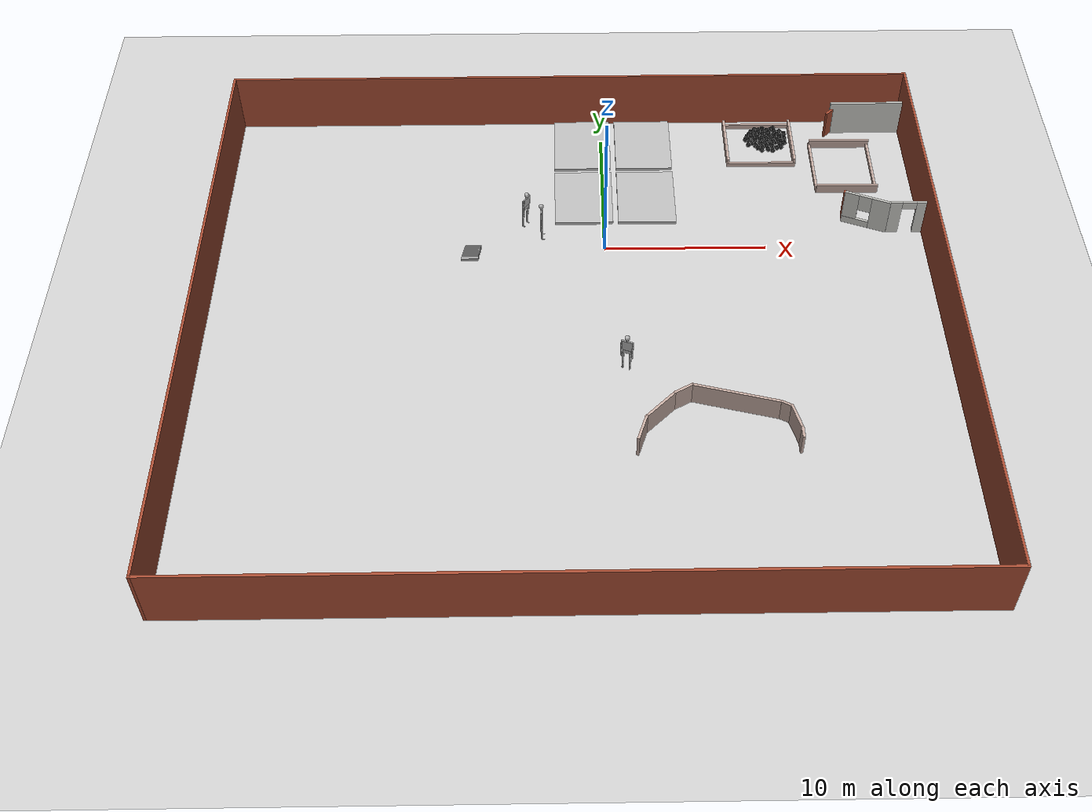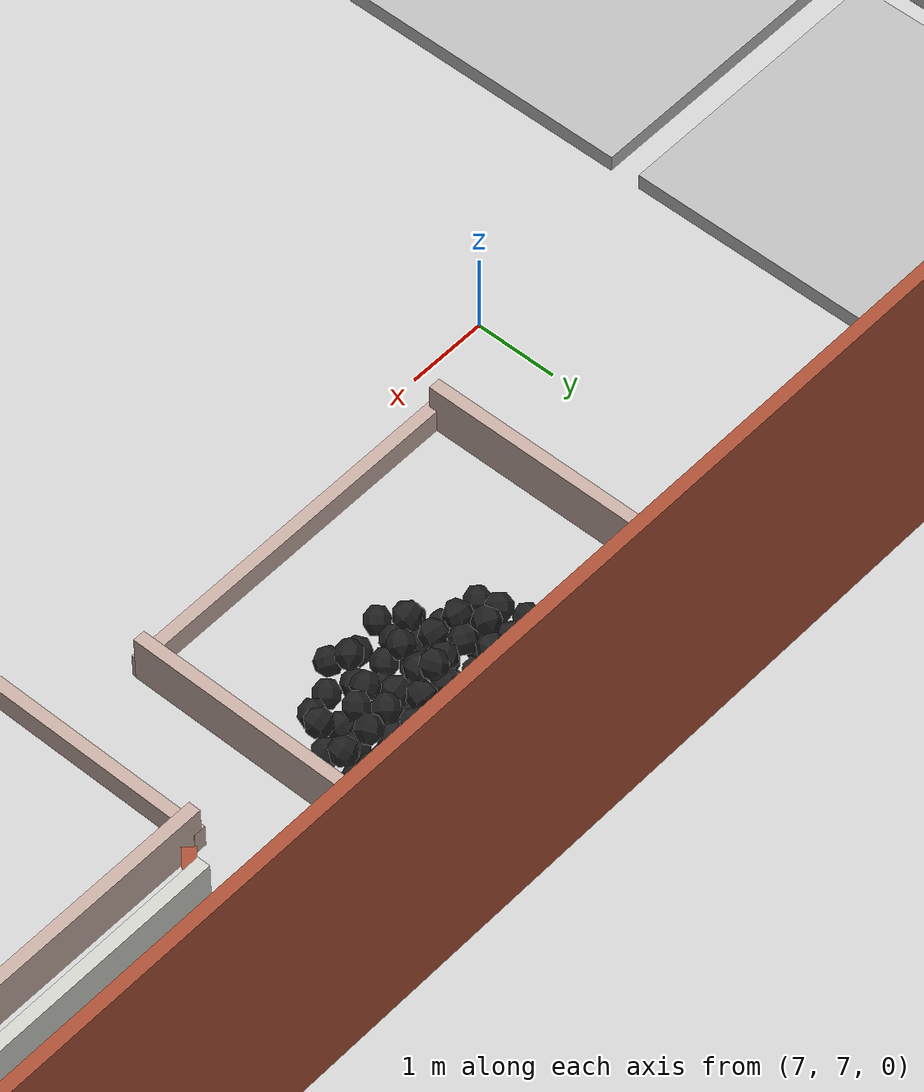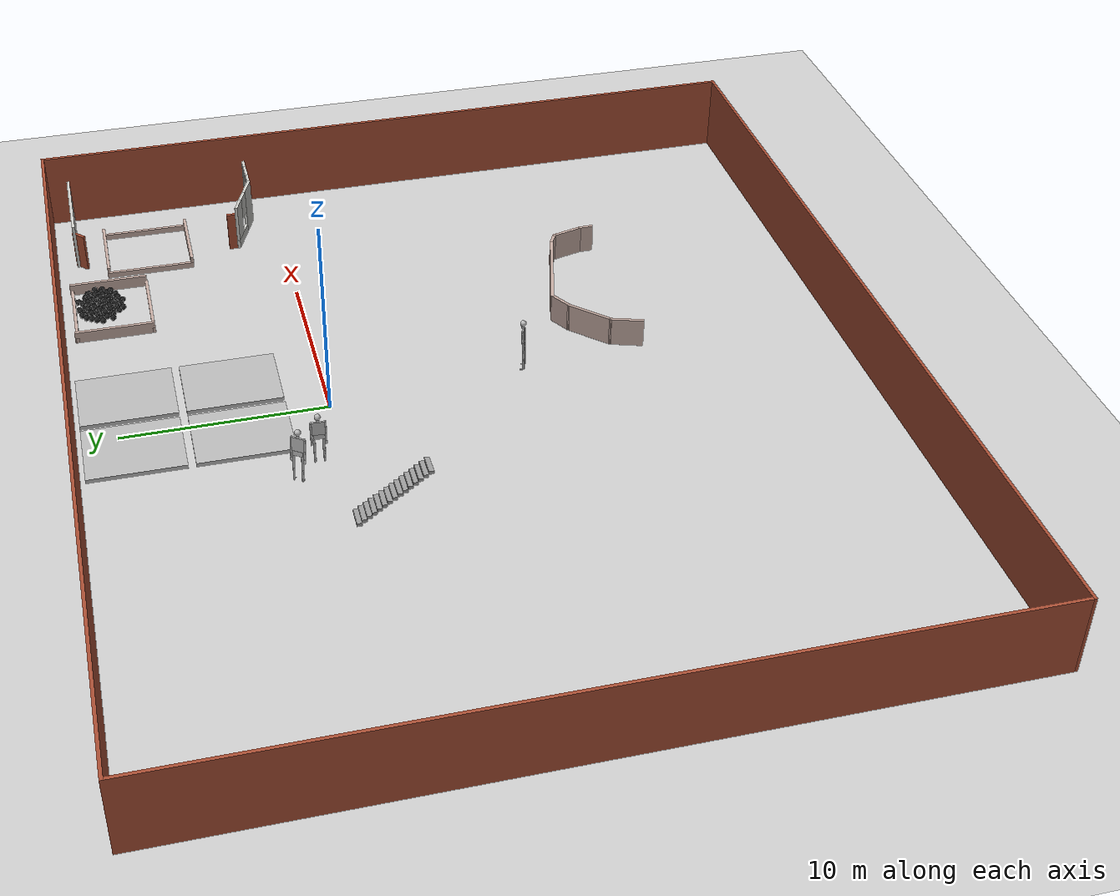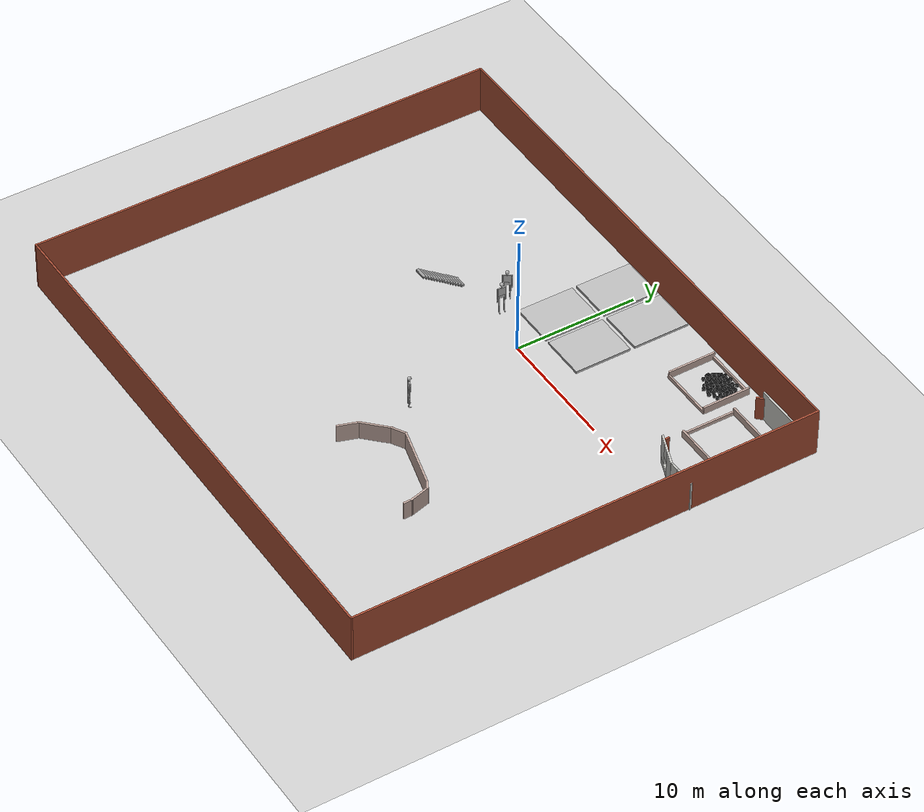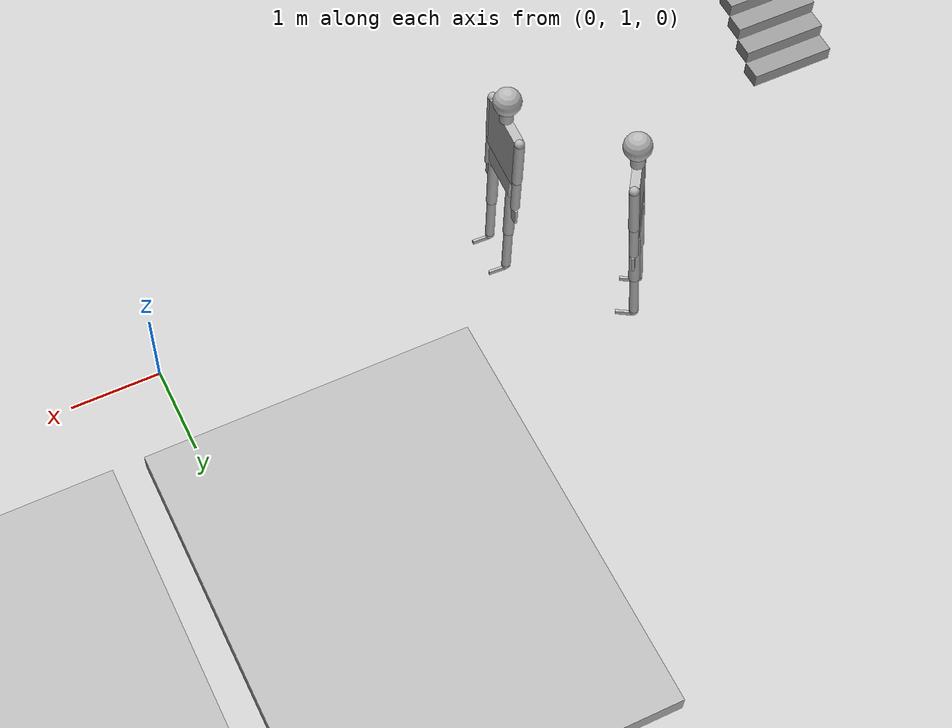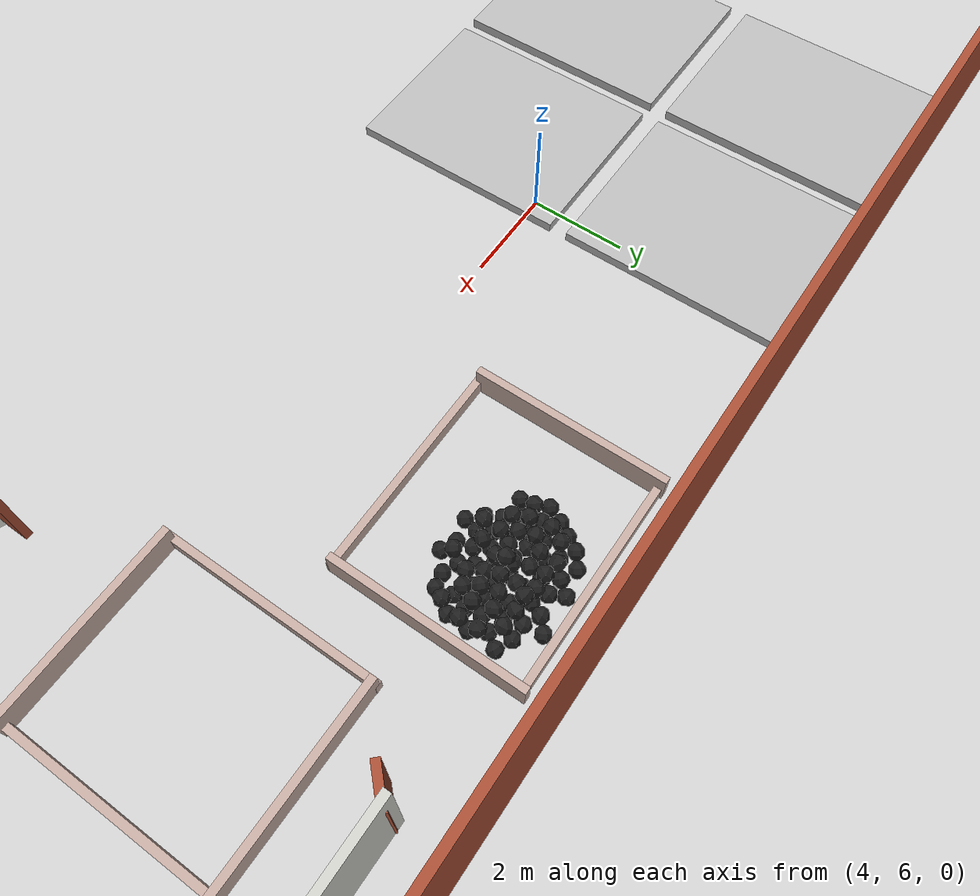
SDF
<sdf version="1.7">
 <world name="default">
  <light name="sun" type="directional">
   <pose>0 0 10 0 -0 0</pose>
   <diffuse>0.8 0.8 0.8 1</diffuse>
   <specular>0.2 0.2 0.2 1</specular>
   <attenuation>
    <range>1000</range>
    <constant>0.9</constant>
    <linear>0.01</linear>
    <quadratic>0.001</quadratic>
   </attenuation>
   <direction>-0.5 0.1 -0.9</direction>
   <spot><inner_angle>0</inner_angle><outer_angle>0</outer_angle><falloff>0</falloff></spot>
  </light>
  <model name="ground_plane">
   <static>1</static>
   <link name="link">
    <collision name="collision">
     <geometry><plane><normal>0 0 1</normal><size>100 100</size></plane></geometry>
     <surface><friction><ode><mu>100</mu><mu2>50</mu2></ode></friction></surface>
    </collision>
    <visual name="visual">
     <cast_shadows>0</cast_shadows>
     <geometry><plane><normal>0 0 1</normal><size>100 100</size></plane></geometry>
     <material>
      <script><uri>file://media/materials/scripts/gazebo.material</uri><name>Gazebo/Grey</name></script>
     </material>
    </visual>
   </link>
  </model>
  <gravity>0 0 -9.8</gravity>
  <magnetic_field>6e-06 2.3e-05 -4.2e-05</magnetic_field>
  <atmosphere type="adiabatic"/>
  <physics name="default_physics" default="0" type="ode">
   <max_step_size>0.001</max_step_size>
   <real_time_factor>1</real_time_factor>
   <real_time_update_rate>1000</real_time_update_rate>
  </physics>
  <scene><ambient>0.4 0.4 0.4 1</ambient><background>0.7 0.7 0.7 1</background><shadows>1</shadows></scene>
  <audio><device>default</device></audio>
  <spherical_coordinates>
   <surface_model>EARTH_WGS84</surface_model>
   <latitude_deg>0</latitude_deg>
   <longitude_deg>0</longitude_deg>
   <elevation>0</elevation>
   <heading_deg>0</heading_deg>
  </spherical_coordinates>
  <model name="wall11">
   <pose>-2 -7 0 0 -0 0</pose>
   <link name="Wall_0">
    <collision name="Wall_0_Collision">
     <geometry><box><size>44.15 0.15 4</size></box></geometry>
     <pose>0 0 2 0 -0 0</pose>
    </collision>
    <visual name="Wall_0_Visual">
     <pose>0 0 2 0 -0 0</pose>
     <geometry><box><size>44.15 0.15 4</size></box></geometry>
     <material>
      <script><uri>file://media/materials/scripts/gazebo.material</uri><name>Gazebo/Bricks</name></script>
      <ambient>1 1 1 1</ambient>
     </material>
     <meta><layer>0</layer></meta>
    </visual>
    <pose>0 19 0 0 -0 0</pose>
   </link>
   <link name="Wall_2">
    <collision name="Wall_2_Collision">
     <geometry><box><size>38.15 0.15 4</size></box></geometry>
     <pose>0 0 2 0 -0 0</pose>
    </collision>
    <visual name="Wall_2_Visual">
     <pose>0 0 2 0 -0 0</pose>
     <geometry><box><size>38.15 0.15 4</size></box></geometry>
     <material>
      <script><uri>file://media/materials/scripts/gazebo.material</uri><name>Gazebo/Bricks</name></script>
      <ambient>1 1 1 1</ambient>
     </material>
     <meta><layer>0</layer></meta>
    </visual>
    <pose>22 0 0 0 -0 -1.5708</pose>
   </link>
   <link name="Wall_4">
    <collision name="Wall_4_Collision">
     <geometry><box><size>44.15 0.15 4</size></box></geometry>
     <pose>0 0 2 0 -0 0</pose>
    </collision>
    <visual name="Wall_4_Visual">
     <pose>0 0 2 0 -0 0</pose>
     <geometry><box><size>44.15 0.15 4</size></box></geometry>
     <material>
      <script><uri>file://media/materials/scripts/gazebo.material</uri><name>Gazebo/Bricks</name></script>
      <ambient>1 1 1 1</ambient>
     </material>
     <meta><layer>0</layer></meta>
    </visual>
    <pose>0 -19 0 0 -0 3.14159</pose>
   </link>
   <link name="Wall_6">
    <collision name="Wall_6_Collision">
     <geometry><box><size>38.15 0.15 4</size></box></geometry>
     <pose>0 0 2 0 -0 0</pose>
    </collision>
    <visual name="Wall_6_Visual">
     <pose>0 0 2 0 -0 0</pose>
     <geometry><box><size>38.15 0.15 4</size></box></geometry>
     <material>
      <script><uri>file://media/materials/scripts/gazebo.material</uri><name>Gazebo/Bricks</name></script>
      <ambient>1 1 1 1</ambient>
     </material>
     <meta><layer>0</layer></meta>
    </visual>
    <pose>-22 0 0 0 -0 1.5708</pose>
   </link>
   <static>1</static>
  </model>
  <model name="wall1">
   <pose>6.97273 -12.8415 0 0 0 -0.014727</pose>
   <link name="Wall_0">
    <collision name="Wall_0_Collision">
     <geometry><box><size>5.09773 0.15 1.5</size></box></geometry>
     <pose>0 0 0.75 0 -0 0</pose>
    </collision>
    <visual name="Wall_0_Visual">
     <pose>0 0 0.75 0 -0 0</pose>
     <geometry><box><size>5.09773 0.15 1.5</size></box></geometry>
     <material>
      <script><uri>file://media/materials/scripts/gazebo.material</uri><name>Gazebo/Grey</name></script>
      <ambient>0.760784 0.662745 0.627451 1</ambient>
     </material>
     <meta><layer>0</layer></meta>
    </visual>
    <pose>0 0 0 0 -0 -0.244979</pose>
   </link>
   <static>1</static>
  </model>
  <model name="haoduomiantiaa_0">
   <link name="link_0">
    <inertial>
     <mass>0.2</mass>
     <inertia>
      <ixx>0.166667</ixx>
      <ixy>0</ixy>
      <ixz>0</ixz>
      <iyy>0.166667</iyy>
      <iyz>0</iyz>
      <izz>0.166667</izz>
     </inertia>
    </inertial>
    <visual name="visual">
     <geometry>
      <mesh>
       <uri>/home/lihaoyang/catkin_ws/src/pudong_gazebo/world/stl/haoduomianti.stl</uri>
       <scale>1 1 1</scale>
      </mesh>
     </geometry>
     <material>
      <lighting>1</lighting>
      <script><uri>file://media/materials/scripts/gazebo.material</uri><name>Gazebo/Black</name></script>
      <shader type="pixel"><normal_map>__default__</normal_map></shader>
      <ambient>0.3 0.3 0.3 1</ambient>
      <diffuse>0.7 0.7 0.7 1</diffuse>
      <specular>0.01 0.01 0.01 1</specular>
      <emissive>0 0 0 1</emissive>
     </material>
    </visual>
    <collision name="collision">
     <geometry>
      <mesh>
       <uri>/home/lihaoyang/catkin_ws/src/pudong_gazebo/world/stl/haoduomianti.stl</uri>
       <scale>1 1 1</scale>
      </mesh>
     </geometry>
     <surface>
      <friction>
       <ode><mu>1</mu><mu2>1</mu2><fdir1>0 0 0</fdir1><slip1>0</slip1><slip2>0</slip2></ode>
       <torsional>
        <coefficient>1</coefficient>
        <patch_radius>0</patch_radius>
        <surface_radius>0</surface_radius>
        <use_patch_radius>1</use_patch_radius>
        <ode><slip>0</slip></ode>
       </torsional>
      </friction>
      <bounce><restitution_coefficient>0</restitution_coefficient><threshold>1e+06</threshold></bounce>
      <contact>
       <collide_without_contact>0</collide_without_contact>
       <collide_without_contact_bitmask>1</collide_without_contact_bitmask>
       <collide_bitmask>1</collide_bitmask>
       <ode>
        <soft_cfm>0</soft_cfm>
        <soft_erp>0.2</soft_erp>
        <kp>1e+13</kp>
        <kd>1</kd>
        <max_vel>0.01</max_vel>
        <min_depth>0</min_depth>
       </ode>
       <bullet>
        <split_impulse>1</split_impulse>
        <split_impulse_penetration_threshold>-0.01</split_impulse_penetration_threshold>
        <soft_cfm>0</soft_cfm>
        <soft_erp>0.2</soft_erp>
        <kp>1e+13</kp>
        <kd>1</kd>
       </bullet>
      </contact>
     </surface>
    </collision>
   </link>
   <static>0</static>
   <pose>10.9836 10.8029 -0.115391 0.785395 -0.611805 -1.5585</pose>
  </model>
  <model name="haoduomiantiaa_1">
   <link name="link_0">
    <inertial>
     <mass>0.2</mass>
     <inertia>
      <ixx>0.166667</ixx>
      <ixy>0</ixy>
      <ixz>0</ixz>
      <iyy>0.166667</iyy>
      <iyz>0</iyz>
      <izz>0.166667</izz>
     </inertia>
    </inertial>
    <visual name="visual">
     <geometry>
      <mesh>
       <uri>/home/lihaoyang/catkin_ws/src/pudong_gazebo/world/stl/haoduomianti.stl</uri>
       <scale>1 1 1</scale>
      </mesh>
     </geometry>
     <material>
      <lighting>1</lighting>
      <script><uri>file://media/materials/scripts/gazebo.material</uri><name>Gazebo/Black</name></script>
      <shader type="pixel"><normal_map>__default__</normal_map></shader>
      <ambient>0.3 0.3 0.3 1</ambient>
      <diffuse>0.7 0.7 0.7 1</diffuse>
      <specular>0.01 0.01 0.01 1</specular>
      <emissive>0 0 0 1</emissive>
     </material>
    </visual>
    <collision name="collision">
     <geometry>
      <mesh>
       <uri>/home/lihaoyang/catkin_ws/src/pudong_gazebo/world/stl/haoduomianti.stl</uri>
       <scale>1 1 1</scale>
      </mesh>
     </geometry>
     <surface>
      <friction>
       <ode><mu>1</mu><mu2>1</mu2><fdir1>0 0 0</fdir1><slip1>0</slip1><slip2>0</slip2></ode>
       <torsional>
        <coefficient>1</coefficient>
        <patch_radius>0</patch_radius>
        <surface_radius>0</surface_radius>
        <use_patch_radius>1</use_patch_radius>
        <ode><slip>0</slip></ode>
       </torsional>
      </friction>
      <bounce><restitution_coefficient>0</restitution_coefficient><threshold>1e+06</threshold></bounce>
      <contact>
       <collide_without_contact>0</collide_without_contact>
       <collide_without_contact_bitmask>1</collide_without_contact_bitmask>
       <collide_bitmask>1</collide_bitmask>
       <ode>
        <soft_cfm>0</soft_cfm>
        <soft_erp>0.2</soft_erp>
        <kp>1e+13</kp>
        <kd>1</kd>
        <max_vel>0.01</max_vel>
        <min_depth>0</min_depth>
       </ode>
       <bullet>
        <split_impulse>1</split_impulse>
        <split_impulse_penetration_threshold>-0.01</split_impulse_penetration_threshold>
        <soft_cfm>0</soft_cfm>
        <soft_erp>0.2</soft_erp>
        <kp>1e+13</kp>
        <kd>1</kd>
       </bullet>
      </contact>
     </surface>
    </collision>
   </link>
   <static>0</static>
   <pose>11.1953 10.3549 0.170525 0.635378 -0.464967 -1.89536</pose>
  </model>
  <model name="haoduomiantiaa_2">
   <link name="link_0">
    <inertial>
     <mass>0.2</mass>
     <inertia>
      <ixx>0.166667</ixx>
      <ixy>0</ixy>
      <ixz>0</ixz>
      <iyy>0.166667</iyy>
      <iyz>0</iyz>
      <izz>0.166667</izz>
     </inertia>
    </inertial>
    <visual name="visual">
     <geometry>
      <mesh>
       <uri>/home/lihaoyang/catkin_ws/src/pudong_gazebo/world/stl/haoduomianti.stl</uri>
       <scale>1 1 1</scale>
      </mesh>
     </geometry>
     <material>
      <lighting>1</lighting>
      <script><uri>file://media/materials/scripts/gazebo.material</uri><name>Gazebo/Black</name></script>
      <shader type="pixel"><normal_map>__default__</normal_map></shader>
      <ambient>0.3 0.3 0.3 1</ambient>
      <diffuse>0.7 0.7 0.7 1</diffuse>
      <specular>0.01 0.01 0.01 1</specular>
      <emissive>0 0 0 1</emissive>
     </material>
    </visual>
    <collision name="collision">
     <geometry>
      <mesh>
       <uri>/home/lihaoyang/catkin_ws/src/pudong_gazebo/world/stl/haoduomianti.stl</uri>
       <scale>1 1 1</scale>
      </mesh>
     </geometry>
     <surface>
      <friction>
       <ode><mu>1</mu><mu2>1</mu2><fdir1>0 0 0</fdir1><slip1>0</slip1><slip2>0</slip2></ode>
       <torsional>
        <coefficient>1</coefficient>
        <patch_radius>0</patch_radius>
        <surface_radius>0</surface_radius>
        <use_patch_radius>1</use_patch_radius>
        <ode><slip>0</slip></ode>
       </torsional>
      </friction>
      <bounce><restitution_coefficient>0</restitution_coefficient><threshold>1e+06</threshold></bounce>
      <contact>
       <collide_without_contact>0</collide_without_contact>
       <collide_without_contact_bitmask>1</collide_without_contact_bitmask>
       <collide_bitmask>1</collide_bitmask>
       <ode>
        <soft_cfm>0</soft_cfm>
        <soft_erp>0.2</soft_erp>
        <kp>1e+13</kp>
        <kd>1</kd>
        <max_vel>0.01</max_vel>
        <min_depth>0</min_depth>
       </ode>
       <bullet>
        <split_impulse>1</split_impulse>
        <split_impulse_penetration_threshold>-0.01</split_impulse_penetration_threshold>
        <soft_cfm>0</soft_cfm>
        <soft_erp>0.2</soft_erp>
        <kp>1e+13</kp>
        <kd>1</kd>
       </bullet>
      </contact>
     </surface>
    </collision>
   </link>
   <static>0</static>
   <pose>11.3877 10.9048 -0.079136 0.779753 -0.661702 0.766192</pose>
  </model>
  <model name="haoduomiantiaa_3">
   <link name="link_0">
    <inertial>
     <mass>0.2</mass>
     <inertia>
      <ixx>0.166667</ixx>
      <ixy>0</ixy>
      <ixz>0</ixz>
      <iyy>0.166667</iyy>
      <iyz>0</iyz>
      <izz>0.166667</izz>
     </inertia>
    </inertial>
    <visual name="visual">
     <geometry>
      <mesh>
       <uri>/home/lihaoyang/catkin_ws/src/pudong_gazebo/world/stl/haoduomianti.stl</uri>
       <scale>1 1 1</scale>
      </mesh>
     </geometry>
     <material>
      <lighting>1</lighting>
      <script><uri>file://media/materials/scripts/gazebo.material</uri><name>Gazebo/Black</name></script>
      <shader type="pixel"><normal_map>__default__</normal_map></shader>
      <ambient>0.3 0.3 0.3 1</ambient>
      <diffuse>0.7 0.7 0.7 1</diffuse>
      <specular>0.01 0.01 0.01 1</specular>
      <emissive>0 0 0 1</emissive>
     </material>
    </visual>
    <collision name="collision">
     <geometry>
      <mesh>
       <uri>/home/lihaoyang/catkin_ws/src/pudong_gazebo/world/stl/haoduomianti.stl</uri>
       <scale>1 1 1</scale>
      </mesh>
     </geometry>
     <surface>
      <friction>
       <ode><mu>1</mu><mu2>1</mu2><fdir1>0 0 0</fdir1><slip1>0</slip1><slip2>0</slip2></ode>
       <torsional>
        <coefficient>1</coefficient>
        <patch_radius>0</patch_radius>
        <surface_radius>0</surface_radius>
        <use_patch_radius>1</use_patch_radius>
        <ode><slip>0</slip></ode>
       </torsional>
      </friction>
      <bounce><restitution_coefficient>0</restitution_coefficient><threshold>1e+06</threshold></bounce>
      <contact>
       <collide_without_contact>0</collide_without_contact>
       <collide_without_contact_bitmask>1</collide_without_contact_bitmask>
       <collide_bitmask>1</collide_bitmask>
       <ode>
        <soft_cfm>0</soft_cfm>
        <soft_erp>0.2</soft_erp>
        <kp>1e+13</kp>
        <kd>1</kd>
        <max_vel>0.01</max_vel>
        <min_depth>0</min_depth>
       </ode>
       <bullet>
        <split_impulse>1</split_impulse>
        <split_impulse_penetration_threshold>-0.01</split_impulse_penetration_threshold>
        <soft_cfm>0</soft_cfm>
        <soft_erp>0.2</soft_erp>
        <kp>1e+13</kp>
        <kd>1</kd>
       </bullet>
      </contact>
     </surface>
    </collision>
   </link>
   <static>0</static>
   <pose>10.3504 9.84955 0.129678 0.425469 -0.641016 -2.14379</pose>
  </model>
  <model name="haoduomiantiaa_5">
   <link name="link_0">
    <inertial>
     <mass>0.2</mass>
     <inertia>
      <ixx>0.166667</ixx>
      <ixy>0</ixy>
      <ixz>0</ixz>
      <iyy>0.166667</iyy>
      <iyz>0</iyz>
      <izz>0.166667</izz>
     </inertia>
    </inertial>
    <visual name="visual">
     <geometry>
      <mesh>
       <uri>/home/lihaoyang/catkin_ws/src/pudong_gazebo/world/stl/haoduomianti.stl</uri>
       <scale>1 1 1</scale>
      </mesh>
     </geometry>
     <material>
      <lighting>1</lighting>
      <script><uri>file://media/materials/scripts/gazebo.material</uri><name>Gazebo/Black</name></script>
      <shader type="pixel"><normal_map>__default__</normal_map></shader>
      <ambient>0.3 0.3 0.3 1</ambient>
      <diffuse>0.7 0.7 0.7 1</diffuse>
      <specular>0.01 0.01 0.01 1</specular>
      <emissive>0 0 0 1</emissive>
     </material>
    </visual>
    <collision name="collision">
     <geometry>
      <mesh>
       <uri>/home/lihaoyang/catkin_ws/src/pudong_gazebo/world/stl/haoduomianti.stl</uri>
       <scale>1 1 1</scale>
      </mesh>
     </geometry>
     <surface>
      <friction>
       <ode><mu>1</mu><mu2>1</mu2><fdir1>0 0 0</fdir1><slip1>0</slip1><slip2>0</slip2></ode>
       <torsional>
        <coefficient>1</coefficient>
        <patch_radius>0</patch_radius>
        <surface_radius>0</surface_radius>
        <use_patch_radius>1</use_patch_radius>
        <ode><slip>0</slip></ode>
       </torsional>
      </friction>
      <bounce><restitution_coefficient>0</restitution_coefficient><threshold>1e+06</threshold></bounce>
      <contact>
       <collide_without_contact>0</collide_without_contact>
       <collide_without_contact_bitmask>1</collide_without_contact_bitmask>
       <collide_bitmask>1</collide_bitmask>
       <ode>
        <soft_cfm>0</soft_cfm>
        <soft_erp>0.2</soft_erp>
        <kp>1e+13</kp>
        <kd>1</kd>
        <max_vel>0.01</max_vel>
        <min_depth>0</min_depth>
       </ode>
       <bullet>
        <split_impulse>1</split_impulse>
        <split_impulse_penetration_threshold>-0.01</split_impulse_penetration_threshold>
        <soft_cfm>0</soft_cfm>
        <soft_erp>0.2</soft_erp>
        <kp>1e+13</kp>
        <kd>1</kd>
       </bullet>
      </contact>
     </surface>
    </collision>
   </link>
   <static>0</static>
   <pose>11.8802 10.4598 0.126878 1.11651 -0.806687 3.13979</pose>
  </model>
  <model name="haoduomiantiaa_6">
   <link name="link_0">
    <inertial>
     <mass>0.2</mass>
     <inertia>
      <ixx>0.166667</ixx>
      <ixy>0</ixy>
      <ixz>0</ixz>
      <iyy>0.166667</iyy>
      <iyz>0</iyz>
      <izz>0.166667</izz>
     </inertia>
    </inertial>
    <visual name="visual">
     <geometry>
      <mesh>
       <uri>/home/lihaoyang/catkin_ws/src/pudong_gazebo/world/stl/haoduomianti.stl</uri>
       <scale>1 1 1</scale>
      </mesh>
     </geometry>
     <material>
      <lighting>1</lighting>
      <script><uri>file://media/materials/scripts/gazebo.material</uri><name>Gazebo/Black</name></script>
      <shader type="pixel"><normal_map>__default__</normal_map></shader>
      <ambient>0.3 0.3 0.3 1</ambient>
      <diffuse>0.7 0.7 0.7 1</diffuse>
      <specular>0.01 0.01 0.01 1</specular>
      <emissive>0 0 0 1</emissive>
     </material>
    </visual>
    <collision name="collision">
     <geometry>
      <mesh>
       <uri>/home/lihaoyang/catkin_ws/src/pudong_gazebo/world/stl/haoduomianti.stl</uri>
       <scale>1 1 1</scale>
      </mesh>
     </geometry>
     <surface>
      <friction>
       <ode><mu>1</mu><mu2>1</mu2><fdir1>0 0 0</fdir1><slip1>0</slip1><slip2>0</slip2></ode>
       <torsional>
        <coefficient>1</coefficient>
        <patch_radius>0</patch_radius>
        <surface_radius>0</surface_radius>
        <use_patch_radius>1</use_patch_radius>
        <ode><slip>0</slip></ode>
       </torsional>
      </friction>
      <bounce><restitution_coefficient>0</restitution_coefficient><threshold>1e+06</threshold></bounce>
      <contact>
       <collide_without_contact>0</collide_without_contact>
       <collide_without_contact_bitmask>1</collide_without_contact_bitmask>
       <collide_bitmask>1</collide_bitmask>
       <ode>
        <soft_cfm>0</soft_cfm>
        <soft_erp>0.2</soft_erp>
        <kp>1e+13</kp>
        <kd>1</kd>
        <max_vel>0.01</max_vel>
        <min_depth>0</min_depth>
       </ode>
       <bullet>
        <split_impulse>1</split_impulse>
        <split_impulse_penetration_threshold>-0.01</split_impulse_penetration_threshold>
        <soft_cfm>0</soft_cfm>
        <soft_erp>0.2</soft_erp>
        <kp>1e+13</kp>
        <kd>1</kd>
       </bullet>
      </contact>
     </surface>
    </collision>
   </link>
   <static>0</static>
   <pose>10.3511 10.6223 -0.116656 0.78558 -0.614844 -0.602707</pose>
  </model>
  <model name="haoduomiantiaa_7">
   <link name="link_0">
    <inertial>
     <mass>0.2</mass>
     <inertia>
      <ixx>0.166667</ixx>
      <ixy>0</ixy>
      <ixz>0</ixz>
      <iyy>0.166667</iyy>
      <iyz>0</iyz>
      <izz>0.166667</izz>
     </inertia>
    </inertial>
    <visual name="visual">
     <geometry>
      <mesh>
       <uri>/home/lihaoyang/catkin_ws/src/pudong_gazebo/world/stl/haoduomianti.stl</uri>
       <scale>1 1 1</scale>
      </mesh>
     </geometry>
     <material>
      <lighting>1</lighting>
      <script><uri>file://media/materials/scripts/gazebo.material</uri><name>Gazebo/Black</name></script>
      <shader type="pixel"><normal_map>__default__</normal_map></shader>
      <ambient>0.3 0.3 0.3 1</ambient>
      <diffuse>0.7 0.7 0.7 1</diffuse>
      <specular>0.01 0.01 0.01 1</specular>
      <emissive>0 0 0 1</emissive>
     </material>
    </visual>
    <collision name="collision">
     <geometry>
      <mesh>
       <uri>/home/lihaoyang/catkin_ws/src/pudong_gazebo/world/stl/haoduomianti.stl</uri>
       <scale>1 1 1</scale>
      </mesh>
     </geometry>
     <surface>
      <friction>
       <ode><mu>1</mu><mu2>1</mu2><fdir1>0 0 0</fdir1><slip1>0</slip1><slip2>0</slip2></ode>
       <torsional>
        <coefficient>1</coefficient>
        <patch_radius>0</patch_radius>
        <surface_radius>0</surface_radius>
        <use_patch_radius>1</use_patch_radius>
        <ode><slip>0</slip></ode>
       </torsional>
      </friction>
      <bounce><restitution_coefficient>0</restitution_coefficient><threshold>1e+06</threshold></bounce>
      <contact>
       <collide_without_contact>0</collide_without_contact>
       <collide_without_contact_bitmask>1</collide_without_contact_bitmask>
       <collide_bitmask>1</collide_bitmask>
       <ode>
        <soft_cfm>0</soft_cfm>
        <soft_erp>0.2</soft_erp>
        <kp>1e+13</kp>
        <kd>1</kd>
        <max_vel>0.01</max_vel>
        <min_depth>0</min_depth>
       </ode>
       <bullet>
        <split_impulse>1</split_impulse>
        <split_impulse_penetration_threshold>-0.01</split_impulse_penetration_threshold>
        <soft_cfm>0</soft_cfm>
        <soft_erp>0.2</soft_erp>
        <kp>1e+13</kp>
        <kd>1</kd>
       </bullet>
      </contact>
     </surface>
    </collision>
   </link>
   <static>0</static>
   <pose>9.93722 10.5221 -0.116376 0.787891 -0.616668 -0.530396</pose>
  </model>
  <model name="haoduomiantiaa_8">
   <link name="link_0">
    <inertial>
     <mass>0.2</mass>
     <inertia>
      <ixx>0.166667</ixx>
      <ixy>0</ixy>
      <ixz>0</ixz>
      <iyy>0.166667</iyy>
      <iyz>0</iyz>
      <izz>0.166667</izz>
     </inertia>
    </inertial>
    <visual name="visual">
     <geometry>
      <mesh>
       <uri>/home/lihaoyang/catkin_ws/src/pudong_gazebo/world/stl/haoduomianti.stl</uri>
       <scale>1 1 1</scale>
      </mesh>
     </geometry>
     <material>
      <lighting>1</lighting>
      <script><uri>file://media/materials/scripts/gazebo.material</uri><name>Gazebo/Black</name></script>
      <shader type="pixel"><normal_map>__default__</normal_map></shader>
      <ambient>0.3 0.3 0.3 1</ambient>
      <diffuse>0.7 0.7 0.7 1</diffuse>
      <specular>0.01 0.01 0.01 1</specular>
      <emissive>0 0 0 1</emissive>
     </material>
    </visual>
    <collision name="collision">
     <geometry>
      <mesh>
       <uri>/home/lihaoyang/catkin_ws/src/pudong_gazebo/world/stl/haoduomianti.stl</uri>
       <scale>1 1 1</scale>
      </mesh>
     </geometry>
     <surface>
      <friction>
       <ode><mu>1</mu><mu2>1</mu2><fdir1>0 0 0</fdir1><slip1>0</slip1><slip2>0</slip2></ode>
       <torsional>
        <coefficient>1</coefficient>
        <patch_radius>0</patch_radius>
        <surface_radius>0</surface_radius>
        <use_patch_radius>1</use_patch_radius>
        <ode><slip>0</slip></ode>
       </torsional>
      </friction>
      <bounce><restitution_coefficient>0</restitution_coefficient><threshold>1e+06</threshold></bounce>
      <contact>
       <collide_without_contact>0</collide_without_contact>
       <collide_without_contact_bitmask>1</collide_without_contact_bitmask>
       <collide_bitmask>1</collide_bitmask>
       <ode>
        <soft_cfm>0</soft_cfm>
        <soft_erp>0.2</soft_erp>
        <kp>1e+13</kp>
        <kd>1</kd>
        <max_vel>0.01</max_vel>
        <min_depth>0</min_depth>
       </ode>
       <bullet>
        <split_impulse>1</split_impulse>
        <split_impulse_penetration_threshold>-0.01</split_impulse_penetration_threshold>
        <soft_cfm>0</soft_cfm>
        <soft_erp>0.2</soft_erp>
        <kp>1e+13</kp>
        <kd>1</kd>
       </bullet>
      </contact>
     </surface>
    </collision>
   </link>
   <static>0</static>
   <pose>12.1139 10.1936 0.135323 1.16591 -0.553289 1.40457</pose>
  </model>
  <model name="haoduomiantiaa_11">
   <link name="link_0">
    <inertial>
     <mass>0.2</mass>
     <inertia>
      <ixx>0.166667</ixx>
      <ixy>0</ixy>
      <ixz>0</ixz>
      <iyy>0.166667</iyy>
      <iyz>0</iyz>
      <izz>0.166667</izz>
     </inertia>
    </inertial>
    <visual name="visual">
     <geometry>
      <mesh>
       <uri>/home/lihaoyang/catkin_ws/src/pudong_gazebo/world/stl/haoduomianti.stl</uri>
       <scale>1 1 1</scale>
      </mesh>
     </geometry>
     <material>
      <lighting>1</lighting>
      <script><uri>file://media/materials/scripts/gazebo.material</uri><name>Gazebo/Black</name></script>
      <shader type="pixel"><normal_map>__default__</normal_map></shader>
      <ambient>0.3 0.3 0.3 1</ambient>
      <diffuse>0.7 0.7 0.7 1</diffuse>
      <specular>0.01 0.01 0.01 1</specular>
      <emissive>0 0 0 1</emissive>
     </material>
    </visual>
    <collision name="collision">
     <geometry>
      <mesh>
       <uri>/home/lihaoyang/catkin_ws/src/pudong_gazebo/world/stl/haoduomianti.stl</uri>
       <scale>1 1 1</scale>
      </mesh>
     </geometry>
     <surface>
      <friction>
       <ode><mu>1</mu><mu2>1</mu2><fdir1>0 0 0</fdir1><slip1>0</slip1><slip2>0</slip2></ode>
       <torsional>
        <coefficient>1</coefficient>
        <patch_radius>0</patch_radius>
        <surface_radius>0</surface_radius>
        <use_patch_radius>1</use_patch_radius>
        <ode><slip>0</slip></ode>
       </torsional>
      </friction>
      <bounce><restitution_coefficient>0</restitution_coefficient><threshold>1e+06</threshold></bounce>
      <contact>
       <collide_without_contact>0</collide_without_contact>
       <collide_without_contact_bitmask>1</collide_without_contact_bitmask>
       <collide_bitmask>1</collide_bitmask>
       <ode>
        <soft_cfm>0</soft_cfm>
        <soft_erp>0.2</soft_erp>
        <kp>1e+13</kp>
        <kd>1</kd>
        <max_vel>0.01</max_vel>
        <min_depth>0</min_depth>
       </ode>
       <bullet>
        <split_impulse>1</split_impulse>
        <split_impulse_penetration_threshold>-0.01</split_impulse_penetration_threshold>
        <soft_cfm>0</soft_cfm>
        <soft_erp>0.2</soft_erp>
        <kp>1e+13</kp>
        <kd>1</kd>
       </bullet>
      </contact>
     </surface>
    </collision>
   </link>
   <static>0</static>
   <pose>10.8568 11.0678 -0.115068 0.792386 -0.620348 -1.65447</pose>
  </model>
  <model name="haoduomiantiaa_13">
   <link name="link_0">
    <inertial>
     <mass>0.2</mass>
     <inertia>
      <ixx>0.166667</ixx>
      <ixy>0</ixy>
      <ixz>0</ixz>
      <iyy>0.166667</iyy>
      <iyz>0</iyz>
      <izz>0.166667</izz>
     </inertia>
    </inertial>
    <visual name="visual">
     <geometry>
      <mesh>
       <uri>/home/lihaoyang/catkin_ws/src/pudong_gazebo/world/stl/haoduomianti.stl</uri>
       <scale>1 1 1</scale>
      </mesh>
     </geometry>
     <material>
      <lighting>1</lighting>
      <script><uri>file://media/materials/scripts/gazebo.material</uri><name>Gazebo/Black</name></script>
      <shader type="pixel"><normal_map>__default__</normal_map></shader>
      <ambient>0.3 0.3 0.3 1</ambient>
      <diffuse>0.7 0.7 0.7 1</diffuse>
      <specular>0.01 0.01 0.01 1</specular>
      <emissive>0 0 0 1</emissive>
     </material>
    </visual>
    <collision name="collision">
     <geometry>
      <mesh>
       <uri>/home/lihaoyang/catkin_ws/src/pudong_gazebo/world/stl/haoduomianti.stl</uri>
       <scale>1 1 1</scale>
      </mesh>
     </geometry>
     <surface>
      <friction>
       <ode><mu>1</mu><mu2>1</mu2><fdir1>0 0 0</fdir1><slip1>0</slip1><slip2>0</slip2></ode>
       <torsional>
        <coefficient>1</coefficient>
        <patch_radius>0</patch_radius>
        <surface_radius>0</surface_radius>
        <use_patch_radius>1</use_patch_radius>
        <ode><slip>0</slip></ode>
       </torsional>
      </friction>
      <bounce><restitution_coefficient>0</restitution_coefficient><threshold>1e+06</threshold></bounce>
      <contact>
       <collide_without_contact>0</collide_without_contact>
       <collide_without_contact_bitmask>1</collide_without_contact_bitmask>
       <collide_bitmask>1</collide_bitmask>
       <ode>
        <soft_cfm>0</soft_cfm>
        <soft_erp>0.2</soft_erp>
        <kp>1e+13</kp>
        <kd>1</kd>
        <max_vel>0.01</max_vel>
        <min_depth>0</min_depth>
       </ode>
       <bullet>
        <split_impulse>1</split_impulse>
        <split_impulse_penetration_threshold>-0.01</split_impulse_penetration_threshold>
        <soft_cfm>0</soft_cfm>
        <soft_erp>0.2</soft_erp>
        <kp>1e+13</kp>
        <kd>1</kd>
       </bullet>
      </contact>
     </surface>
    </collision>
   </link>
   <static>0</static>
   <pose>11.6376 9.95767 -0.116991 0.786776 -0.616267 2.80513</pose>
  </model>
  <model name="haoduomiantiaa_16">
   <link name="link_0">
    <inertial>
     <mass>0.2</mass>
     <inertia>
      <ixx>0.166667</ixx>
      <ixy>0</ixy>
      <ixz>0</ixz>
      <iyy>0.166667</iyy>
      <iyz>0</iyz>
      <izz>0.166667</izz>
     </inertia>
    </inertial>
    <visual name="visual">
     <geometry>
      <mesh>
       <uri>/home/lihaoyang/catkin_ws/src/pudong_gazebo/world/stl/haoduomianti.stl</uri>
       <scale>1 1 1</scale>
      </mesh>
     </geometry>
     <material>
      <lighting>1</lighting>
      <script><uri>file://media/materials/scripts/gazebo.material</uri><name>Gazebo/Black</name></script>
      <shader type="pixel"><normal_map>__default__</normal_map></shader>
      <ambient>0.3 0.3 0.3 1</ambient>
      <diffuse>0.7 0.7 0.7 1</diffuse>
      <specular>0.01 0.01 0.01 1</specular>
      <emissive>0 0 0 1</emissive>
     </material>
    </visual>
    <collision name="collision">
     <geometry>
      <mesh>
       <uri>/home/lihaoyang/catkin_ws/src/pudong_gazebo/world/stl/haoduomianti.stl</uri>
       <scale>1 1 1</scale>
      </mesh>
     </geometry>
     <surface>
      <friction>
       <ode><mu>1</mu><mu2>1</mu2><fdir1>0 0 0</fdir1><slip1>0</slip1><slip2>0</slip2></ode>
       <torsional>
        <coefficient>1</coefficient>
        <patch_radius>0</patch_radius>
        <surface_radius>0</surface_radius>
        <use_patch_radius>1</use_patch_radius>
        <ode><slip>0</slip></ode>
       </torsional>
      </friction>
      <bounce><restitution_coefficient>0</restitution_coefficient><threshold>1e+06</threshold></bounce>
      <contact>
       <collide_without_contact>0</collide_without_contact>
       <collide_without_contact_bitmask>1</collide_without_contact_bitmask>
       <collide_bitmask>1</collide_bitmask>
       <ode>
        <soft_cfm>0</soft_cfm>
        <soft_erp>0.2</soft_erp>
        <kp>1e+13</kp>
        <kd>1</kd>
        <max_vel>0.01</max_vel>
        <min_depth>0</min_depth>
       </ode>
       <bullet>
        <split_impulse>1</split_impulse>
        <split_impulse_penetration_threshold>-0.01</split_impulse_penetration_threshold>
        <soft_cfm>0</soft_cfm>
        <soft_erp>0.2</soft_erp>
        <kp>1e+13</kp>
        <kd>1</kd>
       </bullet>
      </contact>
     </surface>
    </collision>
   </link>
   <static>0</static>
   <pose>11.076 10.0888 -0.119382 0.783614 -0.614378 1.91519</pose>
  </model>
  <model name="haoduomiantiaa_17">
   <link name="link_0">
    <inertial>
     <mass>0.2</mass>
     <inertia>
      <ixx>0.166667</ixx>
      <ixy>0</ixy>
      <ixz>0</ixz>
      <iyy>0.166667</iyy>
      <iyz>0</iyz>
      <izz>0.166667</izz>
     </inertia>
    </inertial>
    <visual name="visual">
     <geometry>
      <mesh>
       <uri>/home/lihaoyang/catkin_ws/src/pudong_gazebo/world/stl/haoduomianti.stl</uri>
       <scale>1 1 1</scale>
      </mesh>
     </geometry>
     <material>
      <lighting>1</lighting>
      <script><uri>file://media/materials/scripts/gazebo.material</uri><name>Gazebo/Black</name></script>
      <shader type="pixel"><normal_map>__default__</normal_map></shader>
      <ambient>0.3 0.3 0.3 1</ambient>
      <diffuse>0.7 0.7 0.7 1</diffuse>
      <specular>0.01 0.01 0.01 1</specular>
      <emissive>0 0 0 1</emissive>
     </material>
    </visual>
    <collision name="collision">
     <geometry>
      <mesh>
       <uri>/home/lihaoyang/catkin_ws/src/pudong_gazebo/world/stl/haoduomianti.stl</uri>
       <scale>1 1 1</scale>
      </mesh>
     </geometry>
     <surface>
      <friction>
       <ode><mu>1</mu><mu2>1</mu2><fdir1>0 0 0</fdir1><slip1>0</slip1><slip2>0</slip2></ode>
       <torsional>
        <coefficient>1</coefficient>
        <patch_radius>0</patch_radius>
        <surface_radius>0</surface_radius>
        <use_patch_radius>1</use_patch_radius>
        <ode><slip>0</slip></ode>
       </torsional>
      </friction>
      <bounce><restitution_coefficient>0</restitution_coefficient><threshold>1e+06</threshold></bounce>
      <contact>
       <collide_without_contact>0</collide_without_contact>
       <collide_without_contact_bitmask>1</collide_without_contact_bitmask>
       <collide_bitmask>1</collide_bitmask>
       <ode>
        <soft_cfm>0</soft_cfm>
        <soft_erp>0.2</soft_erp>
        <kp>1e+13</kp>
        <kd>1</kd>
        <max_vel>0.01</max_vel>
        <min_depth>0</min_depth>
       </ode>
       <bullet>
        <split_impulse>1</split_impulse>
        <split_impulse_penetration_threshold>-0.01</split_impulse_penetration_threshold>
        <soft_cfm>0</soft_cfm>
        <soft_erp>0.2</soft_erp>
        <kp>1e+13</kp>
        <kd>1</kd>
       </bullet>
      </contact>
     </surface>
    </collision>
   </link>
   <static>0</static>
   <pose>11.4044 10.5093 0.310138 1.04244 -0.759542 -1.6392</pose>
  </model>
  <model name="haoduomiantiaa_18">
   <link name="link_0">
    <inertial>
     <mass>0.2</mass>
     <inertia>
      <ixx>0.166667</ixx>
      <ixy>0</ixy>
      <ixz>0</ixz>
      <iyy>0.166667</iyy>
      <iyz>0</iyz>
      <izz>0.166667</izz>
     </inertia>
    </inertial>
    <visual name="visual">
     <geometry>
      <mesh>
       <uri>/home/lihaoyang/catkin_ws/src/pudong_gazebo/world/stl/haoduomianti.stl</uri>
       <scale>1 1 1</scale>
      </mesh>
     </geometry>
     <material>
      <lighting>1</lighting>
      <script><uri>file://media/materials/scripts/gazebo.material</uri><name>Gazebo/Black</name></script>
      <shader type="pixel"><normal_map>__default__</normal_map></shader>
      <ambient>0.3 0.3 0.3 1</ambient>
      <diffuse>0.7 0.7 0.7 1</diffuse>
      <specular>0.01 0.01 0.01 1</specular>
      <emissive>0 0 0 1</emissive>
     </material>
    </visual>
    <collision name="collision">
     <geometry>
      <mesh>
       <uri>/home/lihaoyang/catkin_ws/src/pudong_gazebo/world/stl/haoduomianti.stl</uri>
       <scale>1 1 1</scale>
      </mesh>
     </geometry>
     <surface>
      <friction>
       <ode><mu>1</mu><mu2>1</mu2><fdir1>0 0 0</fdir1><slip1>0</slip1><slip2>0</slip2></ode>
       <torsional>
        <coefficient>1</coefficient>
        <patch_radius>0</patch_radius>
        <surface_radius>0</surface_radius>
        <use_patch_radius>1</use_patch_radius>
        <ode><slip>0</slip></ode>
       </torsional>
      </friction>
      <bounce><restitution_coefficient>0</restitution_coefficient><threshold>1e+06</threshold></bounce>
      <contact>
       <collide_without_contact>0</collide_without_contact>
       <collide_without_contact_bitmask>1</collide_without_contact_bitmask>
       <collide_bitmask>1</collide_bitmask>
       <ode>
        <soft_cfm>0</soft_cfm>
        <soft_erp>0.2</soft_erp>
        <kp>1e+13</kp>
        <kd>1</kd>
        <max_vel>0.01</max_vel>
        <min_depth>0</min_depth>
       </ode>
       <bullet>
        <split_impulse>1</split_impulse>
        <split_impulse_penetration_threshold>-0.01</split_impulse_penetration_threshold>
        <soft_cfm>0</soft_cfm>
        <soft_erp>0.2</soft_erp>
        <kp>1e+13</kp>
        <kd>1</kd>
       </bullet>
      </contact>
     </surface>
    </collision>
   </link>
   <static>0</static>
   <pose>11.729 9.57009 0.152429 0.862185 -0.520946 1.69188</pose>
  </model>
  <model name="haoduomiantiaa_20">
   <link name="link_0">
    <inertial>
     <mass>0.2</mass>
     <inertia>
      <ixx>0.166667</ixx>
      <ixy>0</ixy>
      <ixz>0</ixz>
      <iyy>0.166667</iyy>
      <iyz>0</iyz>
      <izz>0.166667</izz>
     </inertia>
    </inertial>
    <visual name="visual">
     <geometry>
      <mesh>
       <uri>/home/lihaoyang/catkin_ws/src/pudong_gazebo/world/stl/haoduomianti.stl</uri>
       <scale>1 1 1</scale>
      </mesh>
     </geometry>
     <material>
      <lighting>1</lighting>
      <script><uri>file://media/materials/scripts/gazebo.material</uri><name>Gazebo/Black</name></script>
      <shader type="pixel"><normal_map>__default__</normal_map></shader>
      <ambient>0.3 0.3 0.3 1</ambient>
      <diffuse>0.7 0.7 0.7 1</diffuse>
      <specular>0.01 0.01 0.01 1</specular>
      <emissive>0 0 0 1</emissive>
     </material>
    </visual>
    <collision name="collision">
     <geometry>
      <mesh>
       <uri>/home/lihaoyang/catkin_ws/src/pudong_gazebo/world/stl/haoduomianti.stl</uri>
       <scale>1 1 1</scale>
      </mesh>
     </geometry>
     <surface>
      <friction>
       <ode><mu>1</mu><mu2>1</mu2><fdir1>0 0 0</fdir1><slip1>0</slip1><slip2>0</slip2></ode>
       <torsional>
        <coefficient>1</coefficient>
        <patch_radius>0</patch_radius>
        <surface_radius>0</surface_radius>
        <use_patch_radius>1</use_patch_radius>
        <ode><slip>0</slip></ode>
       </torsional>
      </friction>
      <bounce><restitution_coefficient>0</restitution_coefficient><threshold>1e+06</threshold></bounce>
      <contact>
       <collide_without_contact>0</collide_without_contact>
       <collide_without_contact_bitmask>1</collide_without_contact_bitmask>
       <collide_bitmask>1</collide_bitmask>
       <ode>
        <soft_cfm>0</soft_cfm>
        <soft_erp>0.2</soft_erp>
        <kp>1e+13</kp>
        <kd>1</kd>
        <max_vel>0.01</max_vel>
        <min_depth>0</min_depth>
       </ode>
       <bullet>
        <split_impulse>1</split_impulse>
        <split_impulse_penetration_threshold>-0.01</split_impulse_penetration_threshold>
        <soft_cfm>0</soft_cfm>
        <soft_erp>0.2</soft_erp>
        <kp>1e+13</kp>
        <kd>1</kd>
       </bullet>
      </contact>
     </surface>
    </collision>
   </link>
   <static>0</static>
   <pose>12.1796 9.846 0.090358 0.716049 -0.546627 -1.12687</pose>
  </model>
  <model name="haoduomiantiaa_21">
   <link name="link_0">
    <inertial>
     <mass>0.2</mass>
     <inertia>
      <ixx>0.166667</ixx>
      <ixy>0</ixy>
      <ixz>0</ixz>
      <iyy>0.166667</iyy>
      <iyz>0</iyz>
      <izz>0.166667</izz>
     </inertia>
    </inertial>
    <visual name="visual">
     <geometry>
      <mesh>
       <uri>/home/lihaoyang/catkin_ws/src/pudong_gazebo/world/stl/haoduomianti.stl</uri>
       <scale>1 1 1</scale>
      </mesh>
     </geometry>
     <material>
      <lighting>1</lighting>
      <script><uri>file://media/materials/scripts/gazebo.material</uri><name>Gazebo/Black</name></script>
      <shader type="pixel"><normal_map>__default__</normal_map></shader>
      <ambient>0.3 0.3 0.3 1</ambient>
      <diffuse>0.7 0.7 0.7 1</diffuse>
      <specular>0.01 0.01 0.01 1</specular>
      <emissive>0 0 0 1</emissive>
     </material>
    </visual>
    <collision name="collision">
     <geometry>
      <mesh>
       <uri>/home/lihaoyang/catkin_ws/src/pudong_gazebo/world/stl/haoduomianti.stl</uri>
       <scale>1 1 1</scale>
      </mesh>
     </geometry>
     <surface>
      <friction>
       <ode><mu>1</mu><mu2>1</mu2><fdir1>0 0 0</fdir1><slip1>0</slip1><slip2>0</slip2></ode>
       <torsional>
        <coefficient>1</coefficient>
        <patch_radius>0</patch_radius>
        <surface_radius>0</surface_radius>
        <use_patch_radius>1</use_patch_radius>
        <ode><slip>0</slip></ode>
       </torsional>
      </friction>
      <bounce><restitution_coefficient>0</restitution_coefficient><threshold>1e+06</threshold></bounce>
      <contact>
       <collide_without_contact>0</collide_without_contact>
       <collide_without_contact_bitmask>1</collide_without_contact_bitmask>
       <collide_bitmask>1</collide_bitmask>
       <ode>
        <soft_cfm>0</soft_cfm>
        <soft_erp>0.2</soft_erp>
        <kp>1e+13</kp>
        <kd>1</kd>
        <max_vel>0.01</max_vel>
        <min_depth>0</min_depth>
       </ode>
       <bullet>
        <split_impulse>1</split_impulse>
        <split_impulse_penetration_threshold>-0.01</split_impulse_penetration_threshold>
        <soft_cfm>0</soft_cfm>
        <soft_erp>0.2</soft_erp>
        <kp>1e+13</kp>
        <kd>1</kd>
       </bullet>
      </contact>
     </surface>
    </collision>
   </link>
   <static>0</static>
   <pose>10.5099 10.3715 -0.114905 0.770932 -0.622212 -1.7354</pose>
  </model>
  <model name="haoduomiantiaa_22">
   <link name="link_0">
    <inertial>
     <mass>0.2</mass>
     <inertia>
      <ixx>0.166667</ixx>
      <ixy>0</ixy>
      <ixz>0</ixz>
      <iyy>0.166667</iyy>
      <iyz>0</iyz>
      <izz>0.166667</izz>
     </inertia>
    </inertial>
    <visual name="visual">
     <geometry>
      <mesh>
       <uri>/home/lihaoyang/catkin_ws/src/pudong_gazebo/world/stl/haoduomianti.stl</uri>
       <scale>1 1 1</scale>
      </mesh>
     </geometry>
     <material>
      <lighting>1</lighting>
      <script><uri>file://media/materials/scripts/gazebo.material</uri><name>Gazebo/Black</name></script>
      <shader type="pixel"><normal_map>__default__</normal_map></shader>
      <ambient>0.3 0.3 0.3 1</ambient>
      <diffuse>0.7 0.7 0.7 1</diffuse>
      <specular>0.01 0.01 0.01 1</specular>
      <emissive>0 0 0 1</emissive>
     </material>
    </visual>
    <collision name="collision">
     <geometry>
      <mesh>
       <uri>/home/lihaoyang/catkin_ws/src/pudong_gazebo/world/stl/haoduomianti.stl</uri>
       <scale>1 1 1</scale>
      </mesh>
     </geometry>
     <surface>
      <friction>
       <ode><mu>1</mu><mu2>1</mu2><fdir1>0 0 0</fdir1><slip1>0</slip1><slip2>0</slip2></ode>
       <torsional>
        <coefficient>1</coefficient>
        <patch_radius>0</patch_radius>
        <surface_radius>0</surface_radius>
        <use_patch_radius>1</use_patch_radius>
        <ode><slip>0</slip></ode>
       </torsional>
      </friction>
      <bounce><restitution_coefficient>0</restitution_coefficient><threshold>1e+06</threshold></bounce>
      <contact>
       <collide_without_contact>0</collide_without_contact>
       <collide_without_contact_bitmask>1</collide_without_contact_bitmask>
       <collide_bitmask>1</collide_bitmask>
       <ode>
        <soft_cfm>0</soft_cfm>
        <soft_erp>0.2</soft_erp>
        <kp>1e+13</kp>
        <kd>1</kd>
        <max_vel>0.01</max_vel>
        <min_depth>0</min_depth>
       </ode>
       <bullet>
        <split_impulse>1</split_impulse>
        <split_impulse_penetration_threshold>-0.01</split_impulse_penetration_threshold>
        <soft_cfm>0</soft_cfm>
        <soft_erp>0.2</soft_erp>
        <kp>1e+13</kp>
        <kd>1</kd>
       </bullet>
      </contact>
     </surface>
    </collision>
   </link>
   <static>0</static>
   <pose>11.9094 10.092 -0.115306 0.778835 -0.618593 -0.470047</pose>
  </model>
  <model name="haoduomiantiaa_24">
   <link name="link_0">
    <inertial>
     <mass>0.2</mass>
     <inertia>
      <ixx>0.166667</ixx>
      <ixy>0</ixy>
      <ixz>0</ixz>
      <iyy>0.166667</iyy>
      <iyz>0</iyz>
      <izz>0.166667</izz>
     </inertia>
    </inertial>
    <visual name="visual">
     <geometry>
      <mesh>
       <uri>/home/lihaoyang/catkin_ws/src/pudong_gazebo/world/stl/haoduomianti.stl</uri>
       <scale>1 1 1</scale>
      </mesh>
     </geometry>
     <material>
      <lighting>1</lighting>
      <script><uri>file://media/materials/scripts/gazebo.material</uri><name>Gazebo/Black</name></script>
      <shader type="pixel"><normal_map>__default__</normal_map></shader>
      <ambient>0.3 0.3 0.3 1</ambient>
      <diffuse>0.7 0.7 0.7 1</diffuse>
      <specular>0.01 0.01 0.01 1</specular>
      <emissive>0 0 0 1</emissive>
     </material>
    </visual>
    <collision name="collision">
     <geometry>
      <mesh>
       <uri>/home/lihaoyang/catkin_ws/src/pudong_gazebo/world/stl/haoduomianti.stl</uri>
       <scale>1 1 1</scale>
      </mesh>
     </geometry>
     <surface>
      <friction>
       <ode><mu>1</mu><mu2>1</mu2><fdir1>0 0 0</fdir1><slip1>0</slip1><slip2>0</slip2></ode>
       <torsional>
        <coefficient>1</coefficient>
        <patch_radius>0</patch_radius>
        <surface_radius>0</surface_radius>
        <use_patch_radius>1</use_patch_radius>
        <ode><slip>0</slip></ode>
       </torsional>
      </friction>
      <bounce><restitution_coefficient>0</restitution_coefficient><threshold>1e+06</threshold></bounce>
      <contact>
       <collide_without_contact>0</collide_without_contact>
       <collide_without_contact_bitmask>1</collide_without_contact_bitmask>
       <collide_bitmask>1</collide_bitmask>
       <ode>
        <soft_cfm>0</soft_cfm>
        <soft_erp>0.2</soft_erp>
        <kp>1e+13</kp>
        <kd>1</kd>
        <max_vel>0.01</max_vel>
        <min_depth>0</min_depth>
       </ode>
       <bullet>
        <split_impulse>1</split_impulse>
        <split_impulse_penetration_threshold>-0.01</split_impulse_penetration_threshold>
        <soft_cfm>0</soft_cfm>
        <soft_erp>0.2</soft_erp>
        <kp>1e+13</kp>
        <kd>1</kd>
       </bullet>
      </contact>
     </surface>
    </collision>
   </link>
   <static>0</static>
   <pose>10.9189 10.0612 0.142592 0.867457 -0.695063 1.70871</pose>
  </model>
  <model name="haoduomiantiaa_25">
   <link name="link_0">
    <inertial>
     <mass>0.2</mass>
     <inertia>
      <ixx>0.166667</ixx>
      <ixy>0</ixy>
      <ixz>0</ixz>
      <iyy>0.166667</iyy>
      <iyz>0</iyz>
      <izz>0.166667</izz>
     </inertia>
    </inertial>
    <visual name="visual">
     <geometry>
      <mesh>
       <uri>/home/lihaoyang/catkin_ws/src/pudong_gazebo/world/stl/haoduomianti.stl</uri>
       <scale>1 1 1</scale>
      </mesh>
     </geometry>
     <material>
      <lighting>1</lighting>
      <script><uri>file://media/materials/scripts/gazebo.material</uri><name>Gazebo/Black</name></script>
      <shader type="pixel"><normal_map>__default__</normal_map></shader>
      <ambient>0.3 0.3 0.3 1</ambient>
      <diffuse>0.7 0.7 0.7 1</diffuse>
      <specular>0.01 0.01 0.01 1</specular>
      <emissive>0 0 0 1</emissive>
     </material>
    </visual>
    <collision name="collision">
     <geometry>
      <mesh>
       <uri>/home/lihaoyang/catkin_ws/src/pudong_gazebo/world/stl/haoduomianti.stl</uri>
       <scale>1 1 1</scale>
      </mesh>
     </geometry>
     <surface>
      <friction>
       <ode><mu>1</mu><mu2>1</mu2><fdir1>0 0 0</fdir1><slip1>0</slip1><slip2>0</slip2></ode>
       <torsional>
        <coefficient>1</coefficient>
        <patch_radius>0</patch_radius>
        <surface_radius>0</surface_radius>
        <use_patch_radius>1</use_patch_radius>
        <ode><slip>0</slip></ode>
       </torsional>
      </friction>
      <bounce><restitution_coefficient>0</restitution_coefficient><threshold>1e+06</threshold></bounce>
      <contact>
       <collide_without_contact>0</collide_without_contact>
       <collide_without_contact_bitmask>1</collide_without_contact_bitmask>
       <collide_bitmask>1</collide_bitmask>
       <ode>
        <soft_cfm>0</soft_cfm>
        <soft_erp>0.2</soft_erp>
        <kp>1e+13</kp>
        <kd>1</kd>
        <max_vel>0.01</max_vel>
        <min_depth>0</min_depth>
       </ode>
       <bullet>
        <split_impulse>1</split_impulse>
        <split_impulse_penetration_threshold>-0.01</split_impulse_penetration_threshold>
        <soft_cfm>0</soft_cfm>
        <soft_erp>0.2</soft_erp>
        <kp>1e+13</kp>
        <kd>1</kd>
       </bullet>
      </contact>
     </surface>
    </collision>
   </link>
   <static>0</static>
   <pose>11.0797 9.7688 -0.112939 0.847404 -0.643041 1.73727</pose>
  </model>
  <model name="haoduomiantiaa_26">
   <link name="link_0">
    <inertial>
     <mass>0.2</mass>
     <inertia>
      <ixx>0.166667</ixx>
      <ixy>0</ixy>
      <ixz>0</ixz>
      <iyy>0.166667</iyy>
      <iyz>0</iyz>
      <izz>0.166667</izz>
     </inertia>
    </inertial>
    <visual name="visual">
     <geometry>
      <mesh>
       <uri>/home/lihaoyang/catkin_ws/src/pudong_gazebo/world/stl/haoduomianti.stl</uri>
       <scale>1 1 1</scale>
      </mesh>
     </geometry>
     <material>
      <lighting>1</lighting>
      <script><uri>file://media/materials/scripts/gazebo.material</uri><name>Gazebo/Black</name></script>
      <shader type="pixel"><normal_map>__default__</normal_map></shader>
      <ambient>0.3 0.3 0.3 1</ambient>
      <diffuse>0.7 0.7 0.7 1</diffuse>
      <specular>0.01 0.01 0.01 1</specular>
      <emissive>0 0 0 1</emissive>
     </material>
    </visual>
    <collision name="collision">
     <geometry>
      <mesh>
       <uri>/home/lihaoyang/catkin_ws/src/pudong_gazebo/world/stl/haoduomianti.stl</uri>
       <scale>1 1 1</scale>
      </mesh>
     </geometry>
     <surface>
      <friction>
       <ode><mu>1</mu><mu2>1</mu2><fdir1>0 0 0</fdir1><slip1>0</slip1><slip2>0</slip2></ode>
       <torsional>
        <coefficient>1</coefficient>
        <patch_radius>0</patch_radius>
        <surface_radius>0</surface_radius>
        <use_patch_radius>1</use_patch_radius>
        <ode><slip>0</slip></ode>
       </torsional>
      </friction>
      <bounce><restitution_coefficient>0</restitution_coefficient><threshold>1e+06</threshold></bounce>
      <contact>
       <collide_without_contact>0</collide_without_contact>
       <collide_without_contact_bitmask>1</collide_without_contact_bitmask>
       <collide_bitmask>1</collide_bitmask>
       <ode>
        <soft_cfm>0</soft_cfm>
        <soft_erp>0.2</soft_erp>
        <kp>1e+13</kp>
        <kd>1</kd>
        <max_vel>0.01</max_vel>
        <min_depth>0</min_depth>
       </ode>
       <bullet>
        <split_impulse>1</split_impulse>
        <split_impulse_penetration_threshold>-0.01</split_impulse_penetration_threshold>
        <soft_cfm>0</soft_cfm>
        <soft_erp>0.2</soft_erp>
        <kp>1e+13</kp>
        <kd>1</kd>
       </bullet>
      </contact>
     </surface>
    </collision>
   </link>
   <static>0</static>
   <pose>10.8266 10.3619 0.039009 0.64722 -0.387103 -2.40719</pose>
  </model>
  <model name="haoduomiantiaa_27">
   <link name="link_0">
    <inertial>
     <mass>0.2</mass>
     <inertia>
      <ixx>0.166667</ixx>
      <ixy>0</ixy>
      <ixz>0</ixz>
      <iyy>0.166667</iyy>
      <iyz>0</iyz>
      <izz>0.166667</izz>
     </inertia>
    </inertial>
    <visual name="visual">
     <geometry>
      <mesh>
       <uri>/home/lihaoyang/catkin_ws/src/pudong_gazebo/world/stl/haoduomianti.stl</uri>
       <scale>1 1 1</scale>
      </mesh>
     </geometry>
     <material>
      <lighting>1</lighting>
      <script><uri>file://media/materials/scripts/gazebo.material</uri><name>Gazebo/Black</name></script>
      <shader type="pixel"><normal_map>__default__</normal_map></shader>
      <ambient>0.3 0.3 0.3 1</ambient>
      <diffuse>0.7 0.7 0.7 1</diffuse>
      <specular>0.01 0.01 0.01 1</specular>
      <emissive>0 0 0 1</emissive>
     </material>
    </visual>
    <collision name="collision">
     <geometry>
      <mesh>
       <uri>/home/lihaoyang/catkin_ws/src/pudong_gazebo/world/stl/haoduomianti.stl</uri>
       <scale>1 1 1</scale>
      </mesh>
     </geometry>
     <surface>
      <friction>
       <ode><mu>1</mu><mu2>1</mu2><fdir1>0 0 0</fdir1><slip1>0</slip1><slip2>0</slip2></ode>
       <torsional>
        <coefficient>1</coefficient>
        <patch_radius>0</patch_radius>
        <surface_radius>0</surface_radius>
        <use_patch_radius>1</use_patch_radius>
        <ode><slip>0</slip></ode>
       </torsional>
      </friction>
      <bounce><restitution_coefficient>0</restitution_coefficient><threshold>1e+06</threshold></bounce>
      <contact>
       <collide_without_contact>0</collide_without_contact>
       <collide_without_contact_bitmask>1</collide_without_contact_bitmask>
       <collide_bitmask>1</collide_bitmask>
       <ode>
        <soft_cfm>0</soft_cfm>
        <soft_erp>0.2</soft_erp>
        <kp>1e+13</kp>
        <kd>1</kd>
        <max_vel>0.01</max_vel>
        <min_depth>0</min_depth>
       </ode>
       <bullet>
        <split_impulse>1</split_impulse>
        <split_impulse_penetration_threshold>-0.01</split_impulse_penetration_threshold>
        <soft_cfm>0</soft_cfm>
        <soft_erp>0.2</soft_erp>
        <kp>1e+13</kp>
        <kd>1</kd>
       </bullet>
      </contact>
     </surface>
    </collision>
   </link>
   <static>0</static>
   <pose>11.9512 9.19481 -0.115514 0.785343 -0.615512 -0.39803</pose>
  </model>
  <model name="haoduomiantiaa_28">
   <link name="link_0">
    <inertial>
     <mass>0.2</mass>
     <inertia>
      <ixx>0.166667</ixx>
      <ixy>0</ixy>
      <ixz>0</ixz>
      <iyy>0.166667</iyy>
      <iyz>0</iyz>
      <izz>0.166667</izz>
     </inertia>
    </inertial>
    <visual name="visual">
     <geometry>
      <mesh>
       <uri>/home/lihaoyang/catkin_ws/src/pudong_gazebo/world/stl/haoduomianti.stl</uri>
       <scale>1 1 1</scale>
      </mesh>
     </geometry>
     <material>
      <lighting>1</lighting>
      <script><uri>file://media/materials/scripts/gazebo.material</uri><name>Gazebo/Black</name></script>
      <shader type="pixel"><normal_map>__default__</normal_map></shader>
      <ambient>0.3 0.3 0.3 1</ambient>
      <diffuse>0.7 0.7 0.7 1</diffuse>
      <specular>0.01 0.01 0.01 1</specular>
      <emissive>0 0 0 1</emissive>
     </material>
    </visual>
    <collision name="collision">
     <geometry>
      <mesh>
       <uri>/home/lihaoyang/catkin_ws/src/pudong_gazebo/world/stl/haoduomianti.stl</uri>
       <scale>1 1 1</scale>
      </mesh>
     </geometry>
     <surface>
      <friction>
       <ode><mu>1</mu><mu2>1</mu2><fdir1>0 0 0</fdir1><slip1>0</slip1><slip2>0</slip2></ode>
       <torsional>
        <coefficient>1</coefficient>
        <patch_radius>0</patch_radius>
        <surface_radius>0</surface_radius>
        <use_patch_radius>1</use_patch_radius>
        <ode><slip>0</slip></ode>
       </torsional>
      </friction>
      <bounce><restitution_coefficient>0</restitution_coefficient><threshold>1e+06</threshold></bounce>
      <contact>
       <collide_without_contact>0</collide_without_contact>
       <collide_without_contact_bitmask>1</collide_without_contact_bitmask>
       <collide_bitmask>1</collide_bitmask>
       <ode>
        <soft_cfm>0</soft_cfm>
        <soft_erp>0.2</soft_erp>
        <kp>1e+13</kp>
        <kd>1</kd>
        <max_vel>0.01</max_vel>
        <min_depth>0</min_depth>
       </ode>
       <bullet>
        <split_impulse>1</split_impulse>
        <split_impulse_penetration_threshold>-0.01</split_impulse_penetration_threshold>
        <soft_cfm>0</soft_cfm>
        <soft_erp>0.2</soft_erp>
        <kp>1e+13</kp>
        <kd>1</kd>
       </bullet>
      </contact>
     </surface>
    </collision>
   </link>
   <static>0</static>
   <pose>10.3483 10.9628 -0.115457 0.785509 -0.615644 -2.56296</pose>
  </model>
  <model name="haoduomiantiaa_31">
   <link name="link_0">
    <inertial>
     <mass>0.2</mass>
     <inertia>
      <ixx>0.166667</ixx>
      <ixy>0</ixy>
      <ixz>0</ixz>
      <iyy>0.166667</iyy>
      <iyz>0</iyz>
      <izz>0.166667</izz>
     </inertia>
    </inertial>
    <visual name="visual">
     <geometry>
      <mesh>
       <uri>/home/lihaoyang/catkin_ws/src/pudong_gazebo/world/stl/haoduomianti.stl</uri>
       <scale>1 1 1</scale>
      </mesh>
     </geometry>
     <material>
      <lighting>1</lighting>
      <script><uri>file://media/materials/scripts/gazebo.material</uri><name>Gazebo/Black</name></script>
      <shader type="pixel"><normal_map>__default__</normal_map></shader>
      <ambient>0.3 0.3 0.3 1</ambient>
      <diffuse>0.7 0.7 0.7 1</diffuse>
      <specular>0.01 0.01 0.01 1</specular>
      <emissive>0 0 0 1</emissive>
     </material>
    </visual>
    <collision name="collision">
     <geometry>
      <mesh>
       <uri>/home/lihaoyang/catkin_ws/src/pudong_gazebo/world/stl/haoduomianti.stl</uri>
       <scale>1 1 1</scale>
      </mesh>
     </geometry>
     <surface>
      <friction>
       <ode><mu>1</mu><mu2>1</mu2><fdir1>0 0 0</fdir1><slip1>0</slip1><slip2>0</slip2></ode>
       <torsional>
        <coefficient>1</coefficient>
        <patch_radius>0</patch_radius>
        <surface_radius>0</surface_radius>
        <use_patch_radius>1</use_patch_radius>
        <ode><slip>0</slip></ode>
       </torsional>
      </friction>
      <bounce><restitution_coefficient>0</restitution_coefficient><threshold>1e+06</threshold></bounce>
      <contact>
       <collide_without_contact>0</collide_without_contact>
       <collide_without_contact_bitmask>1</collide_without_contact_bitmask>
       <collide_bitmask>1</collide_bitmask>
       <ode>
        <soft_cfm>0</soft_cfm>
        <soft_erp>0.2</soft_erp>
        <kp>1e+13</kp>
        <kd>1</kd>
        <max_vel>0.01</max_vel>
        <min_depth>0</min_depth>
       </ode>
       <bullet>
        <split_impulse>1</split_impulse>
        <split_impulse_penetration_threshold>-0.01</split_impulse_penetration_threshold>
        <soft_cfm>0</soft_cfm>
        <soft_erp>0.2</soft_erp>
        <kp>1e+13</kp>
        <kd>1</kd>
       </bullet>
      </contact>
     </surface>
    </collision>
   </link>
   <static>0</static>
   <pose>11.6575 10.7363 -0.115924 0.785138 -0.615675 -1.24641</pose>
  </model>
  <model name="haoduomiantiaa_32">
   <link name="link_0">
    <inertial>
     <mass>0.2</mass>
     <inertia>
      <ixx>0.166667</ixx>
      <ixy>0</ixy>
      <ixz>0</ixz>
      <iyy>0.166667</iyy>
      <iyz>0</iyz>
      <izz>0.166667</izz>
     </inertia>
    </inertial>
    <visual name="visual">
     <geometry>
      <mesh>
       <uri>/home/lihaoyang/catkin_ws/src/pudong_gazebo/world/stl/haoduomianti.stl</uri>
       <scale>1 1 1</scale>
      </mesh>
     </geometry>
     <material>
      <lighting>1</lighting>
      <script><uri>file://media/materials/scripts/gazebo.material</uri><name>Gazebo/Black</name></script>
      <shader type="pixel"><normal_map>__default__</normal_map></shader>
      <ambient>0.3 0.3 0.3 1</ambient>
      <diffuse>0.7 0.7 0.7 1</diffuse>
      <specular>0.01 0.01 0.01 1</specular>
      <emissive>0 0 0 1</emissive>
     </material>
    </visual>
    <collision name="collision">
     <geometry>
      <mesh>
       <uri>/home/lihaoyang/catkin_ws/src/pudong_gazebo/world/stl/haoduomianti.stl</uri>
       <scale>1 1 1</scale>
      </mesh>
     </geometry>
     <surface>
      <friction>
       <ode><mu>1</mu><mu2>1</mu2><fdir1>0 0 0</fdir1><slip1>0</slip1><slip2>0</slip2></ode>
       <torsional>
        <coefficient>1</coefficient>
        <patch_radius>0</patch_radius>
        <surface_radius>0</surface_radius>
        <use_patch_radius>1</use_patch_radius>
        <ode><slip>0</slip></ode>
       </torsional>
      </friction>
      <bounce><restitution_coefficient>0</restitution_coefficient><threshold>1e+06</threshold></bounce>
      <contact>
       <collide_without_contact>0</collide_without_contact>
       <collide_without_contact_bitmask>1</collide_without_contact_bitmask>
       <collide_bitmask>1</collide_bitmask>
       <ode>
        <soft_cfm>0</soft_cfm>
        <soft_erp>0.2</soft_erp>
        <kp>1e+13</kp>
        <kd>1</kd>
        <max_vel>0.01</max_vel>
        <min_depth>0</min_depth>
       </ode>
       <bullet>
        <split_impulse>1</split_impulse>
        <split_impulse_penetration_threshold>-0.01</split_impulse_penetration_threshold>
        <soft_cfm>0</soft_cfm>
        <soft_erp>0.2</soft_erp>
        <kp>1e+13</kp>
        <kd>1</kd>
       </bullet>
      </contact>
     </surface>
    </collision>
   </link>
   <static>0</static>
   <pose>11.3497 9.95203 -0.115251 0.791621 -0.61821 -0.374966</pose>
  </model>
  <model name="haoduomiantiaa_34">
   <link name="link_0">
    <inertial>
     <mass>0.2</mass>
     <inertia>
      <ixx>0.166667</ixx>
      <ixy>0</ixy>
      <ixz>0</ixz>
      <iyy>0.166667</iyy>
      <iyz>0</iyz>
      <izz>0.166667</izz>
     </inertia>
    </inertial>
    <visual name="visual">
     <geometry>
      <mesh>
       <uri>/home/lihaoyang/catkin_ws/src/pudong_gazebo/world/stl/haoduomianti.stl</uri>
       <scale>1 1 1</scale>
      </mesh>
     </geometry>
     <material>
      <lighting>1</lighting>
      <script><uri>file://media/materials/scripts/gazebo.material</uri><name>Gazebo/Black</name></script>
      <shader type="pixel"><normal_map>__default__</normal_map></shader>
      <ambient>0.3 0.3 0.3 1</ambient>
      <diffuse>0.7 0.7 0.7 1</diffuse>
      <specular>0.01 0.01 0.01 1</specular>
      <emissive>0 0 0 1</emissive>
     </material>
    </visual>
    <collision name="collision">
     <geometry>
      <mesh>
       <uri>/home/lihaoyang/catkin_ws/src/pudong_gazebo/world/stl/haoduomianti.stl</uri>
       <scale>1 1 1</scale>
      </mesh>
     </geometry>
     <surface>
      <friction>
       <ode><mu>1</mu><mu2>1</mu2><fdir1>0 0 0</fdir1><slip1>0</slip1><slip2>0</slip2></ode>
       <torsional>
        <coefficient>1</coefficient>
        <patch_radius>0</patch_radius>
        <surface_radius>0</surface_radius>
        <use_patch_radius>1</use_patch_radius>
        <ode><slip>0</slip></ode>
       </torsional>
      </friction>
      <bounce><restitution_coefficient>0</restitution_coefficient><threshold>1e+06</threshold></bounce>
      <contact>
       <collide_without_contact>0</collide_without_contact>
       <collide_without_contact_bitmask>1</collide_without_contact_bitmask>
       <collide_bitmask>1</collide_bitmask>
       <ode>
        <soft_cfm>0</soft_cfm>
        <soft_erp>0.2</soft_erp>
        <kp>1e+13</kp>
        <kd>1</kd>
        <max_vel>0.01</max_vel>
        <min_depth>0</min_depth>
       </ode>
       <bullet>
        <split_impulse>1</split_impulse>
        <split_impulse_penetration_threshold>-0.01</split_impulse_penetration_threshold>
        <soft_cfm>0</soft_cfm>
        <soft_erp>0.2</soft_erp>
        <kp>1e+13</kp>
        <kd>1</kd>
       </bullet>
      </contact>
     </surface>
    </collision>
   </link>
   <static>0</static>
   <pose>10.6131 9.75065 -0.109493 0.925221 -0.673977 -0.450165</pose>
  </model>
  <model name="haoduomiantiaa_36">
   <link name="link_0">
    <inertial>
     <mass>0.2</mass>
     <inertia>
      <ixx>0.166667</ixx>
      <ixy>0</ixy>
      <ixz>0</ixz>
      <iyy>0.166667</iyy>
      <iyz>0</iyz>
      <izz>0.166667</izz>
     </inertia>
    </inertial>
    <visual name="visual">
     <geometry>
      <mesh>
       <uri>/home/lihaoyang/catkin_ws/src/pudong_gazebo/world/stl/haoduomianti.stl</uri>
       <scale>1 1 1</scale>
      </mesh>
     </geometry>
     <material>
      <lighting>1</lighting>
      <script><uri>file://media/materials/scripts/gazebo.material</uri><name>Gazebo/Black</name></script>
      <shader type="pixel"><normal_map>__default__</normal_map></shader>
      <ambient>0.3 0.3 0.3 1</ambient>
      <diffuse>0.7 0.7 0.7 1</diffuse>
      <specular>0.01 0.01 0.01 1</specular>
      <emissive>0 0 0 1</emissive>
     </material>
    </visual>
    <collision name="collision">
     <geometry>
      <mesh>
       <uri>/home/lihaoyang/catkin_ws/src/pudong_gazebo/world/stl/haoduomianti.stl</uri>
       <scale>1 1 1</scale>
      </mesh>
     </geometry>
     <surface>
      <friction>
       <ode><mu>1</mu><mu2>1</mu2><fdir1>0 0 0</fdir1><slip1>0</slip1><slip2>0</slip2></ode>
       <torsional>
        <coefficient>1</coefficient>
        <patch_radius>0</patch_radius>
        <surface_radius>0</surface_radius>
        <use_patch_radius>1</use_patch_radius>
        <ode><slip>0</slip></ode>
       </torsional>
      </friction>
      <bounce><restitution_coefficient>0</restitution_coefficient><threshold>1e+06</threshold></bounce>
      <contact>
       <collide_without_contact>0</collide_without_contact>
       <collide_without_contact_bitmask>1</collide_without_contact_bitmask>
       <collide_bitmask>1</collide_bitmask>
       <ode>
        <soft_cfm>0</soft_cfm>
        <soft_erp>0.2</soft_erp>
        <kp>1e+13</kp>
        <kd>1</kd>
        <max_vel>0.01</max_vel>
        <min_depth>0</min_depth>
       </ode>
       <bullet>
        <split_impulse>1</split_impulse>
        <split_impulse_penetration_threshold>-0.01</split_impulse_penetration_threshold>
        <soft_cfm>0</soft_cfm>
        <soft_erp>0.2</soft_erp>
        <kp>1e+13</kp>
        <kd>1</kd>
       </bullet>
      </contact>
     </surface>
    </collision>
   </link>
   <static>0</static>
   <pose>11.3353 9.1112 0.110979 0.832679 -0.391683 -2.45242</pose>
  </model>
  <model name="haoduomiantiaa_37">
   <link name="link_0">
    <inertial>
     <mass>0.2</mass>
     <inertia>
      <ixx>0.166667</ixx>
      <ixy>0</ixy>
      <ixz>0</ixz>
      <iyy>0.166667</iyy>
      <iyz>0</iyz>
      <izz>0.166667</izz>
     </inertia>
    </inertial>
    <visual name="visual">
     <geometry>
      <mesh>
       <uri>/home/lihaoyang/catkin_ws/src/pudong_gazebo/world/stl/haoduomianti.stl</uri>
       <scale>1 1 1</scale>
      </mesh>
     </geometry>
     <material>
      <lighting>1</lighting>
      <script><uri>file://media/materials/scripts/gazebo.material</uri><name>Gazebo/Black</name></script>
      <shader type="pixel"><normal_map>__default__</normal_map></shader>
      <ambient>0.3 0.3 0.3 1</ambient>
      <diffuse>0.7 0.7 0.7 1</diffuse>
      <specular>0.01 0.01 0.01 1</specular>
      <emissive>0 0 0 1</emissive>
     </material>
    </visual>
    <collision name="collision">
     <geometry>
      <mesh>
       <uri>/home/lihaoyang/catkin_ws/src/pudong_gazebo/world/stl/haoduomianti.stl</uri>
       <scale>1 1 1</scale>
      </mesh>
     </geometry>
     <surface>
      <friction>
       <ode><mu>1</mu><mu2>1</mu2><fdir1>0 0 0</fdir1><slip1>0</slip1><slip2>0</slip2></ode>
       <torsional>
        <coefficient>1</coefficient>
        <patch_radius>0</patch_radius>
        <surface_radius>0</surface_radius>
        <use_patch_radius>1</use_patch_radius>
        <ode><slip>0</slip></ode>
       </torsional>
      </friction>
      <bounce><restitution_coefficient>0</restitution_coefficient><threshold>1e+06</threshold></bounce>
      <contact>
       <collide_without_contact>0</collide_without_contact>
       <collide_without_contact_bitmask>1</collide_without_contact_bitmask>
       <collide_bitmask>1</collide_bitmask>
       <ode>
        <soft_cfm>0</soft_cfm>
        <soft_erp>0.2</soft_erp>
        <kp>1e+13</kp>
        <kd>1</kd>
        <max_vel>0.01</max_vel>
        <min_depth>0</min_depth>
       </ode>
       <bullet>
        <split_impulse>1</split_impulse>
        <split_impulse_penetration_threshold>-0.01</split_impulse_penetration_threshold>
        <soft_cfm>0</soft_cfm>
        <soft_erp>0.2</soft_erp>
        <kp>1e+13</kp>
        <kd>1</kd>
       </bullet>
      </contact>
     </surface>
    </collision>
   </link>
   <static>0</static>
   <pose>9.65128 9.97883 -0.115407 0.784264 -0.615368 1.83545</pose>
  </model>
  <model name="haoduomiantiaa_38">
   <link name="link_0">
    <inertial>
     <mass>0.2</mass>
     <inertia>
      <ixx>0.166667</ixx>
      <ixy>0</ixy>
      <ixz>0</ixz>
      <iyy>0.166667</iyy>
      <iyz>0</iyz>
      <izz>0.166667</izz>
     </inertia>
    </inertial>
    <visual name="visual">
     <geometry>
      <mesh>
       <uri>/home/lihaoyang/catkin_ws/src/pudong_gazebo/world/stl/haoduomianti.stl</uri>
       <scale>1 1 1</scale>
      </mesh>
     </geometry>
     <material>
      <lighting>1</lighting>
      <script><uri>file://media/materials/scripts/gazebo.material</uri><name>Gazebo/Black</name></script>
      <shader type="pixel"><normal_map>__default__</normal_map></shader>
      <ambient>0.3 0.3 0.3 1</ambient>
      <diffuse>0.7 0.7 0.7 1</diffuse>
      <specular>0.01 0.01 0.01 1</specular>
      <emissive>0 0 0 1</emissive>
     </material>
    </visual>
    <collision name="collision">
     <geometry>
      <mesh>
       <uri>/home/lihaoyang/catkin_ws/src/pudong_gazebo/world/stl/haoduomianti.stl</uri>
       <scale>1 1 1</scale>
      </mesh>
     </geometry>
     <surface>
      <friction>
       <ode><mu>1</mu><mu2>1</mu2><fdir1>0 0 0</fdir1><slip1>0</slip1><slip2>0</slip2></ode>
       <torsional>
        <coefficient>1</coefficient>
        <patch_radius>0</patch_radius>
        <surface_radius>0</surface_radius>
        <use_patch_radius>1</use_patch_radius>
        <ode><slip>0</slip></ode>
       </torsional>
      </friction>
      <bounce><restitution_coefficient>0</restitution_coefficient><threshold>1e+06</threshold></bounce>
      <contact>
       <collide_without_contact>0</collide_without_contact>
       <collide_without_contact_bitmask>1</collide_without_contact_bitmask>
       <collide_bitmask>1</collide_bitmask>
       <ode>
        <soft_cfm>0</soft_cfm>
        <soft_erp>0.2</soft_erp>
        <kp>1e+13</kp>
        <kd>1</kd>
        <max_vel>0.01</max_vel>
        <min_depth>0</min_depth>
       </ode>
       <bullet>
        <split_impulse>1</split_impulse>
        <split_impulse_penetration_threshold>-0.01</split_impulse_penetration_threshold>
        <soft_cfm>0</soft_cfm>
        <soft_erp>0.2</soft_erp>
        <kp>1e+13</kp>
        <kd>1</kd>
       </bullet>
      </contact>
     </surface>
    </collision>
   </link>
   <static>0</static>
   <pose>10.5383 10.3154 0.175124 0.793569 -0.603399 2.95752</pose>
  </model>
  <model name="haoduomiantiaa_39">
   <link name="link_0">
    <inertial>
     <mass>0.2</mass>
     <inertia>
      <ixx>0.166667</ixx>
      <ixy>0</ixy>
      <ixz>0</ixz>
      <iyy>0.166667</iyy>
      <iyz>0</iyz>
      <izz>0.166667</izz>
     </inertia>
    </inertial>
    <visual name="visual">
     <geometry>
      <mesh>
       <uri>/home/lihaoyang/catkin_ws/src/pudong_gazebo/world/stl/haoduomianti.stl</uri>
       <scale>1 1 1</scale>
      </mesh>
     </geometry>
     <material>
      <lighting>1</lighting>
      <script><uri>file://media/materials/scripts/gazebo.material</uri><name>Gazebo/Black</name></script>
      <shader type="pixel"><normal_map>__default__</normal_map></shader>
      <ambient>0.3 0.3 0.3 1</ambient>
      <diffuse>0.7 0.7 0.7 1</diffuse>
      <specular>0.01 0.01 0.01 1</specular>
      <emissive>0 0 0 1</emissive>
     </material>
    </visual>
    <collision name="collision">
     <geometry>
      <mesh>
       <uri>/home/lihaoyang/catkin_ws/src/pudong_gazebo/world/stl/haoduomianti.stl</uri>
       <scale>1 1 1</scale>
      </mesh>
     </geometry>
     <surface>
      <friction>
       <ode><mu>1</mu><mu2>1</mu2><fdir1>0 0 0</fdir1><slip1>0</slip1><slip2>0</slip2></ode>
       <torsional>
        <coefficient>1</coefficient>
        <patch_radius>0</patch_radius>
        <surface_radius>0</surface_radius>
        <use_patch_radius>1</use_patch_radius>
        <ode><slip>0</slip></ode>
       </torsional>
      </friction>
      <bounce><restitution_coefficient>0</restitution_coefficient><threshold>1e+06</threshold></bounce>
      <contact>
       <collide_without_contact>0</collide_without_contact>
       <collide_without_contact_bitmask>1</collide_without_contact_bitmask>
       <collide_bitmask>1</collide_bitmask>
       <ode>
        <soft_cfm>0</soft_cfm>
        <soft_erp>0.2</soft_erp>
        <kp>1e+13</kp>
        <kd>1</kd>
        <max_vel>0.01</max_vel>
        <min_depth>0</min_depth>
       </ode>
       <bullet>
        <split_impulse>1</split_impulse>
        <split_impulse_penetration_threshold>-0.01</split_impulse_penetration_threshold>
        <soft_cfm>0</soft_cfm>
        <soft_erp>0.2</soft_erp>
        <kp>1e+13</kp>
        <kd>1</kd>
       </bullet>
      </contact>
     </surface>
    </collision>
   </link>
   <static>0</static>
   <pose>11.5842 9.65678 -0.11569 0.785366 -0.615476 -1.41132</pose>
  </model>
  <model name="haoduomiantiaa_40">
   <link name="link_0">
    <inertial>
     <mass>0.2</mass>
     <inertia>
      <ixx>0.166667</ixx>
      <ixy>0</ixy>
      <ixz>0</ixz>
      <iyy>0.166667</iyy>
      <iyz>0</iyz>
      <izz>0.166667</izz>
     </inertia>
    </inertial>
    <visual name="visual">
     <geometry>
      <mesh>
       <uri>/home/lihaoyang/catkin_ws/src/pudong_gazebo/world/stl/haoduomianti.stl</uri>
       <scale>1 1 1</scale>
      </mesh>
     </geometry>
     <material>
      <lighting>1</lighting>
      <script><uri>file://media/materials/scripts/gazebo.material</uri><name>Gazebo/Black</name></script>
      <shader type="pixel"><normal_map>__default__</normal_map></shader>
      <ambient>0.3 0.3 0.3 1</ambient>
      <diffuse>0.7 0.7 0.7 1</diffuse>
      <specular>0.01 0.01 0.01 1</specular>
      <emissive>0 0 0 1</emissive>
     </material>
    </visual>
    <collision name="collision">
     <geometry>
      <mesh>
       <uri>/home/lihaoyang/catkin_ws/src/pudong_gazebo/world/stl/haoduomianti.stl</uri>
       <scale>1 1 1</scale>
      </mesh>
     </geometry>
     <surface>
      <friction>
       <ode><mu>1</mu><mu2>1</mu2><fdir1>0 0 0</fdir1><slip1>0</slip1><slip2>0</slip2></ode>
       <torsional>
        <coefficient>1</coefficient>
        <patch_radius>0</patch_radius>
        <surface_radius>0</surface_radius>
        <use_patch_radius>1</use_patch_radius>
        <ode><slip>0</slip></ode>
       </torsional>
      </friction>
      <bounce><restitution_coefficient>0</restitution_coefficient><threshold>1e+06</threshold></bounce>
      <contact>
       <collide_without_contact>0</collide_without_contact>
       <collide_without_contact_bitmask>1</collide_without_contact_bitmask>
       <collide_bitmask>1</collide_bitmask>
       <ode>
        <soft_cfm>0</soft_cfm>
        <soft_erp>0.2</soft_erp>
        <kp>1e+13</kp>
        <kd>1</kd>
        <max_vel>0.01</max_vel>
        <min_depth>0</min_depth>
       </ode>
       <bullet>
        <split_impulse>1</split_impulse>
        <split_impulse_penetration_threshold>-0.01</split_impulse_penetration_threshold>
        <soft_cfm>0</soft_cfm>
        <soft_erp>0.2</soft_erp>
        <kp>1e+13</kp>
        <kd>1</kd>
       </bullet>
      </contact>
     </surface>
    </collision>
   </link>
   <static>0</static>
   <pose>10.4197 9.12789 -0.115437 0.785402 -0.614458 0.79415</pose>
  </model>
  <model name="haoduomiantiaa_41">
   <link name="link_0">
    <inertial>
     <mass>0.2</mass>
     <inertia>
      <ixx>0.166667</ixx>
      <ixy>0</ixy>
      <ixz>0</ixz>
      <iyy>0.166667</iyy>
      <iyz>0</iyz>
      <izz>0.166667</izz>
     </inertia>
    </inertial>
    <visual name="visual">
     <geometry>
      <mesh>
       <uri>/home/lihaoyang/catkin_ws/src/pudong_gazebo/world/stl/haoduomianti.stl</uri>
       <scale>1 1 1</scale>
      </mesh>
     </geometry>
     <material>
      <lighting>1</lighting>
      <script><uri>file://media/materials/scripts/gazebo.material</uri><name>Gazebo/Black</name></script>
      <shader type="pixel"><normal_map>__default__</normal_map></shader>
      <ambient>0.3 0.3 0.3 1</ambient>
      <diffuse>0.7 0.7 0.7 1</diffuse>
      <specular>0.01 0.01 0.01 1</specular>
      <emissive>0 0 0 1</emissive>
     </material>
    </visual>
    <collision name="collision">
     <geometry>
      <mesh>
       <uri>/home/lihaoyang/catkin_ws/src/pudong_gazebo/world/stl/haoduomianti.stl</uri>
       <scale>1 1 1</scale>
      </mesh>
     </geometry>
     <surface>
      <friction>
       <ode><mu>1</mu><mu2>1</mu2><fdir1>0 0 0</fdir1><slip1>0</slip1><slip2>0</slip2></ode>
       <torsional>
        <coefficient>1</coefficient>
        <patch_radius>0</patch_radius>
        <surface_radius>0</surface_radius>
        <use_patch_radius>1</use_patch_radius>
        <ode><slip>0</slip></ode>
       </torsional>
      </friction>
      <bounce><restitution_coefficient>0</restitution_coefficient><threshold>1e+06</threshold></bounce>
      <contact>
       <collide_without_contact>0</collide_without_contact>
       <collide_without_contact_bitmask>1</collide_without_contact_bitmask>
       <collide_bitmask>1</collide_bitmask>
       <ode>
        <soft_cfm>0</soft_cfm>
        <soft_erp>0.2</soft_erp>
        <kp>1e+13</kp>
        <kd>1</kd>
        <max_vel>0.01</max_vel>
        <min_depth>0</min_depth>
       </ode>
       <bullet>
        <split_impulse>1</split_impulse>
        <split_impulse_penetration_threshold>-0.01</split_impulse_penetration_threshold>
        <soft_cfm>0</soft_cfm>
        <soft_erp>0.2</soft_erp>
        <kp>1e+13</kp>
        <kd>1</kd>
       </bullet>
      </contact>
     </surface>
    </collision>
   </link>
   <static>0</static>
   <pose>11.0076 9.2952 -0.124232 0.783951 -0.615619 -2.4835</pose>
  </model>
  <model name="haoduomiantiaa_42">
   <link name="link_0">
    <inertial>
     <mass>0.2</mass>
     <inertia>
      <ixx>0.166667</ixx>
      <ixy>0</ixy>
      <ixz>0</ixz>
      <iyy>0.166667</iyy>
      <iyz>0</iyz>
      <izz>0.166667</izz>
     </inertia>
    </inertial>
    <visual name="visual">
     <geometry>
      <mesh>
       <uri>/home/lihaoyang/catkin_ws/src/pudong_gazebo/world/stl/haoduomianti.stl</uri>
       <scale>1 1 1</scale>
      </mesh>
     </geometry>
     <material>
      <lighting>1</lighting>
      <script><uri>file://media/materials/scripts/gazebo.material</uri><name>Gazebo/Black</name></script>
      <shader type="pixel"><normal_map>__default__</normal_map></shader>
      <ambient>0.3 0.3 0.3 1</ambient>
      <diffuse>0.7 0.7 0.7 1</diffuse>
      <specular>0.01 0.01 0.01 1</specular>
      <emissive>0 0 0 1</emissive>
     </material>
    </visual>
    <collision name="collision">
     <geometry>
      <mesh>
       <uri>/home/lihaoyang/catkin_ws/src/pudong_gazebo/world/stl/haoduomianti.stl</uri>
       <scale>1 1 1</scale>
      </mesh>
     </geometry>
     <surface>
      <friction>
       <ode><mu>1</mu><mu2>1</mu2><fdir1>0 0 0</fdir1><slip1>0</slip1><slip2>0</slip2></ode>
       <torsional>
        <coefficient>1</coefficient>
        <patch_radius>0</patch_radius>
        <surface_radius>0</surface_radius>
        <use_patch_radius>1</use_patch_radius>
        <ode><slip>0</slip></ode>
       </torsional>
      </friction>
      <bounce><restitution_coefficient>0</restitution_coefficient><threshold>1e+06</threshold></bounce>
      <contact>
       <collide_without_contact>0</collide_without_contact>
       <collide_without_contact_bitmask>1</collide_without_contact_bitmask>
       <collide_bitmask>1</collide_bitmask>
       <ode>
        <soft_cfm>0</soft_cfm>
        <soft_erp>0.2</soft_erp>
        <kp>1e+13</kp>
        <kd>1</kd>
        <max_vel>0.01</max_vel>
        <min_depth>0</min_depth>
       </ode>
       <bullet>
        <split_impulse>1</split_impulse>
        <split_impulse_penetration_threshold>-0.01</split_impulse_penetration_threshold>
        <soft_cfm>0</soft_cfm>
        <soft_erp>0.2</soft_erp>
        <kp>1e+13</kp>
        <kd>1</kd>
       </bullet>
      </contact>
     </surface>
    </collision>
   </link>
   <static>0</static>
   <pose>9.95244 9.99674 -0.115051 0.786641 -0.61753 0.973954</pose>
  </model>
  <model name="haoduomiantiaa_43">
   <link name="link_0">
    <inertial>
     <mass>0.2</mass>
     <inertia>
      <ixx>0.166667</ixx>
      <ixy>0</ixy>
      <ixz>0</ixz>
      <iyy>0.166667</iyy>
      <iyz>0</iyz>
      <izz>0.166667</izz>
     </inertia>
    </inertial>
    <visual name="visual">
     <geometry>
      <mesh>
       <uri>/home/lihaoyang/catkin_ws/src/pudong_gazebo/world/stl/haoduomianti.stl</uri>
       <scale>1 1 1</scale>
      </mesh>
     </geometry>
     <material>
      <lighting>1</lighting>
      <script><uri>file://media/materials/scripts/gazebo.material</uri><name>Gazebo/Black</name></script>
      <shader type="pixel"><normal_map>__default__</normal_map></shader>
      <ambient>0.3 0.3 0.3 1</ambient>
      <diffuse>0.7 0.7 0.7 1</diffuse>
      <specular>0.01 0.01 0.01 1</specular>
      <emissive>0 0 0 1</emissive>
     </material>
    </visual>
    <collision name="collision">
     <geometry>
      <mesh>
       <uri>/home/lihaoyang/catkin_ws/src/pudong_gazebo/world/stl/haoduomianti.stl</uri>
       <scale>1 1 1</scale>
      </mesh>
     </geometry>
     <surface>
      <friction>
       <ode><mu>1</mu><mu2>1</mu2><fdir1>0 0 0</fdir1><slip1>0</slip1><slip2>0</slip2></ode>
       <torsional>
        <coefficient>1</coefficient>
        <patch_radius>0</patch_radius>
        <surface_radius>0</surface_radius>
        <use_patch_radius>1</use_patch_radius>
        <ode><slip>0</slip></ode>
       </torsional>
      </friction>
      <bounce><restitution_coefficient>0</restitution_coefficient><threshold>1e+06</threshold></bounce>
      <contact>
       <collide_without_contact>0</collide_without_contact>
       <collide_without_contact_bitmask>1</collide_without_contact_bitmask>
       <collide_bitmask>1</collide_bitmask>
       <ode>
        <soft_cfm>0</soft_cfm>
        <soft_erp>0.2</soft_erp>
        <kp>1e+13</kp>
        <kd>1</kd>
        <max_vel>0.01</max_vel>
        <min_depth>0</min_depth>
       </ode>
       <bullet>
        <split_impulse>1</split_impulse>
        <split_impulse_penetration_threshold>-0.01</split_impulse_penetration_threshold>
        <soft_cfm>0</soft_cfm>
        <soft_erp>0.2</soft_erp>
        <kp>1e+13</kp>
        <kd>1</kd>
       </bullet>
      </contact>
     </surface>
    </collision>
   </link>
   <static>0</static>
   <pose>11.1242 10.3815 -0.116042 0.777126 -0.619389 -2.42425</pose>
  </model>
  <model name="haoduomiantiaa_44">
   <link name="link_0">
    <inertial>
     <mass>0.2</mass>
     <inertia>
      <ixx>0.166667</ixx>
      <ixy>0</ixy>
      <ixz>0</ixz>
      <iyy>0.166667</iyy>
      <iyz>0</iyz>
      <izz>0.166667</izz>
     </inertia>
    </inertial>
    <visual name="visual">
     <geometry>
      <mesh>
       <uri>/home/lihaoyang/catkin_ws/src/pudong_gazebo/world/stl/haoduomianti.stl</uri>
       <scale>1 1 1</scale>
      </mesh>
     </geometry>
     <material>
      <lighting>1</lighting>
      <script><uri>file://media/materials/scripts/gazebo.material</uri><name>Gazebo/Black</name></script>
      <shader type="pixel"><normal_map>__default__</normal_map></shader>
      <ambient>0.3 0.3 0.3 1</ambient>
      <diffuse>0.7 0.7 0.7 1</diffuse>
      <specular>0.01 0.01 0.01 1</specular>
      <emissive>0 0 0 1</emissive>
     </material>
    </visual>
    <collision name="collision">
     <geometry>
      <mesh>
       <uri>/home/lihaoyang/catkin_ws/src/pudong_gazebo/world/stl/haoduomianti.stl</uri>
       <scale>1 1 1</scale>
      </mesh>
     </geometry>
     <surface>
      <friction>
       <ode><mu>1</mu><mu2>1</mu2><fdir1>0 0 0</fdir1><slip1>0</slip1><slip2>0</slip2></ode>
       <torsional>
        <coefficient>1</coefficient>
        <patch_radius>0</patch_radius>
        <surface_radius>0</surface_radius>
        <use_patch_radius>1</use_patch_radius>
        <ode><slip>0</slip></ode>
       </torsional>
      </friction>
      <bounce><restitution_coefficient>0</restitution_coefficient><threshold>1e+06</threshold></bounce>
      <contact>
       <collide_without_contact>0</collide_without_contact>
       <collide_without_contact_bitmask>1</collide_without_contact_bitmask>
       <collide_bitmask>1</collide_bitmask>
       <ode>
        <soft_cfm>0</soft_cfm>
        <soft_erp>0.2</soft_erp>
        <kp>1e+13</kp>
        <kd>1</kd>
        <max_vel>0.01</max_vel>
        <min_depth>0</min_depth>
       </ode>
       <bullet>
        <split_impulse>1</split_impulse>
        <split_impulse_penetration_threshold>-0.01</split_impulse_penetration_threshold>
        <soft_cfm>0</soft_cfm>
        <soft_erp>0.2</soft_erp>
        <kp>1e+13</kp>
        <kd>1</kd>
       </bullet>
      </contact>
     </surface>
    </collision>
   </link>
   <static>0</static>
   <pose>11.4821 10.3508 -0.121225 0.783665 -0.61123 -3.13993</pose>
  </model>
  <model name="haoduomiantiaa_45">
   <link name="link_0">
    <inertial>
     <mass>0.2</mass>
     <inertia>
      <ixx>0.166667</ixx>
      <ixy>0</ixy>
      <ixz>0</ixz>
      <iyy>0.166667</iyy>
      <iyz>0</iyz>
      <izz>0.166667</izz>
     </inertia>
    </inertial>
    <visual name="visual">
     <geometry>
      <mesh>
       <uri>/home/lihaoyang/catkin_ws/src/pudong_gazebo/world/stl/haoduomianti.stl</uri>
       <scale>1 1 1</scale>
      </mesh>
     </geometry>
     <material>
      <lighting>1</lighting>
      <script><uri>file://media/materials/scripts/gazebo.material</uri><name>Gazebo/Black</name></script>
      <shader type="pixel"><normal_map>__default__</normal_map></shader>
      <ambient>0.3 0.3 0.3 1</ambient>
      <diffuse>0.7 0.7 0.7 1</diffuse>
      <specular>0.01 0.01 0.01 1</specular>
      <emissive>0 0 0 1</emissive>
     </material>
    </visual>
    <collision name="collision">
     <geometry>
      <mesh>
       <uri>/home/lihaoyang/catkin_ws/src/pudong_gazebo/world/stl/haoduomianti.stl</uri>
       <scale>1 1 1</scale>
      </mesh>
     </geometry>
     <surface>
      <friction>
       <ode><mu>1</mu><mu2>1</mu2><fdir1>0 0 0</fdir1><slip1>0</slip1><slip2>0</slip2></ode>
       <torsional>
        <coefficient>1</coefficient>
        <patch_radius>0</patch_radius>
        <surface_radius>0</surface_radius>
        <use_patch_radius>1</use_patch_radius>
        <ode><slip>0</slip></ode>
       </torsional>
      </friction>
      <bounce><restitution_coefficient>0</restitution_coefficient><threshold>1e+06</threshold></bounce>
      <contact>
       <collide_without_contact>0</collide_without_contact>
       <collide_without_contact_bitmask>1</collide_without_contact_bitmask>
       <collide_bitmask>1</collide_bitmask>
       <ode>
        <soft_cfm>0</soft_cfm>
        <soft_erp>0.2</soft_erp>
        <kp>1e+13</kp>
        <kd>1</kd>
        <max_vel>0.01</max_vel>
        <min_depth>0</min_depth>
       </ode>
       <bullet>
        <split_impulse>1</split_impulse>
        <split_impulse_penetration_threshold>-0.01</split_impulse_penetration_threshold>
        <soft_cfm>0</soft_cfm>
        <soft_erp>0.2</soft_erp>
        <kp>1e+13</kp>
        <kd>1</kd>
       </bullet>
      </contact>
     </surface>
    </collision>
   </link>
   <static>0</static>
   <pose>10.7345 9.17357 -0.115514 0.785402 -0.615465 1.6502</pose>
  </model>
  <model name="haoduomiantiaa_47">
   <link name="link_0">
    <inertial>
     <mass>0.2</mass>
     <inertia>
      <ixx>0.166667</ixx>
      <ixy>0</ixy>
      <ixz>0</ixz>
      <iyy>0.166667</iyy>
      <iyz>0</iyz>
      <izz>0.166667</izz>
     </inertia>
    </inertial>
    <visual name="visual">
     <geometry>
      <mesh>
       <uri>/home/lihaoyang/catkin_ws/src/pudong_gazebo/world/stl/haoduomianti.stl</uri>
       <scale>1 1 1</scale>
      </mesh>
     </geometry>
     <material>
      <lighting>1</lighting>
      <script><uri>file://media/materials/scripts/gazebo.material</uri><name>Gazebo/Black</name></script>
      <shader type="pixel"><normal_map>__default__</normal_map></shader>
      <ambient>0.3 0.3 0.3 1</ambient>
      <diffuse>0.7 0.7 0.7 1</diffuse>
      <specular>0.01 0.01 0.01 1</specular>
      <emissive>0 0 0 1</emissive>
     </material>
    </visual>
    <collision name="collision">
     <geometry>
      <mesh>
       <uri>/home/lihaoyang/catkin_ws/src/pudong_gazebo/world/stl/haoduomianti.stl</uri>
       <scale>1 1 1</scale>
      </mesh>
     </geometry>
     <surface>
      <friction>
       <ode><mu>1</mu><mu2>1</mu2><fdir1>0 0 0</fdir1><slip1>0</slip1><slip2>0</slip2></ode>
       <torsional>
        <coefficient>1</coefficient>
        <patch_radius>0</patch_radius>
        <surface_radius>0</surface_radius>
        <use_patch_radius>1</use_patch_radius>
        <ode><slip>0</slip></ode>
       </torsional>
      </friction>
      <bounce><restitution_coefficient>0</restitution_coefficient><threshold>1e+06</threshold></bounce>
      <contact>
       <collide_without_contact>0</collide_without_contact>
       <collide_without_contact_bitmask>1</collide_without_contact_bitmask>
       <collide_bitmask>1</collide_bitmask>
       <ode>
        <soft_cfm>0</soft_cfm>
        <soft_erp>0.2</soft_erp>
        <kp>1e+13</kp>
        <kd>1</kd>
        <max_vel>0.01</max_vel>
        <min_depth>0</min_depth>
       </ode>
       <bullet>
        <split_impulse>1</split_impulse>
        <split_impulse_penetration_threshold>-0.01</split_impulse_penetration_threshold>
        <soft_cfm>0</soft_cfm>
        <soft_erp>0.2</soft_erp>
        <kp>1e+13</kp>
        <kd>1</kd>
       </bullet>
      </contact>
     </surface>
    </collision>
   </link>
   <static>0</static>
   <pose>11.675 9.13589 -0.116135 0.786034 -0.614802 -0.398273</pose>
  </model>
  <model name="haoduomiantiaa_48">
   <link name="link_0">
    <inertial>
     <mass>0.2</mass>
     <inertia>
      <ixx>0.166667</ixx>
      <ixy>0</ixy>
      <ixz>0</ixz>
      <iyy>0.166667</iyy>
      <iyz>0</iyz>
      <izz>0.166667</izz>
     </inertia>
    </inertial>
    <visual name="visual">
     <geometry>
      <mesh>
       <uri>/home/lihaoyang/catkin_ws/src/pudong_gazebo/world/stl/haoduomianti.stl</uri>
       <scale>1 1 1</scale>
      </mesh>
     </geometry>
     <material>
      <lighting>1</lighting>
      <script><uri>file://media/materials/scripts/gazebo.material</uri><name>Gazebo/Black</name></script>
      <shader type="pixel"><normal_map>__default__</normal_map></shader>
      <ambient>0.3 0.3 0.3 1</ambient>
      <diffuse>0.7 0.7 0.7 1</diffuse>
      <specular>0.01 0.01 0.01 1</specular>
      <emissive>0 0 0 1</emissive>
     </material>
    </visual>
    <collision name="collision">
     <geometry>
      <mesh>
       <uri>/home/lihaoyang/catkin_ws/src/pudong_gazebo/world/stl/haoduomianti.stl</uri>
       <scale>1 1 1</scale>
      </mesh>
     </geometry>
     <surface>
      <friction>
       <ode><mu>1</mu><mu2>1</mu2><fdir1>0 0 0</fdir1><slip1>0</slip1><slip2>0</slip2></ode>
       <torsional>
        <coefficient>1</coefficient>
        <patch_radius>0</patch_radius>
        <surface_radius>0</surface_radius>
        <use_patch_radius>1</use_patch_radius>
        <ode><slip>0</slip></ode>
       </torsional>
      </friction>
      <bounce><restitution_coefficient>0</restitution_coefficient><threshold>1e+06</threshold></bounce>
      <contact>
       <collide_without_contact>0</collide_without_contact>
       <collide_without_contact_bitmask>1</collide_without_contact_bitmask>
       <collide_bitmask>1</collide_bitmask>
       <ode>
        <soft_cfm>0</soft_cfm>
        <soft_erp>0.2</soft_erp>
        <kp>1e+13</kp>
        <kd>1</kd>
        <max_vel>0.01</max_vel>
        <min_depth>0</min_depth>
       </ode>
       <bullet>
        <split_impulse>1</split_impulse>
        <split_impulse_penetration_threshold>-0.01</split_impulse_penetration_threshold>
        <soft_cfm>0</soft_cfm>
        <soft_erp>0.2</soft_erp>
        <kp>1e+13</kp>
        <kd>1</kd>
       </bullet>
      </contact>
     </surface>
    </collision>
   </link>
   <static>0</static>
   <pose>11.606 11.0997 -0.119111 0.785447 -0.615072 1.53921</pose>
  </model>
  <model name="haoduomiantiaa_51">
   <link name="link_0">
    <inertial>
     <mass>0.2</mass>
     <inertia>
      <ixx>0.166667</ixx>
      <ixy>0</ixy>
      <ixz>0</ixz>
      <iyy>0.166667</iyy>
      <iyz>0</iyz>
      <izz>0.166667</izz>
     </inertia>
    </inertial>
    <visual name="visual">
     <geometry>
      <mesh>
       <uri>/home/lihaoyang/catkin_ws/src/pudong_gazebo/world/stl/haoduomianti.stl</uri>
       <scale>1 1 1</scale>
      </mesh>
     </geometry>
     <material>
      <lighting>1</lighting>
      <script><uri>file://media/materials/scripts/gazebo.material</uri><name>Gazebo/Black</name></script>
      <shader type="pixel"><normal_map>__default__</normal_map></shader>
      <ambient>0.3 0.3 0.3 1</ambient>
      <diffuse>0.7 0.7 0.7 1</diffuse>
      <specular>0.01 0.01 0.01 1</specular>
      <emissive>0 0 0 1</emissive>
     </material>
    </visual>
    <collision name="collision">
     <geometry>
      <mesh>
       <uri>/home/lihaoyang/catkin_ws/src/pudong_gazebo/world/stl/haoduomianti.stl</uri>
       <scale>1 1 1</scale>
      </mesh>
     </geometry>
     <surface>
      <friction>
       <ode><mu>1</mu><mu2>1</mu2><fdir1>0 0 0</fdir1><slip1>0</slip1><slip2>0</slip2></ode>
       <torsional>
        <coefficient>1</coefficient>
        <patch_radius>0</patch_radius>
        <surface_radius>0</surface_radius>
        <use_patch_radius>1</use_patch_radius>
        <ode><slip>0</slip></ode>
       </torsional>
      </friction>
      <bounce><restitution_coefficient>0</restitution_coefficient><threshold>1e+06</threshold></bounce>
      <contact>
       <collide_without_contact>0</collide_without_contact>
       <collide_without_contact_bitmask>1</collide_without_contact_bitmask>
       <collide_bitmask>1</collide_bitmask>
       <ode>
        <soft_cfm>0</soft_cfm>
        <soft_erp>0.2</soft_erp>
        <kp>1e+13</kp>
        <kd>1</kd>
        <max_vel>0.01</max_vel>
        <min_depth>0</min_depth>
       </ode>
       <bullet>
        <split_impulse>1</split_impulse>
        <split_impulse_penetration_threshold>-0.01</split_impulse_penetration_threshold>
        <soft_cfm>0</soft_cfm>
        <soft_erp>0.2</soft_erp>
        <kp>1e+13</kp>
        <kd>1</kd>
       </bullet>
      </contact>
     </surface>
    </collision>
   </link>
   <static>0</static>
   <pose>10.2437 10.2334 -0.115477 0.785353 -0.61549 2.06822</pose>
  </model>
  <model name="haoduomiantiaa_52">
   <link name="link_0">
    <inertial>
     <mass>0.2</mass>
     <inertia>
      <ixx>0.166667</ixx>
      <ixy>0</ixy>
      <ixz>0</ixz>
      <iyy>0.166667</iyy>
      <iyz>0</iyz>
      <izz>0.166667</izz>
     </inertia>
    </inertial>
    <visual name="visual">
     <geometry>
      <mesh>
       <uri>/home/lihaoyang/catkin_ws/src/pudong_gazebo/world/stl/haoduomianti.stl</uri>
       <scale>1 1 1</scale>
      </mesh>
     </geometry>
     <material>
      <lighting>1</lighting>
      <script><uri>file://media/materials/scripts/gazebo.material</uri><name>Gazebo/Black</name></script>
      <shader type="pixel"><normal_map>__default__</normal_map></shader>
      <ambient>0.3 0.3 0.3 1</ambient>
      <diffuse>0.7 0.7 0.7 1</diffuse>
      <specular>0.01 0.01 0.01 1</specular>
      <emissive>0 0 0 1</emissive>
     </material>
    </visual>
    <collision name="collision">
     <geometry>
      <mesh>
       <uri>/home/lihaoyang/catkin_ws/src/pudong_gazebo/world/stl/haoduomianti.stl</uri>
       <scale>1 1 1</scale>
      </mesh>
     </geometry>
     <surface>
      <friction>
       <ode><mu>1</mu><mu2>1</mu2><fdir1>0 0 0</fdir1><slip1>0</slip1><slip2>0</slip2></ode>
       <torsional>
        <coefficient>1</coefficient>
        <patch_radius>0</patch_radius>
        <surface_radius>0</surface_radius>
        <use_patch_radius>1</use_patch_radius>
        <ode><slip>0</slip></ode>
       </torsional>
      </friction>
      <bounce><restitution_coefficient>0</restitution_coefficient><threshold>1e+06</threshold></bounce>
      <contact>
       <collide_without_contact>0</collide_without_contact>
       <collide_without_contact_bitmask>1</collide_without_contact_bitmask>
       <collide_bitmask>1</collide_bitmask>
       <ode>
        <soft_cfm>0</soft_cfm>
        <soft_erp>0.2</soft_erp>
        <kp>1e+13</kp>
        <kd>1</kd>
        <max_vel>0.01</max_vel>
        <min_depth>0</min_depth>
       </ode>
       <bullet>
        <split_impulse>1</split_impulse>
        <split_impulse_penetration_threshold>-0.01</split_impulse_penetration_threshold>
        <soft_cfm>0</soft_cfm>
        <soft_erp>0.2</soft_erp>
        <kp>1e+13</kp>
        <kd>1</kd>
       </bullet>
      </contact>
     </surface>
    </collision>
   </link>
   <static>0</static>
   <pose>12.0352 10.3445 -0.105875 0.572744 -0.698897 -2.01609</pose>
  </model>
  <model name="haoduomiantiaa_53">
   <link name="link_0">
    <inertial>
     <mass>0.2</mass>
     <inertia>
      <ixx>0.166667</ixx>
      <ixy>0</ixy>
      <ixz>0</ixz>
      <iyy>0.166667</iyy>
      <iyz>0</iyz>
      <izz>0.166667</izz>
     </inertia>
    </inertial>
    <visual name="visual">
     <geometry>
      <mesh>
       <uri>/home/lihaoyang/catkin_ws/src/pudong_gazebo/world/stl/haoduomianti.stl</uri>
       <scale>1 1 1</scale>
      </mesh>
     </geometry>
     <material>
      <lighting>1</lighting>
      <script><uri>file://media/materials/scripts/gazebo.material</uri><name>Gazebo/Black</name></script>
      <shader type="pixel"><normal_map>__default__</normal_map></shader>
      <ambient>0.3 0.3 0.3 1</ambient>
      <diffuse>0.7 0.7 0.7 1</diffuse>
      <specular>0.01 0.01 0.01 1</specular>
      <emissive>0 0 0 1</emissive>
     </material>
    </visual>
    <collision name="collision">
     <geometry>
      <mesh>
       <uri>/home/lihaoyang/catkin_ws/src/pudong_gazebo/world/stl/haoduomianti.stl</uri>
       <scale>1 1 1</scale>
      </mesh>
     </geometry>
     <surface>
      <friction>
       <ode><mu>1</mu><mu2>1</mu2><fdir1>0 0 0</fdir1><slip1>0</slip1><slip2>0</slip2></ode>
       <torsional>
        <coefficient>1</coefficient>
        <patch_radius>0</patch_radius>
        <surface_radius>0</surface_radius>
        <use_patch_radius>1</use_patch_radius>
        <ode><slip>0</slip></ode>
       </torsional>
      </friction>
      <bounce><restitution_coefficient>0</restitution_coefficient><threshold>1e+06</threshold></bounce>
      <contact>
       <collide_without_contact>0</collide_without_contact>
       <collide_without_contact_bitmask>1</collide_without_contact_bitmask>
       <collide_bitmask>1</collide_bitmask>
       <ode>
        <soft_cfm>0</soft_cfm>
        <soft_erp>0.2</soft_erp>
        <kp>1e+13</kp>
        <kd>1</kd>
        <max_vel>0.01</max_vel>
        <min_depth>0</min_depth>
       </ode>
       <bullet>
        <split_impulse>1</split_impulse>
        <split_impulse_penetration_threshold>-0.01</split_impulse_penetration_threshold>
        <soft_cfm>0</soft_cfm>
        <soft_erp>0.2</soft_erp>
        <kp>1e+13</kp>
        <kd>1</kd>
       </bullet>
      </contact>
     </surface>
    </collision>
   </link>
   <static>0</static>
   <pose>11.6199 10.6376 0.125921 1.28933 -0.754088 -0.118504</pose>
  </model>
  <model name="haoduomiantiaa_54">
   <link name="link_0">
    <inertial>
     <mass>0.2</mass>
     <inertia>
      <ixx>0.166667</ixx>
      <ixy>0</ixy>
      <ixz>0</ixz>
      <iyy>0.166667</iyy>
      <iyz>0</iyz>
      <izz>0.166667</izz>
     </inertia>
    </inertial>
    <visual name="visual">
     <geometry>
      <mesh>
       <uri>/home/lihaoyang/catkin_ws/src/pudong_gazebo/world/stl/haoduomianti.stl</uri>
       <scale>1 1 1</scale>
      </mesh>
     </geometry>
     <material>
      <lighting>1</lighting>
      <script><uri>file://media/materials/scripts/gazebo.material</uri><name>Gazebo/Black</name></script>
      <shader type="pixel"><normal_map>__default__</normal_map></shader>
      <ambient>0.3 0.3 0.3 1</ambient>
      <diffuse>0.7 0.7 0.7 1</diffuse>
      <specular>0.01 0.01 0.01 1</specular>
      <emissive>0 0 0 1</emissive>
     </material>
    </visual>
    <collision name="collision">
     <geometry>
      <mesh>
       <uri>/home/lihaoyang/catkin_ws/src/pudong_gazebo/world/stl/haoduomianti.stl</uri>
       <scale>1 1 1</scale>
      </mesh>
     </geometry>
     <surface>
      <friction>
       <ode><mu>1</mu><mu2>1</mu2><fdir1>0 0 0</fdir1><slip1>0</slip1><slip2>0</slip2></ode>
       <torsional>
        <coefficient>1</coefficient>
        <patch_radius>0</patch_radius>
        <surface_radius>0</surface_radius>
        <use_patch_radius>1</use_patch_radius>
        <ode><slip>0</slip></ode>
       </torsional>
      </friction>
      <bounce><restitution_coefficient>0</restitution_coefficient><threshold>1e+06</threshold></bounce>
      <contact>
       <collide_without_contact>0</collide_without_contact>
       <collide_without_contact_bitmask>1</collide_without_contact_bitmask>
       <collide_bitmask>1</collide_bitmask>
       <ode>
        <soft_cfm>0</soft_cfm>
        <soft_erp>0.2</soft_erp>
        <kp>1e+13</kp>
        <kd>1</kd>
        <max_vel>0.01</max_vel>
        <min_depth>0</min_depth>
       </ode>
       <bullet>
        <split_impulse>1</split_impulse>
        <split_impulse_penetration_threshold>-0.01</split_impulse_penetration_threshold>
        <soft_cfm>0</soft_cfm>
        <soft_erp>0.2</soft_erp>
        <kp>1e+13</kp>
        <kd>1</kd>
       </bullet>
      </contact>
     </surface>
    </collision>
   </link>
   <static>0</static>
   <pose>12.0958 9.43745 0.065311 0.655668 -0.598128 3.0518</pose>
  </model>
  <model name="haoduomiantiaa_56">
   <link name="link_0">
    <inertial>
     <mass>0.2</mass>
     <inertia>
      <ixx>0.166667</ixx>
      <ixy>0</ixy>
      <ixz>0</ixz>
      <iyy>0.166667</iyy>
      <iyz>0</iyz>
      <izz>0.166667</izz>
     </inertia>
    </inertial>
    <visual name="visual">
     <geometry>
      <mesh>
       <uri>/home/lihaoyang/catkin_ws/src/pudong_gazebo/world/stl/haoduomianti.stl</uri>
       <scale>1 1 1</scale>
      </mesh>
     </geometry>
     <material>
      <lighting>1</lighting>
      <script><uri>file://media/materials/scripts/gazebo.material</uri><name>Gazebo/Black</name></script>
      <shader type="pixel"><normal_map>__default__</normal_map></shader>
      <ambient>0.3 0.3 0.3 1</ambient>
      <diffuse>0.7 0.7 0.7 1</diffuse>
      <specular>0.01 0.01 0.01 1</specular>
      <emissive>0 0 0 1</emissive>
     </material>
    </visual>
    <collision name="collision">
     <geometry>
      <mesh>
       <uri>/home/lihaoyang/catkin_ws/src/pudong_gazebo/world/stl/haoduomianti.stl</uri>
       <scale>1 1 1</scale>
      </mesh>
     </geometry>
     <surface>
      <friction>
       <ode><mu>1</mu><mu2>1</mu2><fdir1>0 0 0</fdir1><slip1>0</slip1><slip2>0</slip2></ode>
       <torsional>
        <coefficient>1</coefficient>
        <patch_radius>0</patch_radius>
        <surface_radius>0</surface_radius>
        <use_patch_radius>1</use_patch_radius>
        <ode><slip>0</slip></ode>
       </torsional>
      </friction>
      <bounce><restitution_coefficient>0</restitution_coefficient><threshold>1e+06</threshold></bounce>
      <contact>
       <collide_without_contact>0</collide_without_contact>
       <collide_without_contact_bitmask>1</collide_without_contact_bitmask>
       <collide_bitmask>1</collide_bitmask>
       <ode>
        <soft_cfm>0</soft_cfm>
        <soft_erp>0.2</soft_erp>
        <kp>1e+13</kp>
        <kd>1</kd>
        <max_vel>0.01</max_vel>
        <min_depth>0</min_depth>
       </ode>
       <bullet>
        <split_impulse>1</split_impulse>
        <split_impulse_penetration_threshold>-0.01</split_impulse_penetration_threshold>
        <soft_cfm>0</soft_cfm>
        <soft_erp>0.2</soft_erp>
        <kp>1e+13</kp>
        <kd>1</kd>
       </bullet>
      </contact>
     </surface>
    </collision>
   </link>
   <static>0</static>
   <pose>11.1307 10.5984 0.138328 0.6729 -0.562237 1.91378</pose>
  </model>
  <model name="haoduomiantiaa_58">
   <link name="link_0">
    <inertial>
     <mass>0.2</mass>
     <inertia>
      <ixx>0.166667</ixx>
      <ixy>0</ixy>
      <ixz>0</ixz>
      <iyy>0.166667</iyy>
      <iyz>0</iyz>
      <izz>0.166667</izz>
     </inertia>
    </inertial>
    <visual name="visual">
     <geometry>
      <mesh>
       <uri>/home/lihaoyang/catkin_ws/src/pudong_gazebo/world/stl/haoduomianti.stl</uri>
       <scale>1 1 1</scale>
      </mesh>
     </geometry>
     <material>
      <lighting>1</lighting>
      <script><uri>file://media/materials/scripts/gazebo.material</uri><name>Gazebo/Black</name></script>
      <shader type="pixel"><normal_map>__default__</normal_map></shader>
      <ambient>0.3 0.3 0.3 1</ambient>
      <diffuse>0.7 0.7 0.7 1</diffuse>
      <specular>0.01 0.01 0.01 1</specular>
      <emissive>0 0 0 1</emissive>
     </material>
    </visual>
    <collision name="collision">
     <geometry>
      <mesh>
       <uri>/home/lihaoyang/catkin_ws/src/pudong_gazebo/world/stl/haoduomianti.stl</uri>
       <scale>1 1 1</scale>
      </mesh>
     </geometry>
     <surface>
      <friction>
       <ode><mu>1</mu><mu2>1</mu2><fdir1>0 0 0</fdir1><slip1>0</slip1><slip2>0</slip2></ode>
       <torsional>
        <coefficient>1</coefficient>
        <patch_radius>0</patch_radius>
        <surface_radius>0</surface_radius>
        <use_patch_radius>1</use_patch_radius>
        <ode><slip>0</slip></ode>
       </torsional>
      </friction>
      <bounce><restitution_coefficient>0</restitution_coefficient><threshold>1e+06</threshold></bounce>
      <contact>
       <collide_without_contact>0</collide_without_contact>
       <collide_without_contact_bitmask>1</collide_without_contact_bitmask>
       <collide_bitmask>1</collide_bitmask>
       <ode>
        <soft_cfm>0</soft_cfm>
        <soft_erp>0.2</soft_erp>
        <kp>1e+13</kp>
        <kd>1</kd>
        <max_vel>0.01</max_vel>
        <min_depth>0</min_depth>
       </ode>
       <bullet>
        <split_impulse>1</split_impulse>
        <split_impulse_penetration_threshold>-0.01</split_impulse_penetration_threshold>
        <soft_cfm>0</soft_cfm>
        <soft_erp>0.2</soft_erp>
        <kp>1e+13</kp>
        <kd>1</kd>
       </bullet>
      </contact>
     </surface>
    </collision>
   </link>
   <static>0</static>
   <pose>11.9605 10.7267 -0.117984 0.785461 -0.615461 0.573063</pose>
  </model>
  <model name="haoduomiantiaa_59">
   <link name="link_0">
    <inertial>
     <mass>0.2</mass>
     <inertia>
      <ixx>0.166667</ixx>
      <ixy>0</ixy>
      <ixz>0</ixz>
      <iyy>0.166667</iyy>
      <iyz>0</iyz>
      <izz>0.166667</izz>
     </inertia>
    </inertial>
    <visual name="visual">
     <geometry>
      <mesh>
       <uri>/home/lihaoyang/catkin_ws/src/pudong_gazebo/world/stl/haoduomianti.stl</uri>
       <scale>1 1 1</scale>
      </mesh>
     </geometry>
     <material>
      <lighting>1</lighting>
      <script><uri>file://media/materials/scripts/gazebo.material</uri><name>Gazebo/Black</name></script>
      <shader type="pixel"><normal_map>__default__</normal_map></shader>
      <ambient>0.3 0.3 0.3 1</ambient>
      <diffuse>0.7 0.7 0.7 1</diffuse>
      <specular>0.01 0.01 0.01 1</specular>
      <emissive>0 0 0 1</emissive>
     </material>
    </visual>
    <collision name="collision">
     <geometry>
      <mesh>
       <uri>/home/lihaoyang/catkin_ws/src/pudong_gazebo/world/stl/haoduomianti.stl</uri>
       <scale>1 1 1</scale>
      </mesh>
     </geometry>
     <surface>
      <friction>
       <ode><mu>1</mu><mu2>1</mu2><fdir1>0 0 0</fdir1><slip1>0</slip1><slip2>0</slip2></ode>
       <torsional>
        <coefficient>1</coefficient>
        <patch_radius>0</patch_radius>
        <surface_radius>0</surface_radius>
        <use_patch_radius>1</use_patch_radius>
        <ode><slip>0</slip></ode>
       </torsional>
      </friction>
      <bounce><restitution_coefficient>0</restitution_coefficient><threshold>1e+06</threshold></bounce>
      <contact>
       <collide_without_contact>0</collide_without_contact>
       <collide_without_contact_bitmask>1</collide_without_contact_bitmask>
       <collide_bitmask>1</collide_bitmask>
       <ode>
        <soft_cfm>0</soft_cfm>
        <soft_erp>0.2</soft_erp>
        <kp>1e+13</kp>
        <kd>1</kd>
        <max_vel>0.01</max_vel>
        <min_depth>0</min_depth>
       </ode>
       <bullet>
        <split_impulse>1</split_impulse>
        <split_impulse_penetration_threshold>-0.01</split_impulse_penetration_threshold>
        <soft_cfm>0</soft_cfm>
        <soft_erp>0.2</soft_erp>
        <kp>1e+13</kp>
        <kd>1</kd>
       </bullet>
      </contact>
     </surface>
    </collision>
   </link>
   <static>0</static>
   <pose>11.9187 9.84476 0.15732 0.758396 -0.835252 -0.42254</pose>
  </model>
  <model name="haoduomiantiaa_63">
   <link name="link_0">
    <inertial>
     <mass>0.2</mass>
     <inertia>
      <ixx>0.166667</ixx>
      <ixy>0</ixy>
      <ixz>0</ixz>
      <iyy>0.166667</iyy>
      <iyz>0</iyz>
      <izz>0.166667</izz>
     </inertia>
    </inertial>
    <visual name="visual">
     <geometry>
      <mesh>
       <uri>/home/lihaoyang/catkin_ws/src/pudong_gazebo/world/stl/haoduomianti.stl</uri>
       <scale>1 1 1</scale>
      </mesh>
     </geometry>
     <material>
      <lighting>1</lighting>
      <script><uri>file://media/materials/scripts/gazebo.material</uri><name>Gazebo/Black</name></script>
      <shader type="pixel"><normal_map>__default__</normal_map></shader>
      <ambient>0.3 0.3 0.3 1</ambient>
      <diffuse>0.7 0.7 0.7 1</diffuse>
      <specular>0.01 0.01 0.01 1</specular>
      <emissive>0 0 0 1</emissive>
     </material>
    </visual>
    <collision name="collision">
     <geometry>
      <mesh>
       <uri>/home/lihaoyang/catkin_ws/src/pudong_gazebo/world/stl/haoduomianti.stl</uri>
       <scale>1 1 1</scale>
      </mesh>
     </geometry>
     <surface>
      <friction>
       <ode><mu>1</mu><mu2>1</mu2><fdir1>0 0 0</fdir1><slip1>0</slip1><slip2>0</slip2></ode>
       <torsional>
        <coefficient>1</coefficient>
        <patch_radius>0</patch_radius>
        <surface_radius>0</surface_radius>
        <use_patch_radius>1</use_patch_radius>
        <ode><slip>0</slip></ode>
       </torsional>
      </friction>
      <bounce><restitution_coefficient>0</restitution_coefficient><threshold>1e+06</threshold></bounce>
      <contact>
       <collide_without_contact>0</collide_without_contact>
       <collide_without_contact_bitmask>1</collide_without_contact_bitmask>
       <collide_bitmask>1</collide_bitmask>
       <ode>
        <soft_cfm>0</soft_cfm>
        <soft_erp>0.2</soft_erp>
        <kp>1e+13</kp>
        <kd>1</kd>
        <max_vel>0.01</max_vel>
        <min_depth>0</min_depth>
       </ode>
       <bullet>
        <split_impulse>1</split_impulse>
        <split_impulse_penetration_threshold>-0.01</split_impulse_penetration_threshold>
        <soft_cfm>0</soft_cfm>
        <soft_erp>0.2</soft_erp>
        <kp>1e+13</kp>
        <kd>1</kd>
       </bullet>
      </contact>
     </surface>
    </collision>
   </link>
   <static>0</static>
   <pose>11.2535 10.0464 0.178426 0.845659 -0.417241 -1.65433</pose>
  </model>
  <model name="haoduomiantiaa_64">
   <link name="link_0">
    <inertial>
     <mass>0.2</mass>
     <inertia>
      <ixx>0.166667</ixx>
      <ixy>0</ixy>
      <ixz>0</ixz>
      <iyy>0.166667</iyy>
      <iyz>0</iyz>
      <izz>0.166667</izz>
     </inertia>
    </inertial>
    <visual name="visual">
     <geometry>
      <mesh>
       <uri>/home/lihaoyang/catkin_ws/src/pudong_gazebo/world/stl/haoduomianti.stl</uri>
       <scale>1 1 1</scale>
      </mesh>
     </geometry>
     <material>
      <lighting>1</lighting>
      <script><uri>file://media/materials/scripts/gazebo.material</uri><name>Gazebo/Black</name></script>
      <shader type="pixel"><normal_map>__default__</normal_map></shader>
      <ambient>0.3 0.3 0.3 1</ambient>
      <diffuse>0.7 0.7 0.7 1</diffuse>
      <specular>0.01 0.01 0.01 1</specular>
      <emissive>0 0 0 1</emissive>
     </material>
    </visual>
    <collision name="collision">
     <geometry>
      <mesh>
       <uri>/home/lihaoyang/catkin_ws/src/pudong_gazebo/world/stl/haoduomianti.stl</uri>
       <scale>1 1 1</scale>
      </mesh>
     </geometry>
     <surface>
      <friction>
       <ode><mu>1</mu><mu2>1</mu2><fdir1>0 0 0</fdir1><slip1>0</slip1><slip2>0</slip2></ode>
       <torsional>
        <coefficient>1</coefficient>
        <patch_radius>0</patch_radius>
        <surface_radius>0</surface_radius>
        <use_patch_radius>1</use_patch_radius>
        <ode><slip>0</slip></ode>
       </torsional>
      </friction>
      <bounce><restitution_coefficient>0</restitution_coefficient><threshold>1e+06</threshold></bounce>
      <contact>
       <collide_without_contact>0</collide_without_contact>
       <collide_without_contact_bitmask>1</collide_without_contact_bitmask>
       <collide_bitmask>1</collide_bitmask>
       <ode>
        <soft_cfm>0</soft_cfm>
        <soft_erp>0.2</soft_erp>
        <kp>1e+13</kp>
        <kd>1</kd>
        <max_vel>0.01</max_vel>
        <min_depth>0</min_depth>
       </ode>
       <bullet>
        <split_impulse>1</split_impulse>
        <split_impulse_penetration_threshold>-0.01</split_impulse_penetration_threshold>
        <soft_cfm>0</soft_cfm>
        <soft_erp>0.2</soft_erp>
        <kp>1e+13</kp>
        <kd>1</kd>
       </bullet>
      </contact>
     </surface>
    </collision>
   </link>
   <static>0</static>
   <pose>11.4704 9.46096 0.10684 0.741746 -0.624338 -0.706089</pose>
  </model>
  <model name="haoduomiantiaa_67">
   <link name="link_0">
    <inertial>
     <mass>0.2</mass>
     <inertia>
      <ixx>0.166667</ixx>
      <ixy>0</ixy>
      <ixz>0</ixz>
      <iyy>0.166667</iyy>
      <iyz>0</iyz>
      <izz>0.166667</izz>
     </inertia>
    </inertial>
    <visual name="visual">
     <geometry>
      <mesh>
       <uri>/home/lihaoyang/catkin_ws/src/pudong_gazebo/world/stl/haoduomianti.stl</uri>
       <scale>1 1 1</scale>
      </mesh>
     </geometry>
     <material>
      <lighting>1</lighting>
      <script><uri>file://media/materials/scripts/gazebo.material</uri><name>Gazebo/Black</name></script>
      <shader type="pixel"><normal_map>__default__</normal_map></shader>
      <ambient>0.3 0.3 0.3 1</ambient>
      <diffuse>0.7 0.7 0.7 1</diffuse>
      <specular>0.01 0.01 0.01 1</specular>
      <emissive>0 0 0 1</emissive>
     </material>
    </visual>
    <collision name="collision">
     <geometry>
      <mesh>
       <uri>/home/lihaoyang/catkin_ws/src/pudong_gazebo/world/stl/haoduomianti.stl</uri>
       <scale>1 1 1</scale>
      </mesh>
     </geometry>
     <surface>
      <friction>
       <ode><mu>1</mu><mu2>1</mu2><fdir1>0 0 0</fdir1><slip1>0</slip1><slip2>0</slip2></ode>
       <torsional>
        <coefficient>1</coefficient>
        <patch_radius>0</patch_radius>
        <surface_radius>0</surface_radius>
        <use_patch_radius>1</use_patch_radius>
        <ode><slip>0</slip></ode>
       </torsional>
      </friction>
      <bounce><restitution_coefficient>0</restitution_coefficient><threshold>1e+06</threshold></bounce>
      <contact>
       <collide_without_contact>0</collide_without_contact>
       <collide_without_contact_bitmask>1</collide_without_contact_bitmask>
       <collide_bitmask>1</collide_bitmask>
       <ode>
        <soft_cfm>0</soft_cfm>
        <soft_erp>0.2</soft_erp>
        <kp>1e+13</kp>
        <kd>1</kd>
        <max_vel>0.01</max_vel>
        <min_depth>0</min_depth>
       </ode>
       <bullet>
        <split_impulse>1</split_impulse>
        <split_impulse_penetration_threshold>-0.01</split_impulse_penetration_threshold>
        <soft_cfm>0</soft_cfm>
        <soft_erp>0.2</soft_erp>
        <kp>1e+13</kp>
        <kd>1</kd>
       </bullet>
      </contact>
     </surface>
    </collision>
   </link>
   <static>0</static>
   <pose>10.1661 10.5192 0.094897 0.777917 -0.68078 1.41246</pose>
  </model>
  <model name="haoduomiantiaa_68">
   <link name="link_0">
    <inertial>
     <mass>0.2</mass>
     <inertia>
      <ixx>0.166667</ixx>
      <ixy>0</ixy>
      <ixz>0</ixz>
      <iyy>0.166667</iyy>
      <iyz>0</iyz>
      <izz>0.166667</izz>
     </inertia>
    </inertial>
    <visual name="visual">
     <geometry>
      <mesh>
       <uri>/home/lihaoyang/catkin_ws/src/pudong_gazebo/world/stl/haoduomianti.stl</uri>
       <scale>1 1 1</scale>
      </mesh>
     </geometry>
     <material>
      <lighting>1</lighting>
      <script><uri>file://media/materials/scripts/gazebo.material</uri><name>Gazebo/Black</name></script>
      <shader type="pixel"><normal_map>__default__</normal_map></shader>
      <ambient>0.3 0.3 0.3 1</ambient>
      <diffuse>0.7 0.7 0.7 1</diffuse>
      <specular>0.01 0.01 0.01 1</specular>
      <emissive>0 0 0 1</emissive>
     </material>
    </visual>
    <collision name="collision">
     <geometry>
      <mesh>
       <uri>/home/lihaoyang/catkin_ws/src/pudong_gazebo/world/stl/haoduomianti.stl</uri>
       <scale>1 1 1</scale>
      </mesh>
     </geometry>
     <surface>
      <friction>
       <ode><mu>1</mu><mu2>1</mu2><fdir1>0 0 0</fdir1><slip1>0</slip1><slip2>0</slip2></ode>
       <torsional>
        <coefficient>1</coefficient>
        <patch_radius>0</patch_radius>
        <surface_radius>0</surface_radius>
        <use_patch_radius>1</use_patch_radius>
        <ode><slip>0</slip></ode>
       </torsional>
      </friction>
      <bounce><restitution_coefficient>0</restitution_coefficient><threshold>1e+06</threshold></bounce>
      <contact>
       <collide_without_contact>0</collide_without_contact>
       <collide_without_contact_bitmask>1</collide_without_contact_bitmask>
       <collide_bitmask>1</collide_bitmask>
       <ode>
        <soft_cfm>0</soft_cfm>
        <soft_erp>0.2</soft_erp>
        <kp>1e+13</kp>
        <kd>1</kd>
        <max_vel>0.01</max_vel>
        <min_depth>0</min_depth>
       </ode>
       <bullet>
        <split_impulse>1</split_impulse>
        <split_impulse_penetration_threshold>-0.01</split_impulse_penetration_threshold>
        <soft_cfm>0</soft_cfm>
        <soft_erp>0.2</soft_erp>
        <kp>1e+13</kp>
        <kd>1</kd>
       </bullet>
      </contact>
     </surface>
    </collision>
   </link>
   <static>0</static>
   <pose>10.9958 9.73965 0.179232 0.749472 -0.609533 -0.892031</pose>
  </model>
  <model name="haoduomiantiaa_69">
   <link name="link_0">
    <inertial>
     <mass>0.2</mass>
     <inertia>
      <ixx>0.166667</ixx>
      <ixy>0</ixy>
      <ixz>0</ixz>
      <iyy>0.166667</iyy>
      <iyz>0</iyz>
      <izz>0.166667</izz>
     </inertia>
    </inertial>
    <visual name="visual">
     <geometry>
      <mesh>
       <uri>/home/lihaoyang/catkin_ws/src/pudong_gazebo/world/stl/haoduomianti.stl</uri>
       <scale>1 1 1</scale>
      </mesh>
     </geometry>
     <material>
      <lighting>1</lighting>
      <script><uri>file://media/materials/scripts/gazebo.material</uri><name>Gazebo/Black</name></script>
      <shader type="pixel"><normal_map>__default__</normal_map></shader>
      <ambient>0.3 0.3 0.3 1</ambient>
      <diffuse>0.7 0.7 0.7 1</diffuse>
      <specular>0.01 0.01 0.01 1</specular>
      <emissive>0 0 0 1</emissive>
     </material>
    </visual>
    <collision name="collision">
     <geometry>
      <mesh>
       <uri>/home/lihaoyang/catkin_ws/src/pudong_gazebo/world/stl/haoduomianti.stl</uri>
       <scale>1 1 1</scale>
      </mesh>
     </geometry>
     <surface>
      <friction>
       <ode><mu>1</mu><mu2>1</mu2><fdir1>0 0 0</fdir1><slip1>0</slip1><slip2>0</slip2></ode>
       <torsional>
        <coefficient>1</coefficient>
        <patch_radius>0</patch_radius>
        <surface_radius>0</surface_radius>
        <use_patch_radius>1</use_patch_radius>
        <ode><slip>0</slip></ode>
       </torsional>
      </friction>
      <bounce><restitution_coefficient>0</restitution_coefficient><threshold>1e+06</threshold></bounce>
      <contact>
       <collide_without_contact>0</collide_without_contact>
       <collide_without_contact_bitmask>1</collide_without_contact_bitmask>
       <collide_bitmask>1</collide_bitmask>
       <ode>
        <soft_cfm>0</soft_cfm>
        <soft_erp>0.2</soft_erp>
        <kp>1e+13</kp>
        <kd>1</kd>
        <max_vel>0.01</max_vel>
        <min_depth>0</min_depth>
       </ode>
       <bullet>
        <split_impulse>1</split_impulse>
        <split_impulse_penetration_threshold>-0.01</split_impulse_penetration_threshold>
        <soft_cfm>0</soft_cfm>
        <soft_erp>0.2</soft_erp>
        <kp>1e+13</kp>
        <kd>1</kd>
       </bullet>
      </contact>
     </surface>
    </collision>
   </link>
   <static>0</static>
   <pose>10.1433 9.87198 0.13513 0.918311 -0.360982 -2.0153</pose>
  </model>
  <model name="haoduomiantiaa_70">
   <link name="link_0">
    <inertial>
     <mass>0.2</mass>
     <inertia>
      <ixx>0.166667</ixx>
      <ixy>0</ixy>
      <ixz>0</ixz>
      <iyy>0.166667</iyy>
      <iyz>0</iyz>
      <izz>0.166667</izz>
     </inertia>
    </inertial>
    <visual name="visual">
     <geometry>
      <mesh>
       <uri>/home/lihaoyang/catkin_ws/src/pudong_gazebo/world/stl/haoduomianti.stl</uri>
       <scale>1 1 1</scale>
      </mesh>
     </geometry>
     <material>
      <lighting>1</lighting>
      <script><uri>file://media/materials/scripts/gazebo.material</uri><name>Gazebo/Black</name></script>
      <shader type="pixel"><normal_map>__default__</normal_map></shader>
      <ambient>0.3 0.3 0.3 1</ambient>
      <diffuse>0.7 0.7 0.7 1</diffuse>
      <specular>0.01 0.01 0.01 1</specular>
      <emissive>0 0 0 1</emissive>
     </material>
    </visual>
    <collision name="collision">
     <geometry>
      <mesh>
       <uri>/home/lihaoyang/catkin_ws/src/pudong_gazebo/world/stl/haoduomianti.stl</uri>
       <scale>1 1 1</scale>
      </mesh>
     </geometry>
     <surface>
      <friction>
       <ode><mu>1</mu><mu2>1</mu2><fdir1>0 0 0</fdir1><slip1>0</slip1><slip2>0</slip2></ode>
       <torsional>
        <coefficient>1</coefficient>
        <patch_radius>0</patch_radius>
        <surface_radius>0</surface_radius>
        <use_patch_radius>1</use_patch_radius>
        <ode><slip>0</slip></ode>
       </torsional>
      </friction>
      <bounce><restitution_coefficient>0</restitution_coefficient><threshold>1e+06</threshold></bounce>
      <contact>
       <collide_without_contact>0</collide_without_contact>
       <collide_without_contact_bitmask>1</collide_without_contact_bitmask>
       <collide_bitmask>1</collide_bitmask>
       <ode>
        <soft_cfm>0</soft_cfm>
        <soft_erp>0.2</soft_erp>
        <kp>1e+13</kp>
        <kd>1</kd>
        <max_vel>0.01</max_vel>
        <min_depth>0</min_depth>
       </ode>
       <bullet>
        <split_impulse>1</split_impulse>
        <split_impulse_penetration_threshold>-0.01</split_impulse_penetration_threshold>
        <soft_cfm>0</soft_cfm>
        <soft_erp>0.2</soft_erp>
        <kp>1e+13</kp>
        <kd>1</kd>
       </bullet>
      </contact>
     </surface>
    </collision>
   </link>
   <static>0</static>
   <pose>10.5907 9.52528 0.145953 0.621742 -0.648387 0.575842</pose>
  </model>
  <model name="haoduomiantiaa_71">
   <link name="link_0">
    <inertial>
     <mass>0.2</mass>
     <inertia>
      <ixx>0.166667</ixx>
      <ixy>0</ixy>
      <ixz>0</ixz>
      <iyy>0.166667</iyy>
      <iyz>0</iyz>
      <izz>0.166667</izz>
     </inertia>
    </inertial>
    <visual name="visual">
     <geometry>
      <mesh>
       <uri>/home/lihaoyang/catkin_ws/src/pudong_gazebo/world/stl/haoduomianti.stl</uri>
       <scale>1 1 1</scale>
      </mesh>
     </geometry>
     <material>
      <lighting>1</lighting>
      <script><uri>file://media/materials/scripts/gazebo.material</uri><name>Gazebo/Black</name></script>
      <shader type="pixel"><normal_map>__default__</normal_map></shader>
      <ambient>0.3 0.3 0.3 1</ambient>
      <diffuse>0.7 0.7 0.7 1</diffuse>
      <specular>0.01 0.01 0.01 1</specular>
      <emissive>0 0 0 1</emissive>
     </material>
    </visual>
    <collision name="collision">
     <geometry>
      <mesh>
       <uri>/home/lihaoyang/catkin_ws/src/pudong_gazebo/world/stl/haoduomianti.stl</uri>
       <scale>1 1 1</scale>
      </mesh>
     </geometry>
     <surface>
      <friction>
       <ode><mu>1</mu><mu2>1</mu2><fdir1>0 0 0</fdir1><slip1>0</slip1><slip2>0</slip2></ode>
       <torsional>
        <coefficient>1</coefficient>
        <patch_radius>0</patch_radius>
        <surface_radius>0</surface_radius>
        <use_patch_radius>1</use_patch_radius>
        <ode><slip>0</slip></ode>
       </torsional>
      </friction>
      <bounce><restitution_coefficient>0</restitution_coefficient><threshold>1e+06</threshold></bounce>
      <contact>
       <collide_without_contact>0</collide_without_contact>
       <collide_without_contact_bitmask>1</collide_without_contact_bitmask>
       <collide_bitmask>1</collide_bitmask>
       <ode>
        <soft_cfm>0</soft_cfm>
        <soft_erp>0.2</soft_erp>
        <kp>1e+13</kp>
        <kd>1</kd>
        <max_vel>0.01</max_vel>
        <min_depth>0</min_depth>
       </ode>
       <bullet>
        <split_impulse>1</split_impulse>
        <split_impulse_penetration_threshold>-0.01</split_impulse_penetration_threshold>
        <soft_cfm>0</soft_cfm>
        <soft_erp>0.2</soft_erp>
        <kp>1e+13</kp>
        <kd>1</kd>
       </bullet>
      </contact>
     </surface>
    </collision>
   </link>
   <static>0</static>
   <pose>10.5878 9.19495 0.142271 0.666379 -0.617937 0.981094</pose>
  </model>
  <model name="haoduomiantiaa_72">
   <link name="link_0">
    <inertial>
     <mass>0.2</mass>
     <inertia>
      <ixx>0.166667</ixx>
      <ixy>0</ixy>
      <ixz>0</ixz>
      <iyy>0.166667</iyy>
      <iyz>0</iyz>
      <izz>0.166667</izz>
     </inertia>
    </inertial>
    <visual name="visual">
     <geometry>
      <mesh>
       <uri>/home/lihaoyang/catkin_ws/src/pudong_gazebo/world/stl/haoduomianti.stl</uri>
       <scale>1 1 1</scale>
      </mesh>
     </geometry>
     <material>
      <lighting>1</lighting>
      <script><uri>file://media/materials/scripts/gazebo.material</uri><name>Gazebo/Black</name></script>
      <shader type="pixel"><normal_map>__default__</normal_map></shader>
      <ambient>0.3 0.3 0.3 1</ambient>
      <diffuse>0.7 0.7 0.7 1</diffuse>
      <specular>0.01 0.01 0.01 1</specular>
      <emissive>0 0 0 1</emissive>
     </material>
    </visual>
    <collision name="collision">
     <geometry>
      <mesh>
       <uri>/home/lihaoyang/catkin_ws/src/pudong_gazebo/world/stl/haoduomianti.stl</uri>
       <scale>1 1 1</scale>
      </mesh>
     </geometry>
     <surface>
      <friction>
       <ode><mu>1</mu><mu2>1</mu2><fdir1>0 0 0</fdir1><slip1>0</slip1><slip2>0</slip2></ode>
       <torsional>
        <coefficient>1</coefficient>
        <patch_radius>0</patch_radius>
        <surface_radius>0</surface_radius>
        <use_patch_radius>1</use_patch_radius>
        <ode><slip>0</slip></ode>
       </torsional>
      </friction>
      <bounce><restitution_coefficient>0</restitution_coefficient><threshold>1e+06</threshold></bounce>
      <contact>
       <collide_without_contact>0</collide_without_contact>
       <collide_without_contact_bitmask>1</collide_without_contact_bitmask>
       <collide_bitmask>1</collide_bitmask>
       <ode>
        <soft_cfm>0</soft_cfm>
        <soft_erp>0.2</soft_erp>
        <kp>1e+13</kp>
        <kd>1</kd>
        <max_vel>0.01</max_vel>
        <min_depth>0</min_depth>
       </ode>
       <bullet>
        <split_impulse>1</split_impulse>
        <split_impulse_penetration_threshold>-0.01</split_impulse_penetration_threshold>
        <soft_cfm>0</soft_cfm>
        <soft_erp>0.2</soft_erp>
        <kp>1e+13</kp>
        <kd>1</kd>
       </bullet>
      </contact>
     </surface>
    </collision>
   </link>
   <static>0</static>
   <pose>9.81293 9.73438 0.013283 0.782444 -0.551953 1.84415</pose>
  </model>
  <model name="haoduomiantiaa_73">
   <link name="link_0">
    <inertial>
     <mass>0.2</mass>
     <inertia>
      <ixx>0.166667</ixx>
      <ixy>0</ixy>
      <ixz>0</ixz>
      <iyy>0.166667</iyy>
      <iyz>0</iyz>
      <izz>0.166667</izz>
     </inertia>
    </inertial>
    <visual name="visual">
     <geometry>
      <mesh>
       <uri>/home/lihaoyang/catkin_ws/src/pudong_gazebo/world/stl/haoduomianti.stl</uri>
       <scale>1 1 1</scale>
      </mesh>
     </geometry>
     <material>
      <lighting>1</lighting>
      <script><uri>file://media/materials/scripts/gazebo.material</uri><name>Gazebo/Black</name></script>
      <shader type="pixel"><normal_map>__default__</normal_map></shader>
      <ambient>0.3 0.3 0.3 1</ambient>
      <diffuse>0.7 0.7 0.7 1</diffuse>
      <specular>0.01 0.01 0.01 1</specular>
      <emissive>0 0 0 1</emissive>
     </material>
    </visual>
    <collision name="collision">
     <geometry>
      <mesh>
       <uri>/home/lihaoyang/catkin_ws/src/pudong_gazebo/world/stl/haoduomianti.stl</uri>
       <scale>1 1 1</scale>
      </mesh>
     </geometry>
     <surface>
      <friction>
       <ode><mu>1</mu><mu2>1</mu2><fdir1>0 0 0</fdir1><slip1>0</slip1><slip2>0</slip2></ode>
       <torsional>
        <coefficient>1</coefficient>
        <patch_radius>0</patch_radius>
        <surface_radius>0</surface_radius>
        <use_patch_radius>1</use_patch_radius>
        <ode><slip>0</slip></ode>
       </torsional>
      </friction>
      <bounce><restitution_coefficient>0</restitution_coefficient><threshold>1e+06</threshold></bounce>
      <contact>
       <collide_without_contact>0</collide_without_contact>
       <collide_without_contact_bitmask>1</collide_without_contact_bitmask>
       <collide_bitmask>1</collide_bitmask>
       <ode>
        <soft_cfm>0</soft_cfm>
        <soft_erp>0.2</soft_erp>
        <kp>1e+13</kp>
        <kd>1</kd>
        <max_vel>0.01</max_vel>
        <min_depth>0</min_depth>
       </ode>
       <bullet>
        <split_impulse>1</split_impulse>
        <split_impulse_penetration_threshold>-0.01</split_impulse_penetration_threshold>
        <soft_cfm>0</soft_cfm>
        <soft_erp>0.2</soft_erp>
        <kp>1e+13</kp>
        <kd>1</kd>
       </bullet>
      </contact>
     </surface>
    </collision>
   </link>
   <static>0</static>
   <pose>10.0662 9.63802 -0.115669 0.785381 -0.612157 2.80376</pose>
  </model>
  <model name="haoduomiantiaa_74">
   <link name="link_0">
    <inertial>
     <mass>0.2</mass>
     <inertia>
      <ixx>0.166667</ixx>
      <ixy>0</ixy>
      <ixz>0</ixz>
      <iyy>0.166667</iyy>
      <iyz>0</iyz>
      <izz>0.166667</izz>
     </inertia>
    </inertial>
    <visual name="visual">
     <geometry>
      <mesh>
       <uri>/home/lihaoyang/catkin_ws/src/pudong_gazebo/world/stl/haoduomianti.stl</uri>
       <scale>1 1 1</scale>
      </mesh>
     </geometry>
     <material>
      <lighting>1</lighting>
      <script><uri>file://media/materials/scripts/gazebo.material</uri><name>Gazebo/Black</name></script>
      <shader type="pixel"><normal_map>__default__</normal_map></shader>
      <ambient>0.3 0.3 0.3 1</ambient>
      <diffuse>0.7 0.7 0.7 1</diffuse>
      <specular>0.01 0.01 0.01 1</specular>
      <emissive>0 0 0 1</emissive>
     </material>
    </visual>
    <collision name="collision">
     <geometry>
      <mesh>
       <uri>/home/lihaoyang/catkin_ws/src/pudong_gazebo/world/stl/haoduomianti.stl</uri>
       <scale>1 1 1</scale>
      </mesh>
     </geometry>
     <surface>
      <friction>
       <ode><mu>1</mu><mu2>1</mu2><fdir1>0 0 0</fdir1><slip1>0</slip1><slip2>0</slip2></ode>
       <torsional>
        <coefficient>1</coefficient>
        <patch_radius>0</patch_radius>
        <surface_radius>0</surface_radius>
        <use_patch_radius>1</use_patch_radius>
        <ode><slip>0</slip></ode>
       </torsional>
      </friction>
      <bounce><restitution_coefficient>0</restitution_coefficient><threshold>1e+06</threshold></bounce>
      <contact>
       <collide_without_contact>0</collide_without_contact>
       <collide_without_contact_bitmask>1</collide_without_contact_bitmask>
       <collide_bitmask>1</collide_bitmask>
       <ode>
        <soft_cfm>0</soft_cfm>
        <soft_erp>0.2</soft_erp>
        <kp>1e+13</kp>
        <kd>1</kd>
        <max_vel>0.01</max_vel>
        <min_depth>0</min_depth>
       </ode>
       <bullet>
        <split_impulse>1</split_impulse>
        <split_impulse_penetration_threshold>-0.01</split_impulse_penetration_threshold>
        <soft_cfm>0</soft_cfm>
        <soft_erp>0.2</soft_erp>
        <kp>1e+13</kp>
        <kd>1</kd>
       </bullet>
      </contact>
     </surface>
    </collision>
   </link>
   <static>0</static>
   <pose>11.0795 9.00203 -0.115611 0.785089 -0.610946 1.47418</pose>
  </model>
  <model name="haoduomiantiaa_75">
   <link name="link_0">
    <inertial>
     <mass>0.2</mass>
     <inertia>
      <ixx>0.166667</ixx>
      <ixy>0</ixy>
      <ixz>0</ixz>
      <iyy>0.166667</iyy>
      <iyz>0</iyz>
      <izz>0.166667</izz>
     </inertia>
    </inertial>
    <visual name="visual">
     <geometry>
      <mesh>
       <uri>/home/lihaoyang/catkin_ws/src/pudong_gazebo/world/stl/haoduomianti.stl</uri>
       <scale>1 1 1</scale>
      </mesh>
     </geometry>
     <material>
      <lighting>1</lighting>
      <script><uri>file://media/materials/scripts/gazebo.material</uri><name>Gazebo/Black</name></script>
      <shader type="pixel"><normal_map>__default__</normal_map></shader>
      <ambient>0.3 0.3 0.3 1</ambient>
      <diffuse>0.7 0.7 0.7 1</diffuse>
      <specular>0.01 0.01 0.01 1</specular>
      <emissive>0 0 0 1</emissive>
     </material>
    </visual>
    <collision name="collision">
     <geometry>
      <mesh>
       <uri>/home/lihaoyang/catkin_ws/src/pudong_gazebo/world/stl/haoduomianti.stl</uri>
       <scale>1 1 1</scale>
      </mesh>
     </geometry>
     <surface>
      <friction>
       <ode><mu>1</mu><mu2>1</mu2><fdir1>0 0 0</fdir1><slip1>0</slip1><slip2>0</slip2></ode>
       <torsional>
        <coefficient>1</coefficient>
        <patch_radius>0</patch_radius>
        <surface_radius>0</surface_radius>
        <use_patch_radius>1</use_patch_radius>
        <ode><slip>0</slip></ode>
       </torsional>
      </friction>
      <bounce><restitution_coefficient>0</restitution_coefficient><threshold>1e+06</threshold></bounce>
      <contact>
       <collide_without_contact>0</collide_without_contact>
       <collide_without_contact_bitmask>1</collide_without_contact_bitmask>
       <collide_bitmask>1</collide_bitmask>
       <ode>
        <soft_cfm>0</soft_cfm>
        <soft_erp>0.2</soft_erp>
        <kp>1e+13</kp>
        <kd>1</kd>
        <max_vel>0.01</max_vel>
        <min_depth>0</min_depth>
       </ode>
       <bullet>
        <split_impulse>1</split_impulse>
        <split_impulse_penetration_threshold>-0.01</split_impulse_penetration_threshold>
        <soft_cfm>0</soft_cfm>
        <soft_erp>0.2</soft_erp>
        <kp>1e+13</kp>
        <kd>1</kd>
       </bullet>
      </contact>
     </surface>
    </collision>
   </link>
   <static>0</static>
   <pose>10.3996 10.1234 0.157708 0.427558 -0.800917 1.41748</pose>
  </model>
  <model name="haoduomiantiaa_76">
   <link name="link_0">
    <inertial>
     <mass>0.2</mass>
     <inertia>
      <ixx>0.166667</ixx>
      <ixy>0</ixy>
      <ixz>0</ixz>
      <iyy>0.166667</iyy>
      <iyz>0</iyz>
      <izz>0.166667</izz>
     </inertia>
    </inertial>
    <visual name="visual">
     <geometry>
      <mesh>
       <uri>/home/lihaoyang/catkin_ws/src/pudong_gazebo/world/stl/haoduomianti.stl</uri>
       <scale>1 1 1</scale>
      </mesh>
     </geometry>
     <material>
      <lighting>1</lighting>
      <script><uri>file://media/materials/scripts/gazebo.material</uri><name>Gazebo/Black</name></script>
      <shader type="pixel"><normal_map>__default__</normal_map></shader>
      <ambient>0.3 0.3 0.3 1</ambient>
      <diffuse>0.7 0.7 0.7 1</diffuse>
      <specular>0.01 0.01 0.01 1</specular>
      <emissive>0 0 0 1</emissive>
     </material>
    </visual>
    <collision name="collision">
     <geometry>
      <mesh>
       <uri>/home/lihaoyang/catkin_ws/src/pudong_gazebo/world/stl/haoduomianti.stl</uri>
       <scale>1 1 1</scale>
      </mesh>
     </geometry>
     <surface>
      <friction>
       <ode><mu>1</mu><mu2>1</mu2><fdir1>0 0 0</fdir1><slip1>0</slip1><slip2>0</slip2></ode>
       <torsional>
        <coefficient>1</coefficient>
        <patch_radius>0</patch_radius>
        <surface_radius>0</surface_radius>
        <use_patch_radius>1</use_patch_radius>
        <ode><slip>0</slip></ode>
       </torsional>
      </friction>
      <bounce><restitution_coefficient>0</restitution_coefficient><threshold>1e+06</threshold></bounce>
      <contact>
       <collide_without_contact>0</collide_without_contact>
       <collide_without_contact_bitmask>1</collide_without_contact_bitmask>
       <collide_bitmask>1</collide_bitmask>
       <ode>
        <soft_cfm>0</soft_cfm>
        <soft_erp>0.2</soft_erp>
        <kp>1e+13</kp>
        <kd>1</kd>
        <max_vel>0.01</max_vel>
        <min_depth>0</min_depth>
       </ode>
       <bullet>
        <split_impulse>1</split_impulse>
        <split_impulse_penetration_threshold>-0.01</split_impulse_penetration_threshold>
        <soft_cfm>0</soft_cfm>
        <soft_erp>0.2</soft_erp>
        <kp>1e+13</kp>
        <kd>1</kd>
       </bullet>
      </contact>
     </surface>
    </collision>
   </link>
   <static>0</static>
   <pose>12.2362 10.0458 -0.129749 0.785403 -0.61463 -0.961005</pose>
  </model>
  <model name="haoduomiantiaa_80">
   <link name="link_0">
    <inertial>
     <mass>0.2</mass>
     <inertia>
      <ixx>0.166667</ixx>
      <ixy>0</ixy>
      <ixz>0</ixz>
      <iyy>0.166667</iyy>
      <iyz>0</iyz>
      <izz>0.166667</izz>
     </inertia>
    </inertial>
    <visual name="visual">
     <geometry>
      <mesh>
       <uri>/home/lihaoyang/catkin_ws/src/pudong_gazebo/world/stl/haoduomianti.stl</uri>
       <scale>1 1 1</scale>
      </mesh>
     </geometry>
     <material>
      <lighting>1</lighting>
      <script><uri>file://media/materials/scripts/gazebo.material</uri><name>Gazebo/Black</name></script>
      <shader type="pixel"><normal_map>__default__</normal_map></shader>
      <ambient>0.3 0.3 0.3 1</ambient>
      <diffuse>0.7 0.7 0.7 1</diffuse>
      <specular>0.01 0.01 0.01 1</specular>
      <emissive>0 0 0 1</emissive>
     </material>
    </visual>
    <collision name="collision">
     <geometry>
      <mesh>
       <uri>/home/lihaoyang/catkin_ws/src/pudong_gazebo/world/stl/haoduomianti.stl</uri>
       <scale>1 1 1</scale>
      </mesh>
     </geometry>
     <surface>
      <friction>
       <ode><mu>1</mu><mu2>1</mu2><fdir1>0 0 0</fdir1><slip1>0</slip1><slip2>0</slip2></ode>
       <torsional>
        <coefficient>1</coefficient>
        <patch_radius>0</patch_radius>
        <surface_radius>0</surface_radius>
        <use_patch_radius>1</use_patch_radius>
        <ode><slip>0</slip></ode>
       </torsional>
      </friction>
      <bounce><restitution_coefficient>0</restitution_coefficient><threshold>1e+06</threshold></bounce>
      <contact>
       <collide_without_contact>0</collide_without_contact>
       <collide_without_contact_bitmask>1</collide_without_contact_bitmask>
       <collide_bitmask>1</collide_bitmask>
       <ode>
        <soft_cfm>0</soft_cfm>
        <soft_erp>0.2</soft_erp>
        <kp>1e+13</kp>
        <kd>1</kd>
        <max_vel>0.01</max_vel>
        <min_depth>0</min_depth>
       </ode>
       <bullet>
        <split_impulse>1</split_impulse>
        <split_impulse_penetration_threshold>-0.01</split_impulse_penetration_threshold>
        <soft_cfm>0</soft_cfm>
        <soft_erp>0.2</soft_erp>
        <kp>1e+13</kp>
        <kd>1</kd>
       </bullet>
      </contact>
     </surface>
    </collision>
   </link>
   <static>0</static>
   <pose>11.3936 9.25931 -0.114899 0.773861 -0.622118 1.48486</pose>
  </model>
  <model name="haoduomiantiaa_81">
   <link name="link_0">
    <inertial>
     <mass>0.2</mass>
     <inertia>
      <ixx>0.166667</ixx>
      <ixy>0</ixy>
      <ixz>0</ixz>
      <iyy>0.166667</iyy>
      <iyz>0</iyz>
      <izz>0.166667</izz>
     </inertia>
    </inertial>
    <visual name="visual">
     <geometry>
      <mesh>
       <uri>/home/lihaoyang/catkin_ws/src/pudong_gazebo/world/stl/haoduomianti.stl</uri>
       <scale>1 1 1</scale>
      </mesh>
     </geometry>
     <material>
      <lighting>1</lighting>
      <script><uri>file://media/materials/scripts/gazebo.material</uri><name>Gazebo/Black</name></script>
      <shader type="pixel"><normal_map>__default__</normal_map></shader>
      <ambient>0.3 0.3 0.3 1</ambient>
      <diffuse>0.7 0.7 0.7 1</diffuse>
      <specular>0.01 0.01 0.01 1</specular>
      <emissive>0 0 0 1</emissive>
     </material>
    </visual>
    <collision name="collision">
     <geometry>
      <mesh>
       <uri>/home/lihaoyang/catkin_ws/src/pudong_gazebo/world/stl/haoduomianti.stl</uri>
       <scale>1 1 1</scale>
      </mesh>
     </geometry>
     <surface>
      <friction>
       <ode><mu>1</mu><mu2>1</mu2><fdir1>0 0 0</fdir1><slip1>0</slip1><slip2>0</slip2></ode>
       <torsional>
        <coefficient>1</coefficient>
        <patch_radius>0</patch_radius>
        <surface_radius>0</surface_radius>
        <use_patch_radius>1</use_patch_radius>
        <ode><slip>0</slip></ode>
       </torsional>
      </friction>
      <bounce><restitution_coefficient>0</restitution_coefficient><threshold>1e+06</threshold></bounce>
      <contact>
       <collide_without_contact>0</collide_without_contact>
       <collide_without_contact_bitmask>1</collide_without_contact_bitmask>
       <collide_bitmask>1</collide_bitmask>
       <ode>
        <soft_cfm>0</soft_cfm>
        <soft_erp>0.2</soft_erp>
        <kp>1e+13</kp>
        <kd>1</kd>
        <max_vel>0.01</max_vel>
        <min_depth>0</min_depth>
       </ode>
       <bullet>
        <split_impulse>1</split_impulse>
        <split_impulse_penetration_threshold>-0.01</split_impulse_penetration_threshold>
        <soft_cfm>0</soft_cfm>
        <soft_erp>0.2</soft_erp>
        <kp>1e+13</kp>
        <kd>1</kd>
       </bullet>
      </contact>
     </surface>
    </collision>
   </link>
   <static>0</static>
   <pose>10.6626 9.76189 0.153733 0.410725 -0.698739 -0.914516</pose>
  </model>
  <model name="haoduomiantiaa_82">
   <link name="link_0">
    <inertial>
     <mass>0.2</mass>
     <inertia>
      <ixx>0.166667</ixx>
      <ixy>0</ixy>
      <ixz>0</ixz>
      <iyy>0.166667</iyy>
      <iyz>0</iyz>
      <izz>0.166667</izz>
     </inertia>
    </inertial>
    <visual name="visual">
     <geometry>
      <mesh>
       <uri>/home/lihaoyang/catkin_ws/src/pudong_gazebo/world/stl/haoduomianti.stl</uri>
       <scale>1 1 1</scale>
      </mesh>
     </geometry>
     <material>
      <lighting>1</lighting>
      <script><uri>file://media/materials/scripts/gazebo.material</uri><name>Gazebo/Black</name></script>
      <shader type="pixel"><normal_map>__default__</normal_map></shader>
      <ambient>0.3 0.3 0.3 1</ambient>
      <diffuse>0.7 0.7 0.7 1</diffuse>
      <specular>0.01 0.01 0.01 1</specular>
      <emissive>0 0 0 1</emissive>
     </material>
    </visual>
    <collision name="collision">
     <geometry>
      <mesh>
       <uri>/home/lihaoyang/catkin_ws/src/pudong_gazebo/world/stl/haoduomianti.stl</uri>
       <scale>1 1 1</scale>
      </mesh>
     </geometry>
     <surface>
      <friction>
       <ode><mu>1</mu><mu2>1</mu2><fdir1>0 0 0</fdir1><slip1>0</slip1><slip2>0</slip2></ode>
       <torsional>
        <coefficient>1</coefficient>
        <patch_radius>0</patch_radius>
        <surface_radius>0</surface_radius>
        <use_patch_radius>1</use_patch_radius>
        <ode><slip>0</slip></ode>
       </torsional>
      </friction>
      <bounce><restitution_coefficient>0</restitution_coefficient><threshold>1e+06</threshold></bounce>
      <contact>
       <collide_without_contact>0</collide_without_contact>
       <collide_without_contact_bitmask>1</collide_without_contact_bitmask>
       <collide_bitmask>1</collide_bitmask>
       <ode>
        <soft_cfm>0</soft_cfm>
        <soft_erp>0.2</soft_erp>
        <kp>1e+13</kp>
        <kd>1</kd>
        <max_vel>0.01</max_vel>
        <min_depth>0</min_depth>
       </ode>
       <bullet>
        <split_impulse>1</split_impulse>
        <split_impulse_penetration_threshold>-0.01</split_impulse_penetration_threshold>
        <soft_cfm>0</soft_cfm>
        <soft_erp>0.2</soft_erp>
        <kp>1e+13</kp>
        <kd>1</kd>
       </bullet>
      </contact>
     </surface>
    </collision>
   </link>
   <static>0</static>
   <pose>10.8743 9.43536 0.125532 0.657804 -0.767919 1.97009</pose>
  </model>
  <model name="haoduomiantiaa_84">
   <link name="link_0">
    <inertial>
     <mass>0.2</mass>
     <inertia>
      <ixx>0.166667</ixx>
      <ixy>0</ixy>
      <ixz>0</ixz>
      <iyy>0.166667</iyy>
      <iyz>0</iyz>
      <izz>0.166667</izz>
     </inertia>
    </inertial>
    <visual name="visual">
     <geometry>
      <mesh>
       <uri>/home/lihaoyang/catkin_ws/src/pudong_gazebo/world/stl/haoduomianti.stl</uri>
       <scale>1 1 1</scale>
      </mesh>
     </geometry>
     <material>
      <lighting>1</lighting>
      <script><uri>file://media/materials/scripts/gazebo.material</uri><name>Gazebo/Black</name></script>
      <shader type="pixel"><normal_map>__default__</normal_map></shader>
      <ambient>0.3 0.3 0.3 1</ambient>
      <diffuse>0.7 0.7 0.7 1</diffuse>
      <specular>0.01 0.01 0.01 1</specular>
      <emissive>0 0 0 1</emissive>
     </material>
    </visual>
    <collision name="collision">
     <geometry>
      <mesh>
       <uri>/home/lihaoyang/catkin_ws/src/pudong_gazebo/world/stl/haoduomianti.stl</uri>
       <scale>1 1 1</scale>
      </mesh>
     </geometry>
     <surface>
      <friction>
       <ode><mu>1</mu><mu2>1</mu2><fdir1>0 0 0</fdir1><slip1>0</slip1><slip2>0</slip2></ode>
       <torsional>
        <coefficient>1</coefficient>
        <patch_radius>0</patch_radius>
        <surface_radius>0</surface_radius>
        <use_patch_radius>1</use_patch_radius>
        <ode><slip>0</slip></ode>
       </torsional>
      </friction>
      <bounce><restitution_coefficient>0</restitution_coefficient><threshold>1e+06</threshold></bounce>
      <contact>
       <collide_without_contact>0</collide_without_contact>
       <collide_without_contact_bitmask>1</collide_without_contact_bitmask>
       <collide_bitmask>1</collide_bitmask>
       <ode>
        <soft_cfm>0</soft_cfm>
        <soft_erp>0.2</soft_erp>
        <kp>1e+13</kp>
        <kd>1</kd>
        <max_vel>0.01</max_vel>
        <min_depth>0</min_depth>
       </ode>
       <bullet>
        <split_impulse>1</split_impulse>
        <split_impulse_penetration_threshold>-0.01</split_impulse_penetration_threshold>
        <soft_cfm>0</soft_cfm>
        <soft_erp>0.2</soft_erp>
        <kp>1e+13</kp>
        <kd>1</kd>
       </bullet>
      </contact>
     </surface>
    </collision>
   </link>
   <static>0</static>
   <pose>9.99784 10.2302 0.081604 0.781433 -0.68023 3.11729</pose>
  </model>
  <model name="haoduomiantiaa_85">
   <link name="link_0">
    <inertial>
     <mass>0.2</mass>
     <inertia>
      <ixx>0.166667</ixx>
      <ixy>0</ixy>
      <ixz>0</ixz>
      <iyy>0.166667</iyy>
      <iyz>0</iyz>
      <izz>0.166667</izz>
     </inertia>
    </inertial>
    <visual name="visual">
     <geometry>
      <mesh>
       <uri>/home/lihaoyang/catkin_ws/src/pudong_gazebo/world/stl/haoduomianti.stl</uri>
       <scale>1 1 1</scale>
      </mesh>
     </geometry>
     <material>
      <lighting>1</lighting>
      <script><uri>file://media/materials/scripts/gazebo.material</uri><name>Gazebo/Black</name></script>
      <shader type="pixel"><normal_map>__default__</normal_map></shader>
      <ambient>0.3 0.3 0.3 1</ambient>
      <diffuse>0.7 0.7 0.7 1</diffuse>
      <specular>0.01 0.01 0.01 1</specular>
      <emissive>0 0 0 1</emissive>
     </material>
    </visual>
    <collision name="collision">
     <geometry>
      <mesh>
       <uri>/home/lihaoyang/catkin_ws/src/pudong_gazebo/world/stl/haoduomianti.stl</uri>
       <scale>1 1 1</scale>
      </mesh>
     </geometry>
     <surface>
      <friction>
       <ode><mu>1</mu><mu2>1</mu2><fdir1>0 0 0</fdir1><slip1>0</slip1><slip2>0</slip2></ode>
       <torsional>
        <coefficient>1</coefficient>
        <patch_radius>0</patch_radius>
        <surface_radius>0</surface_radius>
        <use_patch_radius>1</use_patch_radius>
        <ode><slip>0</slip></ode>
       </torsional>
      </friction>
      <bounce><restitution_coefficient>0</restitution_coefficient><threshold>1e+06</threshold></bounce>
      <contact>
       <collide_without_contact>0</collide_without_contact>
       <collide_without_contact_bitmask>1</collide_without_contact_bitmask>
       <collide_bitmask>1</collide_bitmask>
       <ode>
        <soft_cfm>0</soft_cfm>
        <soft_erp>0.2</soft_erp>
        <kp>1e+13</kp>
        <kd>1</kd>
        <max_vel>0.01</max_vel>
        <min_depth>0</min_depth>
       </ode>
       <bullet>
        <split_impulse>1</split_impulse>
        <split_impulse_penetration_threshold>-0.01</split_impulse_penetration_threshold>
        <soft_cfm>0</soft_cfm>
        <soft_erp>0.2</soft_erp>
        <kp>1e+13</kp>
        <kd>1</kd>
       </bullet>
      </contact>
     </surface>
    </collision>
   </link>
   <static>0</static>
   <pose>11.7834 10.2092 0.100926 0.731148 -0.533265 1.67873</pose>
  </model>
  <model name="haoduomiantiaa_87">
   <link name="link_0">
    <inertial>
     <mass>0.2</mass>
     <inertia>
      <ixx>0.166667</ixx>
      <ixy>0</ixy>
      <ixz>0</ixz>
      <iyy>0.166667</iyy>
      <iyz>0</iyz>
      <izz>0.166667</izz>
     </inertia>
    </inertial>
    <visual name="visual">
     <geometry>
      <mesh>
       <uri>/home/lihaoyang/catkin_ws/src/pudong_gazebo/world/stl/haoduomianti.stl</uri>
       <scale>1 1 1</scale>
      </mesh>
     </geometry>
     <material>
      <lighting>1</lighting>
      <script><uri>file://media/materials/scripts/gazebo.material</uri><name>Gazebo/Black</name></script>
      <shader type="pixel"><normal_map>__default__</normal_map></shader>
      <ambient>0.3 0.3 0.3 1</ambient>
      <diffuse>0.7 0.7 0.7 1</diffuse>
      <specular>0.01 0.01 0.01 1</specular>
      <emissive>0 0 0 1</emissive>
     </material>
    </visual>
    <collision name="collision">
     <geometry>
      <mesh>
       <uri>/home/lihaoyang/catkin_ws/src/pudong_gazebo/world/stl/haoduomianti.stl</uri>
       <scale>1 1 1</scale>
      </mesh>
     </geometry>
     <surface>
      <friction>
       <ode><mu>1</mu><mu2>1</mu2><fdir1>0 0 0</fdir1><slip1>0</slip1><slip2>0</slip2></ode>
       <torsional>
        <coefficient>1</coefficient>
        <patch_radius>0</patch_radius>
        <surface_radius>0</surface_radius>
        <use_patch_radius>1</use_patch_radius>
        <ode><slip>0</slip></ode>
       </torsional>
      </friction>
      <bounce><restitution_coefficient>0</restitution_coefficient><threshold>1e+06</threshold></bounce>
      <contact>
       <collide_without_contact>0</collide_without_contact>
       <collide_without_contact_bitmask>1</collide_without_contact_bitmask>
       <collide_bitmask>1</collide_bitmask>
       <ode>
        <soft_cfm>0</soft_cfm>
        <soft_erp>0.2</soft_erp>
        <kp>1e+13</kp>
        <kd>1</kd>
        <max_vel>0.01</max_vel>
        <min_depth>0</min_depth>
       </ode>
       <bullet>
        <split_impulse>1</split_impulse>
        <split_impulse_penetration_threshold>-0.01</split_impulse_penetration_threshold>
        <soft_cfm>0</soft_cfm>
        <soft_erp>0.2</soft_erp>
        <kp>1e+13</kp>
        <kd>1</kd>
       </bullet>
      </contact>
     </surface>
    </collision>
   </link>
   <static>0</static>
   <pose>9.81277 9.46356 -0.11547 0.785614 -0.615563 -2.35785</pose>
  </model>
  <model name="haoduomiantiaa_88">
   <link name="link_0">
    <inertial>
     <mass>0.2</mass>
     <inertia>
      <ixx>0.166667</ixx>
      <ixy>0</ixy>
      <ixz>0</ixz>
      <iyy>0.166667</iyy>
      <iyz>0</iyz>
      <izz>0.166667</izz>
     </inertia>
    </inertial>
    <visual name="visual">
     <geometry>
      <mesh>
       <uri>/home/lihaoyang/catkin_ws/src/pudong_gazebo/world/stl/haoduomianti.stl</uri>
       <scale>1 1 1</scale>
      </mesh>
     </geometry>
     <material>
      <lighting>1</lighting>
      <script><uri>file://media/materials/scripts/gazebo.material</uri><name>Gazebo/Black</name></script>
      <shader type="pixel"><normal_map>__default__</normal_map></shader>
      <ambient>0.3 0.3 0.3 1</ambient>
      <diffuse>0.7 0.7 0.7 1</diffuse>
      <specular>0.01 0.01 0.01 1</specular>
      <emissive>0 0 0 1</emissive>
     </material>
    </visual>
    <collision name="collision">
     <geometry>
      <mesh>
       <uri>/home/lihaoyang/catkin_ws/src/pudong_gazebo/world/stl/haoduomianti.stl</uri>
       <scale>1 1 1</scale>
      </mesh>
     </geometry>
     <surface>
      <friction>
       <ode><mu>1</mu><mu2>1</mu2><fdir1>0 0 0</fdir1><slip1>0</slip1><slip2>0</slip2></ode>
       <torsional>
        <coefficient>1</coefficient>
        <patch_radius>0</patch_radius>
        <surface_radius>0</surface_radius>
        <use_patch_radius>1</use_patch_radius>
        <ode><slip>0</slip></ode>
       </torsional>
      </friction>
      <bounce><restitution_coefficient>0</restitution_coefficient><threshold>1e+06</threshold></bounce>
      <contact>
       <collide_without_contact>0</collide_without_contact>
       <collide_without_contact_bitmask>1</collide_without_contact_bitmask>
       <collide_bitmask>1</collide_bitmask>
       <ode>
        <soft_cfm>0</soft_cfm>
        <soft_erp>0.2</soft_erp>
        <kp>1e+13</kp>
        <kd>1</kd>
        <max_vel>0.01</max_vel>
        <min_depth>0</min_depth>
       </ode>
       <bullet>
        <split_impulse>1</split_impulse>
        <split_impulse_penetration_threshold>-0.01</split_impulse_penetration_threshold>
        <soft_cfm>0</soft_cfm>
        <soft_erp>0.2</soft_erp>
        <kp>1e+13</kp>
        <kd>1</kd>
       </bullet>
      </contact>
     </surface>
    </collision>
   </link>
   <static>0</static>
   <pose>11.7714 10.4271 -0.115003 0.77303 -0.621249 -2.55014</pose>
  </model>
  <model name="haoduomiantiaa_89">
   <link name="link_0">
    <inertial>
     <mass>0.2</mass>
     <inertia>
      <ixx>0.166667</ixx>
      <ixy>0</ixy>
      <ixz>0</ixz>
      <iyy>0.166667</iyy>
      <iyz>0</iyz>
      <izz>0.166667</izz>
     </inertia>
    </inertial>
    <visual name="visual">
     <geometry>
      <mesh>
       <uri>/home/lihaoyang/catkin_ws/src/pudong_gazebo/world/stl/haoduomianti.stl</uri>
       <scale>1 1 1</scale>
      </mesh>
     </geometry>
     <material>
      <lighting>1</lighting>
      <script><uri>file://media/materials/scripts/gazebo.material</uri><name>Gazebo/Black</name></script>
      <shader type="pixel"><normal_map>__default__</normal_map></shader>
      <ambient>0.3 0.3 0.3 1</ambient>
      <diffuse>0.7 0.7 0.7 1</diffuse>
      <specular>0.01 0.01 0.01 1</specular>
      <emissive>0 0 0 1</emissive>
     </material>
    </visual>
    <collision name="collision">
     <geometry>
      <mesh>
       <uri>/home/lihaoyang/catkin_ws/src/pudong_gazebo/world/stl/haoduomianti.stl</uri>
       <scale>1 1 1</scale>
      </mesh>
     </geometry>
     <surface>
      <friction>
       <ode><mu>1</mu><mu2>1</mu2><fdir1>0 0 0</fdir1><slip1>0</slip1><slip2>0</slip2></ode>
       <torsional>
        <coefficient>1</coefficient>
        <patch_radius>0</patch_radius>
        <surface_radius>0</surface_radius>
        <use_patch_radius>1</use_patch_radius>
        <ode><slip>0</slip></ode>
       </torsional>
      </friction>
      <bounce><restitution_coefficient>0</restitution_coefficient><threshold>1e+06</threshold></bounce>
      <contact>
       <collide_without_contact>0</collide_without_contact>
       <collide_without_contact_bitmask>1</collide_without_contact_bitmask>
       <collide_bitmask>1</collide_bitmask>
       <ode>
        <soft_cfm>0</soft_cfm>
        <soft_erp>0.2</soft_erp>
        <kp>1e+13</kp>
        <kd>1</kd>
        <max_vel>0.01</max_vel>
        <min_depth>0</min_depth>
       </ode>
       <bullet>
        <split_impulse>1</split_impulse>
        <split_impulse_penetration_threshold>-0.01</split_impulse_penetration_threshold>
        <soft_cfm>0</soft_cfm>
        <soft_erp>0.2</soft_erp>
        <kp>1e+13</kp>
        <kd>1</kd>
       </bullet>
      </contact>
     </surface>
    </collision>
   </link>
   <static>0</static>
   <pose>12.257 10.5915 -0.115492 0.785245 -0.615294 0.156058</pose>
  </model>
  <model name="haoduomiantiaa_90">
   <link name="link_0">
    <inertial>
     <mass>0.2</mass>
     <inertia>
      <ixx>0.166667</ixx>
      <ixy>0</ixy>
      <ixz>0</ixz>
      <iyy>0.166667</iyy>
      <iyz>0</iyz>
      <izz>0.166667</izz>
     </inertia>
    </inertial>
    <visual name="visual">
     <geometry>
      <mesh>
       <uri>/home/lihaoyang/catkin_ws/src/pudong_gazebo/world/stl/haoduomianti.stl</uri>
       <scale>1 1 1</scale>
      </mesh>
     </geometry>
     <material>
      <lighting>1</lighting>
      <script><uri>file://media/materials/scripts/gazebo.material</uri><name>Gazebo/Black</name></script>
      <shader type="pixel"><normal_map>__default__</normal_map></shader>
      <ambient>0.3 0.3 0.3 1</ambient>
      <diffuse>0.7 0.7 0.7 1</diffuse>
      <specular>0.01 0.01 0.01 1</specular>
      <emissive>0 0 0 1</emissive>
     </material>
    </visual>
    <collision name="collision">
     <geometry>
      <mesh>
       <uri>/home/lihaoyang/catkin_ws/src/pudong_gazebo/world/stl/haoduomianti.stl</uri>
       <scale>1 1 1</scale>
      </mesh>
     </geometry>
     <surface>
      <friction>
       <ode><mu>1</mu><mu2>1</mu2><fdir1>0 0 0</fdir1><slip1>0</slip1><slip2>0</slip2></ode>
       <torsional>
        <coefficient>1</coefficient>
        <patch_radius>0</patch_radius>
        <surface_radius>0</surface_radius>
        <use_patch_radius>1</use_patch_radius>
        <ode><slip>0</slip></ode>
       </torsional>
      </friction>
      <bounce><restitution_coefficient>0</restitution_coefficient><threshold>1e+06</threshold></bounce>
      <contact>
       <collide_without_contact>0</collide_without_contact>
       <collide_without_contact_bitmask>1</collide_without_contact_bitmask>
       <collide_bitmask>1</collide_bitmask>
       <ode>
        <soft_cfm>0</soft_cfm>
        <soft_erp>0.2</soft_erp>
        <kp>1e+13</kp>
        <kd>1</kd>
        <max_vel>0.01</max_vel>
        <min_depth>0</min_depth>
       </ode>
       <bullet>
        <split_impulse>1</split_impulse>
        <split_impulse_penetration_threshold>-0.01</split_impulse_penetration_threshold>
        <soft_cfm>0</soft_cfm>
        <soft_erp>0.2</soft_erp>
        <kp>1e+13</kp>
        <kd>1</kd>
       </bullet>
      </contact>
     </surface>
    </collision>
   </link>
   <static>0</static>
   <pose>10.8524 9.55399 -0.116996 0.78545 -0.614227 -2.43625</pose>
  </model>
  <model name="haoduomiantiaa_91">
   <link name="link_0">
    <inertial>
     <mass>0.2</mass>
     <inertia>
      <ixx>0.166667</ixx>
      <ixy>0</ixy>
      <ixz>0</ixz>
      <iyy>0.166667</iyy>
      <iyz>0</iyz>
      <izz>0.166667</izz>
     </inertia>
    </inertial>
    <visual name="visual">
     <geometry>
      <mesh>
       <uri>/home/lihaoyang/catkin_ws/src/pudong_gazebo/world/stl/haoduomianti.stl</uri>
       <scale>1 1 1</scale>
      </mesh>
     </geometry>
     <material>
      <lighting>1</lighting>
      <script><uri>file://media/materials/scripts/gazebo.material</uri><name>Gazebo/Black</name></script>
      <shader type="pixel"><normal_map>__default__</normal_map></shader>
      <ambient>0.3 0.3 0.3 1</ambient>
      <diffuse>0.7 0.7 0.7 1</diffuse>
      <specular>0.01 0.01 0.01 1</specular>
      <emissive>0 0 0 1</emissive>
     </material>
    </visual>
    <collision name="collision">
     <geometry>
      <mesh>
       <uri>/home/lihaoyang/catkin_ws/src/pudong_gazebo/world/stl/haoduomianti.stl</uri>
       <scale>1 1 1</scale>
      </mesh>
     </geometry>
     <surface>
      <friction>
       <ode><mu>1</mu><mu2>1</mu2><fdir1>0 0 0</fdir1><slip1>0</slip1><slip2>0</slip2></ode>
       <torsional>
        <coefficient>1</coefficient>
        <patch_radius>0</patch_radius>
        <surface_radius>0</surface_radius>
        <use_patch_radius>1</use_patch_radius>
        <ode><slip>0</slip></ode>
       </torsional>
      </friction>
      <bounce><restitution_coefficient>0</restitution_coefficient><threshold>1e+06</threshold></bounce>
      <contact>
       <collide_without_contact>0</collide_without_contact>
       <collide_without_contact_bitmask>1</collide_without_contact_bitmask>
       <collide_bitmask>1</collide_bitmask>
       <ode>
        <soft_cfm>0</soft_cfm>
        <soft_erp>0.2</soft_erp>
        <kp>1e+13</kp>
        <kd>1</kd>
        <max_vel>0.01</max_vel>
        <min_depth>0</min_depth>
       </ode>
       <bullet>
        <split_impulse>1</split_impulse>
        <split_impulse_penetration_threshold>-0.01</split_impulse_penetration_threshold>
        <soft_cfm>0</soft_cfm>
        <soft_erp>0.2</soft_erp>
        <kp>1e+13</kp>
        <kd>1</kd>
       </bullet>
      </contact>
     </surface>
    </collision>
   </link>
   <static>0</static>
   <pose>11.3615 8.87284 -0.115454 0.785403 -0.615104 2.16348</pose>
  </model>
  <model name="haoduomiantiaa_93">
   <link name="link_0">
    <inertial>
     <mass>0.2</mass>
     <inertia>
      <ixx>0.166667</ixx>
      <ixy>0</ixy>
      <ixz>0</ixz>
      <iyy>0.166667</iyy>
      <iyz>0</iyz>
      <izz>0.166667</izz>
     </inertia>
    </inertial>
    <visual name="visual">
     <geometry>
      <mesh>
       <uri>/home/lihaoyang/catkin_ws/src/pudong_gazebo/world/stl/haoduomianti.stl</uri>
       <scale>1 1 1</scale>
      </mesh>
     </geometry>
     <material>
      <lighting>1</lighting>
      <script><uri>file://media/materials/scripts/gazebo.material</uri><name>Gazebo/Black</name></script>
      <shader type="pixel"><normal_map>__default__</normal_map></shader>
      <ambient>0.3 0.3 0.3 1</ambient>
      <diffuse>0.7 0.7 0.7 1</diffuse>
      <specular>0.01 0.01 0.01 1</specular>
      <emissive>0 0 0 1</emissive>
     </material>
    </visual>
    <collision name="collision">
     <geometry>
      <mesh>
       <uri>/home/lihaoyang/catkin_ws/src/pudong_gazebo/world/stl/haoduomianti.stl</uri>
       <scale>1 1 1</scale>
      </mesh>
     </geometry>
     <surface>
      <friction>
       <ode><mu>1</mu><mu2>1</mu2><fdir1>0 0 0</fdir1><slip1>0</slip1><slip2>0</slip2></ode>
       <torsional>
        <coefficient>1</coefficient>
        <patch_radius>0</patch_radius>
        <surface_radius>0</surface_radius>
        <use_patch_radius>1</use_patch_radius>
        <ode><slip>0</slip></ode>
       </torsional>
      </friction>
      <bounce><restitution_coefficient>0</restitution_coefficient><threshold>1e+06</threshold></bounce>
      <contact>
       <collide_without_contact>0</collide_without_contact>
       <collide_without_contact_bitmask>1</collide_without_contact_bitmask>
       <collide_bitmask>1</collide_bitmask>
       <ode>
        <soft_cfm>0</soft_cfm>
        <soft_erp>0.2</soft_erp>
        <kp>1e+13</kp>
        <kd>1</kd>
        <max_vel>0.01</max_vel>
        <min_depth>0</min_depth>
       </ode>
       <bullet>
        <split_impulse>1</split_impulse>
        <split_impulse_penetration_threshold>-0.01</split_impulse_penetration_threshold>
        <soft_cfm>0</soft_cfm>
        <soft_erp>0.2</soft_erp>
        <kp>1e+13</kp>
        <kd>1</kd>
       </bullet>
      </contact>
     </surface>
    </collision>
   </link>
   <static>0</static>
   <pose>11.4593 10.1549 0.099849 0.701014 -0.50162 -1.24168</pose>
  </model>
  <model name="haoduomiantiaa_96">
   <link name="link_0">
    <inertial>
     <mass>0.2</mass>
     <inertia>
      <ixx>0.166667</ixx>
      <ixy>0</ixy>
      <ixz>0</ixz>
      <iyy>0.166667</iyy>
      <iyz>0</iyz>
      <izz>0.166667</izz>
     </inertia>
    </inertial>
    <visual name="visual">
     <geometry>
      <mesh>
       <uri>/home/lihaoyang/catkin_ws/src/pudong_gazebo/world/stl/haoduomianti.stl</uri>
       <scale>1 1 1</scale>
      </mesh>
     </geometry>
     <material>
      <lighting>1</lighting>
      <script><uri>file://media/materials/scripts/gazebo.material</uri><name>Gazebo/Black</name></script>
      <shader type="pixel"><normal_map>__default__</normal_map></shader>
      <ambient>0.3 0.3 0.3 1</ambient>
      <diffuse>0.7 0.7 0.7 1</diffuse>
      <specular>0.01 0.01 0.01 1</specular>
      <emissive>0 0 0 1</emissive>
     </material>
    </visual>
    <collision name="collision">
     <geometry>
      <mesh>
       <uri>/home/lihaoyang/catkin_ws/src/pudong_gazebo/world/stl/haoduomianti.stl</uri>
       <scale>1 1 1</scale>
      </mesh>
     </geometry>
     <surface>
      <friction>
       <ode><mu>1</mu><mu2>1</mu2><fdir1>0 0 0</fdir1><slip1>0</slip1><slip2>0</slip2></ode>
       <torsional>
        <coefficient>1</coefficient>
        <patch_radius>0</patch_radius>
        <surface_radius>0</surface_radius>
        <use_patch_radius>1</use_patch_radius>
        <ode><slip>0</slip></ode>
       </torsional>
      </friction>
      <bounce><restitution_coefficient>0</restitution_coefficient><threshold>1e+06</threshold></bounce>
      <contact>
       <collide_without_contact>0</collide_without_contact>
       <collide_without_contact_bitmask>1</collide_without_contact_bitmask>
       <collide_bitmask>1</collide_bitmask>
       <ode>
        <soft_cfm>0</soft_cfm>
        <soft_erp>0.2</soft_erp>
        <kp>1e+13</kp>
        <kd>1</kd>
        <max_vel>0.01</max_vel>
        <min_depth>0</min_depth>
       </ode>
       <bullet>
        <split_impulse>1</split_impulse>
        <split_impulse_penetration_threshold>-0.01</split_impulse_penetration_threshold>
        <soft_cfm>0</soft_cfm>
        <soft_erp>0.2</soft_erp>
        <kp>1e+13</kp>
        <kd>1</kd>
       </bullet>
      </contact>
     </surface>
    </collision>
   </link>
   <static>0</static>
   <pose>11.9703 9.79376 -0.115629 0.785162 -0.615568 -0.467773</pose>
  </model>
  <model name="haoduomiantiaa_98">
   <link name="link_0">
    <inertial>
     <mass>0.2</mass>
     <inertia>
      <ixx>0.166667</ixx>
      <ixy>0</ixy>
      <ixz>0</ixz>
      <iyy>0.166667</iyy>
      <iyz>0</iyz>
      <izz>0.166667</izz>
     </inertia>
    </inertial>
    <visual name="visual">
     <geometry>
      <mesh>
       <uri>/home/lihaoyang/catkin_ws/src/pudong_gazebo/world/stl/haoduomianti.stl</uri>
       <scale>1 1 1</scale>
      </mesh>
     </geometry>
     <material>
      <lighting>1</lighting>
      <script><uri>file://media/materials/scripts/gazebo.material</uri><name>Gazebo/Black</name></script>
      <shader type="pixel"><normal_map>__default__</normal_map></shader>
      <ambient>0.3 0.3 0.3 1</ambient>
      <diffuse>0.7 0.7 0.7 1</diffuse>
      <specular>0.01 0.01 0.01 1</specular>
      <emissive>0 0 0 1</emissive>
     </material>
    </visual>
    <collision name="collision">
     <geometry>
      <mesh>
       <uri>/home/lihaoyang/catkin_ws/src/pudong_gazebo/world/stl/haoduomianti.stl</uri>
       <scale>1 1 1</scale>
      </mesh>
     </geometry>
     <surface>
      <friction>
       <ode><mu>1</mu><mu2>1</mu2><fdir1>0 0 0</fdir1><slip1>0</slip1><slip2>0</slip2></ode>
       <torsional>
        <coefficient>1</coefficient>
        <patch_radius>0</patch_radius>
        <surface_radius>0</surface_radius>
        <use_patch_radius>1</use_patch_radius>
        <ode><slip>0</slip></ode>
       </torsional>
      </friction>
      <bounce><restitution_coefficient>0</restitution_coefficient><threshold>1e+06</threshold></bounce>
      <contact>
       <collide_without_contact>0</collide_without_contact>
       <collide_without_contact_bitmask>1</collide_without_contact_bitmask>
       <collide_bitmask>1</collide_bitmask>
       <ode>
        <soft_cfm>0</soft_cfm>
        <soft_erp>0.2</soft_erp>
        <kp>1e+13</kp>
        <kd>1</kd>
        <max_vel>0.01</max_vel>
        <min_depth>0</min_depth>
       </ode>
       <bullet>
        <split_impulse>1</split_impulse>
        <split_impulse_penetration_threshold>-0.01</split_impulse_penetration_threshold>
        <soft_cfm>0</soft_cfm>
        <soft_erp>0.2</soft_erp>
        <kp>1e+13</kp>
        <kd>1</kd>
       </bullet>
      </contact>
     </surface>
    </collision>
   </link>
   <static>0</static>
   <pose>10.7537 9.94606 -0.108712 0.626547 -0.680843 -1.33999</pose>
  </model>
  <model name="haoduomiantiaa_99">
   <link name="link_0">
    <inertial>
     <mass>0.2</mass>
     <inertia>
      <ixx>0.166667</ixx>
      <ixy>0</ixy>
      <ixz>0</ixz>
      <iyy>0.166667</iyy>
      <iyz>0</iyz>
      <izz>0.166667</izz>
     </inertia>
    </inertial>
    <visual name="visual">
     <geometry>
      <mesh>
       <uri>/home/lihaoyang/catkin_ws/src/pudong_gazebo/world/stl/haoduomianti.stl</uri>
       <scale>1 1 1</scale>
      </mesh>
     </geometry>
     <material>
      <lighting>1</lighting>
      <script><uri>file://media/materials/scripts/gazebo.material</uri><name>Gazebo/Black</name></script>
      <shader type="pixel"><normal_map>__default__</normal_map></shader>
      <ambient>0.3 0.3 0.3 1</ambient>
      <diffuse>0.7 0.7 0.7 1</diffuse>
      <specular>0.01 0.01 0.01 1</specular>
      <emissive>0 0 0 1</emissive>
     </material>
    </visual>
    <collision name="collision">
     <geometry>
      <mesh>
       <uri>/home/lihaoyang/catkin_ws/src/pudong_gazebo/world/stl/haoduomianti.stl</uri>
       <scale>1 1 1</scale>
      </mesh>
     </geometry>
     <surface>
      <friction>
       <ode><mu>1</mu><mu2>1</mu2><fdir1>0 0 0</fdir1><slip1>0</slip1><slip2>0</slip2></ode>
       <torsional>
        <coefficient>1</coefficient>
        <patch_radius>0</patch_radius>
        <surface_radius>0</surface_radius>
        <use_patch_radius>1</use_patch_radius>
        <ode><slip>0</slip></ode>
       </torsional>
      </friction>
      <bounce><restitution_coefficient>0</restitution_coefficient><threshold>1e+06</threshold></bounce>
      <contact>
       <collide_without_contact>0</collide_without_contact>
       <collide_without_contact_bitmask>1</collide_without_contact_bitmask>
       <collide_bitmask>1</collide_bitmask>
       <ode>
        <soft_cfm>0</soft_cfm>
        <soft_erp>0.2</soft_erp>
        <kp>1e+13</kp>
        <kd>1</kd>
        <max_vel>0.01</max_vel>
        <min_depth>0</min_depth>
       </ode>
       <bullet>
        <split_impulse>1</split_impulse>
        <split_impulse_penetration_threshold>-0.01</split_impulse_penetration_threshold>
        <soft_cfm>0</soft_cfm>
        <soft_erp>0.2</soft_erp>
        <kp>1e+13</kp>
        <kd>1</kd>
       </bullet>
      </contact>
     </surface>
    </collision>
   </link>
   <static>0</static>
   <pose>11.3468 9.71383 0.10201 0.925664 -0.707221 -1.31476</pose>
  </model>
  <model name="haoduomiantiaa_100">
   <link name="link_0">
    <inertial>
     <mass>0.2</mass>
     <inertia>
      <ixx>0.166667</ixx>
      <ixy>0</ixy>
      <ixz>0</ixz>
      <iyy>0.166667</iyy>
      <iyz>0</iyz>
      <izz>0.166667</izz>
     </inertia>
    </inertial>
    <visual name="visual">
     <geometry>
      <mesh>
       <uri>/home/lihaoyang/catkin_ws/src/pudong_gazebo/world/stl/haoduomianti.stl</uri>
       <scale>1 1 1</scale>
      </mesh>
     </geometry>
     <material>
      <lighting>1</lighting>
      <script><uri>file://media/materials/scripts/gazebo.material</uri><name>Gazebo/Black</name></script>
      <shader type="pixel"><normal_map>__default__</normal_map></shader>
      <ambient>0.3 0.3 0.3 1</ambient>
      <diffuse>0.7 0.7 0.7 1</diffuse>
      <specular>0.01 0.01 0.01 1</specular>
      <emissive>0 0 0 1</emissive>
     </material>
    </visual>
    <collision name="collision">
     <geometry>
      <mesh>
       <uri>/home/lihaoyang/catkin_ws/src/pudong_gazebo/world/stl/haoduomianti.stl</uri>
       <scale>1 1 1</scale>
      </mesh>
     </geometry>
     <surface>
      <friction>
       <ode><mu>1</mu><mu2>1</mu2><fdir1>0 0 0</fdir1><slip1>0</slip1><slip2>0</slip2></ode>
       <torsional>
        <coefficient>1</coefficient>
        <patch_radius>0</patch_radius>
        <surface_radius>0</surface_radius>
        <use_patch_radius>1</use_patch_radius>
        <ode><slip>0</slip></ode>
       </torsional>
      </friction>
      <bounce><restitution_coefficient>0</restitution_coefficient><threshold>1e+06</threshold></bounce>
      <contact>
       <collide_without_contact>0</collide_without_contact>
       <collide_without_contact_bitmask>1</collide_without_contact_bitmask>
       <collide_bitmask>1</collide_bitmask>
       <ode>
        <soft_cfm>0</soft_cfm>
        <soft_erp>0.2</soft_erp>
        <kp>1e+13</kp>
        <kd>1</kd>
        <max_vel>0.01</max_vel>
        <min_depth>0</min_depth>
       </ode>
       <bullet>
        <split_impulse>1</split_impulse>
        <split_impulse_penetration_threshold>-0.01</split_impulse_penetration_threshold>
        <soft_cfm>0</soft_cfm>
        <soft_erp>0.2</soft_erp>
        <kp>1e+13</kp>
        <kd>1</kd>
       </bullet>
      </contact>
     </surface>
    </collision>
   </link>
   <static>0</static>
   <pose>10.5903 9.41193 -0.113461 0.785402 -0.569062 2.65726</pose>
  </model>
  <model name="haoduomiantiaa_110">
   <link name="link_0">
    <inertial>
     <mass>0.2</mass>
     <inertia>
      <ixx>0.166667</ixx>
      <ixy>0</ixy>
      <ixz>0</ixz>
      <iyy>0.166667</iyy>
      <iyz>0</iyz>
      <izz>0.166667</izz>
     </inertia>
    </inertial>
    <visual name="visual">
     <geometry>
      <mesh>
       <uri>/home/lihaoyang/catkin_ws/src/pudong_gazebo/world/stl/haoduomianti.stl</uri>
       <scale>1 1 1</scale>
      </mesh>
     </geometry>
     <material>
      <lighting>1</lighting>
      <script><uri>file://media/materials/scripts/gazebo.material</uri><name>Gazebo/Black</name></script>
      <shader type="pixel"><normal_map>__default__</normal_map></shader>
      <ambient>0.3 0.3 0.3 1</ambient>
      <diffuse>0.7 0.7 0.7 1</diffuse>
      <specular>0.01 0.01 0.01 1</specular>
      <emissive>0 0 0 1</emissive>
     </material>
    </visual>
    <collision name="collision">
     <geometry>
      <mesh>
       <uri>/home/lihaoyang/catkin_ws/src/pudong_gazebo/world/stl/haoduomianti.stl</uri>
       <scale>1 1 1</scale>
      </mesh>
     </geometry>
     <surface>
      <friction>
       <ode><mu>1</mu><mu2>1</mu2><fdir1>0 0 0</fdir1><slip1>0</slip1><slip2>0</slip2></ode>
       <torsional>
        <coefficient>1</coefficient>
        <patch_radius>0</patch_radius>
        <surface_radius>0</surface_radius>
        <use_patch_radius>1</use_patch_radius>
        <ode><slip>0</slip></ode>
       </torsional>
      </friction>
      <bounce><restitution_coefficient>0</restitution_coefficient><threshold>1e+06</threshold></bounce>
      <contact>
       <collide_without_contact>0</collide_without_contact>
       <collide_without_contact_bitmask>1</collide_without_contact_bitmask>
       <collide_bitmask>1</collide_bitmask>
       <ode>
        <soft_cfm>0</soft_cfm>
        <soft_erp>0.2</soft_erp>
        <kp>1e+13</kp>
        <kd>1</kd>
        <max_vel>0.01</max_vel>
        <min_depth>0</min_depth>
       </ode>
       <bullet>
        <split_impulse>1</split_impulse>
        <split_impulse_penetration_threshold>-0.01</split_impulse_penetration_threshold>
        <soft_cfm>0</soft_cfm>
        <soft_erp>0.2</soft_erp>
        <kp>1e+13</kp>
        <kd>1</kd>
       </bullet>
      </contact>
     </surface>
    </collision>
   </link>
   <static>0</static>
   <pose>10.2223 9.50165 0.142323 0.804509 -0.848032 -1.66404</pose>
  </model>
  <model name="haoduomiantiaa_111">
   <link name="link_0">
    <inertial>
     <mass>0.2</mass>
     <inertia>
      <ixx>0.166667</ixx>
      <ixy>0</ixy>
      <ixz>0</ixz>
      <iyy>0.166667</iyy>
      <iyz>0</iyz>
      <izz>0.166667</izz>
     </inertia>
    </inertial>
    <visual name="visual">
     <geometry>
      <mesh>
       <uri>/home/lihaoyang/catkin_ws/src/pudong_gazebo/world/stl/haoduomianti.stl</uri>
       <scale>1 1 1</scale>
      </mesh>
     </geometry>
     <material>
      <lighting>1</lighting>
      <script><uri>file://media/materials/scripts/gazebo.material</uri><name>Gazebo/Black</name></script>
      <shader type="pixel"><normal_map>__default__</normal_map></shader>
      <ambient>0.3 0.3 0.3 1</ambient>
      <diffuse>0.7 0.7 0.7 1</diffuse>
      <specular>0.01 0.01 0.01 1</specular>
      <emissive>0 0 0 1</emissive>
     </material>
    </visual>
    <collision name="collision">
     <geometry>
      <mesh>
       <uri>/home/lihaoyang/catkin_ws/src/pudong_gazebo/world/stl/haoduomianti.stl</uri>
       <scale>1 1 1</scale>
      </mesh>
     </geometry>
     <surface>
      <friction>
       <ode><mu>1</mu><mu2>1</mu2><fdir1>0 0 0</fdir1><slip1>0</slip1><slip2>0</slip2></ode>
       <torsional>
        <coefficient>1</coefficient>
        <patch_radius>0</patch_radius>
        <surface_radius>0</surface_radius>
        <use_patch_radius>1</use_patch_radius>
        <ode><slip>0</slip></ode>
       </torsional>
      </friction>
      <bounce><restitution_coefficient>0</restitution_coefficient><threshold>1e+06</threshold></bounce>
      <contact>
       <collide_without_contact>0</collide_without_contact>
       <collide_without_contact_bitmask>1</collide_without_contact_bitmask>
       <collide_bitmask>1</collide_bitmask>
       <ode>
        <soft_cfm>0</soft_cfm>
        <soft_erp>0.2</soft_erp>
        <kp>1e+13</kp>
        <kd>1</kd>
        <max_vel>0.01</max_vel>
        <min_depth>0</min_depth>
       </ode>
       <bullet>
        <split_impulse>1</split_impulse>
        <split_impulse_penetration_threshold>-0.01</split_impulse_penetration_threshold>
        <soft_cfm>0</soft_cfm>
        <soft_erp>0.2</soft_erp>
        <kp>1e+13</kp>
        <kd>1</kd>
       </bullet>
      </contact>
     </surface>
    </collision>
   </link>
   <static>0</static>
   <pose>12.2089 9.63185 -0.112965 0.722929 -0.643415 2.87189</pose>
  </model>
  <model name="haoduomiantiaa_112">
   <link name="link_0">
    <inertial>
     <mass>0.2</mass>
     <inertia>
      <ixx>0.166667</ixx>
      <ixy>0</ixy>
      <ixz>0</ixz>
      <iyy>0.166667</iyy>
      <iyz>0</iyz>
      <izz>0.166667</izz>
     </inertia>
    </inertial>
    <visual name="visual">
     <geometry>
      <mesh>
       <uri>/home/lihaoyang/catkin_ws/src/pudong_gazebo/world/stl/haoduomianti.stl</uri>
       <scale>1 1 1</scale>
      </mesh>
     </geometry>
     <material>
      <lighting>1</lighting>
      <script><uri>file://media/materials/scripts/gazebo.material</uri><name>Gazebo/Black</name></script>
      <shader type="pixel"><normal_map>__default__</normal_map></shader>
      <ambient>0.3 0.3 0.3 1</ambient>
      <diffuse>0.7 0.7 0.7 1</diffuse>
      <specular>0.01 0.01 0.01 1</specular>
      <emissive>0 0 0 1</emissive>
     </material>
    </visual>
    <collision name="collision">
     <geometry>
      <mesh>
       <uri>/home/lihaoyang/catkin_ws/src/pudong_gazebo/world/stl/haoduomianti.stl</uri>
       <scale>1 1 1</scale>
      </mesh>
     </geometry>
     <surface>
      <friction>
       <ode><mu>1</mu><mu2>1</mu2><fdir1>0 0 0</fdir1><slip1>0</slip1><slip2>0</slip2></ode>
       <torsional>
        <coefficient>1</coefficient>
        <patch_radius>0</patch_radius>
        <surface_radius>0</surface_radius>
        <use_patch_radius>1</use_patch_radius>
        <ode><slip>0</slip></ode>
       </torsional>
      </friction>
      <bounce><restitution_coefficient>0</restitution_coefficient><threshold>1e+06</threshold></bounce>
      <contact>
       <collide_without_contact>0</collide_without_contact>
       <collide_without_contact_bitmask>1</collide_without_contact_bitmask>
       <collide_bitmask>1</collide_bitmask>
       <ode>
        <soft_cfm>0</soft_cfm>
        <soft_erp>0.2</soft_erp>
        <kp>1e+13</kp>
        <kd>1</kd>
        <max_vel>0.01</max_vel>
        <min_depth>0</min_depth>
       </ode>
       <bullet>
        <split_impulse>1</split_impulse>
        <split_impulse_penetration_threshold>-0.01</split_impulse_penetration_threshold>
        <soft_cfm>0</soft_cfm>
        <soft_erp>0.2</soft_erp>
        <kp>1e+13</kp>
        <kd>1</kd>
       </bullet>
      </contact>
     </surface>
    </collision>
   </link>
   <static>0</static>
   <pose>10.496 10.0689 -0.112191 0.82679 -0.635456 0.446205</pose>
  </model>
  <model name="haoduomiantiaa_113">
   <link name="link_0">
    <inertial>
     <mass>0.2</mass>
     <inertia>
      <ixx>0.166667</ixx>
      <ixy>0</ixy>
      <ixz>0</ixz>
      <iyy>0.166667</iyy>
      <iyz>0</iyz>
      <izz>0.166667</izz>
     </inertia>
    </inertial>
    <visual name="visual">
     <geometry>
      <mesh>
       <uri>/home/lihaoyang/catkin_ws/src/pudong_gazebo/world/stl/haoduomianti.stl</uri>
       <scale>1 1 1</scale>
      </mesh>
     </geometry>
     <material>
      <lighting>1</lighting>
      <script><uri>file://media/materials/scripts/gazebo.material</uri><name>Gazebo/Black</name></script>
      <shader type="pixel"><normal_map>__default__</normal_map></shader>
      <ambient>0.3 0.3 0.3 1</ambient>
      <diffuse>0.7 0.7 0.7 1</diffuse>
      <specular>0.01 0.01 0.01 1</specular>
      <emissive>0 0 0 1</emissive>
     </material>
    </visual>
    <collision name="collision">
     <geometry>
      <mesh>
       <uri>/home/lihaoyang/catkin_ws/src/pudong_gazebo/world/stl/haoduomianti.stl</uri>
       <scale>1 1 1</scale>
      </mesh>
     </geometry>
     <surface>
      <friction>
       <ode><mu>1</mu><mu2>1</mu2><fdir1>0 0 0</fdir1><slip1>0</slip1><slip2>0</slip2></ode>
       <torsional>
        <coefficient>1</coefficient>
        <patch_radius>0</patch_radius>
        <surface_radius>0</surface_radius>
        <use_patch_radius>1</use_patch_radius>
        <ode><slip>0</slip></ode>
       </torsional>
      </friction>
      <bounce><restitution_coefficient>0</restitution_coefficient><threshold>1e+06</threshold></bounce>
      <contact>
       <collide_without_contact>0</collide_without_contact>
       <collide_without_contact_bitmask>1</collide_without_contact_bitmask>
       <collide_bitmask>1</collide_bitmask>
       <ode>
        <soft_cfm>0</soft_cfm>
        <soft_erp>0.2</soft_erp>
        <kp>1e+13</kp>
        <kd>1</kd>
        <max_vel>0.01</max_vel>
        <min_depth>0</min_depth>
       </ode>
       <bullet>
        <split_impulse>1</split_impulse>
        <split_impulse_penetration_threshold>-0.01</split_impulse_penetration_threshold>
        <soft_cfm>0</soft_cfm>
        <soft_erp>0.2</soft_erp>
        <kp>1e+13</kp>
        <kd>1</kd>
       </bullet>
      </contact>
     </surface>
    </collision>
   </link>
   <static>0</static>
   <pose>9.7841 10.28 -0.114764 0.78751 -0.616332 -0.480922</pose>
  </model>
  <model name="haoduomiantiaa_115">
   <link name="link_0">
    <inertial>
     <mass>0.2</mass>
     <inertia>
      <ixx>0.166667</ixx>
      <ixy>0</ixy>
      <ixz>0</ixz>
      <iyy>0.166667</iyy>
      <iyz>0</iyz>
      <izz>0.166667</izz>
     </inertia>
    </inertial>
    <visual name="visual">
     <geometry>
      <mesh>
       <uri>/home/lihaoyang/catkin_ws/src/pudong_gazebo/world/stl/haoduomianti.stl</uri>
       <scale>1 1 1</scale>
      </mesh>
     </geometry>
     <material>
      <lighting>1</lighting>
      <script><uri>file://media/materials/scripts/gazebo.material</uri><name>Gazebo/Black</name></script>
      <shader type="pixel"><normal_map>__default__</normal_map></shader>
      <ambient>0.3 0.3 0.3 1</ambient>
      <diffuse>0.7 0.7 0.7 1</diffuse>
      <specular>0.01 0.01 0.01 1</specular>
      <emissive>0 0 0 1</emissive>
     </material>
    </visual>
    <collision name="collision">
     <geometry>
      <mesh>
       <uri>/home/lihaoyang/catkin_ws/src/pudong_gazebo/world/stl/haoduomianti.stl</uri>
       <scale>1 1 1</scale>
      </mesh>
     </geometry>
     <surface>
      <friction>
       <ode><mu>1</mu><mu2>1</mu2><fdir1>0 0 0</fdir1><slip1>0</slip1><slip2>0</slip2></ode>
       <torsional>
        <coefficient>1</coefficient>
        <patch_radius>0</patch_radius>
        <surface_radius>0</surface_radius>
        <use_patch_radius>1</use_patch_radius>
        <ode><slip>0</slip></ode>
       </torsional>
      </friction>
      <bounce><restitution_coefficient>0</restitution_coefficient><threshold>1e+06</threshold></bounce>
      <contact>
       <collide_without_contact>0</collide_without_contact>
       <collide_without_contact_bitmask>1</collide_without_contact_bitmask>
       <collide_bitmask>1</collide_bitmask>
       <ode>
        <soft_cfm>0</soft_cfm>
        <soft_erp>0.2</soft_erp>
        <kp>1e+13</kp>
        <kd>1</kd>
        <max_vel>0.01</max_vel>
        <min_depth>0</min_depth>
       </ode>
       <bullet>
        <split_impulse>1</split_impulse>
        <split_impulse_penetration_threshold>-0.01</split_impulse_penetration_threshold>
        <soft_cfm>0</soft_cfm>
        <soft_erp>0.2</soft_erp>
        <kp>1e+13</kp>
        <kd>1</kd>
       </bullet>
      </contact>
     </surface>
    </collision>
   </link>
   <static>0</static>
   <pose>10.8147 10.5999 0.170101 0.788744 -0.604436 2.76267</pose>
  </model>
  <model name="haoduomiantiaa_117">
   <link name="link_0">
    <inertial>
     <mass>0.2</mass>
     <inertia>
      <ixx>0.166667</ixx>
      <ixy>0</ixy>
      <ixz>0</ixz>
      <iyy>0.166667</iyy>
      <iyz>0</iyz>
      <izz>0.166667</izz>
     </inertia>
    </inertial>
    <visual name="visual">
     <geometry>
      <mesh>
       <uri>/home/lihaoyang/catkin_ws/src/pudong_gazebo/world/stl/haoduomianti.stl</uri>
       <scale>1 1 1</scale>
      </mesh>
     </geometry>
     <material>
      <lighting>1</lighting>
      <script><uri>file://media/materials/scripts/gazebo.material</uri><name>Gazebo/Black</name></script>
      <shader type="pixel"><normal_map>__default__</normal_map></shader>
      <ambient>0.3 0.3 0.3 1</ambient>
      <diffuse>0.7 0.7 0.7 1</diffuse>
      <specular>0.01 0.01 0.01 1</specular>
      <emissive>0 0 0 1</emissive>
     </material>
    </visual>
    <collision name="collision">
     <geometry>
      <mesh>
       <uri>/home/lihaoyang/catkin_ws/src/pudong_gazebo/world/stl/haoduomianti.stl</uri>
       <scale>1 1 1</scale>
      </mesh>
     </geometry>
     <surface>
      <friction>
       <ode><mu>1</mu><mu2>1</mu2><fdir1>0 0 0</fdir1><slip1>0</slip1><slip2>0</slip2></ode>
       <torsional>
        <coefficient>1</coefficient>
        <patch_radius>0</patch_radius>
        <surface_radius>0</surface_radius>
        <use_patch_radius>1</use_patch_radius>
        <ode><slip>0</slip></ode>
       </torsional>
      </friction>
      <bounce><restitution_coefficient>0</restitution_coefficient><threshold>1e+06</threshold></bounce>
      <contact>
       <collide_without_contact>0</collide_without_contact>
       <collide_without_contact_bitmask>1</collide_without_contact_bitmask>
       <collide_bitmask>1</collide_bitmask>
       <ode>
        <soft_cfm>0</soft_cfm>
        <soft_erp>0.2</soft_erp>
        <kp>1e+13</kp>
        <kd>1</kd>
        <max_vel>0.01</max_vel>
        <min_depth>0</min_depth>
       </ode>
       <bullet>
        <split_impulse>1</split_impulse>
        <split_impulse_penetration_threshold>-0.01</split_impulse_penetration_threshold>
        <soft_cfm>0</soft_cfm>
        <soft_erp>0.2</soft_erp>
        <kp>1e+13</kp>
        <kd>1</kd>
       </bullet>
      </contact>
     </surface>
    </collision>
   </link>
   <static>0</static>
   <pose>10.6627 8.89098 -0.115363 0.785891 -0.613557 -2.45215</pose>
  </model>
  <model name="haoduomiantiaa_118">
   <link name="link_0">
    <inertial>
     <mass>0.2</mass>
     <inertia>
      <ixx>0.166667</ixx>
      <ixy>0</ixy>
      <ixz>0</ixz>
      <iyy>0.166667</iyy>
      <iyz>0</iyz>
      <izz>0.166667</izz>
     </inertia>
    </inertial>
    <visual name="visual">
     <geometry>
      <mesh>
       <uri>/home/lihaoyang/catkin_ws/src/pudong_gazebo/world/stl/haoduomianti.stl</uri>
       <scale>1 1 1</scale>
      </mesh>
     </geometry>
     <material>
      <lighting>1</lighting>
      <script><uri>file://media/materials/scripts/gazebo.material</uri><name>Gazebo/Black</name></script>
      <shader type="pixel"><normal_map>__default__</normal_map></shader>
      <ambient>0.3 0.3 0.3 1</ambient>
      <diffuse>0.7 0.7 0.7 1</diffuse>
      <specular>0.01 0.01 0.01 1</specular>
      <emissive>0 0 0 1</emissive>
     </material>
    </visual>
    <collision name="collision">
     <geometry>
      <mesh>
       <uri>/home/lihaoyang/catkin_ws/src/pudong_gazebo/world/stl/haoduomianti.stl</uri>
       <scale>1 1 1</scale>
      </mesh>
     </geometry>
     <surface>
      <friction>
       <ode><mu>1</mu><mu2>1</mu2><fdir1>0 0 0</fdir1><slip1>0</slip1><slip2>0</slip2></ode>
       <torsional>
        <coefficient>1</coefficient>
        <patch_radius>0</patch_radius>
        <surface_radius>0</surface_radius>
        <use_patch_radius>1</use_patch_radius>
        <ode><slip>0</slip></ode>
       </torsional>
      </friction>
      <bounce><restitution_coefficient>0</restitution_coefficient><threshold>1e+06</threshold></bounce>
      <contact>
       <collide_without_contact>0</collide_without_contact>
       <collide_without_contact_bitmask>1</collide_without_contact_bitmask>
       <collide_bitmask>1</collide_bitmask>
       <ode>
        <soft_cfm>0</soft_cfm>
        <soft_erp>0.2</soft_erp>
        <kp>1e+13</kp>
        <kd>1</kd>
        <max_vel>0.01</max_vel>
        <min_depth>0</min_depth>
       </ode>
       <bullet>
        <split_impulse>1</split_impulse>
        <split_impulse_penetration_threshold>-0.01</split_impulse_penetration_threshold>
        <soft_cfm>0</soft_cfm>
        <soft_erp>0.2</soft_erp>
        <kp>1e+13</kp>
        <kd>1</kd>
       </bullet>
      </contact>
     </surface>
    </collision>
   </link>
   <static>0</static>
   <pose>10.2608 9.41029 -0.115438 0.785424 -0.614496 2.55558</pose>
  </model>
  <model name="haoduomiantiaa_121">
   <link name="link_0">
    <inertial>
     <mass>0.2</mass>
     <inertia>
      <ixx>0.166667</ixx>
      <ixy>0</ixy>
      <ixz>0</ixz>
      <iyy>0.166667</iyy>
      <iyz>0</iyz>
      <izz>0.166667</izz>
     </inertia>
    </inertial>
    <visual name="visual">
     <geometry>
      <mesh>
       <uri>/home/lihaoyang/catkin_ws/src/pudong_gazebo/world/stl/haoduomianti.stl</uri>
       <scale>1 1 1</scale>
      </mesh>
     </geometry>
     <material>
      <lighting>1</lighting>
      <script><uri>file://media/materials/scripts/gazebo.material</uri><name>Gazebo/Black</name></script>
      <shader type="pixel"><normal_map>__default__</normal_map></shader>
      <ambient>0.3 0.3 0.3 1</ambient>
      <diffuse>0.7 0.7 0.7 1</diffuse>
      <specular>0.01 0.01 0.01 1</specular>
      <emissive>0 0 0 1</emissive>
     </material>
    </visual>
    <collision name="collision">
     <geometry>
      <mesh>
       <uri>/home/lihaoyang/catkin_ws/src/pudong_gazebo/world/stl/haoduomianti.stl</uri>
       <scale>1 1 1</scale>
      </mesh>
     </geometry>
     <surface>
      <friction>
       <ode><mu>1</mu><mu2>1</mu2><fdir1>0 0 0</fdir1><slip1>0</slip1><slip2>0</slip2></ode>
       <torsional>
        <coefficient>1</coefficient>
        <patch_radius>0</patch_radius>
        <surface_radius>0</surface_radius>
        <use_patch_radius>1</use_patch_radius>
        <ode><slip>0</slip></ode>
       </torsional>
      </friction>
      <bounce><restitution_coefficient>0</restitution_coefficient><threshold>1e+06</threshold></bounce>
      <contact>
       <collide_without_contact>0</collide_without_contact>
       <collide_without_contact_bitmask>1</collide_without_contact_bitmask>
       <collide_bitmask>1</collide_bitmask>
       <ode>
        <soft_cfm>0</soft_cfm>
        <soft_erp>0.2</soft_erp>
        <kp>1e+13</kp>
        <kd>1</kd>
        <max_vel>0.01</max_vel>
        <min_depth>0</min_depth>
       </ode>
       <bullet>
        <split_impulse>1</split_impulse>
        <split_impulse_penetration_threshold>-0.01</split_impulse_penetration_threshold>
        <soft_cfm>0</soft_cfm>
        <soft_erp>0.2</soft_erp>
        <kp>1e+13</kp>
        <kd>1</kd>
       </bullet>
      </contact>
     </surface>
    </collision>
   </link>
   <static>0</static>
   <pose>10.0852 10.7771 -0.115537 0.783935 -0.615178 1.67646</pose>
  </model>
  <model name="haoduomiantiaa_122">
   <link name="link_0">
    <inertial>
     <mass>0.2</mass>
     <inertia>
      <ixx>0.166667</ixx>
      <ixy>0</ixy>
      <ixz>0</ixz>
      <iyy>0.166667</iyy>
      <iyz>0</iyz>
      <izz>0.166667</izz>
     </inertia>
    </inertial>
    <visual name="visual">
     <geometry>
      <mesh>
       <uri>/home/lihaoyang/catkin_ws/src/pudong_gazebo/world/stl/haoduomianti.stl</uri>
       <scale>1 1 1</scale>
      </mesh>
     </geometry>
     <material>
      <lighting>1</lighting>
      <script><uri>file://media/materials/scripts/gazebo.material</uri><name>Gazebo/Black</name></script>
      <shader type="pixel"><normal_map>__default__</normal_map></shader>
      <ambient>0.3 0.3 0.3 1</ambient>
      <diffuse>0.7 0.7 0.7 1</diffuse>
      <specular>0.01 0.01 0.01 1</specular>
      <emissive>0 0 0 1</emissive>
     </material>
    </visual>
    <collision name="collision">
     <geometry>
      <mesh>
       <uri>/home/lihaoyang/catkin_ws/src/pudong_gazebo/world/stl/haoduomianti.stl</uri>
       <scale>1 1 1</scale>
      </mesh>
     </geometry>
     <surface>
      <friction>
       <ode><mu>1</mu><mu2>1</mu2><fdir1>0 0 0</fdir1><slip1>0</slip1><slip2>0</slip2></ode>
       <torsional>
        <coefficient>1</coefficient>
        <patch_radius>0</patch_radius>
        <surface_radius>0</surface_radius>
        <use_patch_radius>1</use_patch_radius>
        <ode><slip>0</slip></ode>
       </torsional>
      </friction>
      <bounce><restitution_coefficient>0</restitution_coefficient><threshold>1e+06</threshold></bounce>
      <contact>
       <collide_without_contact>0</collide_without_contact>
       <collide_without_contact_bitmask>1</collide_without_contact_bitmask>
       <collide_bitmask>1</collide_bitmask>
       <ode>
        <soft_cfm>0</soft_cfm>
        <soft_erp>0.2</soft_erp>
        <kp>1e+13</kp>
        <kd>1</kd>
        <max_vel>0.01</max_vel>
        <min_depth>0</min_depth>
       </ode>
       <bullet>
        <split_impulse>1</split_impulse>
        <split_impulse_penetration_threshold>-0.01</split_impulse_penetration_threshold>
        <soft_cfm>0</soft_cfm>
        <soft_erp>0.2</soft_erp>
        <kp>1e+13</kp>
        <kd>1</kd>
       </bullet>
      </contact>
     </surface>
    </collision>
   </link>
   <static>0</static>
   <pose>10.6488 10.83 -0.115388 0.782673 -0.619237 -0.109925</pose>
  </model>
  <model name="haoduomiantiaa_125">
   <link name="link_0">
    <inertial>
     <mass>0.2</mass>
     <inertia>
      <ixx>0.166667</ixx>
      <ixy>0</ixy>
      <ixz>0</ixz>
      <iyy>0.166667</iyy>
      <iyz>0</iyz>
      <izz>0.166667</izz>
     </inertia>
    </inertial>
    <visual name="visual">
     <geometry>
      <mesh>
       <uri>/home/lihaoyang/catkin_ws/src/pudong_gazebo/world/stl/haoduomianti.stl</uri>
       <scale>1 1 1</scale>
      </mesh>
     </geometry>
     <material>
      <lighting>1</lighting>
      <script><uri>file://media/materials/scripts/gazebo.material</uri><name>Gazebo/Black</name></script>
      <shader type="pixel"><normal_map>__default__</normal_map></shader>
      <ambient>0.3 0.3 0.3 1</ambient>
      <diffuse>0.7 0.7 0.7 1</diffuse>
      <specular>0.01 0.01 0.01 1</specular>
      <emissive>0 0 0 1</emissive>
     </material>
    </visual>
    <collision name="collision">
     <geometry>
      <mesh>
       <uri>/home/lihaoyang/catkin_ws/src/pudong_gazebo/world/stl/haoduomianti.stl</uri>
       <scale>1 1 1</scale>
      </mesh>
     </geometry>
     <surface>
      <friction>
       <ode><mu>1</mu><mu2>1</mu2><fdir1>0 0 0</fdir1><slip1>0</slip1><slip2>0</slip2></ode>
       <torsional>
        <coefficient>1</coefficient>
        <patch_radius>0</patch_radius>
        <surface_radius>0</surface_radius>
        <use_patch_radius>1</use_patch_radius>
        <ode><slip>0</slip></ode>
       </torsional>
      </friction>
      <bounce><restitution_coefficient>0</restitution_coefficient><threshold>1e+06</threshold></bounce>
      <contact>
       <collide_without_contact>0</collide_without_contact>
       <collide_without_contact_bitmask>1</collide_without_contact_bitmask>
       <collide_bitmask>1</collide_bitmask>
       <ode>
        <soft_cfm>0</soft_cfm>
        <soft_erp>0.2</soft_erp>
        <kp>1e+13</kp>
        <kd>1</kd>
        <max_vel>0.01</max_vel>
        <min_depth>0</min_depth>
       </ode>
       <bullet>
        <split_impulse>1</split_impulse>
        <split_impulse_penetration_threshold>-0.01</split_impulse_penetration_threshold>
        <soft_cfm>0</soft_cfm>
        <soft_erp>0.2</soft_erp>
        <kp>1e+13</kp>
        <kd>1</kd>
       </bullet>
      </contact>
     </surface>
    </collision>
   </link>
   <static>0</static>
   <pose>10.2378 9.89417 -0.115863 0.785269 -0.615829 2.47522</pose>
  </model>
  <model name="haoduomiantiaa_126">
   <link name="link_0">
    <inertial>
     <mass>0.2</mass>
     <inertia>
      <ixx>0.166667</ixx>
      <ixy>0</ixy>
      <ixz>0</ixz>
      <iyy>0.166667</iyy>
      <iyz>0</iyz>
      <izz>0.166667</izz>
     </inertia>
    </inertial>
    <visual name="visual">
     <geometry>
      <mesh>
       <uri>/home/lihaoyang/catkin_ws/src/pudong_gazebo/world/stl/haoduomianti.stl</uri>
       <scale>1 1 1</scale>
      </mesh>
     </geometry>
     <material>
      <lighting>1</lighting>
      <script><uri>file://media/materials/scripts/gazebo.material</uri><name>Gazebo/Black</name></script>
      <shader type="pixel"><normal_map>__default__</normal_map></shader>
      <ambient>0.3 0.3 0.3 1</ambient>
      <diffuse>0.7 0.7 0.7 1</diffuse>
      <specular>0.01 0.01 0.01 1</specular>
      <emissive>0 0 0 1</emissive>
     </material>
    </visual>
    <collision name="collision">
     <geometry>
      <mesh>
       <uri>/home/lihaoyang/catkin_ws/src/pudong_gazebo/world/stl/haoduomianti.stl</uri>
       <scale>1 1 1</scale>
      </mesh>
     </geometry>
     <surface>
      <friction>
       <ode><mu>1</mu><mu2>1</mu2><fdir1>0 0 0</fdir1><slip1>0</slip1><slip2>0</slip2></ode>
       <torsional>
        <coefficient>1</coefficient>
        <patch_radius>0</patch_radius>
        <surface_radius>0</surface_radius>
        <use_patch_radius>1</use_patch_radius>
        <ode><slip>0</slip></ode>
       </torsional>
      </friction>
      <bounce><restitution_coefficient>0</restitution_coefficient><threshold>1e+06</threshold></bounce>
      <contact>
       <collide_without_contact>0</collide_without_contact>
       <collide_without_contact_bitmask>1</collide_without_contact_bitmask>
       <collide_bitmask>1</collide_bitmask>
       <ode>
        <soft_cfm>0</soft_cfm>
        <soft_erp>0.2</soft_erp>
        <kp>1e+13</kp>
        <kd>1</kd>
        <max_vel>0.01</max_vel>
        <min_depth>0</min_depth>
       </ode>
       <bullet>
        <split_impulse>1</split_impulse>
        <split_impulse_penetration_threshold>-0.01</split_impulse_penetration_threshold>
        <soft_cfm>0</soft_cfm>
        <soft_erp>0.2</soft_erp>
        <kp>1e+13</kp>
        <kd>1</kd>
       </bullet>
      </contact>
     </surface>
    </collision>
   </link>
   <static>0</static>
   <pose>10.9901 9.86869 0.428219 1.13132 -0.815267 -2.78198</pose>
  </model>
  <model name="haoduomiantiaa_127">
   <link name="link_0">
    <inertial>
     <mass>0.2</mass>
     <inertia>
      <ixx>0.166667</ixx>
      <ixy>0</ixy>
      <ixz>0</ixz>
      <iyy>0.166667</iyy>
      <iyz>0</iyz>
      <izz>0.166667</izz>
     </inertia>
    </inertial>
    <visual name="visual">
     <geometry>
      <mesh>
       <uri>/home/lihaoyang/catkin_ws/src/pudong_gazebo/world/stl/haoduomianti.stl</uri>
       <scale>1 1 1</scale>
      </mesh>
     </geometry>
     <material>
      <lighting>1</lighting>
      <script><uri>file://media/materials/scripts/gazebo.material</uri><name>Gazebo/Black</name></script>
      <shader type="pixel"><normal_map>__default__</normal_map></shader>
      <ambient>0.3 0.3 0.3 1</ambient>
      <diffuse>0.7 0.7 0.7 1</diffuse>
      <specular>0.01 0.01 0.01 1</specular>
      <emissive>0 0 0 1</emissive>
     </material>
    </visual>
    <collision name="collision">
     <geometry>
      <mesh>
       <uri>/home/lihaoyang/catkin_ws/src/pudong_gazebo/world/stl/haoduomianti.stl</uri>
       <scale>1 1 1</scale>
      </mesh>
     </geometry>
     <surface>
      <friction>
       <ode><mu>1</mu><mu2>1</mu2><fdir1>0 0 0</fdir1><slip1>0</slip1><slip2>0</slip2></ode>
       <torsional>
        <coefficient>1</coefficient>
        <patch_radius>0</patch_radius>
        <surface_radius>0</surface_radius>
        <use_patch_radius>1</use_patch_radius>
        <ode><slip>0</slip></ode>
       </torsional>
      </friction>
      <bounce><restitution_coefficient>0</restitution_coefficient><threshold>1e+06</threshold></bounce>
      <contact>
       <collide_without_contact>0</collide_without_contact>
       <collide_without_contact_bitmask>1</collide_without_contact_bitmask>
       <collide_bitmask>1</collide_bitmask>
       <ode>
        <soft_cfm>0</soft_cfm>
        <soft_erp>0.2</soft_erp>
        <kp>1e+13</kp>
        <kd>1</kd>
        <max_vel>0.01</max_vel>
        <min_depth>0</min_depth>
       </ode>
       <bullet>
        <split_impulse>1</split_impulse>
        <split_impulse_penetration_threshold>-0.01</split_impulse_penetration_threshold>
        <soft_cfm>0</soft_cfm>
        <soft_erp>0.2</soft_erp>
        <kp>1e+13</kp>
        <kd>1</kd>
       </bullet>
      </contact>
     </surface>
    </collision>
   </link>
   <static>0</static>
   <pose>11.2503 9.50867 -0.111843 0.787152 -0.615302 0.351692</pose>
  </model>
  <model name="haoduomiantiaa_128">
   <link name="link_0">
    <inertial>
     <mass>0.2</mass>
     <inertia>
      <ixx>0.166667</ixx>
      <ixy>0</ixy>
      <ixz>0</ixz>
      <iyy>0.166667</iyy>
      <iyz>0</iyz>
      <izz>0.166667</izz>
     </inertia>
    </inertial>
    <visual name="visual">
     <geometry>
      <mesh>
       <uri>/home/lihaoyang/catkin_ws/src/pudong_gazebo/world/stl/haoduomianti.stl</uri>
       <scale>1 1 1</scale>
      </mesh>
     </geometry>
     <material>
      <lighting>1</lighting>
      <script><uri>file://media/materials/scripts/gazebo.material</uri><name>Gazebo/Black</name></script>
      <shader type="pixel"><normal_map>__default__</normal_map></shader>
      <ambient>0.3 0.3 0.3 1</ambient>
      <diffuse>0.7 0.7 0.7 1</diffuse>
      <specular>0.01 0.01 0.01 1</specular>
      <emissive>0 0 0 1</emissive>
     </material>
    </visual>
    <collision name="collision">
     <geometry>
      <mesh>
       <uri>/home/lihaoyang/catkin_ws/src/pudong_gazebo/world/stl/haoduomianti.stl</uri>
       <scale>1 1 1</scale>
      </mesh>
     </geometry>
     <surface>
      <friction>
       <ode><mu>1</mu><mu2>1</mu2><fdir1>0 0 0</fdir1><slip1>0</slip1><slip2>0</slip2></ode>
       <torsional>
        <coefficient>1</coefficient>
        <patch_radius>0</patch_radius>
        <surface_radius>0</surface_radius>
        <use_patch_radius>1</use_patch_radius>
        <ode><slip>0</slip></ode>
       </torsional>
      </friction>
      <bounce><restitution_coefficient>0</restitution_coefficient><threshold>1e+06</threshold></bounce>
      <contact>
       <collide_without_contact>0</collide_without_contact>
       <collide_without_contact_bitmask>1</collide_without_contact_bitmask>
       <collide_bitmask>1</collide_bitmask>
       <ode>
        <soft_cfm>0</soft_cfm>
        <soft_erp>0.2</soft_erp>
        <kp>1e+13</kp>
        <kd>1</kd>
        <max_vel>0.01</max_vel>
        <min_depth>0</min_depth>
       </ode>
       <bullet>
        <split_impulse>1</split_impulse>
        <split_impulse_penetration_threshold>-0.01</split_impulse_penetration_threshold>
        <soft_cfm>0</soft_cfm>
        <soft_erp>0.2</soft_erp>
        <kp>1e+13</kp>
        <kd>1</kd>
       </bullet>
      </contact>
     </surface>
    </collision>
   </link>
   <static>0</static>
   <pose>11.5942 9.85163 0.164334 0.799712 -0.512629 -2.35363</pose>
  </model>
  <model name="haoduomiantiaa_130">
   <link name="link_0">
    <inertial>
     <mass>0.2</mass>
     <inertia>
      <ixx>0.166667</ixx>
      <ixy>0</ixy>
      <ixz>0</ixz>
      <iyy>0.166667</iyy>
      <iyz>0</iyz>
      <izz>0.166667</izz>
     </inertia>
    </inertial>
    <visual name="visual">
     <geometry>
      <mesh>
       <uri>/home/lihaoyang/catkin_ws/src/pudong_gazebo/world/stl/haoduomianti.stl</uri>
       <scale>1 1 1</scale>
      </mesh>
     </geometry>
     <material>
      <lighting>1</lighting>
      <script><uri>file://media/materials/scripts/gazebo.material</uri><name>Gazebo/Black</name></script>
      <shader type="pixel"><normal_map>__default__</normal_map></shader>
      <ambient>0.3 0.3 0.3 1</ambient>
      <diffuse>0.7 0.7 0.7 1</diffuse>
      <specular>0.01 0.01 0.01 1</specular>
      <emissive>0 0 0 1</emissive>
     </material>
    </visual>
    <collision name="collision">
     <geometry>
      <mesh>
       <uri>/home/lihaoyang/catkin_ws/src/pudong_gazebo/world/stl/haoduomianti.stl</uri>
       <scale>1 1 1</scale>
      </mesh>
     </geometry>
     <surface>
      <friction>
       <ode><mu>1</mu><mu2>1</mu2><fdir1>0 0 0</fdir1><slip1>0</slip1><slip2>0</slip2></ode>
       <torsional>
        <coefficient>1</coefficient>
        <patch_radius>0</patch_radius>
        <surface_radius>0</surface_radius>
        <use_patch_radius>1</use_patch_radius>
        <ode><slip>0</slip></ode>
       </torsional>
      </friction>
      <bounce><restitution_coefficient>0</restitution_coefficient><threshold>1e+06</threshold></bounce>
      <contact>
       <collide_without_contact>0</collide_without_contact>
       <collide_without_contact_bitmask>1</collide_without_contact_bitmask>
       <collide_bitmask>1</collide_bitmask>
       <ode>
        <soft_cfm>0</soft_cfm>
        <soft_erp>0.2</soft_erp>
        <kp>1e+13</kp>
        <kd>1</kd>
        <max_vel>0.01</max_vel>
        <min_depth>0</min_depth>
       </ode>
       <bullet>
        <split_impulse>1</split_impulse>
        <split_impulse_penetration_threshold>-0.01</split_impulse_penetration_threshold>
        <soft_cfm>0</soft_cfm>
        <soft_erp>0.2</soft_erp>
        <kp>1e+13</kp>
        <kd>1</kd>
       </bullet>
      </contact>
     </surface>
    </collision>
   </link>
   <static>0</static>
   <pose>11.8726 9.51731 -0.115481 0.7854 -0.615419 0.697908</pose>
  </model>
  <model name="haoduomiantiaa_131">
   <link name="link_0">
    <inertial>
     <mass>0.2</mass>
     <inertia>
      <ixx>0.166667</ixx>
      <ixy>0</ixy>
      <ixz>0</ixz>
      <iyy>0.166667</iyy>
      <iyz>0</iyz>
      <izz>0.166667</izz>
     </inertia>
    </inertial>
    <visual name="visual">
     <geometry>
      <mesh>
       <uri>/home/lihaoyang/catkin_ws/src/pudong_gazebo/world/stl/haoduomianti.stl</uri>
       <scale>1 1 1</scale>
      </mesh>
     </geometry>
     <material>
      <lighting>1</lighting>
      <script><uri>file://media/materials/scripts/gazebo.material</uri><name>Gazebo/Black</name></script>
      <shader type="pixel"><normal_map>__default__</normal_map></shader>
      <ambient>0.3 0.3 0.3 1</ambient>
      <diffuse>0.7 0.7 0.7 1</diffuse>
      <specular>0.01 0.01 0.01 1</specular>
      <emissive>0 0 0 1</emissive>
     </material>
    </visual>
    <collision name="collision">
     <geometry>
      <mesh>
       <uri>/home/lihaoyang/catkin_ws/src/pudong_gazebo/world/stl/haoduomianti.stl</uri>
       <scale>1 1 1</scale>
      </mesh>
     </geometry>
     <surface>
      <friction>
       <ode><mu>1</mu><mu2>1</mu2><fdir1>0 0 0</fdir1><slip1>0</slip1><slip2>0</slip2></ode>
       <torsional>
        <coefficient>1</coefficient>
        <patch_radius>0</patch_radius>
        <surface_radius>0</surface_radius>
        <use_patch_radius>1</use_patch_radius>
        <ode><slip>0</slip></ode>
       </torsional>
      </friction>
      <bounce><restitution_coefficient>0</restitution_coefficient><threshold>1e+06</threshold></bounce>
      <contact>
       <collide_without_contact>0</collide_without_contact>
       <collide_without_contact_bitmask>1</collide_without_contact_bitmask>
       <collide_bitmask>1</collide_bitmask>
       <ode>
        <soft_cfm>0</soft_cfm>
        <soft_erp>0.2</soft_erp>
        <kp>1e+13</kp>
        <kd>1</kd>
        <max_vel>0.01</max_vel>
        <min_depth>0</min_depth>
       </ode>
       <bullet>
        <split_impulse>1</split_impulse>
        <split_impulse_penetration_threshold>-0.01</split_impulse_penetration_threshold>
        <soft_cfm>0</soft_cfm>
        <soft_erp>0.2</soft_erp>
        <kp>1e+13</kp>
        <kd>1</kd>
       </bullet>
      </contact>
     </surface>
    </collision>
   </link>
   <static>0</static>
   <pose>11.262 10.6438 -0.117192 0.813346 -0.628777 -0.316509</pose>
  </model>
  <model name="haoduomiantiaa_133">
   <link name="link_0">
    <inertial>
     <mass>0.2</mass>
     <inertia>
      <ixx>0.166667</ixx>
      <ixy>0</ixy>
      <ixz>0</ixz>
      <iyy>0.166667</iyy>
      <iyz>0</iyz>
      <izz>0.166667</izz>
     </inertia>
    </inertial>
    <visual name="visual">
     <geometry>
      <mesh>
       <uri>/home/lihaoyang/catkin_ws/src/pudong_gazebo/world/stl/haoduomianti.stl</uri>
       <scale>1 1 1</scale>
      </mesh>
     </geometry>
     <material>
      <lighting>1</lighting>
      <script><uri>file://media/materials/scripts/gazebo.material</uri><name>Gazebo/Black</name></script>
      <shader type="pixel"><normal_map>__default__</normal_map></shader>
      <ambient>0.3 0.3 0.3 1</ambient>
      <diffuse>0.7 0.7 0.7 1</diffuse>
      <specular>0.01 0.01 0.01 1</specular>
      <emissive>0 0 0 1</emissive>
     </material>
    </visual>
    <collision name="collision">
     <geometry>
      <mesh>
       <uri>/home/lihaoyang/catkin_ws/src/pudong_gazebo/world/stl/haoduomianti.stl</uri>
       <scale>1 1 1</scale>
      </mesh>
     </geometry>
     <surface>
      <friction>
       <ode><mu>1</mu><mu2>1</mu2><fdir1>0 0 0</fdir1><slip1>0</slip1><slip2>0</slip2></ode>
       <torsional>
        <coefficient>1</coefficient>
        <patch_radius>0</patch_radius>
        <surface_radius>0</surface_radius>
        <use_patch_radius>1</use_patch_radius>
        <ode><slip>0</slip></ode>
       </torsional>
      </friction>
      <bounce><restitution_coefficient>0</restitution_coefficient><threshold>1e+06</threshold></bounce>
      <contact>
       <collide_without_contact>0</collide_without_contact>
       <collide_without_contact_bitmask>1</collide_without_contact_bitmask>
       <collide_bitmask>1</collide_bitmask>
       <ode>
        <soft_cfm>0</soft_cfm>
        <soft_erp>0.2</soft_erp>
        <kp>1e+13</kp>
        <kd>1</kd>
        <max_vel>0.01</max_vel>
        <min_depth>0</min_depth>
       </ode>
       <bullet>
        <split_impulse>1</split_impulse>
        <split_impulse_penetration_threshold>-0.01</split_impulse_penetration_threshold>
        <soft_cfm>0</soft_cfm>
        <soft_erp>0.2</soft_erp>
        <kp>1e+13</kp>
        <kd>1</kd>
       </bullet>
      </contact>
     </surface>
    </collision>
   </link>
   <static>0</static>
   <pose>10.424 10.6514 0.139496 0.381359 -0.850976 -1.99786</pose>
  </model>
  <model name="haoduomiantiaa_135">
   <link name="link_0">
    <inertial>
     <mass>0.2</mass>
     <inertia>
      <ixx>0.166667</ixx>
      <ixy>0</ixy>
      <ixz>0</ixz>
      <iyy>0.166667</iyy>
      <iyz>0</iyz>
      <izz>0.166667</izz>
     </inertia>
    </inertial>
    <visual name="visual">
     <geometry>
      <mesh>
       <uri>/home/lihaoyang/catkin_ws/src/pudong_gazebo/world/stl/haoduomianti.stl</uri>
       <scale>1 1 1</scale>
      </mesh>
     </geometry>
     <material>
      <lighting>1</lighting>
      <script><uri>file://media/materials/scripts/gazebo.material</uri><name>Gazebo/Black</name></script>
      <shader type="pixel"><normal_map>__default__</normal_map></shader>
      <ambient>0.3 0.3 0.3 1</ambient>
      <diffuse>0.7 0.7 0.7 1</diffuse>
      <specular>0.01 0.01 0.01 1</specular>
      <emissive>0 0 0 1</emissive>
     </material>
    </visual>
    <collision name="collision">
     <geometry>
      <mesh>
       <uri>/home/lihaoyang/catkin_ws/src/pudong_gazebo/world/stl/haoduomianti.stl</uri>
       <scale>1 1 1</scale>
      </mesh>
     </geometry>
     <surface>
      <friction>
       <ode><mu>1</mu><mu2>1</mu2><fdir1>0 0 0</fdir1><slip1>0</slip1><slip2>0</slip2></ode>
       <torsional>
        <coefficient>1</coefficient>
        <patch_radius>0</patch_radius>
        <surface_radius>0</surface_radius>
        <use_patch_radius>1</use_patch_radius>
        <ode><slip>0</slip></ode>
       </torsional>
      </friction>
      <bounce><restitution_coefficient>0</restitution_coefficient><threshold>1e+06</threshold></bounce>
      <contact>
       <collide_without_contact>0</collide_without_contact>
       <collide_without_contact_bitmask>1</collide_without_contact_bitmask>
       <collide_bitmask>1</collide_bitmask>
       <ode>
        <soft_cfm>0</soft_cfm>
        <soft_erp>0.2</soft_erp>
        <kp>1e+13</kp>
        <kd>1</kd>
        <max_vel>0.01</max_vel>
        <min_depth>0</min_depth>
       </ode>
       <bullet>
        <split_impulse>1</split_impulse>
        <split_impulse_penetration_threshold>-0.01</split_impulse_penetration_threshold>
        <soft_cfm>0</soft_cfm>
        <soft_erp>0.2</soft_erp>
        <kp>1e+13</kp>
        <kd>1</kd>
       </bullet>
      </contact>
     </surface>
    </collision>
   </link>
   <static>0</static>
   <pose>10.8327 10.5553 -0.119343 0.786322 -0.61525 -2.60239</pose>
  </model>
  <model name="stair">
   <pose>-7.21313 -1.43436 0 0 -0 0</pose>
   <link name="Stairs_1">
    <visual name="Stairs_1_Visual_0">
     <pose>-0.987367 1.63333 0.083333 0 -0 0</pose>
     <geometry><box><size>1 0.233333 0.166667</size></box></geometry>
     <material>
      <script><uri>file://media/materials/scripts/gazebo.material</uri><name>Gazebo/Grey</name></script>
      <ambient>1 1 1 1</ambient>
     </material>
     <meta><layer>0</layer></meta>
    </visual>
    <collision name="Stairs_1_Collision_0">
     <geometry><box><size>1 0.233333 0.166667</size></box></geometry>
     <pose>-0.987367 1.63333 0.083333 0 -0 0</pose>
    </collision>
    <visual name="Stairs_1_Visual_1">
     <pose>-0.987367 1.4 0.25 0 -0 0</pose>
     <geometry><box><size>1 0.233333 0.166667</size></box></geometry>
     <material>
      <script><uri>file://media/materials/scripts/gazebo.material</uri><name>Gazebo/Grey</name></script>
      <ambient>1 1 1 1</ambient>
     </material>
     <meta><layer>0</layer></meta>
    </visual>
    <collision name="Stairs_1_Collision_1">
     <geometry><box><size>1 0.233333 0.166667</size></box></geometry>
     <pose>-0.987367 1.4 0.25 0 -0 0</pose>
    </collision>
    <visual name="Stairs_1_Visual_2">
     <pose>-0.987367 1.16667 0.416667 0 -0 0</pose>
     <geometry><box><size>1 0.233333 0.166667</size></box></geometry>
     <material>
      <script><uri>file://media/materials/scripts/gazebo.material</uri><name>Gazebo/Grey</name></script>
      <ambient>1 1 1 1</ambient>
     </material>
     <meta><layer>0</layer></meta>
    </visual>
    <collision name="Stairs_1_Collision_2">
     <geometry><box><size>1 0.233333 0.166667</size></box></geometry>
     <pose>-0.987367 1.16667 0.416667 0 -0 0</pose>
    </collision>
    <visual name="Stairs_1_Visual_3">
     <pose>-0.987367 0.933333 0.583333 0 -0 0</pose>
     <geometry><box><size>1 0.233333 0.166667</size></box></geometry>
     <material>
      <script><uri>file://media/materials/scripts/gazebo.material</uri><name>Gazebo/Grey</name></script>
      <ambient>1 1 1 1</ambient>
     </material>
     <meta><layer>0</layer></meta>
    </visual>
    <collision name="Stairs_1_Collision_3">
     <geometry><box><size>1 0.233333 0.166667</size></box></geometry>
     <pose>-0.987367 0.933333 0.583333 0 -0 0</pose>
    </collision>
    <visual name="Stairs_1_Visual_4">
     <pose>-0.987367 0.7 0.75 0 -0 0</pose>
     <geometry><box><size>1 0.233333 0.166667</size></box></geometry>
     <material>
      <script><uri>file://media/materials/scripts/gazebo.material</uri><name>Gazebo/Grey</name></script>
      <ambient>1 1 1 1</ambient>
     </material>
     <meta><layer>0</layer></meta>
    </visual>
    <collision name="Stairs_1_Collision_4">
     <geometry><box><size>1 0.233333 0.166667</size></box></geometry>
     <pose>-0.987367 0.7 0.75 0 -0 0</pose>
    </collision>
    <visual name="Stairs_1_Visual_5">
     <pose>-0.987367 0.466667 0.916667 0 -0 0</pose>
     <geometry><box><size>1 0.233333 0.166667</size></box></geometry>
     <material>
      <script><uri>file://media/materials/scripts/gazebo.material</uri><name>Gazebo/Grey</name></script>
      <ambient>1 1 1 1</ambient>
     </material>
     <meta><layer>0</layer></meta>
    </visual>
    <collision name="Stairs_1_Collision_5">
     <geometry><box><size>1 0.233333 0.166667</size></box></geometry>
     <pose>-0.987367 0.466667 0.916667 0 -0 0</pose>
    </collision>
    <visual name="Stairs_1_Visual_6">
     <pose>-0.987367 0.233333 1.08333 0 -0 0</pose>
     <geometry><box><size>1 0.233333 0.166667</size></box></geometry>
     <material>
      <script><uri>file://media/materials/scripts/gazebo.material</uri><name>Gazebo/Grey</name></script>
      <ambient>1 1 1 1</ambient>
     </material>
     <meta><layer>0</layer></meta>
    </visual>
    <collision name="Stairs_1_Collision_6">
     <geometry><box><size>1 0.233333 0.166667</size></box></geometry>
     <pose>-0.987367 0.233333 1.08333 0 -0 0</pose>
    </collision>
    <visual name="Stairs_1_Visual_7">
     <pose>-0.987367 -0 1.25 0 -0 0</pose>
     <geometry><box><size>1 0.233333 0.166667</size></box></geometry>
     <material>
      <script><uri>file://media/materials/scripts/gazebo.material</uri><name>Gazebo/Grey</name></script>
      <ambient>1 1 1 1</ambient>
     </material>
     <meta><layer>0</layer></meta>
    </visual>
    <collision name="Stairs_1_Collision_7">
     <geometry><box><size>1 0.233333 0.166667</size></box></geometry>
     <pose>-0.987367 -0 1.25 0 -0 0</pose>
    </collision>
    <visual name="Stairs_1_Visual_8">
     <pose>-0.987367 -0.233333 1.41667 0 -0 0</pose>
     <geometry><box><size>1 0.233333 0.166667</size></box></geometry>
     <material>
      <script><uri>file://media/materials/scripts/gazebo.material</uri><name>Gazebo/Grey</name></script>
      <ambient>1 1 1 1</ambient>
     </material>
     <meta><layer>0</layer></meta>
    </visual>
    <collision name="Stairs_1_Collision_8">
     <geometry><box><size>1 0.233333 0.166667</size></box></geometry>
     <pose>-0.987367 -0.233333 1.41667 0 -0 0</pose>
    </collision>
    <visual name="Stairs_1_Visual_9">
     <pose>-0.987367 -0.466667 1.58333 0 -0 0</pose>
     <geometry><box><size>1 0.233333 0.166667</size></box></geometry>
     <material>
      <script><uri>file://media/materials/scripts/gazebo.material</uri><name>Gazebo/Grey</name></script>
      <ambient>1 1 1 1</ambient>
     </material>
     <meta><layer>0</layer></meta>
    </visual>
    <collision name="Stairs_1_Collision_9">
     <geometry><box><size>1 0.233333 0.166667</size></box></geometry>
     <pose>-0.987367 -0.466667 1.58333 0 -0 0</pose>
    </collision>
    <visual name="Stairs_1_Visual_10">
     <pose>-0.987367 -0.7 1.75 0 -0 0</pose>
     <geometry><box><size>1 0.233333 0.166667</size></box></geometry>
     <material>
      <script><uri>file://media/materials/scripts/gazebo.material</uri><name>Gazebo/Grey</name></script>
      <ambient>1 1 1 1</ambient>
     </material>
     <meta><layer>0</layer></meta>
    </visual>
    <collision name="Stairs_1_Collision_10">
     <geometry><box><size>1 0.233333 0.166667</size></box></geometry>
     <pose>-0.987367 -0.7 1.75 0 -0 0</pose>
    </collision>
    <visual name="Stairs_1_Visual_11">
     <pose>-0.987367 -0.933334 1.91667 0 -0 0</pose>
     <geometry><box><size>1 0.233333 0.166667</size></box></geometry>
     <material>
      <script><uri>file://media/materials/scripts/gazebo.material</uri><name>Gazebo/Grey</name></script>
      <ambient>1 1 1 1</ambient>
     </material>
     <meta><layer>0</layer></meta>
    </visual>
    <collision name="Stairs_1_Collision_11">
     <geometry><box><size>1 0.233333 0.166667</size></box></geometry>
     <pose>-0.987367 -0.933334 1.91667 0 -0 0</pose>
    </collision>
    <visual name="Stairs_1_Visual_12">
     <pose>-0.987367 -1.16667 2.08333 0 -0 0</pose>
     <geometry><box><size>1 0.233333 0.166667</size></box></geometry>
     <material>
      <script><uri>file://media/materials/scripts/gazebo.material</uri><name>Gazebo/Grey</name></script>
      <ambient>1 1 1 1</ambient>
     </material>
     <meta><layer>0</layer></meta>
    </visual>
    <collision name="Stairs_1_Collision_12">
     <geometry><box><size>1 0.233333 0.166667</size></box></geometry>
     <pose>-0.987367 -1.16667 2.08333 0 -0 0</pose>
    </collision>
    <visual name="Stairs_1_Visual_13">
     <pose>-0.987367 -1.4 2.25 0 -0 0</pose>
     <geometry><box><size>1 0.233333 0.166667</size></box></geometry>
     <material>
      <script><uri>file://media/materials/scripts/gazebo.material</uri><name>Gazebo/Grey</name></script>
      <ambient>1 1 1 1</ambient>
     </material>
     <meta><layer>0</layer></meta>
    </visual>
    <collision name="Stairs_1_Collision_13">
     <geometry><box><size>1 0.233333 0.166667</size></box></geometry>
     <pose>-0.987367 -1.4 2.25 0 -0 0</pose>
    </collision>
    <visual name="Stairs_1_Visual_14">
     <pose>-0.987367 -1.63333 2.41667 0 -0 0</pose>
     <geometry><box><size>1 0.233333 0.166667</size></box></geometry>
     <material>
      <script><uri>file://media/materials/scripts/gazebo.material</uri><name>Gazebo/Grey</name></script>
      <ambient>1 1 1 1</ambient>
     </material>
     <meta><layer>0</layer></meta>
    </visual>
    <collision name="Stairs_1_Collision_14">
     <geometry><box><size>1 0.233333 0.166667</size></box></geometry>
     <pose>-0.987367 -1.63333 2.41667 0 -0 0</pose>
    </collision>
   </link>
   <static>1</static>
  </model>
  <model name="aim_area">
   <link name="Wall_10">
    <pose>6.351 -3.13846 0 0 -0 2.76762</pose>
    <visual name="Wall_10_Visual_1">
     <pose>0.58795 0 0.25 0 -0 0</pose>
     <geometry><box><size>1.70589 0.15 0.5</size></box></geometry>
     <material>
      <script><uri>file://media/materials/scripts/gazebo.material</uri><name>Gazebo/CeilingTiled</name></script>
      <ambient>1 1 1 1</ambient>
      <shader type="pixel"/>
     </material>
     <meta><layer>0</layer></meta>
    </visual>
    <visual name="Wall_10_Visual_0">
     <pose>-0.852943 0 1.25 0 -0 0</pose>
     <geometry><box><size>1.1759 0.15 2.5</size></box></geometry>
     <material>
      <script><uri>file://media/materials/scripts/gazebo.material</uri><name>Gazebo/CeilingTiled</name></script>
      <ambient>1 1 1 1</ambient>
      <shader type="pixel"/>
     </material>
     <meta><layer>0</layer></meta>
    </visual>
    <visual name="Wall_10_Visual_3">
     <pose>0.135006 0 1.9 0 -0 0</pose>
     <geometry><box><size>0.8 0.15 1.2</size></box></geometry>
     <material>
      <script><uri>file://media/materials/scripts/gazebo.material</uri><name>Gazebo/CeilingTiled</name></script>
      <ambient>1 1 1 1</ambient>
      <shader type="pixel"/>
     </material>
     <meta><layer>0</layer></meta>
    </visual>
    <visual name="Wall_10_Visual_2">
     <pose>0.98795 0 1.5 0 -0 0</pose>
     <geometry><box><size>0.905886 0.15 2</size></box></geometry>
     <material>
      <script><uri>file://media/materials/scripts/gazebo.material</uri><name>Gazebo/CeilingTiled</name></script>
      <ambient>1 1 1 1</ambient>
      <shader type="pixel"/>
     </material>
     <meta><layer>0</layer></meta>
    </visual>
    <collision name="Wall_10_Collision_0">
     <pose>-0.852943 0 1.25 0 -0 0</pose>
     <geometry><box><size>1.1759 0.15 2.5</size></box></geometry>
     <surface>
      <friction>
       <ode><mu>1</mu><mu2>1</mu2><fdir1>0 0 0</fdir1><slip1>0</slip1><slip2>0</slip2></ode>
       <torsional>
        <coefficient>1</coefficient>
        <patch_radius>0</patch_radius>
        <surface_radius>0</surface_radius>
        <use_patch_radius>1</use_patch_radius>
        <ode><slip>0</slip></ode>
       </torsional>
      </friction>
      <bounce><restitution_coefficient>0</restitution_coefficient><threshold>1e+06</threshold></bounce>
      <contact>
       <collide_without_contact>0</collide_without_contact>
       <collide_without_contact_bitmask>1</collide_without_contact_bitmask>
       <collide_bitmask>1</collide_bitmask>
       <ode>
        <soft_cfm>0</soft_cfm>
        <soft_erp>0.2</soft_erp>
        <kp>1e+13</kp>
        <kd>1</kd>
        <max_vel>0.01</max_vel>
        <min_depth>0</min_depth>
       </ode>
       <bullet>
        <split_impulse>1</split_impulse>
        <split_impulse_penetration_threshold>-0.01</split_impulse_penetration_threshold>
        <soft_cfm>0</soft_cfm>
        <soft_erp>0.2</soft_erp>
        <kp>1e+13</kp>
        <kd>1</kd>
       </bullet>
      </contact>
     </surface>
    </collision>
    <collision name="Wall_10_Collision_1">
     <pose>0.58795 0 0.25 0 -0 0</pose>
     <geometry><box><size>1.70589 0.15 0.5</size></box></geometry>
     <surface>
      <friction>
       <ode><mu>1</mu><mu2>1</mu2><fdir1>0 0 0</fdir1><slip1>0</slip1><slip2>0</slip2></ode>
       <torsional>
        <coefficient>1</coefficient>
        <patch_radius>0</patch_radius>
        <surface_radius>0</surface_radius>
        <use_patch_radius>1</use_patch_radius>
        <ode><slip>0</slip></ode>
       </torsional>
      </friction>
      <bounce><restitution_coefficient>0</restitution_coefficient><threshold>1e+06</threshold></bounce>
      <contact>
       <collide_without_contact>0</collide_without_contact>
       <collide_without_contact_bitmask>1</collide_without_contact_bitmask>
       <collide_bitmask>1</collide_bitmask>
       <ode>
        <soft_cfm>0</soft_cfm>
        <soft_erp>0.2</soft_erp>
        <kp>1e+13</kp>
        <kd>1</kd>
        <max_vel>0.01</max_vel>
        <min_depth>0</min_depth>
       </ode>
       <bullet>
        <split_impulse>1</split_impulse>
        <split_impulse_penetration_threshold>-0.01</split_impulse_penetration_threshold>
        <soft_cfm>0</soft_cfm>
        <soft_erp>0.2</soft_erp>
        <kp>1e+13</kp>
        <kd>1</kd>
       </bullet>
      </contact>
     </surface>
    </collision>
    <collision name="Wall_10_Collision_2">
     <pose>0.98795 0 1.5 0 -0 0</pose>
     <geometry><box><size>0.905886 0.15 2</size></box></geometry>
     <surface>
      <friction>
       <ode><mu>1</mu><mu2>1</mu2><fdir1>0 0 0</fdir1><slip1>0</slip1><slip2>0</slip2></ode>
       <torsional>
        <coefficient>1</coefficient>
        <patch_radius>0</patch_radius>
        <surface_radius>0</surface_radius>
        <use_patch_radius>1</use_patch_radius>
        <ode><slip>0</slip></ode>
       </torsional>
      </friction>
      <bounce><restitution_coefficient>0</restitution_coefficient><threshold>1e+06</threshold></bounce>
      <contact>
       <collide_without_contact>0</collide_without_contact>
       <collide_without_contact_bitmask>1</collide_without_contact_bitmask>
       <collide_bitmask>1</collide_bitmask>
       <ode>
        <soft_cfm>0</soft_cfm>
        <soft_erp>0.2</soft_erp>
        <kp>1e+13</kp>
        <kd>1</kd>
        <max_vel>0.01</max_vel>
        <min_depth>0</min_depth>
       </ode>
       <bullet>
        <split_impulse>1</split_impulse>
        <split_impulse_penetration_threshold>-0.01</split_impulse_penetration_threshold>
        <soft_cfm>0</soft_cfm>
        <soft_erp>0.2</soft_erp>
        <kp>1e+13</kp>
        <kd>1</kd>
       </bullet>
      </contact>
     </surface>
    </collision>
    <collision name="Wall_10_Collision_3">
     <pose>0.135006 0 1.9 0 -0 0</pose>
     <geometry><box><size>0.8 0.15 1.2</size></box></geometry>
     <surface>
      <friction>
       <ode><mu>1</mu><mu2>1</mu2><fdir1>0 0 0</fdir1><slip1>0</slip1><slip2>0</slip2></ode>
       <torsional>
        <coefficient>1</coefficient>
        <patch_radius>0</patch_radius>
        <surface_radius>0</surface_radius>
        <use_patch_radius>1</use_patch_radius>
        <ode><slip>0</slip></ode>
       </torsional>
      </friction>
      <bounce><restitution_coefficient>0</restitution_coefficient><threshold>1e+06</threshold></bounce>
      <contact>
       <collide_without_contact>0</collide_without_contact>
       <collide_without_contact_bitmask>1</collide_without_contact_bitmask>
       <collide_bitmask>1</collide_bitmask>
       <ode>
        <soft_cfm>0</soft_cfm>
        <soft_erp>0.2</soft_erp>
        <kp>1e+13</kp>
        <kd>1</kd>
        <max_vel>0.01</max_vel>
        <min_depth>0</min_depth>
       </ode>
       <bullet>
        <split_impulse>1</split_impulse>
        <split_impulse_penetration_threshold>-0.01</split_impulse_penetration_threshold>
        <soft_cfm>0</soft_cfm>
        <soft_erp>0.2</soft_erp>
        <kp>1e+13</kp>
        <kd>1</kd>
       </bullet>
      </contact>
     </surface>
    </collision>
   </link>
   <link name="Wall_11">
    <pose>5.1147 -2.35573 0 0 -0 1.5708</pose>
    <inertial>
     <inertia><ixx>0</ixx><ixy>0</ixy><ixz>0</ixz><iyy>0</iyy><iyz>0</iyz><izz>0</izz></inertia>
     <mass>0</mass>
    </inertial>
    <visual name="Wall_11_Visual">
     <pose>0 0 1.05 0 -0 0</pose>
     <geometry><box><size>0.506266 0.15 2.1</size></box></geometry>
     <material>
      <script><uri>file://media/materials/scripts/gazebo.material</uri><name>Gazebo/Bricks</name></script>
      <ambient>1 1 1 1</ambient>
      <shader type="pixel"/>
     </material>
     <meta><layer>0</layer></meta>
    </visual>
    <collision name="Wall_11_Collision">
     <pose>0 0 1.05 0 -0 0</pose>
     <geometry><box><size>0.506266 0.15 2.1</size></box></geometry>
     <surface>
      <friction>
       <ode><mu>1</mu><mu2>1</mu2><fdir1>0 0 0</fdir1><slip1>0</slip1><slip2>0</slip2></ode>
       <torsional>
        <coefficient>1</coefficient>
        <patch_radius>0</patch_radius>
        <surface_radius>0</surface_radius>
        <use_patch_radius>1</use_patch_radius>
        <ode><slip>0</slip></ode>
       </torsional>
      </friction>
      <bounce><restitution_coefficient>0</restitution_coefficient><threshold>1e+06</threshold></bounce>
      <contact>
       <collide_without_contact>0</collide_without_contact>
       <collide_without_contact_bitmask>1</collide_without_contact_bitmask>
       <collide_bitmask>1</collide_bitmask>
       <ode>
        <soft_cfm>0</soft_cfm>
        <soft_erp>0.2</soft_erp>
        <kp>1e+13</kp>
        <kd>1</kd>
        <max_vel>0.01</max_vel>
        <min_depth>0</min_depth>
       </ode>
       <bullet>
        <split_impulse>1</split_impulse>
        <split_impulse_penetration_threshold>-0.01</split_impulse_penetration_threshold>
        <soft_cfm>0</soft_cfm>
        <soft_erp>0.2</soft_erp>
        <kp>1e+13</kp>
        <kd>1</kd>
       </bullet>
      </contact>
     </surface>
    </collision>
   </link>
   <link name="Wall_15">
    <pose>5.14614 5.66775 0 0 -0 0.786576</pose>
    <visual name="Wall_15_Visual">
     <pose>0 0 1 0 -0 0</pose>
     <geometry><box><size>0.75 0.15 2</size></box></geometry>
     <material>
      <script><uri>file://media/materials/scripts/gazebo.material</uri><name>Gazebo/Bricks</name></script>
      <ambient>1 1 1 1</ambient>
      <shader type="pixel"/>
     </material>
     <meta><layer>0</layer></meta>
    </visual>
    <collision name="Wall_15_Collision">
     <pose>0 0 1 0 -0 0</pose>
     <geometry><box><size>0.75 0.15 2</size></box></geometry>
     <surface>
      <friction>
       <ode><mu>1</mu><mu2>1</mu2><fdir1>0 0 0</fdir1><slip1>0</slip1><slip2>0</slip2></ode>
       <torsional>
        <coefficient>1</coefficient>
        <patch_radius>0</patch_radius>
        <surface_radius>0</surface_radius>
        <use_patch_radius>1</use_patch_radius>
        <ode><slip>0</slip></ode>
       </torsional>
      </friction>
      <bounce><restitution_coefficient>0</restitution_coefficient><threshold>1e+06</threshold></bounce>
      <contact>
       <collide_without_contact>0</collide_without_contact>
       <collide_without_contact_bitmask>1</collide_without_contact_bitmask>
       <collide_bitmask>1</collide_bitmask>
       <ode>
        <soft_cfm>0</soft_cfm>
        <soft_erp>0.2</soft_erp>
        <kp>1e+13</kp>
        <kd>1</kd>
        <max_vel>0.01</max_vel>
        <min_depth>0</min_depth>
       </ode>
       <bullet>
        <split_impulse>1</split_impulse>
        <split_impulse_penetration_threshold>-0.01</split_impulse_penetration_threshold>
        <soft_cfm>0</soft_cfm>
        <soft_erp>0.2</soft_erp>
        <kp>1e+13</kp>
        <kd>1</kd>
       </bullet>
      </contact>
     </surface>
    </collision>
   </link>
   <link name="Wall_17">
    <pose>7.54238 5.88204 0 0 0 -8.8e-05</pose>
    <visual name="Wall_17_Visual">
     <pose>0 0 1.25 0 -0 0</pose>
     <geometry><box><size>4.75 0.15 2.5</size></box></geometry>
     <material>
      <script><uri>file://media/materials/scripts/gazebo.material</uri><name>Gazebo/CeilingTiled</name></script>
      <ambient>1 1 1 1</ambient>
      <shader type="pixel"/>
     </material>
     <meta><layer>0</layer></meta>
    </visual>
    <collision name="Wall_17_Collision">
     <pose>0 0 1.25 0 -0 0</pose>
     <geometry><box><size>4.75 0.15 2.5</size></box></geometry>
     <surface>
      <friction>
       <ode><mu>1</mu><mu2>1</mu2><fdir1>0 0 0</fdir1><slip1>0</slip1><slip2>0</slip2></ode>
       <torsional>
        <coefficient>1</coefficient>
        <patch_radius>0</patch_radius>
        <surface_radius>0</surface_radius>
        <use_patch_radius>1</use_patch_radius>
        <ode><slip>0</slip></ode>
       </torsional>
      </friction>
      <bounce><restitution_coefficient>0</restitution_coefficient><threshold>1e+06</threshold></bounce>
      <contact>
       <collide_without_contact>0</collide_without_contact>
       <collide_without_contact_bitmask>1</collide_without_contact_bitmask>
       <collide_bitmask>1</collide_bitmask>
       <ode>
        <soft_cfm>0</soft_cfm>
        <soft_erp>0.2</soft_erp>
        <kp>1e+13</kp>
        <kd>1</kd>
        <max_vel>0.01</max_vel>
        <min_depth>0</min_depth>
       </ode>
       <bullet>
        <split_impulse>1</split_impulse>
        <split_impulse_penetration_threshold>-0.01</split_impulse_penetration_threshold>
        <soft_cfm>0</soft_cfm>
        <soft_erp>0.2</soft_erp>
        <kp>1e+13</kp>
        <kd>1</kd>
       </bullet>
      </contact>
     </surface>
    </collision>
   </link>
   <link name="Wall_7">
    <pose>8.8778 -3.63745 -0 0 -0 0</pose>
    <visual name="Wall_7_Visual_0">
     <pose>-0.857483 0 1.25 0 -0 0</pose>
     <geometry><box><size>0.785033 0.15 2.5</size></box></geometry>
     <material>
      <script><uri>file://media/materials/scripts/gazebo.material</uri><name>Gazebo/CeilingTiled</name></script>
      <ambient>1 1 1 1</ambient>
      <shader type="pixel"/>
     </material>
     <meta><layer>0</layer></meta>
    </visual>
    <visual name="Wall_7_Visual_1">
     <pose>0.842517 0 1.25 0 -0 0</pose>
     <geometry><box><size>0.814967 0.15 2.5</size></box></geometry>
     <material>
      <script><uri>file://media/materials/scripts/gazebo.material</uri><name>Gazebo/CeilingTiled</name></script>
      <ambient>1 1 1 1</ambient>
      <shader type="pixel"/>
     </material>
     <meta><layer>0</layer></meta>
    </visual>
    <visual name="Wall_7_Visual_2">
     <pose>-0.014967 0 2.25 0 -0 0</pose>
     <geometry><box><size>0.9 0.15 0.5</size></box></geometry>
     <material>
      <script><uri>file://media/materials/scripts/gazebo.material</uri><name>Gazebo/CeilingTiled</name></script>
      <ambient>1 1 1 1</ambient>
      <shader type="pixel"/>
     </material>
     <meta><layer>0</layer></meta>
    </visual>
    <collision name="Wall_7_Collision_0">
     <pose>-0.857483 0 1.25 0 -0 0</pose>
     <geometry><box><size>0.785033 0.15 2.5</size></box></geometry>
     <surface>
      <friction>
       <ode><mu>1</mu><mu2>1</mu2><fdir1>0 0 0</fdir1><slip1>0</slip1><slip2>0</slip2></ode>
       <torsional>
        <coefficient>1</coefficient>
        <patch_radius>0</patch_radius>
        <surface_radius>0</surface_radius>
        <use_patch_radius>1</use_patch_radius>
        <ode><slip>0</slip></ode>
       </torsional>
      </friction>
      <bounce><restitution_coefficient>0</restitution_coefficient><threshold>1e+06</threshold></bounce>
      <contact>
       <collide_without_contact>0</collide_without_contact>
       <collide_without_contact_bitmask>1</collide_without_contact_bitmask>
       <collide_bitmask>1</collide_bitmask>
       <ode>
        <soft_cfm>0</soft_cfm>
        <soft_erp>0.2</soft_erp>
        <kp>1e+13</kp>
        <kd>1</kd>
        <max_vel>0.01</max_vel>
        <min_depth>0</min_depth>
       </ode>
       <bullet>
        <split_impulse>1</split_impulse>
        <split_impulse_penetration_threshold>-0.01</split_impulse_penetration_threshold>
        <soft_cfm>0</soft_cfm>
        <soft_erp>0.2</soft_erp>
        <kp>1e+13</kp>
        <kd>1</kd>
       </bullet>
      </contact>
     </surface>
    </collision>
    <collision name="Wall_7_Collision_2">
     <pose>-0.014967 0 2.25 0 -0 0</pose>
     <geometry><box><size>0.9 0.15 0.5</size></box></geometry>
     <surface>
      <friction>
       <ode><mu>1</mu><mu2>1</mu2><fdir1>0 0 0</fdir1><slip1>0</slip1><slip2>0</slip2></ode>
       <torsional>
        <coefficient>1</coefficient>
        <patch_radius>0</patch_radius>
        <surface_radius>0</surface_radius>
        <use_patch_radius>1</use_patch_radius>
        <ode><slip>0</slip></ode>
       </torsional>
      </friction>
      <bounce><restitution_coefficient>0</restitution_coefficient><threshold>1e+06</threshold></bounce>
      <contact>
       <collide_without_contact>0</collide_without_contact>
       <collide_without_contact_bitmask>1</collide_without_contact_bitmask>
       <collide_bitmask>1</collide_bitmask>
       <ode>
        <soft_cfm>0</soft_cfm>
        <soft_erp>0.2</soft_erp>
        <kp>1e+13</kp>
        <kd>1</kd>
        <max_vel>0.01</max_vel>
        <min_depth>0</min_depth>
       </ode>
       <bullet>
        <split_impulse>1</split_impulse>
        <split_impulse_penetration_threshold>-0.01</split_impulse_penetration_threshold>
        <soft_cfm>0</soft_cfm>
        <soft_erp>0.2</soft_erp>
        <kp>1e+13</kp>
        <kd>1</kd>
       </bullet>
      </contact>
     </surface>
    </collision>
    <collision name="Wall_7_Collision_1">
     <pose>0.842517 0 1.25 0 -0 0</pose>
     <geometry><box><size>0.814967 0.15 2.5</size></box></geometry>
     <surface>
      <friction>
       <ode><mu>1</mu><mu2>1</mu2><fdir1>0 0 0</fdir1><slip1>0</slip1><slip2>0</slip2></ode>
       <torsional>
        <coefficient>1</coefficient>
        <patch_radius>0</patch_radius>
        <surface_radius>0</surface_radius>
        <use_patch_radius>1</use_patch_radius>
        <ode><slip>0</slip></ode>
       </torsional>
      </friction>
      <bounce><restitution_coefficient>0</restitution_coefficient><threshold>1e+06</threshold></bounce>
      <contact>
       <collide_without_contact>0</collide_without_contact>
       <collide_without_contact_bitmask>1</collide_without_contact_bitmask>
       <collide_bitmask>1</collide_bitmask>
       <ode>
        <soft_cfm>0</soft_cfm>
        <soft_erp>0.2</soft_erp>
        <kp>1e+13</kp>
        <kd>1</kd>
        <max_vel>0.01</max_vel>
        <min_depth>0</min_depth>
       </ode>
       <bullet>
        <split_impulse>1</split_impulse>
        <split_impulse_penetration_threshold>-0.01</split_impulse_penetration_threshold>
        <soft_cfm>0</soft_cfm>
        <soft_erp>0.2</soft_erp>
        <kp>1e+13</kp>
        <kd>1</kd>
       </bullet>
      </contact>
     </surface>
    </collision>
   </link>
   <static>1</static>
   <pose>10.0075 4.96947 0 0 -0 0</pose>
  </model>
  <model name="Lence">
   <pose>6.3475 5.72583 0 0 -0 0</pose>
   <link name="Wall_12">
    <collision name="Wall_12_Collision">
     <geometry><box><size>3.94165 0.15 0.6</size></box></geometry>
     <pose>0 0 0.3 0 -0 0</pose>
    </collision>
    <visual name="Wall_12_Visual">
     <pose>0 0 0.3 0 -0 0</pose>
     <geometry><box><size>3.94165 0.15 0.6</size></box></geometry>
     <material>
      <script><uri>file://media/materials/scripts/gazebo.material</uri><name>Gazebo/Grey</name></script>
      <ambient>0.760784 0.662745 0.627451 1</ambient>
     </material>
     <meta><layer>0</layer></meta>
    </visual>
    <pose>1.9225 3.755 0 0 -0 -1.5708</pose>
   </link>
   <link name="Wall_17">
    <collision name="Wall_17_Collision">
     <geometry><box><size>4.5 0.15 0.3</size></box></geometry>
     <pose>0 0 0.15 0 -0 0</pose>
    </collision>
    <visual name="Wall_17_Visual">
     <pose>0 0 0.15 0 -0 0</pose>
     <geometry><box><size>4.5 0.15 0.3</size></box></geometry>
     <material>
      <script><uri>file://media/materials/scripts/gazebo.material</uri><name>Gazebo/Grey</name></script>
      <ambient>0.760784 0.662745 0.627451 1</ambient>
     </material>
     <meta><layer>0</layer></meta>
    </visual>
    <pose>4.0975 5.61014 0 0 -0 0</pose>
   </link>
   <link name="Wall_18">
    <collision name="Wall_18_Collision">
     <geometry><box><size>3.94165 0.15 0.6</size></box></geometry>
     <pose>0 0 0.3 0 -0 0</pose>
    </collision>
    <visual name="Wall_18_Visual">
     <pose>0 0 0.3 0 -0 0</pose>
     <geometry><box><size>3.94165 0.15 0.6</size></box></geometry>
     <material>
      <script><uri>file://media/materials/scripts/gazebo.material</uri><name>Gazebo/Grey</name></script>
      <ambient>0.760784 0.662745 0.627451 1</ambient>
     </material>
     <meta><layer>0</layer></meta>
    </visual>
    <pose>6.2725 3.755 0 0 -0 -1.5708</pose>
   </link>
   <link name="Wall_8">
    <collision name="Wall_8_Collision">
     <geometry><box><size>4.5 0.15 0.3</size></box></geometry>
     <pose>0 0 0.15 0 -0 0</pose>
    </collision>
    <visual name="Wall_8_Visual">
     <pose>0 0 0.15 0 -0 0</pose>
     <geometry><box><size>4.5 0.15 0.3</size></box></geometry>
     <material>
      <script><uri>file://media/materials/scripts/gazebo.material</uri><name>Gazebo/Grey</name></script>
      <ambient>0.760784 0.662745 0.627451 1</ambient>
     </material>
     <meta><layer>0</layer></meta>
    </visual>
    <pose>4.0905 1.81317 0 0 -0 3.14159</pose>
   </link>
   <static>1</static>
  </model>
  <model name="mud">
   <link name="link">
    <inertial>
     <inertia><ixx>0</ixx><ixy>0</ixy><ixz>0</ixz><iyy>0</iyy><iyz>0</iyz><izz>0</izz></inertia>
     <mass>0</mass>
    </inertial>
    <pose>0.047617 -0.019027 0 0 -0 0</pose>
    <visual name="visual_2">
     <pose>2 2.5 0 0 -0 0</pose>
     <cast_shadows>0</cast_shadows>
     <geometry><box><size>3.65677 4.62683 0.2</size></box></geometry>
     <material>
      <script>
       <uri>model://mud_box/materials/scripts</uri>
       <uri>model://mud_box/materials/textures</uri>
       <name>vrc/mud</name>
      </script>
      <shader type="pixel"/>
     </material>
    </visual>
    <visual name="visual_3">
     <pose>2 -2.5 0 0 -0 0</pose>
     <cast_shadows>0</cast_shadows>
     <geometry><box><size>3.65677 4.62683 0.2</size></box></geometry>
     <material>
      <script>
       <uri>model://mud_box/materials/scripts</uri>
       <uri>model://mud_box/materials/textures</uri>
       <name>vrc/mud</name>
      </script>
      <shader type="pixel"/>
     </material>
    </visual>
    <visual name="visual_1">
     <pose>-2 2.5 0 0 -0 0</pose>
     <cast_shadows>0</cast_shadows>
     <geometry><box><size>3.65677 4.62683 0.2</size></box></geometry>
     <material>
      <script>
       <uri>model://mud_box/materials/scripts</uri>
       <uri>model://mud_box/materials/textures</uri>
       <name>vrc/mud</name>
      </script>
      <shader type="pixel"/>
     </material>
    </visual>
    <visual name="visual_4">
     <pose>-2 -2.5 0 0 -0 0</pose>
     <cast_shadows>0</cast_shadows>
     <geometry><box><size>3.65677 4.62683 0.2</size></box></geometry>
     <material>
      <script>
       <uri>model://mud_box/materials/scripts</uri>
       <uri>model://mud_box/materials/textures</uri>
       <name>vrc/mud</name>
      </script>
      <shader type="pixel"/>
     </material>
    </visual>
    <collision name="collision">
     <geometry><box><size>7.31354 9.25365 0.2</size></box></geometry>
     <surface>
      <friction>
       <ode><mu>1</mu><mu2>1</mu2><fdir1>0 0 0</fdir1><slip1>0</slip1><slip2>0</slip2></ode>
       <torsional>
        <coefficient>1</coefficient>
        <patch_radius>0</patch_radius>
        <surface_radius>0</surface_radius>
        <use_patch_radius>1</use_patch_radius>
        <ode><slip>0</slip></ode>
       </torsional>
      </friction>
      <bounce><restitution_coefficient>0</restitution_coefficient><threshold>1e+06</threshold></bounce>
      <contact>
       <collide_without_contact>0</collide_without_contact>
       <collide_without_contact_bitmask>1</collide_without_contact_bitmask>
       <collide_bitmask>1</collide_bitmask>
       <ode>
        <soft_cfm>0</soft_cfm>
        <soft_erp>0.2</soft_erp>
        <kp>1e+13</kp>
        <kd>1</kd>
        <max_vel>0.01</max_vel>
        <min_depth>0</min_depth>
       </ode>
       <bullet>
        <split_impulse>1</split_impulse>
        <split_impulse_penetration_threshold>-0.01</split_impulse_penetration_threshold>
        <soft_cfm>0</soft_cfm>
        <soft_erp>0.2</soft_erp>
        <kp>1e+13</kp>
        <kd>1</kd>
       </bullet>
      </contact>
     </surface>
    </collision>
   </link>
   <static>1</static>
   <pose>0.67946 6.89035 0.238429 0 -0 0</pose>
  </model>
  <model name="Obstract">
   <link name="Wall_0">
    <pose>-4.71274 -6.64107 0 0 -0 1.24905</pose>
    <visual name="Wall_0_Visual">
     <pose>0 0 0.75 0 -0 0</pose>
     <geometry><box><size>1.73114 0.15 1.5</size></box></geometry>
     <material>
      <script><uri>file://media/materials/scripts/gazebo.material</uri><name>Gazebo/Grey</name></script>
      <ambient>0.760784 0.662745 0.627451 1</ambient>
      <shader type="pixel"/>
     </material>
     <meta><layer>0</layer></meta>
    </visual>
    <collision name="Wall_0_Collision">
     <pose>0 0 0.75 0 -0 0</pose>
     <geometry><box><size>1.73114 0.15 1.5</size></box></geometry>
     <surface>
      <friction>
       <ode><mu>1</mu><mu2>1</mu2><fdir1>0 0 0</fdir1><slip1>0</slip1><slip2>0</slip2></ode>
       <torsional>
        <coefficient>1</coefficient>
        <patch_radius>0</patch_radius>
        <surface_radius>0</surface_radius>
        <use_patch_radius>1</use_patch_radius>
        <ode><slip>0</slip></ode>
       </torsional>
      </friction>
      <bounce><restitution_coefficient>0</restitution_coefficient><threshold>1e+06</threshold></bounce>
      <contact>
       <collide_without_contact>0</collide_without_contact>
       <collide_without_contact_bitmask>1</collide_without_contact_bitmask>
       <collide_bitmask>1</collide_bitmask>
       <ode>
        <soft_cfm>0</soft_cfm>
        <soft_erp>0.2</soft_erp>
        <kp>1e+13</kp>
        <kd>1</kd>
        <max_vel>0.01</max_vel>
        <min_depth>0</min_depth>
       </ode>
       <bullet>
        <split_impulse>1</split_impulse>
        <split_impulse_penetration_threshold>-0.01</split_impulse_penetration_threshold>
        <soft_cfm>0</soft_cfm>
        <soft_erp>0.2</soft_erp>
        <kp>1e+13</kp>
        <kd>1</kd>
       </bullet>
      </contact>
     </surface>
    </collision>
   </link>
   <link name="Wall_2">
    <pose>-3.63175 -5.06007 0 0 -0 0.785398</pose>
    <visual name="Wall_2_Visual">
     <pose>0 0 0.75 0 -0 0</pose>
     <geometry><box><size>2.5 0.15 1.5</size></box></geometry>
     <material>
      <script><uri>file://media/materials/scripts/gazebo.material</uri><name>Gazebo/Grey</name></script>
      <ambient>0.760784 0.662745 0.627451 1</ambient>
      <shader type="pixel"/>
     </material>
     <meta><layer>0</layer></meta>
    </visual>
    <collision name="Wall_2_Collision">
     <pose>0 0 0.75 0 -0 0</pose>
     <geometry><box><size>2.5 0.15 1.5</size></box></geometry>
     <surface>
      <friction>
       <ode><mu>1</mu><mu2>1</mu2><fdir1>0 0 0</fdir1><slip1>0</slip1><slip2>0</slip2></ode>
       <torsional>
        <coefficient>1</coefficient>
        <patch_radius>0</patch_radius>
        <surface_radius>0</surface_radius>
        <use_patch_radius>1</use_patch_radius>
        <ode><slip>0</slip></ode>
       </torsional>
      </friction>
      <bounce><restitution_coefficient>0</restitution_coefficient><threshold>1e+06</threshold></bounce>
      <contact>
       <collide_without_contact>0</collide_without_contact>
       <collide_without_contact_bitmask>1</collide_without_contact_bitmask>
       <collide_bitmask>1</collide_bitmask>
       <ode>
        <soft_cfm>0</soft_cfm>
        <soft_erp>0.2</soft_erp>
        <kp>1e+13</kp>
        <kd>1</kd>
        <max_vel>0.01</max_vel>
        <min_depth>0</min_depth>
       </ode>
       <bullet>
        <split_impulse>1</split_impulse>
        <split_impulse_penetration_threshold>-0.01</split_impulse_penetration_threshold>
        <soft_cfm>0</soft_cfm>
        <soft_erp>0.2</soft_erp>
        <kp>1e+13</kp>
        <kd>1</kd>
       </bullet>
      </contact>
     </surface>
    </collision>
   </link>
   <link name="Wall_3">
    <pose>-2.32475 -3.95407 0 0 -0 0.523884</pose>
    <visual name="Wall_3_Visual">
     <pose>0 0 0.75 0 -0 0</pose>
     <geometry><box><size>1.25 0.15 1.5</size></box></geometry>
     <material>
      <script><uri>file://media/materials/scripts/gazebo.material</uri><name>Gazebo/Grey</name></script>
      <ambient>0.760784 0.662745 0.627451 1</ambient>
      <shader type="pixel"/>
     </material>
     <meta><layer>0</layer></meta>
    </visual>
    <collision name="Wall_3_Collision">
     <pose>0 0 0.75 0 -0 0</pose>
     <geometry><box><size>1.25 0.15 1.5</size></box></geometry>
     <surface>
      <friction>
       <ode><mu>1</mu><mu2>1</mu2><fdir1>0 0 0</fdir1><slip1>0</slip1><slip2>0</slip2></ode>
       <torsional>
        <coefficient>1</coefficient>
        <patch_radius>0</patch_radius>
        <surface_radius>0</surface_radius>
        <use_patch_radius>1</use_patch_radius>
        <ode><slip>0</slip></ode>
       </torsional>
      </friction>
      <bounce><restitution_coefficient>0</restitution_coefficient><threshold>1e+06</threshold></bounce>
      <contact>
       <collide_without_contact>0</collide_without_contact>
       <collide_without_contact_bitmask>1</collide_without_contact_bitmask>
       <collide_bitmask>1</collide_bitmask>
       <ode>
        <soft_cfm>0</soft_cfm>
        <soft_erp>0.2</soft_erp>
        <kp>1e+13</kp>
        <kd>1</kd>
        <max_vel>0.01</max_vel>
        <min_depth>0</min_depth>
       </ode>
       <bullet>
        <split_impulse>1</split_impulse>
        <split_impulse_penetration_threshold>-0.01</split_impulse_penetration_threshold>
        <soft_cfm>0</soft_cfm>
        <soft_erp>0.2</soft_erp>
        <kp>1e+13</kp>
        <kd>1</kd>
       </bullet>
      </contact>
     </surface>
    </collision>
   </link>
   <link name="Wall_5">
    <pose>4.07425 -7.09807 0 0 -0 1.5708</pose>
    <visual name="Wall_5_Visual">
     <pose>0 0 0.75 0 -0 0</pose>
     <geometry><box><size>0.75 0.15 1.5</size></box></geometry>
     <material>
      <script><uri>file://media/materials/scripts/gazebo.material</uri><name>Gazebo/Grey</name></script>
      <ambient>0.760784 0.662745 0.627451 1</ambient>
      <shader type="pixel"/>
     </material>
     <meta><layer>0</layer></meta>
    </visual>
    <collision name="Wall_5_Collision">
     <pose>0 0 0.75 0 -0 0</pose>
     <geometry><box><size>0.75 0.15 1.5</size></box></geometry>
     <surface>
      <friction>
       <ode><mu>1</mu><mu2>1</mu2><fdir1>0 0 0</fdir1><slip1>0</slip1><slip2>0</slip2></ode>
       <torsional>
        <coefficient>1</coefficient>
        <patch_radius>0</patch_radius>
        <surface_radius>0</surface_radius>
        <use_patch_radius>1</use_patch_radius>
        <ode><slip>0</slip></ode>
       </torsional>
      </friction>
      <bounce><restitution_coefficient>0</restitution_coefficient><threshold>1e+06</threshold></bounce>
      <contact>
       <collide_without_contact>0</collide_without_contact>
       <collide_without_contact_bitmask>1</collide_without_contact_bitmask>
       <collide_bitmask>1</collide_bitmask>
       <ode>
        <soft_cfm>0</soft_cfm>
        <soft_erp>0.2</soft_erp>
        <kp>1e+13</kp>
        <kd>1</kd>
        <max_vel>0.01</max_vel>
        <min_depth>0</min_depth>
       </ode>
       <bullet>
        <split_impulse>1</split_impulse>
        <split_impulse_penetration_threshold>-0.01</split_impulse_penetration_threshold>
        <soft_cfm>0</soft_cfm>
        <soft_erp>0.2</soft_erp>
        <kp>1e+13</kp>
        <kd>1</kd>
       </bullet>
      </contact>
     </surface>
    </collision>
   </link>
   <link name="Wall_6">
    <pose>3.86726 -6.02557 0 0 -0 1.83261</pose>
    <visual name="Wall_6_Visual">
     <pose>0 0 0.75 0 -0 0</pose>
     <geometry><box><size>1.75 0.15 1.5</size></box></geometry>
     <material>
      <script><uri>file://media/materials/scripts/gazebo.material</uri><name>Gazebo/Grey</name></script>
      <ambient>0.760784 0.662745 0.627451 1</ambient>
      <shader type="pixel"/>
     </material>
     <meta><layer>0</layer></meta>
    </visual>
    <collision name="Wall_6_Collision">
     <pose>0 0 0.75 0 -0 0</pose>
     <geometry><box><size>1.75 0.15 1.5</size></box></geometry>
     <surface>
      <friction>
       <ode><mu>1</mu><mu2>1</mu2><fdir1>0 0 0</fdir1><slip1>0</slip1><slip2>0</slip2></ode>
       <torsional>
        <coefficient>1</coefficient>
        <patch_radius>0</patch_radius>
        <surface_radius>0</surface_radius>
        <use_patch_radius>1</use_patch_radius>
        <ode><slip>0</slip></ode>
       </torsional>
      </friction>
      <bounce><restitution_coefficient>0</restitution_coefficient><threshold>1e+06</threshold></bounce>
      <contact>
       <collide_without_contact>0</collide_without_contact>
       <collide_without_contact_bitmask>1</collide_without_contact_bitmask>
       <collide_bitmask>1</collide_bitmask>
       <ode>
        <soft_cfm>0</soft_cfm>
        <soft_erp>0.2</soft_erp>
        <kp>1e+13</kp>
        <kd>1</kd>
        <max_vel>0.01</max_vel>
        <min_depth>0</min_depth>
       </ode>
       <bullet>
        <split_impulse>1</split_impulse>
        <split_impulse_penetration_threshold>-0.01</split_impulse_penetration_threshold>
        <soft_cfm>0</soft_cfm>
        <soft_erp>0.2</soft_erp>
        <kp>1e+13</kp>
        <kd>1</kd>
       </bullet>
      </contact>
     </surface>
    </collision>
   </link>
   <link name="Wall_7">
    <pose>3.40026 -5.10307 0 0 -0 2.61831</pose>
    <visual name="Wall_7_Visual">
     <pose>0 0 0.75 0 -0 0</pose>
     <geometry><box><size>0.75 0.15 1.5</size></box></geometry>
     <material>
      <script><uri>file://media/materials/scripts/gazebo.material</uri><name>Gazebo/Grey</name></script>
      <ambient>0.760784 0.662745 0.627451 1</ambient>
      <shader type="pixel"/>
     </material>
     <meta><layer>0</layer></meta>
    </visual>
    <collision name="Wall_7_Collision">
     <pose>0 0 0.75 0 -0 0</pose>
     <geometry><box><size>0.75 0.15 1.5</size></box></geometry>
     <surface>
      <friction>
       <ode><mu>1</mu><mu2>1</mu2><fdir1>0 0 0</fdir1><slip1>0</slip1><slip2>0</slip2></ode>
       <torsional>
        <coefficient>1</coefficient>
        <patch_radius>0</patch_radius>
        <surface_radius>0</surface_radius>
        <use_patch_radius>1</use_patch_radius>
        <ode><slip>0</slip></ode>
       </torsional>
      </friction>
      <bounce><restitution_coefficient>0</restitution_coefficient><threshold>1e+06</threshold></bounce>
      <contact>
       <collide_without_contact>0</collide_without_contact>
       <collide_without_contact_bitmask>1</collide_without_contact_bitmask>
       <collide_bitmask>1</collide_bitmask>
       <ode>
        <soft_cfm>0</soft_cfm>
        <soft_erp>0.2</soft_erp>
        <kp>1e+13</kp>
        <kd>1</kd>
        <max_vel>0.01</max_vel>
        <min_depth>0</min_depth>
       </ode>
       <bullet>
        <split_impulse>1</split_impulse>
        <split_impulse_penetration_threshold>-0.01</split_impulse_penetration_threshold>
        <soft_cfm>0</soft_cfm>
        <soft_erp>0.2</soft_erp>
        <kp>1e+13</kp>
        <kd>1</kd>
       </bullet>
      </contact>
     </surface>
    </collision>
   </link>
   <static>1</static>
   <pose>6.34105 -8.55443 0 0 -0 0</pose>
  </model>
  <model name="ragdoll">
   <pose>-3.93288 1.14068 1.39994 1.3e-05 0.000849 -0.049544</pose>
   <link name="hip">
    <inertial>
     <inertia><ixx>0.1</ixx><ixy>0</ixy><ixz>0</ixz><iyy>0.1</iyy><iyz>0</iyz><izz>0.1</izz></inertia>
     <mass>10</mass>
    </inertial>
    <collision name="hip_geom">
     <pose>0 0 0.125 0 -0 0</pose>
     <geometry><box><size>0.1 0.5 0.25</size></box></geometry>
     <surface>
      <friction><ode><mu>-1</mu><mu2>-1</mu2><fdir1>0 0 0</fdir1><slip1>0</slip1><slip2>0</slip2></ode></friction>
      <bounce><restitution_coefficient>0</restitution_coefficient><threshold>100000</threshold></bounce>
      <contact>
       <ode>
        <soft_cfm>0</soft_cfm>
        <soft_erp>0.2</soft_erp>
        <kp>1e+12</kp>
        <kd>1</kd>
        <max_vel>0</max_vel>
        <min_depth>0.001</min_depth>
       </ode>
      </contact>
     </surface>
    </collision>
    <visual name="hip_geom_visual">
     <pose>0 0 0.125 0 -0 0</pose>
     <geometry><box><size>0.1 0.5 0.25</size></box></geometry>
    </visual>
    <gravity>0</gravity>
   </link>
   <link name="l_thigh_pan">
    <pose>0 0.22 0 0 -0 0</pose>
    <inertial>
     <inertia><ixx>0.01</ixx><ixy>0</ixy><ixz>0</ixz><iyy>0.01</iyy><iyz>0</iyz><izz>0.01</izz></inertia>
     <mass>1</mass>
    </inertial>
    <collision name="l_thigh_pan_geom">
     <pose>0 0 -0.03 0 -0 0</pose>
     <geometry><sphere><radius>0.06</radius></sphere></geometry>
     <surface>
      <friction><ode><mu>-1</mu><mu2>-1</mu2><fdir1>0 0 0</fdir1><slip1>0</slip1><slip2>0</slip2></ode></friction>
      <bounce><restitution_coefficient>0</restitution_coefficient><threshold>100000</threshold></bounce>
      <contact>
       <ode>
        <soft_cfm>0</soft_cfm>
        <soft_erp>0.2</soft_erp>
        <kp>1e+12</kp>
        <kd>1</kd>
        <max_vel>0</max_vel>
        <min_depth>0.001</min_depth>
       </ode>
      </contact>
     </surface>
    </collision>
    <visual name="l_thigh_pan_geom_visual">
     <pose>0 0 -0.03 0 -0 0</pose>
     <geometry><sphere><radius>0.06</radius></sphere></geometry>
    </visual>
    <gravity>0</gravity>
   </link>
   <link name="l_thigh_lift">
    <pose>0 0.22 0 0 -0 0</pose>
    <inertial>
     <inertia><ixx>0.05</ixx><ixy>0</ixy><ixz>0</ixz><iyy>0.05</iyy><iyz>0</iyz><izz>0.05</izz></inertia>
     <mass>5</mass>
    </inertial>
    <collision name="l_thigh_lift_geom">
     <pose>0 0 -0.35 0 -0 0</pose>
     <geometry><cylinder><radius>0.06</radius><length>0.7</length></cylinder></geometry>
     <surface>
      <friction><ode><mu>-1</mu><mu2>-1</mu2><fdir1>0 0 0</fdir1><slip1>0</slip1><slip2>0</slip2></ode></friction>
      <bounce><restitution_coefficient>0</restitution_coefficient><threshold>100000</threshold></bounce>
      <contact>
       <ode>
        <soft_cfm>0</soft_cfm>
        <soft_erp>0.2</soft_erp>
        <kp>1e+12</kp>
        <kd>1</kd>
        <max_vel>0</max_vel>
        <min_depth>0.001</min_depth>
       </ode>
      </contact>
     </surface>
    </collision>
    <visual name="l_thigh_lift_geom_visual">
     <pose>0 0 -0.35 0 -0 0</pose>
     <geometry><cylinder><radius>0.06</radius><length>0.7</length></cylinder></geometry>
    </visual>
    <gravity>0</gravity>
   </link>
   <link name="l_calf">
    <pose>0 0.22 -0.7 0 -0 0</pose>
    <inertial>
     <inertia><ixx>0.02</ixx><ixy>0</ixy><ixz>0</ixz><iyy>0.02</iyy><iyz>0</iyz><izz>0.02</izz></inertia>
     <mass>2</mass>
    </inertial>
    <collision name="l_calf_geom">
     <pose>0 0 -0.3 0 -0 0</pose>
     <geometry><cylinder><radius>0.05</radius><length>0.6</length></cylinder></geometry>
     <surface>
      <friction><ode><mu>-1</mu><mu2>-1</mu2><fdir1>0 0 0</fdir1><slip1>0</slip1><slip2>0</slip2></ode></friction>
      <bounce><restitution_coefficient>0</restitution_coefficient><threshold>100000</threshold></bounce>
      <contact>
       <ode>
        <soft_cfm>0</soft_cfm>
        <soft_erp>0.2</soft_erp>
        <kp>1e+12</kp>
        <kd>1</kd>
        <max_vel>0</max_vel>
        <min_depth>0.001</min_depth>
       </ode>
      </contact>
     </surface>
    </collision>
    <visual name="l_calf_geom_visual">
     <pose>0 0 -0.3 0 -0 0</pose>
     <geometry><cylinder><radius>0.05</radius><length>0.6</length></cylinder></geometry>
    </visual>
    <gravity>0</gravity>
   </link>
   <link name="l_ankle">
    <pose>0 0.22 -1.325 0 -0 0</pose>
    <inertial>
     <inertia><ixx>0.01</ixx><ixy>0</ixy><ixz>0</ixz><iyy>0.01</iyy><iyz>0</iyz><izz>0.01</izz></inertia>
     <mass>1</mass>
    </inertial>
    <collision name="l_ankle_geom">
     <geometry><sphere><radius>0.05</radius></sphere></geometry>
     <surface>
      <friction><ode><mu>-1</mu><mu2>-1</mu2><fdir1>0 0 0</fdir1><slip1>0</slip1><slip2>0</slip2></ode></friction>
      <bounce><restitution_coefficient>0</restitution_coefficient><threshold>100000</threshold></bounce>
      <contact>
       <ode>
        <soft_cfm>0</soft_cfm>
        <soft_erp>0.2</soft_erp>
        <kp>1e+12</kp>
        <kd>1</kd>
        <max_vel>0</max_vel>
        <min_depth>0.001</min_depth>
       </ode>
      </contact>
     </surface>
    </collision>
    <visual name="l_ankle_geom_visual"><geometry><sphere><radius>0.05</radius></sphere></geometry></visual>
    <gravity>0</gravity>
   </link>
   <link name="l_foot">
    <pose>0 0.22 -1.35 0 -0 0</pose>
    <inertial>
     <pose>0.1 0 0 0 -0 0</pose>
     <inertia><ixx>0.01</ixx><ixy>0</ixy><ixz>0</ixz><iyy>0.01</iyy><iyz>0</iyz><izz>0.01</izz></inertia>
     <mass>1</mass>
    </inertial>
    <collision name="l_foot_geom">
     <pose>0.1 0 -0.025 0 -0 0</pose>
     <geometry><box><size>0.2 0.03 0.05</size></box></geometry>
     <surface>
      <friction><ode><mu>-1</mu><mu2>-1</mu2><fdir1>0 0 0</fdir1><slip1>0</slip1><slip2>0</slip2></ode></friction>
      <bounce><restitution_coefficient>0</restitution_coefficient><threshold>100000</threshold></bounce>
      <contact>
       <ode>
        <soft_cfm>0</soft_cfm>
        <soft_erp>0.2</soft_erp>
        <kp>1e+12</kp>
        <kd>1</kd>
        <max_vel>0</max_vel>
        <min_depth>0.001</min_depth>
       </ode>
      </contact>
     </surface>
    </collision>
    <visual name="l_foot_geom_visual">
     <pose>0.1 0 -0.025 0 -0 0</pose>
     <geometry><box><size>0.2 0.03 0.05</size></box></geometry>
    </visual>
   </link>
   <link name="r_thigh_pan">
    <pose>0 -0.22 0 0 -0 0</pose>
    <inertial>
     <inertia><ixx>0.01</ixx><ixy>0</ixy><ixz>0</ixz><iyy>0.01</iyy><iyz>0</iyz><izz>0.01</izz></inertia>
     <mass>1</mass>
    </inertial>
    <collision name="r_thigh_pan_geom">
     <pose>0 0 -0.03 0 -0 0</pose>
     <geometry><sphere><radius>0.06</radius></sphere></geometry>
     <surface>
      <friction><ode><mu>-1</mu><mu2>-1</mu2><fdir1>0 0 0</fdir1><slip1>0</slip1><slip2>0</slip2></ode></friction>
      <bounce><restitution_coefficient>0</restitution_coefficient><threshold>100000</threshold></bounce>
      <contact>
       <ode>
        <soft_cfm>0</soft_cfm>
        <soft_erp>0.2</soft_erp>
        <kp>1e+12</kp>
        <kd>1</kd>
        <max_vel>0</max_vel>
        <min_depth>0.001</min_depth>
       </ode>
      </contact>
     </surface>
    </collision>
    <visual name="r_thigh_pan_geom_visual">
     <pose>0 0 -0.03 0 -0 0</pose>
     <geometry><sphere><radius>0.06</radius></sphere></geometry>
    </visual>
    <gravity>0</gravity>
   </link>
   <link name="r_thigh_lift">
    <pose>0 -0.22 0 0 -0 0</pose>
    <inertial>
     <inertia><ixx>0.05</ixx><ixy>0</ixy><ixz>0</ixz><iyy>0.05</iyy><iyz>0</iyz><izz>0.05</izz></inertia>
     <mass>5</mass>
    </inertial>
    <collision name="r_thigh_lift_geom">
     <pose>0 0 -0.35 0 -0 0</pose>
     <geometry><cylinder><radius>0.06</radius><length>0.7</length></cylinder></geometry>
     <surface>
      <friction><ode><mu>-1</mu><mu2>-1</mu2><fdir1>0 0 0</fdir1><slip1>0</slip1><slip2>0</slip2></ode></friction>
      <bounce><restitution_coefficient>0</restitution_coefficient><threshold>100000</threshold></bounce>
      <contact>
       <ode>
        <soft_cfm>0</soft_cfm>
        <soft_erp>0.2</soft_erp>
        <kp>1e+12</kp>
        <kd>1</kd>
        <max_vel>0</max_vel>
        <min_depth>0.001</min_depth>
       </ode>
      </contact>
     </surface>
    </collision>
    <visual name="r_thigh_lift_geom_visual">
     <pose>0 0 -0.35 0 -0 0</pose>
     <geometry><cylinder><radius>0.06</radius><length>0.7</length></cylinder></geometry>
    </visual>
    <gravity>0</gravity>
   </link>
   <link name="r_calf">
    <pose>0 -0.22 -0.7 0 -0 0</pose>
    <inertial>
     <inertia><ixx>0.02</ixx><ixy>0</ixy><ixz>0</ixz><iyy>0.02</iyy><iyz>0</iyz><izz>0.02</izz></inertia>
     <mass>2</mass>
    </inertial>
    <collision name="r_calf_geom">
     <pose>0 0 -0.3 0 -0 0</pose>
     <geometry><cylinder><radius>0.05</radius><length>0.6</length></cylinder></geometry>
     <surface>
      <friction><ode><mu>-1</mu><mu2>-1</mu2><fdir1>0 0 0</fdir1><slip1>0</slip1><slip2>0</slip2></ode></friction>
      <bounce><restitution_coefficient>0</restitution_coefficient><threshold>100000</threshold></bounce>
      <contact>
       <ode>
        <soft_cfm>0</soft_cfm>
        <soft_erp>0.2</soft_erp>
        <kp>1e+12</kp>
        <kd>1</kd>
        <max_vel>0</max_vel>
        <min_depth>0.001</min_depth>
       </ode>
      </contact>
     </surface>
    </collision>
    <visual name="r_calf_geom_visual">
     <pose>0 0 -0.3 0 -0 0</pose>
     <geometry><cylinder><radius>0.05</radius><length>0.6</length></cylinder></geometry>
    </visual>
    <gravity>0</gravity>
   </link>
   <link name="r_ankle">
    <pose>0 -0.22 -1.325 0 -0 0</pose>
    <inertial>
     <inertia><ixx>0.01</ixx><ixy>0</ixy><ixz>0</ixz><iyy>0.01</iyy><iyz>0</iyz><izz>0.01</izz></inertia>
     <mass>1</mass>
    </inertial>
    <collision name="r_ankle_geom">
     <geometry><sphere><radius>0.05</radius></sphere></geometry>
     <surface>
      <friction><ode><mu>-1</mu><mu2>-1</mu2><fdir1>0 0 0</fdir1><slip1>0</slip1><slip2>0</slip2></ode></friction>
      <bounce><restitution_coefficient>0</restitution_coefficient><threshold>100000</threshold></bounce>
      <contact>
       <ode>
        <soft_cfm>0</soft_cfm>
        <soft_erp>0.2</soft_erp>
        <kp>1e+12</kp>
        <kd>1</kd>
        <max_vel>0</max_vel>
        <min_depth>0.001</min_depth>
       </ode>
      </contact>
     </surface>
    </collision>
    <visual name="r_ankle_geom_visual"><geometry><sphere><radius>0.05</radius></sphere></geometry></visual>
    <gravity>0</gravity>
   </link>
   <link name="r_foot">
    <pose>0 -0.22 -1.35 0 -0 0</pose>
    <inertial>
     <pose>0.1 0 0 0 -0 0</pose>
     <inertia><ixx>0.01</ixx><ixy>0</ixy><ixz>0</ixz><iyy>0.01</iyy><iyz>0</iyz><izz>0.01</izz></inertia>
     <mass>1</mass>
    </inertial>
    <collision name="r_foot_geom">
     <pose>0.1 0 -0.025 0 -0 0</pose>
     <geometry><box><size>0.2 0.03 0.05</size></box></geometry>
     <surface>
      <friction><ode><mu>-1</mu><mu2>-1</mu2><fdir1>0 0 0</fdir1><slip1>0</slip1><slip2>0</slip2></ode></friction>
      <bounce><restitution_coefficient>0</restitution_coefficient><threshold>100000</threshold></bounce>
      <contact>
       <ode>
        <soft_cfm>0</soft_cfm>
        <soft_erp>0.2</soft_erp>
        <kp>1e+12</kp>
        <kd>1</kd>
        <max_vel>0</max_vel>
        <min_depth>0.001</min_depth>
       </ode>
      </contact>
     </surface>
    </collision>
    <visual name="r_foot_geom_visual">
     <pose>0.1 0 -0.025 0 -0 0</pose>
     <geometry><box><size>0.2 0.03 0.05</size></box></geometry>
    </visual>
   </link>
   <link name="torso">
    <pose>0 0 0.25 0 -0 0</pose>
    <inertial>
     <inertia><ixx>0.3</ixx><ixy>0</ixy><ixz>0</ixz><iyy>0.3</iyy><iyz>0</iyz><izz>0.3</izz></inertia>
     <mass>30</mass>
    </inertial>
    <collision name="torso_geom">
     <pose>0 0 0.35 0 -0 0</pose>
     <geometry><box><size>0.1 0.6 0.7</size></box></geometry>
     <surface>
      <friction><ode><mu>-1</mu><mu2>-1</mu2><fdir1>0 0 0</fdir1><slip1>0</slip1><slip2>0</slip2></ode></friction>
      <bounce><restitution_coefficient>0</restitution_coefficient><threshold>100000</threshold></bounce>
      <contact>
       <ode>
        <soft_cfm>0</soft_cfm>
        <soft_erp>0.2</soft_erp>
        <kp>1e+12</kp>
        <kd>1</kd>
        <max_vel>0</max_vel>
        <min_depth>0.001</min_depth>
       </ode>
      </contact>
     </surface>
    </collision>
    <visual name="torso_geom_visual">
     <pose>0 0 0.35 0 -0 0</pose>
     <geometry><box><size>0.1 0.6 0.7</size></box></geometry>
    </visual>
    <gravity>0</gravity>
   </link>
   <link name="l_shoulder">
    <pose>0 0.3275 0.9225 0 -0 0</pose>
    <inertial>
     <inertia><ixx>0.01</ixx><ixy>0</ixy><ixz>0</ixz><iyy>0.01</iyy><iyz>0</iyz><izz>0.01</izz></inertia>
     <mass>1</mass>
    </inertial>
    <collision name="l_shoulder_geom">
     <geometry><sphere><radius>0.055</radius></sphere></geometry>
     <surface>
      <friction><ode><mu>-1</mu><mu2>-1</mu2><fdir1>0 0 0</fdir1><slip1>0</slip1><slip2>0</slip2></ode></friction>
      <bounce><restitution_coefficient>0</restitution_coefficient><threshold>100000</threshold></bounce>
      <contact>
       <ode>
        <soft_cfm>0</soft_cfm>
        <soft_erp>0.2</soft_erp>
        <kp>1e+12</kp>
        <kd>1</kd>
        <max_vel>0</max_vel>
        <min_depth>0.001</min_depth>
       </ode>
      </contact>
     </surface>
    </collision>
    <visual name="l_shoulder_geom_visual"><geometry><sphere><radius>0.055</radius></sphere></geometry></visual>
    <gravity>0</gravity>
   </link>
   <link name="l_upper_arm">
    <pose>0 0.3275 0.9225 0 -0 0</pose>
    <inertial>
     <inertia><ixx>0.02</ixx><ixy>0</ixy><ixz>0</ixz><iyy>0.02</iyy><iyz>0</iyz><izz>0.02</izz></inertia>
     <mass>2</mass>
    </inertial>
    <collision name="l_upper_arm_geom">
     <pose>0 0 -0.3 0 -0 0</pose>
     <geometry><cylinder><radius>0.055</radius><length>0.6</length></cylinder></geometry>
     <surface>
      <friction><ode><mu>-1</mu><mu2>-1</mu2><fdir1>0 0 0</fdir1><slip1>0</slip1><slip2>0</slip2></ode></friction>
      <bounce><restitution_coefficient>0</restitution_coefficient><threshold>100000</threshold></bounce>
      <contact>
       <ode>
        <soft_cfm>0</soft_cfm>
        <soft_erp>0.2</soft_erp>
        <kp>1e+12</kp>
        <kd>1</kd>
        <max_vel>0</max_vel>
        <min_depth>0.001</min_depth>
       </ode>
      </contact>
     </surface>
    </collision>
    <visual name="l_upper_arm_geom_visual">
     <pose>0 0 -0.3 0 -0 0</pose>
     <geometry><cylinder><radius>0.055</radius><length>0.6</length></cylinder></geometry>
    </visual>
    <gravity>0</gravity>
   </link>
   <link name="l_forearm">
    <pose>0 0.3275 0.3225 0 -0 0</pose>
    <inertial>
     <inertia><ixx>0.01</ixx><ixy>0</ixy><ixz>0</ixz><iyy>0.01</iyy><iyz>0</iyz><izz>0.01</izz></inertia>
     <mass>1</mass>
    </inertial>
    <collision name="l_forearm_geom">
     <pose>0 0 -0.225 0 -0 0</pose>
     <geometry><cylinder><radius>0.05</radius><length>0.45</length></cylinder></geometry>
     <surface>
      <friction><ode><mu>-1</mu><mu2>-1</mu2><fdir1>0 0 0</fdir1><slip1>0</slip1><slip2>0</slip2></ode></friction>
      <bounce><restitution_coefficient>0</restitution_coefficient><threshold>100000</threshold></bounce>
      <contact>
       <ode>
        <soft_cfm>0</soft_cfm>
        <soft_erp>0.2</soft_erp>
        <kp>1e+12</kp>
        <kd>1</kd>
        <max_vel>0</max_vel>
        <min_depth>0.001</min_depth>
       </ode>
      </contact>
     </surface>
    </collision>
    <visual name="l_forearm_geom_visual">
     <pose>0 0 -0.225 0 -0 0</pose>
     <geometry><cylinder><radius>0.05</radius><length>0.45</length></cylinder></geometry>
    </visual>
    <gravity>0</gravity>
   </link>
   <link name="l_wrist">
    <pose>0 0.3275 -0.1425 0 -0 0</pose>
    <inertial>
     <inertia><ixx>0.01</ixx><ixy>0</ixy><ixz>0</ixz><iyy>0.01</iyy><iyz>0</iyz><izz>0.01</izz></inertia>
     <mass>1</mass>
    </inertial>
    <collision name="l_wrist_geom">
     <geometry><sphere><radius>0.03</radius></sphere></geometry>
     <surface>
      <friction><ode><mu>-1</mu><mu2>-1</mu2><fdir1>0 0 0</fdir1><slip1>0</slip1><slip2>0</slip2></ode></friction>
      <bounce><restitution_coefficient>0</restitution_coefficient><threshold>100000</threshold></bounce>
      <contact>
       <ode>
        <soft_cfm>0</soft_cfm>
        <soft_erp>0.2</soft_erp>
        <kp>1e+12</kp>
        <kd>1</kd>
        <max_vel>0</max_vel>
        <min_depth>0.001</min_depth>
       </ode>
      </contact>
     </surface>
    </collision>
    <visual name="l_wrist_geom_visual"><geometry><sphere><radius>0.03</radius></sphere></geometry></visual>
    <gravity>0</gravity>
   </link>
   <link name="l_hand">
    <pose>0 0.3275 -0.1575 0 -0 0</pose>
    <inertial>
     <inertia><ixx>0.01</ixx><ixy>0</ixy><ixz>0</ixz><iyy>0.01</iyy><iyz>0</iyz><izz>0.01</izz></inertia>
     <mass>1</mass>
    </inertial>
    <collision name="l_hand_geom">
     <pose>0 0 -0.1 0 -0 0</pose>
     <geometry><box><size>0.03 0.1 0.2</size></box></geometry>
     <surface>
      <friction><ode><mu>-1</mu><mu2>-1</mu2><fdir1>0 0 0</fdir1><slip1>0</slip1><slip2>0</slip2></ode></friction>
      <bounce><restitution_coefficient>0</restitution_coefficient><threshold>100000</threshold></bounce>
      <contact>
       <ode>
        <soft_cfm>0</soft_cfm>
        <soft_erp>0.2</soft_erp>
        <kp>1e+12</kp>
        <kd>1</kd>
        <max_vel>0</max_vel>
        <min_depth>0.001</min_depth>
       </ode>
      </contact>
     </surface>
    </collision>
    <visual name="l_hand_geom_visual">
     <pose>0 0 -0.1 0 -0 0</pose>
     <geometry><box><size>0.03 0.1 0.2</size></box></geometry>
    </visual>
    <gravity>0</gravity>
   </link>
   <link name="neck">
    <pose>0 0 0.95 0 -0 0</pose>
    <inertial>
     <inertia><ixx>0.01</ixx><ixy>0</ixy><ixz>0</ixz><iyy>0.01</iyy><iyz>0</iyz><izz>0.01</izz></inertia>
     <mass>1</mass>
    </inertial>
    <collision name="neck_geom">
     <pose>0 0 0.1 0 -0 0</pose>
     <geometry><cylinder><radius>0.075</radius><length>0.2</length></cylinder></geometry>
     <surface>
      <friction><ode><mu>-1</mu><mu2>-1</mu2><fdir1>0 0 0</fdir1><slip1>0</slip1><slip2>0</slip2></ode></friction>
      <bounce><restitution_coefficient>0</restitution_coefficient><threshold>100000</threshold></bounce>
      <contact>
       <ode>
        <soft_cfm>0</soft_cfm>
        <soft_erp>0.2</soft_erp>
        <kp>1e+12</kp>
        <kd>1</kd>
        <max_vel>0</max_vel>
        <min_depth>0.001</min_depth>
       </ode>
      </contact>
     </surface>
    </collision>
    <visual name="neck_geom_visual">
     <pose>0 0 0.1 0 -0 0</pose>
     <geometry><cylinder><radius>0.075</radius><length>0.2</length></cylinder></geometry>
    </visual>
    <gravity>0</gravity>
   </link>
   <link name="head">
    <pose>0 0 1.225 0 -0 0</pose>
    <inertial>
     <inertia><ixx>0.1</ixx><ixy>0</ixy><ixz>0</ixz><iyy>0.1</iyy><iyz>0</iyz><izz>0.1</izz></inertia>
     <mass>10</mass>
    </inertial>
    <collision name="head_geom">
     <geometry><sphere><radius>0.15</radius></sphere></geometry>
     <surface>
      <friction><ode><mu>-1</mu><mu2>-1</mu2><fdir1>0 0 0</fdir1><slip1>0</slip1><slip2>0</slip2></ode></friction>
      <bounce><restitution_coefficient>0</restitution_coefficient><threshold>100000</threshold></bounce>
      <contact>
       <ode>
        <soft_cfm>0</soft_cfm>
        <soft_erp>0.2</soft_erp>
        <kp>1e+12</kp>
        <kd>1</kd>
        <max_vel>0</max_vel>
        <min_depth>0.001</min_depth>
       </ode>
      </contact>
     </surface>
    </collision>
    <visual name="head_geom_visual"><geometry><sphere><radius>0.15</radius></sphere></geometry></visual>
    <gravity>0</gravity>
   </link>
   <link name="r_shoulder">
    <pose>0 -0.3275 0.9225 0 -0 0</pose>
    <inertial>
     <inertia><ixx>0.01</ixx><ixy>0</ixy><ixz>0</ixz><iyy>0.01</iyy><iyz>0</iyz><izz>0.01</izz></inertia>
     <mass>1</mass>
    </inertial>
    <collision name="r_shoulder_geom">
     <geometry><sphere><radius>0.055</radius></sphere></geometry>
     <surface>
      <friction><ode><mu>-1</mu><mu2>-1</mu2><fdir1>0 0 0</fdir1><slip1>0</slip1><slip2>0</slip2></ode></friction>
      <bounce><restitution_coefficient>0</restitution_coefficient><threshold>100000</threshold></bounce>
      <contact>
       <ode>
        <soft_cfm>0</soft_cfm>
        <soft_erp>0.2</soft_erp>
        <kp>1e+12</kp>
        <kd>1</kd>
        <max_vel>0</max_vel>
        <min_depth>0.001</min_depth>
       </ode>
      </contact>
     </surface>
    </collision>
    <visual name="r_shoulder_geom_visual"><geometry><sphere><radius>0.055</radius></sphere></geometry></visual>
    <gravity>0</gravity>
   </link>
   <link name="r_upper_arm">
    <pose>0 -0.3275 0.9225 0 -0 0</pose>
    <inertial>
     <inertia><ixx>0.02</ixx><ixy>0</ixy><ixz>0</ixz><iyy>0.02</iyy><iyz>0</iyz><izz>0.02</izz></inertia>
     <mass>2</mass>
    </inertial>
    <collision name="r_upper_arm_geom">
     <pose>0 0 -0.3 0 -0 0</pose>
     <geometry><cylinder><radius>0.055</radius><length>0.6</length></cylinder></geometry>
     <surface>
      <friction><ode><mu>-1</mu><mu2>-1</mu2><fdir1>0 0 0</fdir1><slip1>0</slip1><slip2>0</slip2></ode></friction>
      <bounce><restitution_coefficient>0</restitution_coefficient><threshold>100000</threshold></bounce>
      <contact>
       <ode>
        <soft_cfm>0</soft_cfm>
        <soft_erp>0.2</soft_erp>
        <kp>1e+12</kp>
        <kd>1</kd>
        <max_vel>0</max_vel>
        <min_depth>0.001</min_depth>
       </ode>
      </contact>
     </surface>
    </collision>
    <visual name="r_upper_arm_geom_visual">
     <pose>0 0 -0.3 0 -0 0</pose>
     <geometry><cylinder><radius>0.055</radius><length>0.6</length></cylinder></geometry>
    </visual>
    <gravity>0</gravity>
   </link>
   <link name="r_forearm">
    <pose>0 -0.3275 0.3225 0 -0 0</pose>
    <inertial>
     <inertia><ixx>0.01</ixx><ixy>0</ixy><ixz>0</ixz><iyy>0.01</iyy><iyz>0</iyz><izz>0.01</izz></inertia>
     <mass>1</mass>
    </inertial>
    <collision name="r_forearm_geom">
     <pose>0 0 -0.225 0 -0 0</pose>
     <geometry><cylinder><radius>0.05</radius><length>0.45</length></cylinder></geometry>
     <surface>
      <friction><ode><mu>-1</mu><mu2>-1</mu2><fdir1>0 0 0</fdir1><slip1>0</slip1><slip2>0</slip2></ode></friction>
      <bounce><restitution_coefficient>0</restitution_coefficient><threshold>100000</threshold></bounce>
      <contact>
       <ode>
        <soft_cfm>0</soft_cfm>
        <soft_erp>0.2</soft_erp>
        <kp>1e+12</kp>
        <kd>1</kd>
        <max_vel>0</max_vel>
        <min_depth>0.001</min_depth>
       </ode>
      </contact>
     </surface>
    </collision>
    <visual name="r_forearm_geom_visual">
     <pose>0 0 -0.225 0 -0 0</pose>
     <geometry><cylinder><radius>0.05</radius><length>0.45</length></cylinder></geometry>
    </visual>
    <gravity>0</gravity>
   </link>
   <link name="r_wrist">
    <pose>0 -0.3275 -0.1425 0 -0 0</pose>
    <inertial>
     <inertia><ixx>0.01</ixx><ixy>0</ixy><ixz>0</ixz><iyy>0.01</iyy><iyz>0</iyz><izz>0.01</izz></inertia>
     <mass>1</mass>
    </inertial>
    <collision name="r_wrist_geom">
     <geometry><sphere><radius>0.03</radius></sphere></geometry>
     <surface>
      <friction><ode><mu>-1</mu><mu2>-1</mu2><fdir1>0 0 0</fdir1><slip1>0</slip1><slip2>0</slip2></ode></friction>
      <bounce><restitution_coefficient>0</restitution_coefficient><threshold>100000</threshold></bounce>
      <contact>
       <ode>
        <soft_cfm>0</soft_cfm>
        <soft_erp>0.2</soft_erp>
        <kp>1e+12</kp>
        <kd>1</kd>
        <max_vel>0</max_vel>
        <min_depth>0.001</min_depth>
       </ode>
      </contact>
     </surface>
    </collision>
    <visual name="r_wrist_geom_visual"><geometry><sphere><radius>0.03</radius></sphere></geometry></visual>
    <gravity>0</gravity>
   </link>
   <link name="r_hand">
    <pose>0 -0.3275 -0.1575 0 -0 0</pose>
    <inertial>
     <inertia><ixx>0.01</ixx><ixy>0</ixy><ixz>0</ixz><iyy>0.01</iyy><iyz>0</iyz><izz>0.01</izz></inertia>
     <mass>1</mass>
    </inertial>
    <collision name="r_hand_geom">
     <pose>0 0 -0.1 0 -0 0</pose>
     <geometry><box><size>0.03 0.1 0.2</size></box></geometry>
     <surface>
      <friction><ode><mu>-1</mu><mu2>-1</mu2><fdir1>0 0 0</fdir1><slip1>0</slip1><slip2>0</slip2></ode></friction>
      <bounce><restitution_coefficient>0</restitution_coefficient><threshold>100000</threshold></bounce>
      <contact>
       <ode>
        <soft_cfm>0</soft_cfm>
        <soft_erp>0.2</soft_erp>
        <kp>1e+12</kp>
        <kd>1</kd>
        <max_vel>0</max_vel>
        <min_depth>0.001</min_depth>
       </ode>
      </contact>
     </surface>
    </collision>
    <visual name="r_hand_geom_visual">
     <pose>0 0 -0.1 0 -0 0</pose>
     <geometry><box><size>0.03 0.1 0.2</size></box></geometry>
    </visual>
    <gravity>0</gravity>
   </link>
   <joint name="l_thigh_pan_joint" type="revolute">
    <parent>hip</parent>
    <child>l_thigh_pan</child>
    <axis>
     <dynamics>
      <damping>0</damping>
      <friction>0</friction>
      <spring_reference>0</spring_reference>
      <spring_stiffness>0</spring_stiffness>
     </dynamics>
     <limit><lower>-1.5708</lower><upper>1.5708</upper><effort>0</effort><velocity>0</velocity></limit>
     <xyz expressed_in="__model__">0 0 1</xyz>
    </axis>
   </joint>
   <joint name="l_thigh_lift_joint" type="revolute">
    <parent>l_thigh_pan</parent>
    <child>l_thigh_lift</child>
    <axis>
     <dynamics>
      <damping>0</damping>
      <friction>0</friction>
      <spring_reference>0</spring_reference>
      <spring_stiffness>0</spring_stiffness>
     </dynamics>
     <limit><lower>-1.5708</lower><upper>1.5708</upper><effort>0</effort><velocity>0</velocity></limit>
     <xyz expressed_in="__model__">0 1 0</xyz>
    </axis>
   </joint>
   <joint name="l_calf_joint" type="revolute">
    <parent>l_thigh_lift</parent>
    <child>l_calf</child>
    <axis>
     <dynamics>
      <damping>0</damping>
      <friction>0</friction>
      <spring_reference>0</spring_reference>
      <spring_stiffness>0</spring_stiffness>
     </dynamics>
     <limit><lower>-1.5708</lower><upper>1.5708</upper><effort>0</effort><velocity>0</velocity></limit>
     <xyz expressed_in="__model__">0 1 0</xyz>
    </axis>
   </joint>
   <joint name="l_ankle_joint" type="revolute">
    <parent>l_calf</parent>
    <child>l_ankle</child>
    <axis>
     <dynamics>
      <damping>0</damping>
      <friction>0</friction>
      <spring_reference>0</spring_reference>
      <spring_stiffness>0</spring_stiffness>
     </dynamics>
     <limit><lower>-1.5708</lower><upper>1.5708</upper><effort>0</effort><velocity>0</velocity></limit>
     <xyz expressed_in="__model__">0 1 0</xyz>
    </axis>
   </joint>
   <joint name="l_foot_joint" type="revolute">
    <parent>l_ankle</parent>
    <child>l_foot</child>
    <axis>
     <dynamics>
      <damping>0</damping>
      <friction>0</friction>
      <spring_reference>0</spring_reference>
      <spring_stiffness>0</spring_stiffness>
     </dynamics>
     <limit><lower>-1.5708</lower><upper>1.5708</upper><effort>0</effort><velocity>0</velocity></limit>
     <xyz expressed_in="__model__">1 0 0</xyz>
    </axis>
   </joint>
   <joint name="r_thigh_pan_joint" type="revolute">
    <parent>hip</parent>
    <child>r_thigh_pan</child>
    <axis>
     <dynamics>
      <damping>0</damping>
      <friction>0</friction>
      <spring_reference>0</spring_reference>
      <spring_stiffness>0</spring_stiffness>
     </dynamics>
     <limit><lower>-1.5708</lower><upper>1.5708</upper><effort>0</effort><velocity>0</velocity></limit>
     <xyz expressed_in="__model__">0 0 1</xyz>
    </axis>
   </joint>
   <joint name="r_thigh_lift_joint" type="revolute">
    <parent>r_thigh_pan</parent>
    <child>r_thigh_lift</child>
    <axis>
     <dynamics>
      <damping>0</damping>
      <friction>0</friction>
      <spring_reference>0</spring_reference>
      <spring_stiffness>0</spring_stiffness>
     </dynamics>
     <limit><lower>-1.5708</lower><upper>1.5708</upper><effort>0</effort><velocity>0</velocity></limit>
     <xyz expressed_in="__model__">0 1 0</xyz>
    </axis>
   </joint>
   <joint name="r_calf_joint" type="revolute">
    <parent>r_thigh_lift</parent>
    <child>r_calf</child>
    <axis>
     <dynamics>
      <damping>0</damping>
      <friction>0</friction>
      <spring_reference>0</spring_reference>
      <spring_stiffness>0</spring_stiffness>
     </dynamics>
     <limit><lower>-1.5708</lower><upper>1.5708</upper><effort>0</effort><velocity>0</velocity></limit>
     <xyz expressed_in="__model__">0 1 0</xyz>
    </axis>
   </joint>
   <joint name="r_ankle_joint" type="revolute">
    <parent>r_calf</parent>
    <child>r_ankle</child>
    <axis>
     <dynamics>
      <damping>0</damping>
      <friction>0</friction>
      <spring_reference>0</spring_reference>
      <spring_stiffness>0</spring_stiffness>
     </dynamics>
     <limit><lower>-1.5708</lower><upper>1.5708</upper><effort>0</effort><velocity>0</velocity></limit>
     <xyz expressed_in="__model__">0 1 0</xyz>
    </axis>
   </joint>
   <joint name="r_foot_joint" type="revolute">
    <parent>r_ankle</parent>
    <child>r_foot</child>
    <axis>
     <dynamics>
      <damping>0</damping>
      <friction>0</friction>
      <spring_reference>0</spring_reference>
      <spring_stiffness>0</spring_stiffness>
     </dynamics>
     <limit><lower>-1.5708</lower><upper>1.5708</upper><effort>0</effort><velocity>0</velocity></limit>
     <xyz expressed_in="__model__">1 0 0</xyz>
    </axis>
   </joint>
   <joint name="torso_joint" type="revolute">
    <parent>hip</parent>
    <child>torso</child>
    <axis>
     <dynamics>
      <damping>0</damping>
      <friction>0</friction>
      <spring_reference>0</spring_reference>
      <spring_stiffness>0</spring_stiffness>
     </dynamics>
     <limit><lower>-1.5708</lower><upper>1.5708</upper><effort>0</effort><velocity>0</velocity></limit>
     <xyz expressed_in="__model__">0 1 0</xyz>
    </axis>
   </joint>
   <joint name="l_shoulder_joint" type="revolute">
    <parent>torso</parent>
    <child>l_shoulder</child>
    <axis>
     <dynamics>
      <damping>0</damping>
      <friction>0</friction>
      <spring_reference>0</spring_reference>
      <spring_stiffness>0</spring_stiffness>
     </dynamics>
     <limit><lower>-1.5708</lower><upper>1.5708</upper><effort>0</effort><velocity>0</velocity></limit>
     <xyz expressed_in="__model__">1 0 0</xyz>
    </axis>
   </joint>
   <joint name="l_upper_arm_joint" type="revolute">
    <parent>l_shoulder</parent>
    <child>l_upper_arm</child>
    <axis>
     <dynamics>
      <damping>0</damping>
      <friction>0</friction>
      <spring_reference>0</spring_reference>
      <spring_stiffness>0</spring_stiffness>
     </dynamics>
     <limit><lower>-1.5708</lower><upper>1.5708</upper><effort>0</effort><velocity>0</velocity></limit>
     <xyz expressed_in="__model__">0 1 0</xyz>
    </axis>
   </joint>
   <joint name="l_forearm_joint" type="revolute">
    <parent>l_upper_arm</parent>
    <child>l_forearm</child>
    <axis>
     <dynamics>
      <damping>0</damping>
      <friction>0</friction>
      <spring_reference>0</spring_reference>
      <spring_stiffness>0</spring_stiffness>
     </dynamics>
     <limit><lower>-1.5708</lower><upper>1.5708</upper><effort>0</effort><velocity>0</velocity></limit>
     <xyz expressed_in="__model__">0 1 0</xyz>
    </axis>
   </joint>
   <joint name="l_wrist_joint" type="revolute">
    <parent>l_forearm</parent>
    <child>l_wrist</child>
    <axis>
     <dynamics>
      <damping>0</damping>
      <friction>0</friction>
      <spring_reference>0</spring_reference>
      <spring_stiffness>0</spring_stiffness>
     </dynamics>
     <limit><lower>-1.5708</lower><upper>1.5708</upper><effort>0</effort><velocity>0</velocity></limit>
     <xyz expressed_in="__model__">0 1 0</xyz>
    </axis>
   </joint>
   <joint name="l_hand_joint" type="revolute">
    <parent>l_wrist</parent>
    <child>l_hand</child>
    <axis>
     <dynamics>
      <damping>0</damping>
      <friction>0</friction>
      <spring_reference>0</spring_reference>
      <spring_stiffness>0</spring_stiffness>
     </dynamics>
     <limit><lower>-1.5708</lower><upper>1.5708</upper><effort>0</effort><velocity>0</velocity></limit>
     <xyz expressed_in="__model__">0 1 0</xyz>
    </axis>
   </joint>
   <joint name="neck_joint" type="revolute">
    <parent>torso</parent>
    <child>neck</child>
    <axis>
     <dynamics>
      <damping>0</damping>
      <friction>0</friction>
      <spring_reference>0</spring_reference>
      <spring_stiffness>0</spring_stiffness>
     </dynamics>
     <limit><lower>-1.5708</lower><upper>1.5708</upper><effort>0</effort><velocity>0</velocity></limit>
     <xyz expressed_in="__model__">0 0 1</xyz>
    </axis>
   </joint>
   <joint name="head_joint" type="revolute">
    <parent>neck</parent>
    <child>head</child>
    <axis>
     <dynamics>
      <damping>0</damping>
      <friction>0</friction>
      <spring_reference>0</spring_reference>
      <spring_stiffness>0</spring_stiffness>
     </dynamics>
     <limit><lower>-1.5708</lower><upper>1.5708</upper><effort>0</effort><velocity>0</velocity></limit>
     <xyz expressed_in="__model__">0 1 0</xyz>
    </axis>
   </joint>
   <joint name="r_shoulder_joint" type="revolute">
    <parent>torso</parent>
    <child>r_shoulder</child>
    <axis>
     <dynamics>
      <damping>0</damping>
      <friction>0</friction>
      <spring_reference>0</spring_reference>
      <spring_stiffness>0</spring_stiffness>
     </dynamics>
     <limit><lower>-1.5708</lower><upper>1.5708</upper><effort>0</effort><velocity>0</velocity></limit>
     <xyz expressed_in="__model__">1 0 0</xyz>
    </axis>
   </joint>
   <joint name="r_upper_arm_joint" type="revolute">
    <parent>r_shoulder</parent>
    <child>r_upper_arm</child>
    <axis>
     <dynamics>
      <damping>0</damping>
      <friction>0</friction>
      <spring_reference>0</spring_reference>
      <spring_stiffness>0</spring_stiffness>
     </dynamics>
     <limit><lower>-1.5708</lower><upper>1.5708</upper><effort>0</effort><velocity>0</velocity></limit>
     <xyz expressed_in="__model__">0 1 0</xyz>
    </axis>
   </joint>
   <joint name="r_forearm_joint" type="revolute">
    <parent>r_upper_arm</parent>
    <child>r_forearm</child>
    <axis>
     <dynamics>
      <damping>0</damping>
      <friction>0</friction>
      <spring_reference>0</spring_reference>
      <spring_stiffness>0</spring_stiffness>
     </dynamics>
     <limit><lower>-1.5708</lower><upper>1.5708</upper><effort>0</effort><velocity>0</velocity></limit>
     <xyz expressed_in="__model__">0 1 0</xyz>
    </axis>
   </joint>
   <joint name="r_wrist_joint" type="revolute">
    <parent>r_forearm</parent>
    <child>r_wrist</child>
    <axis>
     <dynamics>
      <damping>0</damping>
      <friction>0</friction>
      <spring_reference>0</spring_reference>
      <spring_stiffness>0</spring_stiffness>
     </dynamics>
     <limit><lower>-1.5708</lower><upper>1.5708</upper><effort>0</effort><velocity>0</velocity></limit>
     <xyz expressed_in="__model__">0 1 0</xyz>
    </axis>
   </joint>
   <joint name="r_hand_joint" type="revolute">
    <parent>r_wrist</parent>
    <child>r_hand</child>
    <axis>
     <dynamics>
      <damping>0</damping>
      <friction>0</friction>
      <spring_reference>0</spring_reference>
      <spring_stiffness>0</spring_stiffness>
     </dynamics>
     <limit><lower>-1.5708</lower><upper>1.5708</upper><effort>0</effort><velocity>0</velocity></limit>
     <xyz expressed_in="__model__">0 1 0</xyz>
    </axis>
   </joint>
   <static>0</static>
  </model>
  <model name="ragdoll_1">
   <pose>-4.92064 2.24343 1.3998 0.00074 0.088518 -0.602142</pose>
   <link name="hip">
    <inertial>
     <inertia><ixx>0.1</ixx><ixy>0</ixy><ixz>0</ixz><iyy>0.1</iyy><iyz>0</iyz><izz>0.1</izz></inertia>
     <mass>10</mass>
    </inertial>
    <collision name="hip_geom">
     <pose>0 0 0.125 0 -0 0</pose>
     <geometry><box><size>0.1 0.5 0.25</size></box></geometry>
     <surface>
      <friction><ode><mu>-1</mu><mu2>-1</mu2><fdir1>0 0 0</fdir1><slip1>0</slip1><slip2>0</slip2></ode></friction>
      <bounce><restitution_coefficient>0</restitution_coefficient><threshold>100000</threshold></bounce>
      <contact>
       <ode>
        <soft_cfm>0</soft_cfm>
        <soft_erp>0.2</soft_erp>
        <kp>1e+12</kp>
        <kd>1</kd>
        <max_vel>0</max_vel>
        <min_depth>0.001</min_depth>
       </ode>
      </contact>
     </surface>
    </collision>
    <visual name="hip_geom_visual">
     <pose>0 0 0.125 0 -0 0</pose>
     <geometry><box><size>0.1 0.5 0.25</size></box></geometry>
    </visual>
    <gravity>0</gravity>
   </link>
   <link name="l_thigh_pan">
    <pose>0 0.22 0 0 -0 0</pose>
    <inertial>
     <inertia><ixx>0.01</ixx><ixy>0</ixy><ixz>0</ixz><iyy>0.01</iyy><iyz>0</iyz><izz>0.01</izz></inertia>
     <mass>1</mass>
    </inertial>
    <collision name="l_thigh_pan_geom">
     <pose>0 0 -0.03 0 -0 0</pose>
     <geometry><sphere><radius>0.06</radius></sphere></geometry>
     <surface>
      <friction><ode><mu>-1</mu><mu2>-1</mu2><fdir1>0 0 0</fdir1><slip1>0</slip1><slip2>0</slip2></ode></friction>
      <bounce><restitution_coefficient>0</restitution_coefficient><threshold>100000</threshold></bounce>
      <contact>
       <ode>
        <soft_cfm>0</soft_cfm>
        <soft_erp>0.2</soft_erp>
        <kp>1e+12</kp>
        <kd>1</kd>
        <max_vel>0</max_vel>
        <min_depth>0.001</min_depth>
       </ode>
      </contact>
     </surface>
    </collision>
    <visual name="l_thigh_pan_geom_visual">
     <pose>0 0 -0.03 0 -0 0</pose>
     <geometry><sphere><radius>0.06</radius></sphere></geometry>
    </visual>
    <gravity>0</gravity>
   </link>
   <link name="l_thigh_lift">
    <pose>0 0.22 0 0 -0 0</pose>
    <inertial>
     <inertia><ixx>0.05</ixx><ixy>0</ixy><ixz>0</ixz><iyy>0.05</iyy><iyz>0</iyz><izz>0.05</izz></inertia>
     <mass>5</mass>
    </inertial>
    <collision name="l_thigh_lift_geom">
     <pose>0 0 -0.35 0 -0 0</pose>
     <geometry><cylinder><radius>0.06</radius><length>0.7</length></cylinder></geometry>
     <surface>
      <friction><ode><mu>-1</mu><mu2>-1</mu2><fdir1>0 0 0</fdir1><slip1>0</slip1><slip2>0</slip2></ode></friction>
      <bounce><restitution_coefficient>0</restitution_coefficient><threshold>100000</threshold></bounce>
      <contact>
       <ode>
        <soft_cfm>0</soft_cfm>
        <soft_erp>0.2</soft_erp>
        <kp>1e+12</kp>
        <kd>1</kd>
        <max_vel>0</max_vel>
        <min_depth>0.001</min_depth>
       </ode>
      </contact>
     </surface>
    </collision>
    <visual name="l_thigh_lift_geom_visual">
     <pose>0 0 -0.35 0 -0 0</pose>
     <geometry><cylinder><radius>0.06</radius><length>0.7</length></cylinder></geometry>
    </visual>
    <gravity>0</gravity>
   </link>
   <link name="l_calf">
    <pose>0 0.22 -0.7 0 -0 0</pose>
    <inertial>
     <inertia><ixx>0.02</ixx><ixy>0</ixy><ixz>0</ixz><iyy>0.02</iyy><iyz>0</iyz><izz>0.02</izz></inertia>
     <mass>2</mass>
    </inertial>
    <collision name="l_calf_geom">
     <pose>0 0 -0.3 0 -0 0</pose>
     <geometry><cylinder><radius>0.05</radius><length>0.6</length></cylinder></geometry>
     <surface>
      <friction><ode><mu>-1</mu><mu2>-1</mu2><fdir1>0 0 0</fdir1><slip1>0</slip1><slip2>0</slip2></ode></friction>
      <bounce><restitution_coefficient>0</restitution_coefficient><threshold>100000</threshold></bounce>
      <contact>
       <ode>
        <soft_cfm>0</soft_cfm>
        <soft_erp>0.2</soft_erp>
        <kp>1e+12</kp>
        <kd>1</kd>
        <max_vel>0</max_vel>
        <min_depth>0.001</min_depth>
       </ode>
      </contact>
     </surface>
    </collision>
    <visual name="l_calf_geom_visual">
     <pose>0 0 -0.3 0 -0 0</pose>
     <geometry><cylinder><radius>0.05</radius><length>0.6</length></cylinder></geometry>
    </visual>
    <gravity>0</gravity>
   </link>
   <link name="l_ankle">
    <pose>0 0.22 -1.325 0 -0 0</pose>
    <inertial>
     <inertia><ixx>0.01</ixx><ixy>0</ixy><ixz>0</ixz><iyy>0.01</iyy><iyz>0</iyz><izz>0.01</izz></inertia>
     <mass>1</mass>
    </inertial>
    <collision name="l_ankle_geom">
     <geometry><sphere><radius>0.05</radius></sphere></geometry>
     <surface>
      <friction><ode><mu>-1</mu><mu2>-1</mu2><fdir1>0 0 0</fdir1><slip1>0</slip1><slip2>0</slip2></ode></friction>
      <bounce><restitution_coefficient>0</restitution_coefficient><threshold>100000</threshold></bounce>
      <contact>
       <ode>
        <soft_cfm>0</soft_cfm>
        <soft_erp>0.2</soft_erp>
        <kp>1e+12</kp>
        <kd>1</kd>
        <max_vel>0</max_vel>
        <min_depth>0.001</min_depth>
       </ode>
      </contact>
     </surface>
    </collision>
    <visual name="l_ankle_geom_visual"><geometry><sphere><radius>0.05</radius></sphere></geometry></visual>
    <gravity>0</gravity>
   </link>
   <link name="l_foot">
    <pose>0 0.22 -1.35 0 -0 0</pose>
    <inertial>
     <pose>0.1 0 0 0 -0 0</pose>
     <inertia><ixx>0.01</ixx><ixy>0</ixy><ixz>0</ixz><iyy>0.01</iyy><iyz>0</iyz><izz>0.01</izz></inertia>
     <mass>1</mass>
    </inertial>
    <collision name="l_foot_geom">
     <pose>0.1 0 -0.025 0 -0 0</pose>
     <geometry><box><size>0.2 0.03 0.05</size></box></geometry>
     <surface>
      <friction><ode><mu>-1</mu><mu2>-1</mu2><fdir1>0 0 0</fdir1><slip1>0</slip1><slip2>0</slip2></ode></friction>
      <bounce><restitution_coefficient>0</restitution_coefficient><threshold>100000</threshold></bounce>
      <contact>
       <ode>
        <soft_cfm>0</soft_cfm>
        <soft_erp>0.2</soft_erp>
        <kp>1e+12</kp>
        <kd>1</kd>
        <max_vel>0</max_vel>
        <min_depth>0.001</min_depth>
       </ode>
      </contact>
     </surface>
    </collision>
    <visual name="l_foot_geom_visual">
     <pose>0.1 0 -0.025 0 -0 0</pose>
     <geometry><box><size>0.2 0.03 0.05</size></box></geometry>
    </visual>
   </link>
   <link name="r_thigh_pan">
    <pose>0 -0.22 0 0 -0 0</pose>
    <inertial>
     <inertia><ixx>0.01</ixx><ixy>0</ixy><ixz>0</ixz><iyy>0.01</iyy><iyz>0</iyz><izz>0.01</izz></inertia>
     <mass>1</mass>
    </inertial>
    <collision name="r_thigh_pan_geom">
     <pose>0 0 -0.03 0 -0 0</pose>
     <geometry><sphere><radius>0.06</radius></sphere></geometry>
     <surface>
      <friction><ode><mu>-1</mu><mu2>-1</mu2><fdir1>0 0 0</fdir1><slip1>0</slip1><slip2>0</slip2></ode></friction>
      <bounce><restitution_coefficient>0</restitution_coefficient><threshold>100000</threshold></bounce>
      <contact>
       <ode>
        <soft_cfm>0</soft_cfm>
        <soft_erp>0.2</soft_erp>
        <kp>1e+12</kp>
        <kd>1</kd>
        <max_vel>0</max_vel>
        <min_depth>0.001</min_depth>
       </ode>
      </contact>
     </surface>
    </collision>
    <visual name="r_thigh_pan_geom_visual">
     <pose>0 0 -0.03 0 -0 0</pose>
     <geometry><sphere><radius>0.06</radius></sphere></geometry>
    </visual>
    <gravity>0</gravity>
   </link>
   <link name="r_thigh_lift">
    <pose>0 -0.22 0 0 -0 0</pose>
    <inertial>
     <inertia><ixx>0.05</ixx><ixy>0</ixy><ixz>0</ixz><iyy>0.05</iyy><iyz>0</iyz><izz>0.05</izz></inertia>
     <mass>5</mass>
    </inertial>
    <collision name="r_thigh_lift_geom">
     <pose>0 0 -0.35 0 -0 0</pose>
     <geometry><cylinder><radius>0.06</radius><length>0.7</length></cylinder></geometry>
     <surface>
      <friction><ode><mu>-1</mu><mu2>-1</mu2><fdir1>0 0 0</fdir1><slip1>0</slip1><slip2>0</slip2></ode></friction>
      <bounce><restitution_coefficient>0</restitution_coefficient><threshold>100000</threshold></bounce>
      <contact>
       <ode>
        <soft_cfm>0</soft_cfm>
        <soft_erp>0.2</soft_erp>
        <kp>1e+12</kp>
        <kd>1</kd>
        <max_vel>0</max_vel>
        <min_depth>0.001</min_depth>
       </ode>
      </contact>
     </surface>
    </collision>
    <visual name="r_thigh_lift_geom_visual">
     <pose>0 0 -0.35 0 -0 0</pose>
     <geometry><cylinder><radius>0.06</radius><length>0.7</length></cylinder></geometry>
    </visual>
    <gravity>0</gravity>
   </link>
   <link name="r_calf">
    <pose>0 -0.22 -0.7 0 -0 0</pose>
    <inertial>
     <inertia><ixx>0.02</ixx><ixy>0</ixy><ixz>0</ixz><iyy>0.02</iyy><iyz>0</iyz><izz>0.02</izz></inertia>
     <mass>2</mass>
    </inertial>
    <collision name="r_calf_geom">
     <pose>0 0 -0.3 0 -0 0</pose>
     <geometry><cylinder><radius>0.05</radius><length>0.6</length></cylinder></geometry>
     <surface>
      <friction><ode><mu>-1</mu><mu2>-1</mu2><fdir1>0 0 0</fdir1><slip1>0</slip1><slip2>0</slip2></ode></friction>
      <bounce><restitution_coefficient>0</restitution_coefficient><threshold>100000</threshold></bounce>
      <contact>
       <ode>
        <soft_cfm>0</soft_cfm>
        <soft_erp>0.2</soft_erp>
        <kp>1e+12</kp>
        <kd>1</kd>
        <max_vel>0</max_vel>
        <min_depth>0.001</min_depth>
       </ode>
      </contact>
     </surface>
    </collision>
    <visual name="r_calf_geom_visual">
     <pose>0 0 -0.3 0 -0 0</pose>
     <geometry><cylinder><radius>0.05</radius><length>0.6</length></cylinder></geometry>
    </visual>
    <gravity>0</gravity>
   </link>
   <link name="r_ankle">
    <pose>0 -0.22 -1.325 0 -0 0</pose>
    <inertial>
     <inertia><ixx>0.01</ixx><ixy>0</ixy><ixz>0</ixz><iyy>0.01</iyy><iyz>0</iyz><izz>0.01</izz></inertia>
     <mass>1</mass>
    </inertial>
    <collision name="r_ankle_geom">
     <geometry><sphere><radius>0.05</radius></sphere></geometry>
     <surface>
      <friction><ode><mu>-1</mu><mu2>-1</mu2><fdir1>0 0 0</fdir1><slip1>0</slip1><slip2>0</slip2></ode></friction>
      <bounce><restitution_coefficient>0</restitution_coefficient><threshold>100000</threshold></bounce>
      <contact>
       <ode>
        <soft_cfm>0</soft_cfm>
        <soft_erp>0.2</soft_erp>
        <kp>1e+12</kp>
        <kd>1</kd>
        <max_vel>0</max_vel>
        <min_depth>0.001</min_depth>
       </ode>
      </contact>
     </surface>
    </collision>
    <visual name="r_ankle_geom_visual"><geometry><sphere><radius>0.05</radius></sphere></geometry></visual>
    <gravity>0</gravity>
   </link>
   <link name="r_foot">
    <pose>0 -0.22 -1.35 0 -0 0</pose>
    <inertial>
     <pose>0.1 0 0 0 -0 0</pose>
     <inertia><ixx>0.01</ixx><ixy>0</ixy><ixz>0</ixz><iyy>0.01</iyy><iyz>0</iyz><izz>0.01</izz></inertia>
     <mass>1</mass>
    </inertial>
    <collision name="r_foot_geom">
     <pose>0.1 0 -0.025 0 -0 0</pose>
     <geometry><box><size>0.2 0.03 0.05</size></box></geometry>
     <surface>
      <friction><ode><mu>-1</mu><mu2>-1</mu2><fdir1>0 0 0</fdir1><slip1>0</slip1><slip2>0</slip2></ode></friction>
      <bounce><restitution_coefficient>0</restitution_coefficient><threshold>100000</threshold></bounce>
      <contact>
       <ode>
        <soft_cfm>0</soft_cfm>
        <soft_erp>0.2</soft_erp>
        <kp>1e+12</kp>
        <kd>1</kd>
        <max_vel>0</max_vel>
        <min_depth>0.001</min_depth>
       </ode>
      </contact>
     </surface>
    </collision>
    <visual name="r_foot_geom_visual">
     <pose>0.1 0 -0.025 0 -0 0</pose>
     <geometry><box><size>0.2 0.03 0.05</size></box></geometry>
    </visual>
   </link>
   <link name="torso">
    <pose>0 0 0.25 0 -0 0</pose>
    <inertial>
     <inertia><ixx>0.3</ixx><ixy>0</ixy><ixz>0</ixz><iyy>0.3</iyy><iyz>0</iyz><izz>0.3</izz></inertia>
     <mass>30</mass>
    </inertial>
    <collision name="torso_geom">
     <pose>0 0 0.35 0 -0 0</pose>
     <geometry><box><size>0.1 0.6 0.7</size></box></geometry>
     <surface>
      <friction><ode><mu>-1</mu><mu2>-1</mu2><fdir1>0 0 0</fdir1><slip1>0</slip1><slip2>0</slip2></ode></friction>
      <bounce><restitution_coefficient>0</restitution_coefficient><threshold>100000</threshold></bounce>
      <contact>
       <ode>
        <soft_cfm>0</soft_cfm>
        <soft_erp>0.2</soft_erp>
        <kp>1e+12</kp>
        <kd>1</kd>
        <max_vel>0</max_vel>
        <min_depth>0.001</min_depth>
       </ode>
      </contact>
     </surface>
    </collision>
    <visual name="torso_geom_visual">
     <pose>0 0 0.35 0 -0 0</pose>
     <geometry><box><size>0.1 0.6 0.7</size></box></geometry>
    </visual>
    <gravity>0</gravity>
   </link>
   <link name="l_shoulder">
    <pose>0 0.3275 0.9225 0 -0 0</pose>
    <inertial>
     <inertia><ixx>0.01</ixx><ixy>0</ixy><ixz>0</ixz><iyy>0.01</iyy><iyz>0</iyz><izz>0.01</izz></inertia>
     <mass>1</mass>
    </inertial>
    <collision name="l_shoulder_geom">
     <geometry><sphere><radius>0.055</radius></sphere></geometry>
     <surface>
      <friction><ode><mu>-1</mu><mu2>-1</mu2><fdir1>0 0 0</fdir1><slip1>0</slip1><slip2>0</slip2></ode></friction>
      <bounce><restitution_coefficient>0</restitution_coefficient><threshold>100000</threshold></bounce>
      <contact>
       <ode>
        <soft_cfm>0</soft_cfm>
        <soft_erp>0.2</soft_erp>
        <kp>1e+12</kp>
        <kd>1</kd>
        <max_vel>0</max_vel>
        <min_depth>0.001</min_depth>
       </ode>
      </contact>
     </surface>
    </collision>
    <visual name="l_shoulder_geom_visual"><geometry><sphere><radius>0.055</radius></sphere></geometry></visual>
    <gravity>0</gravity>
   </link>
   <link name="l_upper_arm">
    <pose>0 0.3275 0.9225 0 -0 0</pose>
    <inertial>
     <inertia><ixx>0.02</ixx><ixy>0</ixy><ixz>0</ixz><iyy>0.02</iyy><iyz>0</iyz><izz>0.02</izz></inertia>
     <mass>2</mass>
    </inertial>
    <collision name="l_upper_arm_geom">
     <pose>0 0 -0.3 0 -0 0</pose>
     <geometry><cylinder><radius>0.055</radius><length>0.6</length></cylinder></geometry>
     <surface>
      <friction><ode><mu>-1</mu><mu2>-1</mu2><fdir1>0 0 0</fdir1><slip1>0</slip1><slip2>0</slip2></ode></friction>
      <bounce><restitution_coefficient>0</restitution_coefficient><threshold>100000</threshold></bounce>
      <contact>
       <ode>
        <soft_cfm>0</soft_cfm>
        <soft_erp>0.2</soft_erp>
        <kp>1e+12</kp>
        <kd>1</kd>
        <max_vel>0</max_vel>
        <min_depth>0.001</min_depth>
       </ode>
      </contact>
     </surface>
    </collision>
    <visual name="l_upper_arm_geom_visual">
     <pose>0 0 -0.3 0 -0 0</pose>
     <geometry><cylinder><radius>0.055</radius><length>0.6</length></cylinder></geometry>
    </visual>
    <gravity>0</gravity>
   </link>
   <link name="l_forearm">
    <pose>0 0.3275 0.3225 0 -0 0</pose>
    <inertial>
     <inertia><ixx>0.01</ixx><ixy>0</ixy><ixz>0</ixz><iyy>0.01</iyy><iyz>0</iyz><izz>0.01</izz></inertia>
     <mass>1</mass>
    </inertial>
    <collision name="l_forearm_geom">
     <pose>0 0 -0.225 0 -0 0</pose>
     <geometry><cylinder><radius>0.05</radius><length>0.45</length></cylinder></geometry>
     <surface>
      <friction><ode><mu>-1</mu><mu2>-1</mu2><fdir1>0 0 0</fdir1><slip1>0</slip1><slip2>0</slip2></ode></friction>
      <bounce><restitution_coefficient>0</restitution_coefficient><threshold>100000</threshold></bounce>
      <contact>
       <ode>
        <soft_cfm>0</soft_cfm>
        <soft_erp>0.2</soft_erp>
        <kp>1e+12</kp>
        <kd>1</kd>
        <max_vel>0</max_vel>
        <min_depth>0.001</min_depth>
       </ode>
      </contact>
     </surface>
    </collision>
    <visual name="l_forearm_geom_visual">
     <pose>0 0 -0.225 0 -0 0</pose>
     <geometry><cylinder><radius>0.05</radius><length>0.45</length></cylinder></geometry>
    </visual>
    <gravity>0</gravity>
   </link>
   <link name="l_wrist">
    <pose>0 0.3275 -0.1425 0 -0 0</pose>
    <inertial>
     <inertia><ixx>0.01</ixx><ixy>0</ixy><ixz>0</ixz><iyy>0.01</iyy><iyz>0</iyz><izz>0.01</izz></inertia>
     <mass>1</mass>
    </inertial>
    <collision name="l_wrist_geom">
     <geometry><sphere><radius>0.03</radius></sphere></geometry>
     <surface>
      <friction><ode><mu>-1</mu><mu2>-1</mu2><fdir1>0 0 0</fdir1><slip1>0</slip1><slip2>0</slip2></ode></friction>
      <bounce><restitution_coefficient>0</restitution_coefficient><threshold>100000</threshold></bounce>
      <contact>
       <ode>
        <soft_cfm>0</soft_cfm>
        <soft_erp>0.2</soft_erp>
        <kp>1e+12</kp>
        <kd>1</kd>
        <max_vel>0</max_vel>
        <min_depth>0.001</min_depth>
       </ode>
      </contact>
     </surface>
    </collision>
    <visual name="l_wrist_geom_visual"><geometry><sphere><radius>0.03</radius></sphere></geometry></visual>
    <gravity>0</gravity>
   </link>
   <link name="l_hand">
    <pose>0 0.3275 -0.1575 0 -0 0</pose>
    <inertial>
     <inertia><ixx>0.01</ixx><ixy>0</ixy><ixz>0</ixz><iyy>0.01</iyy><iyz>0</iyz><izz>0.01</izz></inertia>
     <mass>1</mass>
    </inertial>
    <collision name="l_hand_geom">
     <pose>0 0 -0.1 0 -0 0</pose>
     <geometry><box><size>0.03 0.1 0.2</size></box></geometry>
     <surface>
      <friction><ode><mu>-1</mu><mu2>-1</mu2><fdir1>0 0 0</fdir1><slip1>0</slip1><slip2>0</slip2></ode></friction>
      <bounce><restitution_coefficient>0</restitution_coefficient><threshold>100000</threshold></bounce>
      <contact>
       <ode>
        <soft_cfm>0</soft_cfm>
        <soft_erp>0.2</soft_erp>
        <kp>1e+12</kp>
        <kd>1</kd>
        <max_vel>0</max_vel>
        <min_depth>0.001</min_depth>
       </ode>
      </contact>
     </surface>
    </collision>
    <visual name="l_hand_geom_visual">
     <pose>0 0 -0.1 0 -0 0</pose>
     <geometry><box><size>0.03 0.1 0.2</size></box></geometry>
    </visual>
    <gravity>0</gravity>
   </link>
   <link name="neck">
    <pose>0 0 0.95 0 -0 0</pose>
    <inertial>
     <inertia><ixx>0.01</ixx><ixy>0</ixy><ixz>0</ixz><iyy>0.01</iyy><iyz>0</iyz><izz>0.01</izz></inertia>
     <mass>1</mass>
    </inertial>
    <collision name="neck_geom">
     <pose>0 0 0.1 0 -0 0</pose>
     <geometry><cylinder><radius>0.075</radius><length>0.2</length></cylinder></geometry>
     <surface>
      <friction><ode><mu>-1</mu><mu2>-1</mu2><fdir1>0 0 0</fdir1><slip1>0</slip1><slip2>0</slip2></ode></friction>
      <bounce><restitution_coefficient>0</restitution_coefficient><threshold>100000</threshold></bounce>
      <contact>
       <ode>
        <soft_cfm>0</soft_cfm>
        <soft_erp>0.2</soft_erp>
        <kp>1e+12</kp>
        <kd>1</kd>
        <max_vel>0</max_vel>
        <min_depth>0.001</min_depth>
       </ode>
      </contact>
     </surface>
    </collision>
    <visual name="neck_geom_visual">
     <pose>0 0 0.1 0 -0 0</pose>
     <geometry><cylinder><radius>0.075</radius><length>0.2</length></cylinder></geometry>
    </visual>
    <gravity>0</gravity>
   </link>
   <link name="head">
    <pose>0 0 1.225 0 -0 0</pose>
    <inertial>
     <inertia><ixx>0.1</ixx><ixy>0</ixy><ixz>0</ixz><iyy>0.1</iyy><iyz>0</iyz><izz>0.1</izz></inertia>
     <mass>10</mass>
    </inertial>
    <collision name="head_geom">
     <geometry><sphere><radius>0.15</radius></sphere></geometry>
     <surface>
      <friction><ode><mu>-1</mu><mu2>-1</mu2><fdir1>0 0 0</fdir1><slip1>0</slip1><slip2>0</slip2></ode></friction>
      <bounce><restitution_coefficient>0</restitution_coefficient><threshold>100000</threshold></bounce>
      <contact>
       <ode>
        <soft_cfm>0</soft_cfm>
        <soft_erp>0.2</soft_erp>
        <kp>1e+12</kp>
        <kd>1</kd>
        <max_vel>0</max_vel>
        <min_depth>0.001</min_depth>
       </ode>
      </contact>
     </surface>
    </collision>
    <visual name="head_geom_visual"><geometry><sphere><radius>0.15</radius></sphere></geometry></visual>
    <gravity>0</gravity>
   </link>
   <link name="r_shoulder">
    <pose>0 -0.3275 0.9225 0 -0 0</pose>
    <inertial>
     <inertia><ixx>0.01</ixx><ixy>0</ixy><ixz>0</ixz><iyy>0.01</iyy><iyz>0</iyz><izz>0.01</izz></inertia>
     <mass>1</mass>
    </inertial>
    <collision name="r_shoulder_geom">
     <geometry><sphere><radius>0.055</radius></sphere></geometry>
     <surface>
      <friction><ode><mu>-1</mu><mu2>-1</mu2><fdir1>0 0 0</fdir1><slip1>0</slip1><slip2>0</slip2></ode></friction>
      <bounce><restitution_coefficient>0</restitution_coefficient><threshold>100000</threshold></bounce>
      <contact>
       <ode>
        <soft_cfm>0</soft_cfm>
        <soft_erp>0.2</soft_erp>
        <kp>1e+12</kp>
        <kd>1</kd>
        <max_vel>0</max_vel>
        <min_depth>0.001</min_depth>
       </ode>
      </contact>
     </surface>
    </collision>
    <visual name="r_shoulder_geom_visual"><geometry><sphere><radius>0.055</radius></sphere></geometry></visual>
    <gravity>0</gravity>
   </link>
   <link name="r_upper_arm">
    <pose>0 -0.3275 0.9225 0 -0 0</pose>
    <inertial>
     <inertia><ixx>0.02</ixx><ixy>0</ixy><ixz>0</ixz><iyy>0.02</iyy><iyz>0</iyz><izz>0.02</izz></inertia>
     <mass>2</mass>
    </inertial>
    <collision name="r_upper_arm_geom">
     <pose>0 0 -0.3 0 -0 0</pose>
     <geometry><cylinder><radius>0.055</radius><length>0.6</length></cylinder></geometry>
     <surface>
      <friction><ode><mu>-1</mu><mu2>-1</mu2><fdir1>0 0 0</fdir1><slip1>0</slip1><slip2>0</slip2></ode></friction>
      <bounce><restitution_coefficient>0</restitution_coefficient><threshold>100000</threshold></bounce>
      <contact>
       <ode>
        <soft_cfm>0</soft_cfm>
        <soft_erp>0.2</soft_erp>
        <kp>1e+12</kp>
        <kd>1</kd>
        <max_vel>0</max_vel>
        <min_depth>0.001</min_depth>
       </ode>
      </contact>
     </surface>
    </collision>
    <visual name="r_upper_arm_geom_visual">
     <pose>0 0 -0.3 0 -0 0</pose>
     <geometry><cylinder><radius>0.055</radius><length>0.6</length></cylinder></geometry>
    </visual>
    <gravity>0</gravity>
   </link>
   <link name="r_forearm">
    <pose>0 -0.3275 0.3225 0 -0 0</pose>
    <inertial>
     <inertia><ixx>0.01</ixx><ixy>0</ixy><ixz>0</ixz><iyy>0.01</iyy><iyz>0</iyz><izz>0.01</izz></inertia>
     <mass>1</mass>
    </inertial>
    <collision name="r_forearm_geom">
     <pose>0 0 -0.225 0 -0 0</pose>
     <geometry><cylinder><radius>0.05</radius><length>0.45</length></cylinder></geometry>
     <surface>
      <friction><ode><mu>-1</mu><mu2>-1</mu2><fdir1>0 0 0</fdir1><slip1>0</slip1><slip2>0</slip2></ode></friction>
      <bounce><restitution_coefficient>0</restitution_coefficient><threshold>100000</threshold></bounce>
      <contact>
       <ode>
        <soft_cfm>0</soft_cfm>
        <soft_erp>0.2</soft_erp>
        <kp>1e+12</kp>
        <kd>1</kd>
        <max_vel>0</max_vel>
        <min_depth>0.001</min_depth>
       </ode>
      </contact>
     </surface>
    </collision>
    <visual name="r_forearm_geom_visual">
     <pose>0 0 -0.225 0 -0 0</pose>
     <geometry><cylinder><radius>0.05</radius><length>0.45</length></cylinder></geometry>
    </visual>
    <gravity>0</gravity>
   </link>
   <link name="r_wrist">
    <pose>0 -0.3275 -0.1425 0 -0 0</pose>
    <inertial>
     <inertia><ixx>0.01</ixx><ixy>0</ixy><ixz>0</ixz><iyy>0.01</iyy><iyz>0</iyz><izz>0.01</izz></inertia>
     <mass>1</mass>
    </inertial>
    <collision name="r_wrist_geom">
     <geometry><sphere><radius>0.03</radius></sphere></geometry>
     <surface>
      <friction><ode><mu>-1</mu><mu2>-1</mu2><fdir1>0 0 0</fdir1><slip1>0</slip1><slip2>0</slip2></ode></friction>
      <bounce><restitution_coefficient>0</restitution_coefficient><threshold>100000</threshold></bounce>
      <contact>
       <ode>
        <soft_cfm>0</soft_cfm>
        <soft_erp>0.2</soft_erp>
        <kp>1e+12</kp>
        <kd>1</kd>
        <max_vel>0</max_vel>
        <min_depth>0.001</min_depth>
       </ode>
      </contact>
     </surface>
    </collision>
    <visual name="r_wrist_geom_visual"><geometry><sphere><radius>0.03</radius></sphere></geometry></visual>
    <gravity>0</gravity>
   </link>
   <link name="r_hand">
    <pose>0 -0.3275 -0.1575 0 -0 0</pose>
    <inertial>
     <inertia><ixx>0.01</ixx><ixy>0</ixy><ixz>0</ixz><iyy>0.01</iyy><iyz>0</iyz><izz>0.01</izz></inertia>
     <mass>1</mass>
    </inertial>
    <collision name="r_hand_geom">
     <pose>0 0 -0.1 0 -0 0</pose>
     <geometry><box><size>0.03 0.1 0.2</size></box></geometry>
     <surface>
      <friction><ode><mu>-1</mu><mu2>-1</mu2><fdir1>0 0 0</fdir1><slip1>0</slip1><slip2>0</slip2></ode></friction>
      <bounce><restitution_coefficient>0</restitution_coefficient><threshold>100000</threshold></bounce>
      <contact>
       <ode>
        <soft_cfm>0</soft_cfm>
        <soft_erp>0.2</soft_erp>
        <kp>1e+12</kp>
        <kd>1</kd>
        <max_vel>0</max_vel>
        <min_depth>0.001</min_depth>
       </ode>
      </contact>
     </surface>
    </collision>
    <visual name="r_hand_geom_visual">
     <pose>0 0 -0.1 0 -0 0</pose>
     <geometry><box><size>0.03 0.1 0.2</size></box></geometry>
    </visual>
    <gravity>0</gravity>
   </link>
   <joint name="l_thigh_pan_joint" type="revolute">
    <parent>hip</parent>
    <child>l_thigh_pan</child>
    <axis>
     <dynamics>
      <damping>0</damping>
      <friction>0</friction>
      <spring_reference>0</spring_reference>
      <spring_stiffness>0</spring_stiffness>
     </dynamics>
     <limit><lower>-1.5708</lower><upper>1.5708</upper><effort>0</effort><velocity>0</velocity></limit>
     <xyz expressed_in="__model__">0 0 1</xyz>
    </axis>
   </joint>
   <joint name="l_thigh_lift_joint" type="revolute">
    <parent>l_thigh_pan</parent>
    <child>l_thigh_lift</child>
    <axis>
     <dynamics>
      <damping>0</damping>
      <friction>0</friction>
      <spring_reference>0</spring_reference>
      <spring_stiffness>0</spring_stiffness>
     </dynamics>
     <limit><lower>-1.5708</lower><upper>1.5708</upper><effort>0</effort><velocity>0</velocity></limit>
     <xyz expressed_in="__model__">0 1 0</xyz>
    </axis>
   </joint>
   <joint name="l_calf_joint" type="revolute">
    <parent>l_thigh_lift</parent>
    <child>l_calf</child>
    <axis>
     <dynamics>
      <damping>0</damping>
      <friction>0</friction>
      <spring_reference>0</spring_reference>
      <spring_stiffness>0</spring_stiffness>
     </dynamics>
     <limit><lower>-1.5708</lower><upper>1.5708</upper><effort>0</effort><velocity>0</velocity></limit>
     <xyz expressed_in="__model__">0 1 0</xyz>
    </axis>
   </joint>
   <joint name="l_ankle_joint" type="revolute">
    <parent>l_calf</parent>
    <child>l_ankle</child>
    <axis>
     <dynamics>
      <damping>0</damping>
      <friction>0</friction>
      <spring_reference>0</spring_reference>
      <spring_stiffness>0</spring_stiffness>
     </dynamics>
     <limit><lower>-1.5708</lower><upper>1.5708</upper><effort>0</effort><velocity>0</velocity></limit>
     <xyz expressed_in="__model__">0 1 0</xyz>
    </axis>
   </joint>
   <joint name="l_foot_joint" type="revolute">
    <parent>l_ankle</parent>
    <child>l_foot</child>
    <axis>
     <dynamics>
      <damping>0</damping>
      <friction>0</friction>
      <spring_reference>0</spring_reference>
      <spring_stiffness>0</spring_stiffness>
     </dynamics>
     <limit><lower>-1.5708</lower><upper>1.5708</upper><effort>0</effort><velocity>0</velocity></limit>
     <xyz expressed_in="__model__">1 0 0</xyz>
    </axis>
   </joint>
   <joint name="r_thigh_pan_joint" type="revolute">
    <parent>hip</parent>
    <child>r_thigh_pan</child>
    <axis>
     <dynamics>
      <damping>0</damping>
      <friction>0</friction>
      <spring_reference>0</spring_reference>
      <spring_stiffness>0</spring_stiffness>
     </dynamics>
     <limit><lower>-1.5708</lower><upper>1.5708</upper><effort>0</effort><velocity>0</velocity></limit>
     <xyz expressed_in="__model__">0 0 1</xyz>
    </axis>
   </joint>
   <joint name="r_thigh_lift_joint" type="revolute">
    <parent>r_thigh_pan</parent>
    <child>r_thigh_lift</child>
    <axis>
     <dynamics>
      <damping>0</damping>
      <friction>0</friction>
      <spring_reference>0</spring_reference>
      <spring_stiffness>0</spring_stiffness>
     </dynamics>
     <limit><lower>-1.5708</lower><upper>1.5708</upper><effort>0</effort><velocity>0</velocity></limit>
     <xyz expressed_in="__model__">0 1 0</xyz>
    </axis>
   </joint>
   <joint name="r_calf_joint" type="revolute">
    <parent>r_thigh_lift</parent>
    <child>r_calf</child>
    <axis>
     <dynamics>
      <damping>0</damping>
      <friction>0</friction>
      <spring_reference>0</spring_reference>
      <spring_stiffness>0</spring_stiffness>
     </dynamics>
     <limit><lower>-1.5708</lower><upper>1.5708</upper><effort>0</effort><velocity>0</velocity></limit>
     <xyz expressed_in="__model__">0 1 0</xyz>
    </axis>
   </joint>
   <joint name="r_ankle_joint" type="revolute">
    <parent>r_calf</parent>
    <child>r_ankle</child>
    <axis>
     <dynamics>
      <damping>0</damping>
      <friction>0</friction>
      <spring_reference>0</spring_reference>
      <spring_stiffness>0</spring_stiffness>
     </dynamics>
     <limit><lower>-1.5708</lower><upper>1.5708</upper><effort>0</effort><velocity>0</velocity></limit>
     <xyz expressed_in="__model__">0 1 0</xyz>
    </axis>
   </joint>
   <joint name="r_foot_joint" type="revolute">
    <parent>r_ankle</parent>
    <child>r_foot</child>
    <axis>
     <dynamics>
      <damping>0</damping>
      <friction>0</friction>
      <spring_reference>0</spring_reference>
      <spring_stiffness>0</spring_stiffness>
     </dynamics>
     <limit><lower>-1.5708</lower><upper>1.5708</upper><effort>0</effort><velocity>0</velocity></limit>
     <xyz expressed_in="__model__">1 0 0</xyz>
    </axis>
   </joint>
   <joint name="torso_joint" type="revolute">
    <parent>hip</parent>
    <child>torso</child>
    <axis>
     <dynamics>
      <damping>0</damping>
      <friction>0</friction>
      <spring_reference>0</spring_reference>
      <spring_stiffness>0</spring_stiffness>
     </dynamics>
     <limit><lower>-1.5708</lower><upper>1.5708</upper><effort>0</effort><velocity>0</velocity></limit>
     <xyz expressed_in="__model__">0 1 0</xyz>
    </axis>
   </joint>
   <joint name="l_shoulder_joint" type="revolute">
    <parent>torso</parent>
    <child>l_shoulder</child>
    <axis>
     <dynamics>
      <damping>0</damping>
      <friction>0</friction>
      <spring_reference>0</spring_reference>
      <spring_stiffness>0</spring_stiffness>
     </dynamics>
     <limit><lower>-1.5708</lower><upper>1.5708</upper><effort>0</effort><velocity>0</velocity></limit>
     <xyz expressed_in="__model__">1 0 0</xyz>
    </axis>
   </joint>
   <joint name="l_upper_arm_joint" type="revolute">
    <parent>l_shoulder</parent>
    <child>l_upper_arm</child>
    <axis>
     <dynamics>
      <damping>0</damping>
      <friction>0</friction>
      <spring_reference>0</spring_reference>
      <spring_stiffness>0</spring_stiffness>
     </dynamics>
     <limit><lower>-1.5708</lower><upper>1.5708</upper><effort>0</effort><velocity>0</velocity></limit>
     <xyz expressed_in="__model__">0 1 0</xyz>
    </axis>
   </joint>
   <joint name="l_forearm_joint" type="revolute">
    <parent>l_upper_arm</parent>
    <child>l_forearm</child>
    <axis>
     <dynamics>
      <damping>0</damping>
      <friction>0</friction>
      <spring_reference>0</spring_reference>
      <spring_stiffness>0</spring_stiffness>
     </dynamics>
     <limit><lower>-1.5708</lower><upper>1.5708</upper><effort>0</effort><velocity>0</velocity></limit>
     <xyz expressed_in="__model__">0 1 0</xyz>
    </axis>
   </joint>
   <joint name="l_wrist_joint" type="revolute">
    <parent>l_forearm</parent>
    <child>l_wrist</child>
    <axis>
     <dynamics>
      <damping>0</damping>
      <friction>0</friction>
      <spring_reference>0</spring_reference>
      <spring_stiffness>0</spring_stiffness>
     </dynamics>
     <limit><lower>-1.5708</lower><upper>1.5708</upper><effort>0</effort><velocity>0</velocity></limit>
     <xyz expressed_in="__model__">0 1 0</xyz>
    </axis>
   </joint>
   <joint name="l_hand_joint" type="revolute">
    <parent>l_wrist</parent>
    <child>l_hand</child>
    <axis>
     <dynamics>
      <damping>0</damping>
      <friction>0</friction>
      <spring_reference>0</spring_reference>
      <spring_stiffness>0</spring_stiffness>
     </dynamics>
     <limit><lower>-1.5708</lower><upper>1.5708</upper><effort>0</effort><velocity>0</velocity></limit>
     <xyz expressed_in="__model__">0 1 0</xyz>
    </axis>
   </joint>
   <joint name="neck_joint" type="revolute">
    <parent>torso</parent>
    <child>neck</child>
    <axis>
     <dynamics>
      <damping>0</damping>
      <friction>0</friction>
      <spring_reference>0</spring_reference>
      <spring_stiffness>0</spring_stiffness>
     </dynamics>
     <limit><lower>-1.5708</lower><upper>1.5708</upper><effort>0</effort><velocity>0</velocity></limit>
     <xyz expressed_in="__model__">0 0 1</xyz>
    </axis>
   </joint>
   <joint name="head_joint" type="revolute">
    <parent>neck</parent>
    <child>head</child>
    <axis>
     <dynamics>
      <damping>0</damping>
      <friction>0</friction>
      <spring_reference>0</spring_reference>
      <spring_stiffness>0</spring_stiffness>
     </dynamics>
     <limit><lower>-1.5708</lower><upper>1.5708</upper><effort>0</effort><velocity>0</velocity></limit>
     <xyz expressed_in="__model__">0 1 0</xyz>
    </axis>
   </joint>
   <joint name="r_shoulder_joint" type="revolute">
    <parent>torso</parent>
    <child>r_shoulder</child>
    <axis>
     <dynamics>
      <damping>0</damping>
      <friction>0</friction>
      <spring_reference>0</spring_reference>
      <spring_stiffness>0</spring_stiffness>
     </dynamics>
     <limit><lower>-1.5708</lower><upper>1.5708</upper><effort>0</effort><velocity>0</velocity></limit>
     <xyz expressed_in="__model__">1 0 0</xyz>
    </axis>
   </joint>
   <joint name="r_upper_arm_joint" type="revolute">
    <parent>r_shoulder</parent>
    <child>r_upper_arm</child>
    <axis>
     <dynamics>
      <damping>0</damping>
      <friction>0</friction>
      <spring_reference>0</spring_reference>
      <spring_stiffness>0</spring_stiffness>
     </dynamics>
     <limit><lower>-1.5708</lower><upper>1.5708</upper><effort>0</effort><velocity>0</velocity></limit>
     <xyz expressed_in="__model__">0 1 0</xyz>
    </axis>
   </joint>
   <joint name="r_forearm_joint" type="revolute">
    <parent>r_upper_arm</parent>
    <child>r_forearm</child>
    <axis>
     <dynamics>
      <damping>0</damping>
      <friction>0</friction>
      <spring_reference>0</spring_reference>
      <spring_stiffness>0</spring_stiffness>
     </dynamics>
     <limit><lower>-1.5708</lower><upper>1.5708</upper><effort>0</effort><velocity>0</velocity></limit>
     <xyz expressed_in="__model__">0 1 0</xyz>
    </axis>
   </joint>
   <joint name="r_wrist_joint" type="revolute">
    <parent>r_forearm</parent>
    <child>r_wrist</child>
    <axis>
     <dynamics>
      <damping>0</damping>
      <friction>0</friction>
      <spring_reference>0</spring_reference>
      <spring_stiffness>0</spring_stiffness>
     </dynamics>
     <limit><lower>-1.5708</lower><upper>1.5708</upper><effort>0</effort><velocity>0</velocity></limit>
     <xyz expressed_in="__model__">0 1 0</xyz>
    </axis>
   </joint>
   <joint name="r_hand_joint" type="revolute">
    <parent>r_wrist</parent>
    <child>r_hand</child>
    <axis>
     <dynamics>
      <damping>0</damping>
      <friction>0</friction>
      <spring_reference>0</spring_reference>
      <spring_stiffness>0</spring_stiffness>
     </dynamics>
     <limit><lower>-1.5708</lower><upper>1.5708</upper><effort>0</effort><velocity>0</velocity></limit>
     <xyz expressed_in="__model__">0 1 0</xyz>
    </axis>
   </joint>
   <static>0</static>
  </model>
  <model name="ragdoll_0">
   <pose>0.956801 -9.74596 1.39992 0.000189 0.025144 1.21591</pose>
   <link name="hip">
    <inertial>
     <inertia><ixx>0.1</ixx><ixy>0</ixy><ixz>0</ixz><iyy>0.1</iyy><iyz>0</iyz><izz>0.1</izz></inertia>
     <mass>10</mass>
    </inertial>
    <collision name="hip_geom">
     <pose>0 0 0.125 0 -0 0</pose>
     <geometry><box><size>0.1 0.5 0.25</size></box></geometry>
     <surface>
      <friction><ode><mu>-1</mu><mu2>-1</mu2><fdir1>0 0 0</fdir1><slip1>0</slip1><slip2>0</slip2></ode></friction>
      <bounce><restitution_coefficient>0</restitution_coefficient><threshold>100000</threshold></bounce>
      <contact>
       <ode>
        <soft_cfm>0</soft_cfm>
        <soft_erp>0.2</soft_erp>
        <kp>1e+12</kp>
        <kd>1</kd>
        <max_vel>0</max_vel>
        <min_depth>0.001</min_depth>
       </ode>
      </contact>
     </surface>
    </collision>
    <visual name="hip_geom_visual">
     <pose>0 0 0.125 0 -0 0</pose>
     <geometry><box><size>0.1 0.5 0.25</size></box></geometry>
    </visual>
    <gravity>0</gravity>
   </link>
   <link name="l_thigh_pan">
    <pose>0 0.22 0 0 -0 0</pose>
    <inertial>
     <inertia><ixx>0.01</ixx><ixy>0</ixy><ixz>0</ixz><iyy>0.01</iyy><iyz>0</iyz><izz>0.01</izz></inertia>
     <mass>1</mass>
    </inertial>
    <collision name="l_thigh_pan_geom">
     <pose>0 0 -0.03 0 -0 0</pose>
     <geometry><sphere><radius>0.06</radius></sphere></geometry>
     <surface>
      <friction><ode><mu>-1</mu><mu2>-1</mu2><fdir1>0 0 0</fdir1><slip1>0</slip1><slip2>0</slip2></ode></friction>
      <bounce><restitution_coefficient>0</restitution_coefficient><threshold>100000</threshold></bounce>
      <contact>
       <ode>
        <soft_cfm>0</soft_cfm>
        <soft_erp>0.2</soft_erp>
        <kp>1e+12</kp>
        <kd>1</kd>
        <max_vel>0</max_vel>
        <min_depth>0.001</min_depth>
       </ode>
      </contact>
     </surface>
    </collision>
    <visual name="l_thigh_pan_geom_visual">
     <pose>0 0 -0.03 0 -0 0</pose>
     <geometry><sphere><radius>0.06</radius></sphere></geometry>
    </visual>
    <gravity>0</gravity>
   </link>
   <link name="l_thigh_lift">
    <pose>0 0.22 0 0 -0 0</pose>
    <inertial>
     <inertia><ixx>0.05</ixx><ixy>0</ixy><ixz>0</ixz><iyy>0.05</iyy><iyz>0</iyz><izz>0.05</izz></inertia>
     <mass>5</mass>
    </inertial>
    <collision name="l_thigh_lift_geom">
     <pose>0 0 -0.35 0 -0 0</pose>
     <geometry><cylinder><radius>0.06</radius><length>0.7</length></cylinder></geometry>
     <surface>
      <friction><ode><mu>-1</mu><mu2>-1</mu2><fdir1>0 0 0</fdir1><slip1>0</slip1><slip2>0</slip2></ode></friction>
      <bounce><restitution_coefficient>0</restitution_coefficient><threshold>100000</threshold></bounce>
      <contact>
       <ode>
        <soft_cfm>0</soft_cfm>
        <soft_erp>0.2</soft_erp>
        <kp>1e+12</kp>
        <kd>1</kd>
        <max_vel>0</max_vel>
        <min_depth>0.001</min_depth>
       </ode>
      </contact>
     </surface>
    </collision>
    <visual name="l_thigh_lift_geom_visual">
     <pose>0 0 -0.35 0 -0 0</pose>
     <geometry><cylinder><radius>0.06</radius><length>0.7</length></cylinder></geometry>
    </visual>
    <gravity>0</gravity>
   </link>
   <link name="l_calf">
    <pose>0 0.22 -0.7 0 -0 0</pose>
    <inertial>
     <inertia><ixx>0.02</ixx><ixy>0</ixy><ixz>0</ixz><iyy>0.02</iyy><iyz>0</iyz><izz>0.02</izz></inertia>
     <mass>2</mass>
    </inertial>
    <collision name="l_calf_geom">
     <pose>0 0 -0.3 0 -0 0</pose>
     <geometry><cylinder><radius>0.05</radius><length>0.6</length></cylinder></geometry>
     <surface>
      <friction><ode><mu>-1</mu><mu2>-1</mu2><fdir1>0 0 0</fdir1><slip1>0</slip1><slip2>0</slip2></ode></friction>
      <bounce><restitution_coefficient>0</restitution_coefficient><threshold>100000</threshold></bounce>
      <contact>
       <ode>
        <soft_cfm>0</soft_cfm>
        <soft_erp>0.2</soft_erp>
        <kp>1e+12</kp>
        <kd>1</kd>
        <max_vel>0</max_vel>
        <min_depth>0.001</min_depth>
       </ode>
      </contact>
     </surface>
    </collision>
    <visual name="l_calf_geom_visual">
     <pose>0 0 -0.3 0 -0 0</pose>
     <geometry><cylinder><radius>0.05</radius><length>0.6</length></cylinder></geometry>
    </visual>
    <gravity>0</gravity>
   </link>
   <link name="l_ankle">
    <pose>0 0.22 -1.325 0 -0 0</pose>
    <inertial>
     <inertia><ixx>0.01</ixx><ixy>0</ixy><ixz>0</ixz><iyy>0.01</iyy><iyz>0</iyz><izz>0.01</izz></inertia>
     <mass>1</mass>
    </inertial>
    <collision name="l_ankle_geom">
     <geometry><sphere><radius>0.05</radius></sphere></geometry>
     <surface>
      <friction><ode><mu>-1</mu><mu2>-1</mu2><fdir1>0 0 0</fdir1><slip1>0</slip1><slip2>0</slip2></ode></friction>
      <bounce><restitution_coefficient>0</restitution_coefficient><threshold>100000</threshold></bounce>
      <contact>
       <ode>
        <soft_cfm>0</soft_cfm>
        <soft_erp>0.2</soft_erp>
        <kp>1e+12</kp>
        <kd>1</kd>
        <max_vel>0</max_vel>
        <min_depth>0.001</min_depth>
       </ode>
      </contact>
     </surface>
    </collision>
    <visual name="l_ankle_geom_visual"><geometry><sphere><radius>0.05</radius></sphere></geometry></visual>
    <gravity>0</gravity>
   </link>
   <link name="l_foot">
    <pose>0 0.22 -1.35 0 -0 0</pose>
    <inertial>
     <pose>0.1 0 0 0 -0 0</pose>
     <inertia><ixx>0.01</ixx><ixy>0</ixy><ixz>0</ixz><iyy>0.01</iyy><iyz>0</iyz><izz>0.01</izz></inertia>
     <mass>1</mass>
    </inertial>
    <collision name="l_foot_geom">
     <pose>0.1 0 -0.025 0 -0 0</pose>
     <geometry><box><size>0.2 0.03 0.05</size></box></geometry>
     <surface>
      <friction><ode><mu>-1</mu><mu2>-1</mu2><fdir1>0 0 0</fdir1><slip1>0</slip1><slip2>0</slip2></ode></friction>
      <bounce><restitution_coefficient>0</restitution_coefficient><threshold>100000</threshold></bounce>
      <contact>
       <ode>
        <soft_cfm>0</soft_cfm>
        <soft_erp>0.2</soft_erp>
        <kp>1e+12</kp>
        <kd>1</kd>
        <max_vel>0</max_vel>
        <min_depth>0.001</min_depth>
       </ode>
      </contact>
     </surface>
    </collision>
    <visual name="l_foot_geom_visual">
     <pose>0.1 0 -0.025 0 -0 0</pose>
     <geometry><box><size>0.2 0.03 0.05</size></box></geometry>
    </visual>
   </link>
   <link name="r_thigh_pan">
    <pose>0 -0.22 0 0 -0 0</pose>
    <inertial>
     <inertia><ixx>0.01</ixx><ixy>0</ixy><ixz>0</ixz><iyy>0.01</iyy><iyz>0</iyz><izz>0.01</izz></inertia>
     <mass>1</mass>
    </inertial>
    <collision name="r_thigh_pan_geom">
     <pose>0 0 -0.03 0 -0 0</pose>
     <geometry><sphere><radius>0.06</radius></sphere></geometry>
     <surface>
      <friction><ode><mu>-1</mu><mu2>-1</mu2><fdir1>0 0 0</fdir1><slip1>0</slip1><slip2>0</slip2></ode></friction>
      <bounce><restitution_coefficient>0</restitution_coefficient><threshold>100000</threshold></bounce>
      <contact>
       <ode>
        <soft_cfm>0</soft_cfm>
        <soft_erp>0.2</soft_erp>
        <kp>1e+12</kp>
        <kd>1</kd>
        <max_vel>0</max_vel>
        <min_depth>0.001</min_depth>
       </ode>
      </contact>
     </surface>
    </collision>
    <visual name="r_thigh_pan_geom_visual">
     <pose>0 0 -0.03 0 -0 0</pose>
     <geometry><sphere><radius>0.06</radius></sphere></geometry>
    </visual>
    <gravity>0</gravity>
   </link>
   <link name="r_thigh_lift">
    <pose>0 -0.22 0 0 -0 0</pose>
    <inertial>
     <inertia><ixx>0.05</ixx><ixy>0</ixy><ixz>0</ixz><iyy>0.05</iyy><iyz>0</iyz><izz>0.05</izz></inertia>
     <mass>5</mass>
    </inertial>
    <collision name="r_thigh_lift_geom">
     <pose>0 0 -0.35 0 -0 0</pose>
     <geometry><cylinder><radius>0.06</radius><length>0.7</length></cylinder></geometry>
     <surface>
      <friction><ode><mu>-1</mu><mu2>-1</mu2><fdir1>0 0 0</fdir1><slip1>0</slip1><slip2>0</slip2></ode></friction>
      <bounce><restitution_coefficient>0</restitution_coefficient><threshold>100000</threshold></bounce>
      <contact>
       <ode>
        <soft_cfm>0</soft_cfm>
        <soft_erp>0.2</soft_erp>
        <kp>1e+12</kp>
        <kd>1</kd>
        <max_vel>0</max_vel>
        <min_depth>0.001</min_depth>
       </ode>
      </contact>
     </surface>
    </collision>
    <visual name="r_thigh_lift_geom_visual">
     <pose>0 0 -0.35 0 -0 0</pose>
     <geometry><cylinder><radius>0.06</radius><length>0.7</length></cylinder></geometry>
    </visual>
    <gravity>0</gravity>
   </link>
   <link name="r_calf">
    <pose>0 -0.22 -0.7 0 -0 0</pose>
    <inertial>
     <inertia><ixx>0.02</ixx><ixy>0</ixy><ixz>0</ixz><iyy>0.02</iyy><iyz>0</iyz><izz>0.02</izz></inertia>
     <mass>2</mass>
    </inertial>
    <collision name="r_calf_geom">
     <pose>0 0 -0.3 0 -0 0</pose>
     <geometry><cylinder><radius>0.05</radius><length>0.6</length></cylinder></geometry>
     <surface>
      <friction><ode><mu>-1</mu><mu2>-1</mu2><fdir1>0 0 0</fdir1><slip1>0</slip1><slip2>0</slip2></ode></friction>
      <bounce><restitution_coefficient>0</restitution_coefficient><threshold>100000</threshold></bounce>
      <contact>
       <ode>
        <soft_cfm>0</soft_cfm>
        <soft_erp>0.2</soft_erp>
        <kp>1e+12</kp>
        <kd>1</kd>
        <max_vel>0</max_vel>
        <min_depth>0.001</min_depth>
       </ode>
      </contact>
     </surface>
    </collision>
    <visual name="r_calf_geom_visual">
     <pose>0 0 -0.3 0 -0 0</pose>
     <geometry><cylinder><radius>0.05</radius><length>0.6</length></cylinder></geometry>
    </visual>
    <gravity>0</gravity>
   </link>
   <link name="r_ankle">
    <pose>0 -0.22 -1.325 0 -0 0</pose>
    <inertial>
     <inertia><ixx>0.01</ixx><ixy>0</ixy><ixz>0</ixz><iyy>0.01</iyy><iyz>0</iyz><izz>0.01</izz></inertia>
     <mass>1</mass>
    </inertial>
    <collision name="r_ankle_geom">
     <geometry><sphere><radius>0.05</radius></sphere></geometry>
     <surface>
      <friction><ode><mu>-1</mu><mu2>-1</mu2><fdir1>0 0 0</fdir1><slip1>0</slip1><slip2>0</slip2></ode></friction>
      <bounce><restitution_coefficient>0</restitution_coefficient><threshold>100000</threshold></bounce>
      <contact>
       <ode>
        <soft_cfm>0</soft_cfm>
        <soft_erp>0.2</soft_erp>
        <kp>1e+12</kp>
        <kd>1</kd>
        <max_vel>0</max_vel>
        <min_depth>0.001</min_depth>
       </ode>
      </contact>
     </surface>
    </collision>
    <visual name="r_ankle_geom_visual"><geometry><sphere><radius>0.05</radius></sphere></geometry></visual>
    <gravity>0</gravity>
   </link>
   <link name="r_foot">
    <pose>0 -0.22 -1.35 0 -0 0</pose>
    <inertial>
     <pose>0.1 0 0 0 -0 0</pose>
     <inertia><ixx>0.01</ixx><ixy>0</ixy><ixz>0</ixz><iyy>0.01</iyy><iyz>0</iyz><izz>0.01</izz></inertia>
     <mass>1</mass>
    </inertial>
    <collision name="r_foot_geom">
     <pose>0.1 0 -0.025 0 -0 0</pose>
     <geometry><box><size>0.2 0.03 0.05</size></box></geometry>
     <surface>
      <friction><ode><mu>-1</mu><mu2>-1</mu2><fdir1>0 0 0</fdir1><slip1>0</slip1><slip2>0</slip2></ode></friction>
      <bounce><restitution_coefficient>0</restitution_coefficient><threshold>100000</threshold></bounce>
      <contact>
       <ode>
        <soft_cfm>0</soft_cfm>
        <soft_erp>0.2</soft_erp>
        <kp>1e+12</kp>
        <kd>1</kd>
        <max_vel>0</max_vel>
        <min_depth>0.001</min_depth>
       </ode>
      </contact>
     </surface>
    </collision>
    <visual name="r_foot_geom_visual">
     <pose>0.1 0 -0.025 0 -0 0</pose>
     <geometry><box><size>0.2 0.03 0.05</size></box></geometry>
    </visual>
   </link>
   <link name="torso">
    <pose>0 0 0.25 0 -0 0</pose>
    <inertial>
     <inertia><ixx>0.3</ixx><ixy>0</ixy><ixz>0</ixz><iyy>0.3</iyy><iyz>0</iyz><izz>0.3</izz></inertia>
     <mass>30</mass>
    </inertial>
    <collision name="torso_geom">
     <pose>0 0 0.35 0 -0 0</pose>
     <geometry><box><size>0.1 0.6 0.7</size></box></geometry>
     <surface>
      <friction><ode><mu>-1</mu><mu2>-1</mu2><fdir1>0 0 0</fdir1><slip1>0</slip1><slip2>0</slip2></ode></friction>
      <bounce><restitution_coefficient>0</restitution_coefficient><threshold>100000</threshold></bounce>
      <contact>
       <ode>
        <soft_cfm>0</soft_cfm>
        <soft_erp>0.2</soft_erp>
        <kp>1e+12</kp>
        <kd>1</kd>
        <max_vel>0</max_vel>
        <min_depth>0.001</min_depth>
       </ode>
      </contact>
     </surface>
    </collision>
    <visual name="torso_geom_visual">
     <pose>0 0 0.35 0 -0 0</pose>
     <geometry><box><size>0.1 0.6 0.7</size></box></geometry>
    </visual>
    <gravity>0</gravity>
   </link>
   <link name="l_shoulder">
    <pose>0 0.3275 0.9225 0 -0 0</pose>
    <inertial>
     <inertia><ixx>0.01</ixx><ixy>0</ixy><ixz>0</ixz><iyy>0.01</iyy><iyz>0</iyz><izz>0.01</izz></inertia>
     <mass>1</mass>
    </inertial>
    <collision name="l_shoulder_geom">
     <geometry><sphere><radius>0.055</radius></sphere></geometry>
     <surface>
      <friction><ode><mu>-1</mu><mu2>-1</mu2><fdir1>0 0 0</fdir1><slip1>0</slip1><slip2>0</slip2></ode></friction>
      <bounce><restitution_coefficient>0</restitution_coefficient><threshold>100000</threshold></bounce>
      <contact>
       <ode>
        <soft_cfm>0</soft_cfm>
        <soft_erp>0.2</soft_erp>
        <kp>1e+12</kp>
        <kd>1</kd>
        <max_vel>0</max_vel>
        <min_depth>0.001</min_depth>
       </ode>
      </contact>
     </surface>
    </collision>
    <visual name="l_shoulder_geom_visual"><geometry><sphere><radius>0.055</radius></sphere></geometry></visual>
    <gravity>0</gravity>
   </link>
   <link name="l_upper_arm">
    <pose>0 0.3275 0.9225 0 -0 0</pose>
    <inertial>
     <inertia><ixx>0.02</ixx><ixy>0</ixy><ixz>0</ixz><iyy>0.02</iyy><iyz>0</iyz><izz>0.02</izz></inertia>
     <mass>2</mass>
    </inertial>
    <collision name="l_upper_arm_geom">
     <pose>0 0 -0.3 0 -0 0</pose>
     <geometry><cylinder><radius>0.055</radius><length>0.6</length></cylinder></geometry>
     <surface>
      <friction><ode><mu>-1</mu><mu2>-1</mu2><fdir1>0 0 0</fdir1><slip1>0</slip1><slip2>0</slip2></ode></friction>
      <bounce><restitution_coefficient>0</restitution_coefficient><threshold>100000</threshold></bounce>
      <contact>
       <ode>
        <soft_cfm>0</soft_cfm>
        <soft_erp>0.2</soft_erp>
        <kp>1e+12</kp>
        <kd>1</kd>
        <max_vel>0</max_vel>
        <min_depth>0.001</min_depth>
       </ode>
      </contact>
     </surface>
    </collision>
    <visual name="l_upper_arm_geom_visual">
     <pose>0 0 -0.3 0 -0 0</pose>
     <geometry><cylinder><radius>0.055</radius><length>0.6</length></cylinder></geometry>
    </visual>
    <gravity>0</gravity>
   </link>
   <link name="l_forearm">
    <pose>0 0.3275 0.3225 0 -0 0</pose>
    <inertial>
     <inertia><ixx>0.01</ixx><ixy>0</ixy><ixz>0</ixz><iyy>0.01</iyy><iyz>0</iyz><izz>0.01</izz></inertia>
     <mass>1</mass>
    </inertial>
    <collision name="l_forearm_geom">
     <pose>0 0 -0.225 0 -0 0</pose>
     <geometry><cylinder><radius>0.05</radius><length>0.45</length></cylinder></geometry>
     <surface>
      <friction><ode><mu>-1</mu><mu2>-1</mu2><fdir1>0 0 0</fdir1><slip1>0</slip1><slip2>0</slip2></ode></friction>
      <bounce><restitution_coefficient>0</restitution_coefficient><threshold>100000</threshold></bounce>
      <contact>
       <ode>
        <soft_cfm>0</soft_cfm>
        <soft_erp>0.2</soft_erp>
        <kp>1e+12</kp>
        <kd>1</kd>
        <max_vel>0</max_vel>
        <min_depth>0.001</min_depth>
       </ode>
      </contact>
     </surface>
    </collision>
    <visual name="l_forearm_geom_visual">
     <pose>0 0 -0.225 0 -0 0</pose>
     <geometry><cylinder><radius>0.05</radius><length>0.45</length></cylinder></geometry>
    </visual>
    <gravity>0</gravity>
   </link>
   <link name="l_wrist">
    <pose>0 0.3275 -0.1425 0 -0 0</pose>
    <inertial>
     <inertia><ixx>0.01</ixx><ixy>0</ixy><ixz>0</ixz><iyy>0.01</iyy><iyz>0</iyz><izz>0.01</izz></inertia>
     <mass>1</mass>
    </inertial>
    <collision name="l_wrist_geom">
     <geometry><sphere><radius>0.03</radius></sphere></geometry>
     <surface>
      <friction><ode><mu>-1</mu><mu2>-1</mu2><fdir1>0 0 0</fdir1><slip1>0</slip1><slip2>0</slip2></ode></friction>
      <bounce><restitution_coefficient>0</restitution_coefficient><threshold>100000</threshold></bounce>
      <contact>
       <ode>
        <soft_cfm>0</soft_cfm>
        <soft_erp>0.2</soft_erp>
        <kp>1e+12</kp>
        <kd>1</kd>
        <max_vel>0</max_vel>
        <min_depth>0.001</min_depth>
       </ode>
      </contact>
     </surface>
    </collision>
    <visual name="l_wrist_geom_visual"><geometry><sphere><radius>0.03</radius></sphere></geometry></visual>
    <gravity>0</gravity>
   </link>
   <link name="l_hand">
    <pose>0 0.3275 -0.1575 0 -0 0</pose>
    <inertial>
     <inertia><ixx>0.01</ixx><ixy>0</ixy><ixz>0</ixz><iyy>0.01</iyy><iyz>0</iyz><izz>0.01</izz></inertia>
     <mass>1</mass>
    </inertial>
    <collision name="l_hand_geom">
     <pose>0 0 -0.1 0 -0 0</pose>
     <geometry><box><size>0.03 0.1 0.2</size></box></geometry>
     <surface>
      <friction><ode><mu>-1</mu><mu2>-1</mu2><fdir1>0 0 0</fdir1><slip1>0</slip1><slip2>0</slip2></ode></friction>
      <bounce><restitution_coefficient>0</restitution_coefficient><threshold>100000</threshold></bounce>
      <contact>
       <ode>
        <soft_cfm>0</soft_cfm>
        <soft_erp>0.2</soft_erp>
        <kp>1e+12</kp>
        <kd>1</kd>
        <max_vel>0</max_vel>
        <min_depth>0.001</min_depth>
       </ode>
      </contact>
     </surface>
    </collision>
    <visual name="l_hand_geom_visual">
     <pose>0 0 -0.1 0 -0 0</pose>
     <geometry><box><size>0.03 0.1 0.2</size></box></geometry>
    </visual>
    <gravity>0</gravity>
   </link>
   <link name="neck">
    <pose>0 0 0.95 0 -0 0</pose>
    <inertial>
     <inertia><ixx>0.01</ixx><ixy>0</ixy><ixz>0</ixz><iyy>0.01</iyy><iyz>0</iyz><izz>0.01</izz></inertia>
     <mass>1</mass>
    </inertial>
    <collision name="neck_geom">
     <pose>0 0 0.1 0 -0 0</pose>
     <geometry><cylinder><radius>0.075</radius><length>0.2</length></cylinder></geometry>
     <surface>
      <friction><ode><mu>-1</mu><mu2>-1</mu2><fdir1>0 0 0</fdir1><slip1>0</slip1><slip2>0</slip2></ode></friction>
      <bounce><restitution_coefficient>0</restitution_coefficient><threshold>100000</threshold></bounce>
      <contact>
       <ode>
        <soft_cfm>0</soft_cfm>
        <soft_erp>0.2</soft_erp>
        <kp>1e+12</kp>
        <kd>1</kd>
        <max_vel>0</max_vel>
        <min_depth>0.001</min_depth>
       </ode>
      </contact>
     </surface>
    </collision>
    <visual name="neck_geom_visual">
     <pose>0 0 0.1 0 -0 0</pose>
     <geometry><cylinder><radius>0.075</radius><length>0.2</length></cylinder></geometry>
    </visual>
    <gravity>0</gravity>
   </link>
   <link name="head">
    <pose>0 0 1.225 0 -0 0</pose>
    <inertial>
     <inertia><ixx>0.1</ixx><ixy>0</ixy><ixz>0</ixz><iyy>0.1</iyy><iyz>0</iyz><izz>0.1</izz></inertia>
     <mass>10</mass>
    </inertial>
    <collision name="head_geom">
     <geometry><sphere><radius>0.15</radius></sphere></geometry>
     <surface>
      <friction><ode><mu>-1</mu><mu2>-1</mu2><fdir1>0 0 0</fdir1><slip1>0</slip1><slip2>0</slip2></ode></friction>
      <bounce><restitution_coefficient>0</restitution_coefficient><threshold>100000</threshold></bounce>
      <contact>
       <ode>
        <soft_cfm>0</soft_cfm>
        <soft_erp>0.2</soft_erp>
        <kp>1e+12</kp>
        <kd>1</kd>
        <max_vel>0</max_vel>
        <min_depth>0.001</min_depth>
       </ode>
      </contact>
     </surface>
    </collision>
    <visual name="head_geom_visual"><geometry><sphere><radius>0.15</radius></sphere></geometry></visual>
    <gravity>0</gravity>
   </link>
   <link name="r_shoulder">
    <pose>0 -0.3275 0.9225 0 -0 0</pose>
    <inertial>
     <inertia><ixx>0.01</ixx><ixy>0</ixy><ixz>0</ixz><iyy>0.01</iyy><iyz>0</iyz><izz>0.01</izz></inertia>
     <mass>1</mass>
    </inertial>
    <collision name="r_shoulder_geom">
     <geometry><sphere><radius>0.055</radius></sphere></geometry>
     <surface>
      <friction><ode><mu>-1</mu><mu2>-1</mu2><fdir1>0 0 0</fdir1><slip1>0</slip1><slip2>0</slip2></ode></friction>
      <bounce><restitution_coefficient>0</restitution_coefficient><threshold>100000</threshold></bounce>
      <contact>
       <ode>
        <soft_cfm>0</soft_cfm>
        <soft_erp>0.2</soft_erp>
        <kp>1e+12</kp>
        <kd>1</kd>
        <max_vel>0</max_vel>
        <min_depth>0.001</min_depth>
       </ode>
      </contact>
     </surface>
    </collision>
    <visual name="r_shoulder_geom_visual"><geometry><sphere><radius>0.055</radius></sphere></geometry></visual>
    <gravity>0</gravity>
   </link>
   <link name="r_upper_arm">
    <pose>0 -0.3275 0.9225 0 -0 0</pose>
    <inertial>
     <inertia><ixx>0.02</ixx><ixy>0</ixy><ixz>0</ixz><iyy>0.02</iyy><iyz>0</iyz><izz>0.02</izz></inertia>
     <mass>2</mass>
    </inertial>
    <collision name="r_upper_arm_geom">
     <pose>0 0 -0.3 0 -0 0</pose>
     <geometry><cylinder><radius>0.055</radius><length>0.6</length></cylinder></geometry>
     <surface>
      <friction><ode><mu>-1</mu><mu2>-1</mu2><fdir1>0 0 0</fdir1><slip1>0</slip1><slip2>0</slip2></ode></friction>
      <bounce><restitution_coefficient>0</restitution_coefficient><threshold>100000</threshold></bounce>
      <contact>
       <ode>
        <soft_cfm>0</soft_cfm>
        <soft_erp>0.2</soft_erp>
        <kp>1e+12</kp>
        <kd>1</kd>
        <max_vel>0</max_vel>
        <min_depth>0.001</min_depth>
       </ode>
      </contact>
     </surface>
    </collision>
    <visual name="r_upper_arm_geom_visual">
     <pose>0 0 -0.3 0 -0 0</pose>
     <geometry><cylinder><radius>0.055</radius><length>0.6</length></cylinder></geometry>
    </visual>
    <gravity>0</gravity>
   </link>
   <link name="r_forearm">
    <pose>0 -0.3275 0.3225 0 -0 0</pose>
    <inertial>
     <inertia><ixx>0.01</ixx><ixy>0</ixy><ixz>0</ixz><iyy>0.01</iyy><iyz>0</iyz><izz>0.01</izz></inertia>
     <mass>1</mass>
    </inertial>
    <collision name="r_forearm_geom">
     <pose>0 0 -0.225 0 -0 0</pose>
     <geometry><cylinder><radius>0.05</radius><length>0.45</length></cylinder></geometry>
     <surface>
      <friction><ode><mu>-1</mu><mu2>-1</mu2><fdir1>0 0 0</fdir1><slip1>0</slip1><slip2>0</slip2></ode></friction>
      <bounce><restitution_coefficient>0</restitution_coefficient><threshold>100000</threshold></bounce>
      <contact>
       <ode>
        <soft_cfm>0</soft_cfm>
        <soft_erp>0.2</soft_erp>
        <kp>1e+12</kp>
        <kd>1</kd>
        <max_vel>0</max_vel>
        <min_depth>0.001</min_depth>
       </ode>
      </contact>
     </surface>
    </collision>
    <visual name="r_forearm_geom_visual">
     <pose>0 0 -0.225 0 -0 0</pose>
     <geometry><cylinder><radius>0.05</radius><length>0.45</length></cylinder></geometry>
    </visual>
    <gravity>0</gravity>
   </link>
   <link name="r_wrist">
    <pose>0 -0.3275 -0.1425 0 -0 0</pose>
    <inertial>
     <inertia><ixx>0.01</ixx><ixy>0</ixy><ixz>0</ixz><iyy>0.01</iyy><iyz>0</iyz><izz>0.01</izz></inertia>
     <mass>1</mass>
    </inertial>
    <collision name="r_wrist_geom">
     <geometry><sphere><radius>0.03</radius></sphere></geometry>
     <surface>
      <friction><ode><mu>-1</mu><mu2>-1</mu2><fdir1>0 0 0</fdir1><slip1>0</slip1><slip2>0</slip2></ode></friction>
      <bounce><restitution_coefficient>0</restitution_coefficient><threshold>100000</threshold></bounce>
      <contact>
       <ode>
        <soft_cfm>0</soft_cfm>
        <soft_erp>0.2</soft_erp>
        <kp>1e+12</kp>
        <kd>1</kd>
        <max_vel>0</max_vel>
        <min_depth>0.001</min_depth>
       </ode>
      </contact>
     </surface>
    </collision>
    <visual name="r_wrist_geom_visual"><geometry><sphere><radius>0.03</radius></sphere></geometry></visual>
    <gravity>0</gravity>
   </link>
   <link name="r_hand">
    <pose>0 -0.3275 -0.1575 0 -0 0</pose>
    <inertial>
     <inertia><ixx>0.01</ixx><ixy>0</ixy><ixz>0</ixz><iyy>0.01</iyy><iyz>0</iyz><izz>0.01</izz></inertia>
     <mass>1</mass>
    </inertial>
    <collision name="r_hand_geom">
     <pose>0 0 -0.1 0 -0 0</pose>
     <geometry><box><size>0.03 0.1 0.2</size></box></geometry>
     <surface>
      <friction><ode><mu>-1</mu><mu2>-1</mu2><fdir1>0 0 0</fdir1><slip1>0</slip1><slip2>0</slip2></ode></friction>
      <bounce><restitution_coefficient>0</restitution_coefficient><threshold>100000</threshold></bounce>
      <contact>
       <ode>
        <soft_cfm>0</soft_cfm>
        <soft_erp>0.2</soft_erp>
        <kp>1e+12</kp>
        <kd>1</kd>
        <max_vel>0</max_vel>
        <min_depth>0.001</min_depth>
       </ode>
      </contact>
     </surface>
    </collision>
    <visual name="r_hand_geom_visual">
     <pose>0 0 -0.1 0 -0 0</pose>
     <geometry><box><size>0.03 0.1 0.2</size></box></geometry>
    </visual>
    <gravity>0</gravity>
   </link>
   <joint name="l_thigh_pan_joint" type="revolute">
    <parent>hip</parent>
    <child>l_thigh_pan</child>
    <axis>
     <dynamics>
      <damping>0</damping>
      <friction>0</friction>
      <spring_reference>0</spring_reference>
      <spring_stiffness>0</spring_stiffness>
     </dynamics>
     <limit><lower>-1.5708</lower><upper>1.5708</upper><effort>0</effort><velocity>0</velocity></limit>
     <xyz expressed_in="__model__">0 0 1</xyz>
    </axis>
   </joint>
   <joint name="l_thigh_lift_joint" type="revolute">
    <parent>l_thigh_pan</parent>
    <child>l_thigh_lift</child>
    <axis>
     <dynamics>
      <damping>0</damping>
      <friction>0</friction>
      <spring_reference>0</spring_reference>
      <spring_stiffness>0</spring_stiffness>
     </dynamics>
     <limit><lower>-1.5708</lower><upper>1.5708</upper><effort>0</effort><velocity>0</velocity></limit>
     <xyz expressed_in="__model__">0 1 0</xyz>
    </axis>
   </joint>
   <joint name="l_calf_joint" type="revolute">
    <parent>l_thigh_lift</parent>
    <child>l_calf</child>
    <axis>
     <dynamics>
      <damping>0</damping>
      <friction>0</friction>
      <spring_reference>0</spring_reference>
      <spring_stiffness>0</spring_stiffness>
     </dynamics>
     <limit><lower>-1.5708</lower><upper>1.5708</upper><effort>0</effort><velocity>0</velocity></limit>
     <xyz expressed_in="__model__">0 1 0</xyz>
    </axis>
   </joint>
   <joint name="l_ankle_joint" type="revolute">
    <parent>l_calf</parent>
    <child>l_ankle</child>
    <axis>
     <dynamics>
      <damping>0</damping>
      <friction>0</friction>
      <spring_reference>0</spring_reference>
      <spring_stiffness>0</spring_stiffness>
     </dynamics>
     <limit><lower>-1.5708</lower><upper>1.5708</upper><effort>0</effort><velocity>0</velocity></limit>
     <xyz expressed_in="__model__">0 1 0</xyz>
    </axis>
   </joint>
   <joint name="l_foot_joint" type="revolute">
    <parent>l_ankle</parent>
    <child>l_foot</child>
    <axis>
     <dynamics>
      <damping>0</damping>
      <friction>0</friction>
      <spring_reference>0</spring_reference>
      <spring_stiffness>0</spring_stiffness>
     </dynamics>
     <limit><lower>-1.5708</lower><upper>1.5708</upper><effort>0</effort><velocity>0</velocity></limit>
     <xyz expressed_in="__model__">1 0 0</xyz>
    </axis>
   </joint>
   <joint name="r_thigh_pan_joint" type="revolute">
    <parent>hip</parent>
    <child>r_thigh_pan</child>
    <axis>
     <dynamics>
      <damping>0</damping>
      <friction>0</friction>
      <spring_reference>0</spring_reference>
      <spring_stiffness>0</spring_stiffness>
     </dynamics>
     <limit><lower>-1.5708</lower><upper>1.5708</upper><effort>0</effort><velocity>0</velocity></limit>
     <xyz expressed_in="__model__">0 0 1</xyz>
    </axis>
   </joint>
   <joint name="r_thigh_lift_joint" type="revolute">
    <parent>r_thigh_pan</parent>
    <child>r_thigh_lift</child>
    <axis>
     <dynamics>
      <damping>0</damping>
      <friction>0</friction>
      <spring_reference>0</spring_reference>
      <spring_stiffness>0</spring_stiffness>
     </dynamics>
     <limit><lower>-1.5708</lower><upper>1.5708</upper><effort>0</effort><velocity>0</velocity></limit>
     <xyz expressed_in="__model__">0 1 0</xyz>
    </axis>
   </joint>
   <joint name="r_calf_joint" type="revolute">
    <parent>r_thigh_lift</parent>
    <child>r_calf</child>
    <axis>
     <dynamics>
      <damping>0</damping>
      <friction>0</friction>
      <spring_reference>0</spring_reference>
      <spring_stiffness>0</spring_stiffness>
     </dynamics>
     <limit><lower>-1.5708</lower><upper>1.5708</upper><effort>0</effort><velocity>0</velocity></limit>
     <xyz expressed_in="__model__">0 1 0</xyz>
    </axis>
   </joint>
   <joint name="r_ankle_joint" type="revolute">
    <parent>r_calf</parent>
    <child>r_ankle</child>
    <axis>
     <dynamics>
      <damping>0</damping>
      <friction>0</friction>
      <spring_reference>0</spring_reference>
      <spring_stiffness>0</spring_stiffness>
     </dynamics>
     <limit><lower>-1.5708</lower><upper>1.5708</upper><effort>0</effort><velocity>0</velocity></limit>
     <xyz expressed_in="__model__">0 1 0</xyz>
    </axis>
   </joint>
   <joint name="r_foot_joint" type="revolute">
    <parent>r_ankle</parent>
    <child>r_foot</child>
    <axis>
     <dynamics>
      <damping>0</damping>
      <friction>0</friction>
      <spring_reference>0</spring_reference>
      <spring_stiffness>0</spring_stiffness>
     </dynamics>
     <limit><lower>-1.5708</lower><upper>1.5708</upper><effort>0</effort><velocity>0</velocity></limit>
     <xyz expressed_in="__model__">1 0 0</xyz>
    </axis>
   </joint>
   <joint name="torso_joint" type="revolute">
    <parent>hip</parent>
    <child>torso</child>
    <axis>
     <dynamics>
      <damping>0</damping>
      <friction>0</friction>
      <spring_reference>0</spring_reference>
      <spring_stiffness>0</spring_stiffness>
     </dynamics>
     <limit><lower>-1.5708</lower><upper>1.5708</upper><effort>0</effort><velocity>0</velocity></limit>
     <xyz expressed_in="__model__">0 1 0</xyz>
    </axis>
   </joint>
   <joint name="l_shoulder_joint" type="revolute">
    <parent>torso</parent>
    <child>l_shoulder</child>
    <axis>
     <dynamics>
      <damping>0</damping>
      <friction>0</friction>
      <spring_reference>0</spring_reference>
      <spring_stiffness>0</spring_stiffness>
     </dynamics>
     <limit><lower>-1.5708</lower><upper>1.5708</upper><effort>0</effort><velocity>0</velocity></limit>
     <xyz expressed_in="__model__">1 0 0</xyz>
    </axis>
   </joint>
   <joint name="l_upper_arm_joint" type="revolute">
    <parent>l_shoulder</parent>
    <child>l_upper_arm</child>
    <axis>
     <dynamics>
      <damping>0</damping>
      <friction>0</friction>
      <spring_reference>0</spring_reference>
      <spring_stiffness>0</spring_stiffness>
     </dynamics>
     <limit><lower>-1.5708</lower><upper>1.5708</upper><effort>0</effort><velocity>0</velocity></limit>
     <xyz expressed_in="__model__">0 1 0</xyz>
    </axis>
   </joint>
   <joint name="l_forearm_joint" type="revolute">
    <parent>l_upper_arm</parent>
    <child>l_forearm</child>
    <axis>
     <dynamics>
      <damping>0</damping>
      <friction>0</friction>
      <spring_reference>0</spring_reference>
      <spring_stiffness>0</spring_stiffness>
     </dynamics>
     <limit><lower>-1.5708</lower><upper>1.5708</upper><effort>0</effort><velocity>0</velocity></limit>
     <xyz expressed_in="__model__">0 1 0</xyz>
    </axis>
   </joint>
   <joint name="l_wrist_joint" type="revolute">
    <parent>l_forearm</parent>
    <child>l_wrist</child>
    <axis>
     <dynamics>
      <damping>0</damping>
      <friction>0</friction>
      <spring_reference>0</spring_reference>
      <spring_stiffness>0</spring_stiffness>
     </dynamics>
     <limit><lower>-1.5708</lower><upper>1.5708</upper><effort>0</effort><velocity>0</velocity></limit>
     <xyz expressed_in="__model__">0 1 0</xyz>
    </axis>
   </joint>
   <joint name="l_hand_joint" type="revolute">
    <parent>l_wrist</parent>
    <child>l_hand</child>
    <axis>
     <dynamics>
      <damping>0</damping>
      <friction>0</friction>
      <spring_reference>0</spring_reference>
      <spring_stiffness>0</spring_stiffness>
     </dynamics>
     <limit><lower>-1.5708</lower><upper>1.5708</upper><effort>0</effort><velocity>0</velocity></limit>
     <xyz expressed_in="__model__">0 1 0</xyz>
    </axis>
   </joint>
   <joint name="neck_joint" type="revolute">
    <parent>torso</parent>
    <child>neck</child>
    <axis>
     <dynamics>
      <damping>0</damping>
      <friction>0</friction>
      <spring_reference>0</spring_reference>
      <spring_stiffness>0</spring_stiffness>
     </dynamics>
     <limit><lower>-1.5708</lower><upper>1.5708</upper><effort>0</effort><velocity>0</velocity></limit>
     <xyz expressed_in="__model__">0 0 1</xyz>
    </axis>
   </joint>
   <joint name="head_joint" type="revolute">
    <parent>neck</parent>
    <child>head</child>
    <axis>
     <dynamics>
      <damping>0</damping>
      <friction>0</friction>
      <spring_reference>0</spring_reference>
      <spring_stiffness>0</spring_stiffness>
     </dynamics>
     <limit><lower>-1.5708</lower><upper>1.5708</upper><effort>0</effort><velocity>0</velocity></limit>
     <xyz expressed_in="__model__">0 1 0</xyz>
    </axis>
   </joint>
   <joint name="r_shoulder_joint" type="revolute">
    <parent>torso</parent>
    <child>r_shoulder</child>
    <axis>
     <dynamics>
      <damping>0</damping>
      <friction>0</friction>
      <spring_reference>0</spring_reference>
      <spring_stiffness>0</spring_stiffness>
     </dynamics>
     <limit><lower>-1.5708</lower><upper>1.5708</upper><effort>0</effort><velocity>0</velocity></limit>
     <xyz expressed_in="__model__">1 0 0</xyz>
    </axis>
   </joint>
   <joint name="r_upper_arm_joint" type="revolute">
    <parent>r_shoulder</parent>
    <child>r_upper_arm</child>
    <axis>
     <dynamics>
      <damping>0</damping>
      <friction>0</friction>
      <spring_reference>0</spring_reference>
      <spring_stiffness>0</spring_stiffness>
     </dynamics>
     <limit><lower>-1.5708</lower><upper>1.5708</upper><effort>0</effort><velocity>0</velocity></limit>
     <xyz expressed_in="__model__">0 1 0</xyz>
    </axis>
   </joint>
   <joint name="r_forearm_joint" type="revolute">
    <parent>r_upper_arm</parent>
    <child>r_forearm</child>
    <axis>
     <dynamics>
      <damping>0</damping>
      <friction>0</friction>
      <spring_reference>0</spring_reference>
      <spring_stiffness>0</spring_stiffness>
     </dynamics>
     <limit><lower>-1.5708</lower><upper>1.5708</upper><effort>0</effort><velocity>0</velocity></limit>
     <xyz expressed_in="__model__">0 1 0</xyz>
    </axis>
   </joint>
   <joint name="r_wrist_joint" type="revolute">
    <parent>r_forearm</parent>
    <child>r_wrist</child>
    <axis>
     <dynamics>
      <damping>0</damping>
      <friction>0</friction>
      <spring_reference>0</spring_reference>
      <spring_stiffness>0</spring_stiffness>
     </dynamics>
     <limit><lower>-1.5708</lower><upper>1.5708</upper><effort>0</effort><velocity>0</velocity></limit>
     <xyz expressed_in="__model__">0 1 0</xyz>
    </axis>
   </joint>
   <joint name="r_hand_joint" type="revolute">
    <parent>r_wrist</parent>
    <child>r_hand</child>
    <axis>
     <dynamics>
      <damping>0</damping>
      <friction>0</friction>
      <spring_reference>0</spring_reference>
      <spring_stiffness>0</spring_stiffness>
     </dynamics>
     <limit><lower>-1.5708</lower><upper>1.5708</upper><effort>0</effort><velocity>0</velocity></limit>
     <xyz expressed_in="__model__">0 1 0</xyz>
    </axis>
   </joint>
   <static>0</static>
  </model>
  <model name="Lence_0">
   <pose>11.9998 11.2746 0 0 -0 -1.57383</pose>
   <link name="Wall_12">
    <collision name="Wall_12_Collision">
     <geometry><box><size>3.94165 0.15 0.6</size></box></geometry>
     <pose>0 0 0.3 0 -0 0</pose>
    </collision>
    <visual name="Wall_12_Visual">
     <pose>0 0 0.3 0 -0 0</pose>
     <geometry><box><size>3.94165 0.15 0.6</size></box></geometry>
     <material>
      <script><uri>file://media/materials/scripts/gazebo.material</uri><name>Gazebo/Grey</name></script>
      <ambient>0.760784 0.662745 0.627451 1</ambient>
     </material>
     <meta><layer>0</layer></meta>
    </visual>
    <pose>1.9225 3.755 0 0 -0 -1.5708</pose>
   </link>
   <link name="Wall_17">
    <collision name="Wall_17_Collision">
     <geometry><box><size>4.5 0.15 0.3</size></box></geometry>
     <pose>0 0 0.15 0 -0 0</pose>
    </collision>
    <visual name="Wall_17_Visual">
     <pose>0 0 0.15 0 -0 0</pose>
     <geometry><box><size>4.5 0.15 0.3</size></box></geometry>
     <material>
      <script><uri>file://media/materials/scripts/gazebo.material</uri><name>Gazebo/Grey</name></script>
      <ambient>0.760784 0.662745 0.627451 1</ambient>
     </material>
     <meta><layer>0</layer></meta>
    </visual>
    <pose>4.0975 5.61014 0 0 -0 0</pose>
   </link>
   <link name="Wall_18">
    <collision name="Wall_18_Collision">
     <geometry><box><size>3.94165 0.15 0.6</size></box></geometry>
     <pose>0 0 0.3 0 -0 0</pose>
    </collision>
    <visual name="Wall_18_Visual">
     <pose>0 0 0.3 0 -0 0</pose>
     <geometry><box><size>3.94165 0.15 0.6</size></box></geometry>
     <material>
      <script><uri>file://media/materials/scripts/gazebo.material</uri><name>Gazebo/Grey</name></script>
      <ambient>0.760784 0.662745 0.627451 1</ambient>
     </material>
     <meta><layer>0</layer></meta>
    </visual>
    <pose>6.2725 3.755 0 0 -0 -1.5708</pose>
   </link>
   <link name="Wall_8">
    <collision name="Wall_8_Collision">
     <geometry><box><size>4.5 0.15 0.3</size></box></geometry>
     <pose>0 0 0.15 0 -0 0</pose>
    </collision>
    <visual name="Wall_8_Visual">
     <pose>0 0 0.15 0 -0 0</pose>
     <geometry><box><size>4.5 0.15 0.3</size></box></geometry>
     <material>
      <script><uri>file://media/materials/scripts/gazebo.material</uri><name>Gazebo/Grey</name></script>
      <ambient>0.760784 0.662745 0.627451 1</ambient>
     </material>
     <meta><layer>0</layer></meta>
    </visual>
    <pose>4.0905 1.81317 0 0 -0 3.14159</pose>
   </link>
   <static>1</static>
  </model>
 </world>
</sdf>
